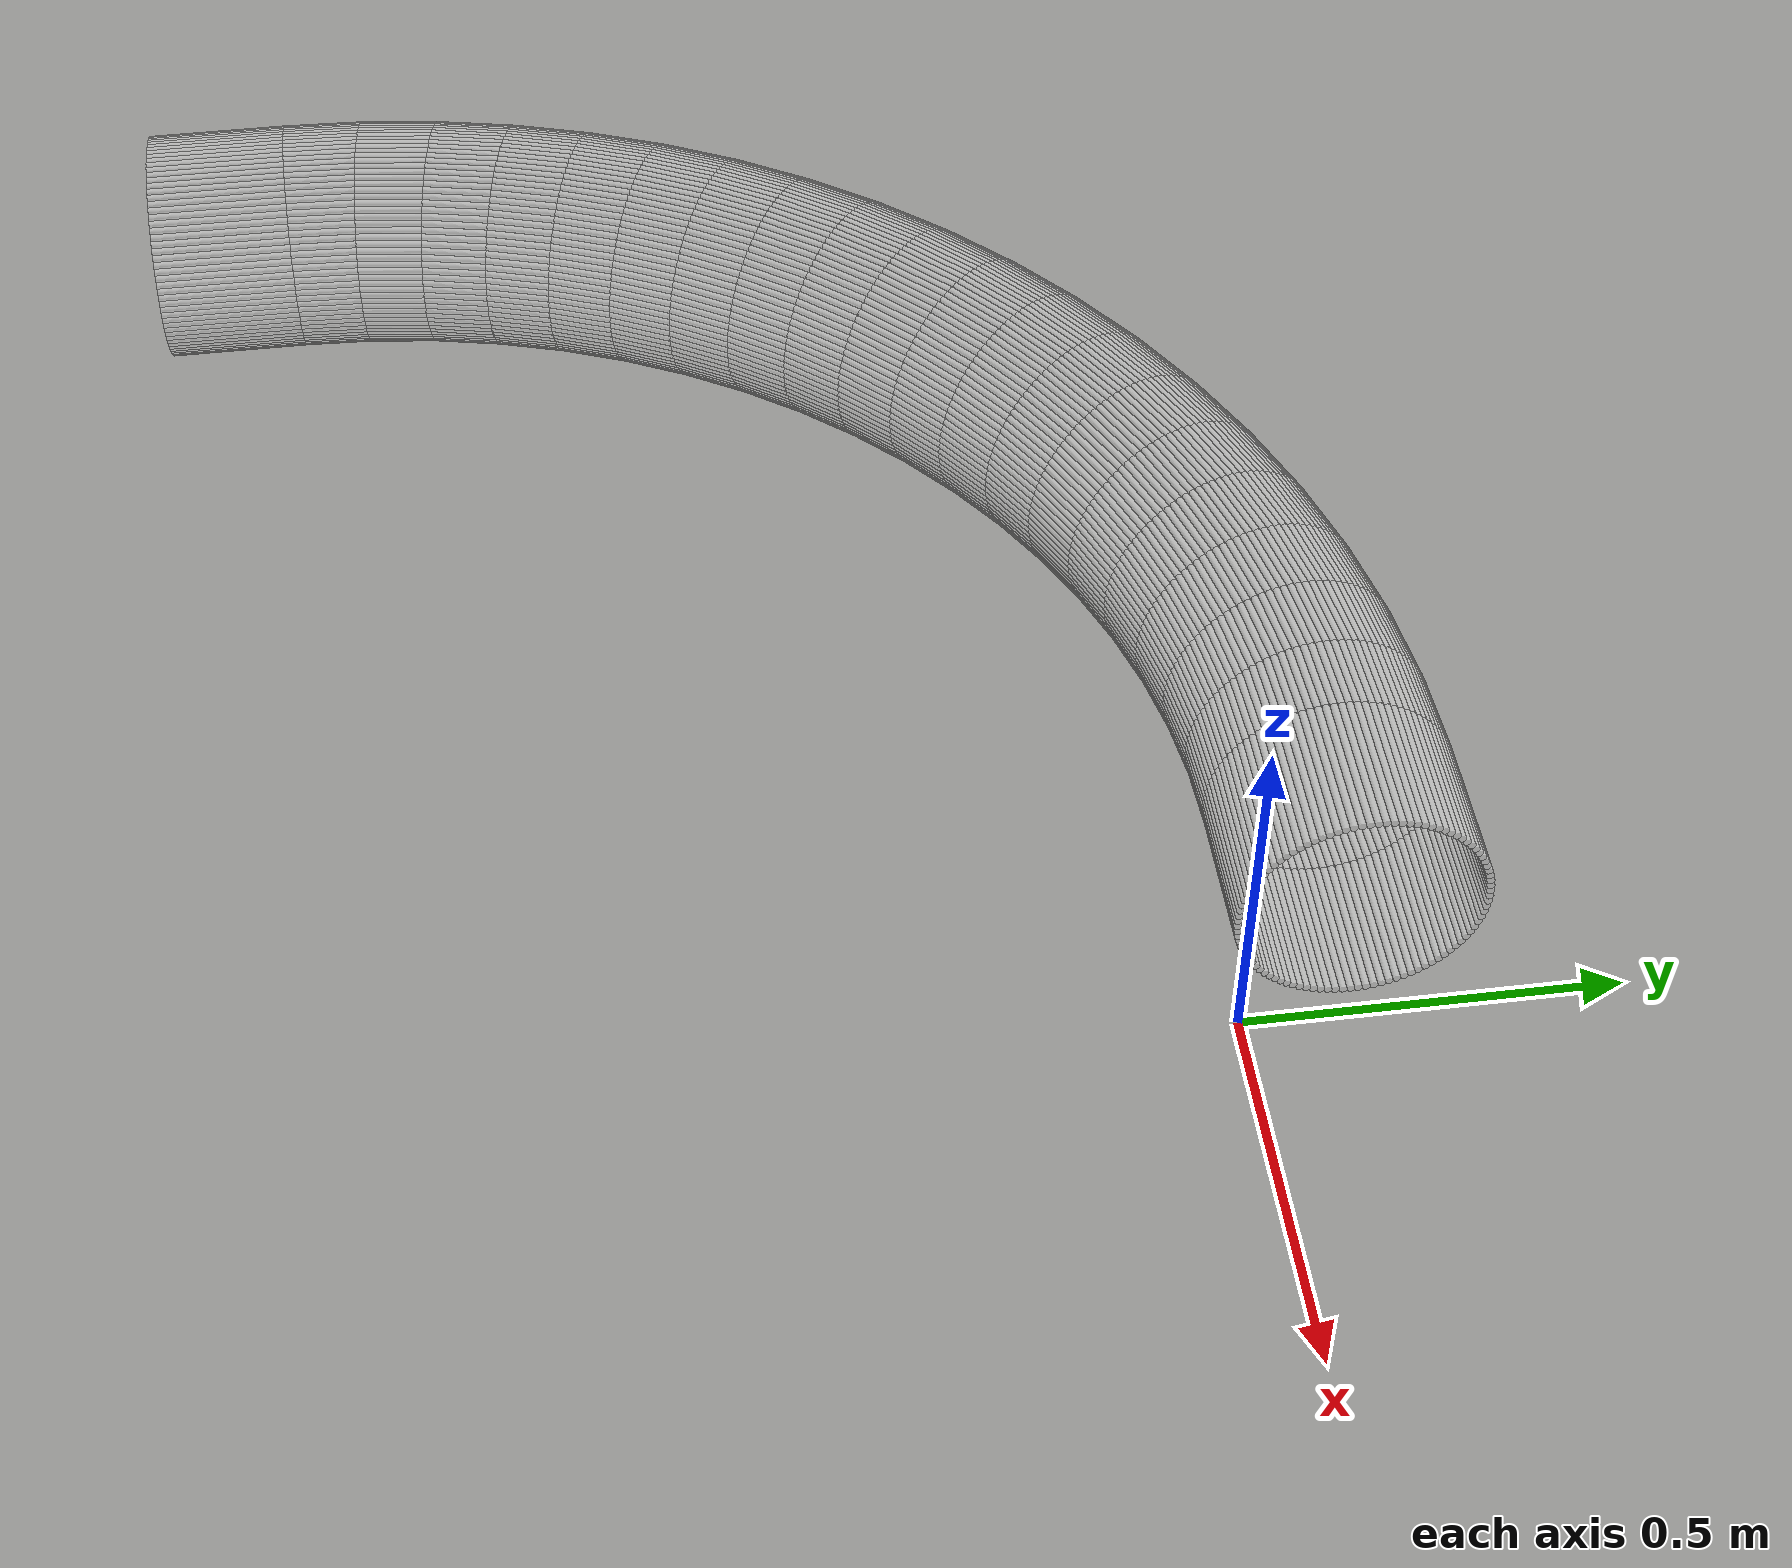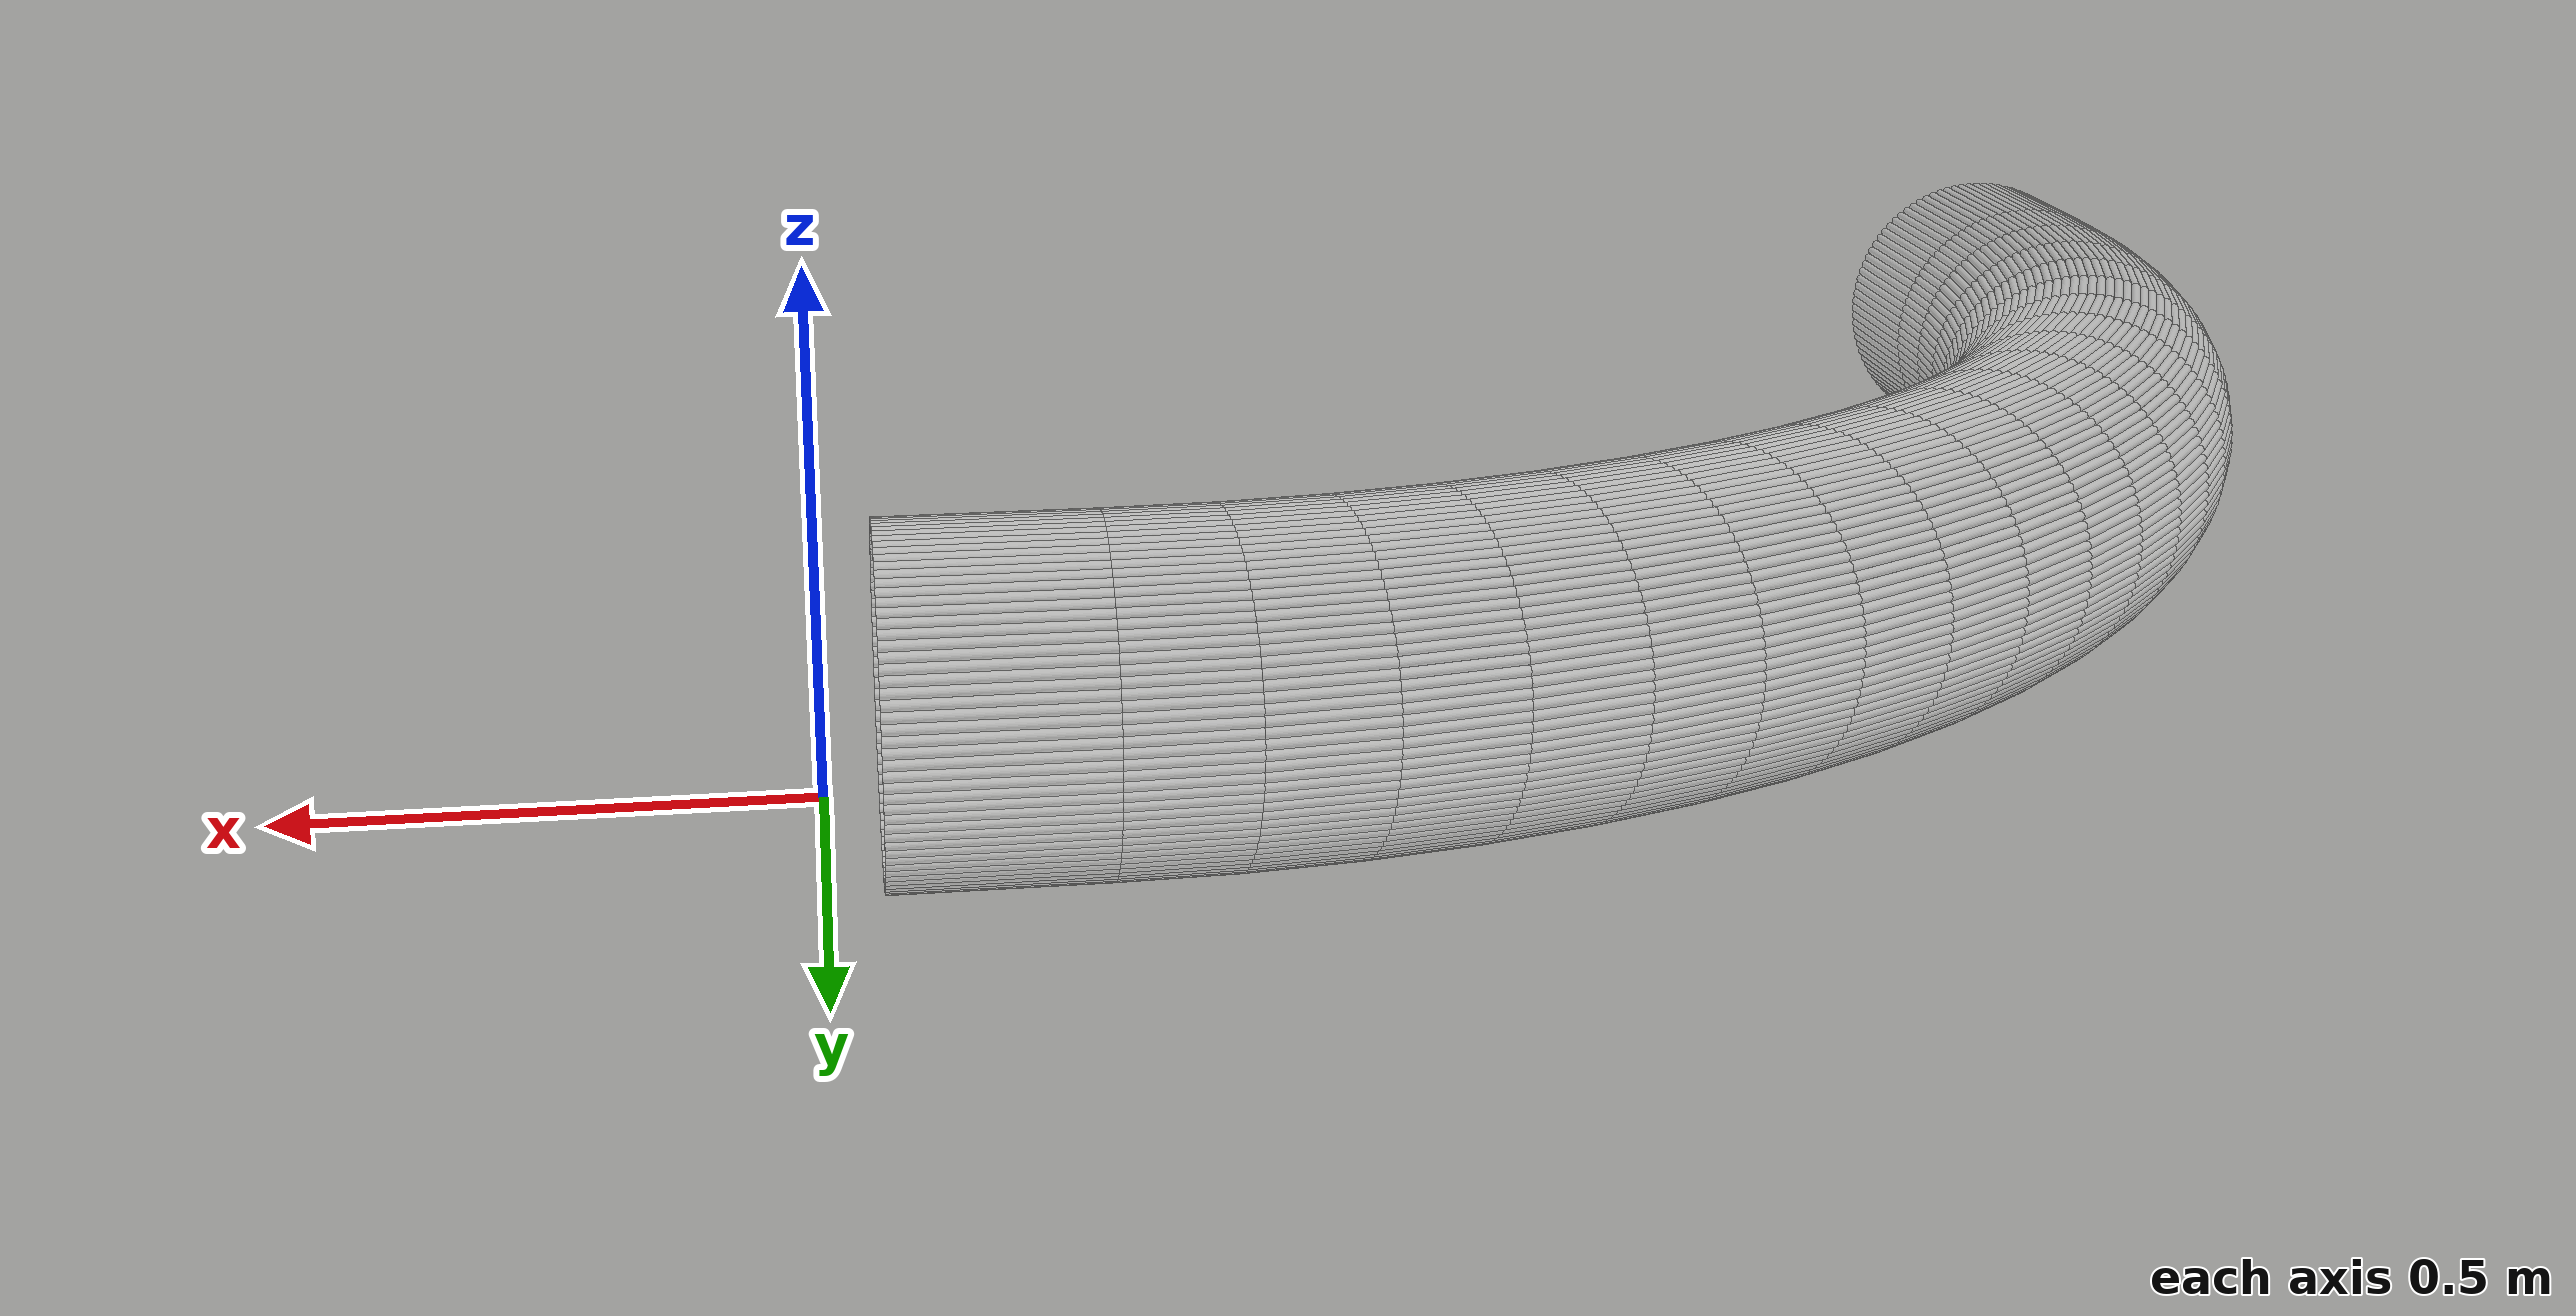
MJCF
<?xml version="1.0" encoding="utf-8"?>
<mujoco>
   <worldbody>
   <body pos="-0.25 -1.14 -0.02" euler="0 0 90">
      <geom euler=" 0 10 0 " fromto="1.46 -0.2 0.16 1.46 0 0.16" rgba="1 1 1 0.35"
            size="0.0050257"
            type="cylinder"/>
      <geom euler=" 0 20 0 " fromto="1.4597 -0.2 0.17005 1.4597 0 0.17005"
            rgba="1 1 1 0.35"
            size="0.0050257"
            type="cylinder"/>
      <geom euler=" 0 30 0 " fromto="1.4587 -0.2 0.18005 1.4587 0 0.18005"
            rgba="1 1 1 0.35"
            size="0.0050257"
            type="cylinder"/>
      <geom euler=" 0 40 0 " fromto="1.4572 -0.2 0.18998 1.4572 0 0.18998"
            rgba="1 1 1 0.35"
            size="0.0050257"
            type="cylinder"/>
      <geom euler=" 0 50 0 " fromto="1.455 -0.2 0.19979 1.455 0 0.19979" rgba="1 1 1 0.35"
            size="0.0050257"
            type="cylinder"/>
      <geom euler=" 0 60 0 " fromto="1.4522 -0.2 0.20944 1.4522 0 0.20944"
            rgba="1 1 1 0.35"
            size="0.0050257"
            type="cylinder"/>
      <geom euler=" 0 70 0 " fromto="1.4488 -0.2 0.2189 1.4488 0 0.2189" rgba="1 1 1 0.35"
            size="0.0050257"
            type="cylinder"/>
      <geom euler=" 0 80 0 " fromto="1.4448 -0.2 0.22812 1.4448 0 0.22812"
            rgba="1 1 1 0.35"
            size="0.0050257"
            type="cylinder"/>
      <geom euler=" 0 90 0 " fromto="1.4402 -0.2 0.23708 1.4402 0 0.23708"
            rgba="1 1 1 0.35"
            size="0.0050257"
            type="cylinder"/>
      <geom euler=" 0 100 0 " fromto="1.4351 -0.2 0.24573 1.4351 0 0.24573"
            rgba="1 1 1 0.35"
            size="0.0050257"
            type="cylinder"/>
      <geom euler=" 0 110 0 " fromto="1.4294 -0.2 0.25405 1.4294 0 0.25405"
            rgba="1 1 1 0.35"
            size="0.0050257"
            type="cylinder"/>
      <geom euler=" 0 120 0 " fromto="1.4233 -0.2 0.26199 1.4233 0 0.26199"
            rgba="1 1 1 0.35"
            size="0.0050257"
            type="cylinder"/>
      <geom euler=" 0 130 0 " fromto="1.4166 -0.2 0.26953 1.4166 0 0.26953"
            rgba="1 1 1 0.35"
            size="0.0050257"
            type="cylinder"/>
      <geom euler=" 0 140 0 " fromto="1.4095 -0.2 0.27663 1.4095 0 0.27663"
            rgba="1 1 1 0.35"
            size="0.0050257"
            type="cylinder"/>
      <geom euler=" 0 150 0 " fromto="1.402 -0.2 0.28328 1.402 0 0.28328" rgba="1 1 1 0.35"
            size="0.0050257"
            type="cylinder"/>
      <geom euler=" 0 160 0 " fromto="1.394 -0.2 0.28944 1.394 0 0.28944" rgba="1 1 1 0.35"
            size="0.0050257"
            type="cylinder"/>
      <geom euler=" 0 170 0 " fromto="1.3857 -0.2 0.29509 1.3857 0 0.29509"
            rgba="1 1 1 0.35"
            size="0.0050257"
            type="cylinder"/>
      <geom euler=" 0 180 0 " fromto="1.3771 -0.2 0.30021 1.3771 0 0.30021"
            rgba="1 1 1 0.35"
            size="0.0050257"
            type="cylinder"/>
      <geom euler=" 0 190 0 " fromto="1.3681 -0.2 0.30477 1.3681 0 0.30477"
            rgba="1 1 1 0.35"
            size="0.0050257"
            type="cylinder"/>
      <geom euler=" 0 200 0 " fromto="1.3589 -0.2 0.30876 1.3589 0 0.30876"
            rgba="1 1 1 0.35"
            size="0.0050257"
            type="cylinder"/>
      <geom euler=" 0 210 0 " fromto="1.3494 -0.2 0.31217 1.3494 0 0.31217"
            rgba="1 1 1 0.35"
            size="0.0050257"
            type="cylinder"/>
      <geom euler=" 0 220 0 " fromto="1.3398 -0.2 0.31497 1.3398 0 0.31497"
            rgba="1 1 1 0.35"
            size="0.0050257"
            type="cylinder"/>
      <geom euler=" 0 230 0 " fromto="1.33 -0.2 0.31717 1.33 0 0.31717" rgba="1 1 1 0.35"
            size="0.0050257"
            type="cylinder"/>
      <geom euler=" 0 240 0 " fromto="1.3201 -0.2 0.31874 1.3201 0 0.31874"
            rgba="1 1 1 0.35"
            size="0.0050257"
            type="cylinder"/>
      <geom euler=" 0 250 0 " fromto="1.31 -0.2 0.31968 1.31 0 0.31968" rgba="1 1 1 0.35"
            size="0.0050257"
            type="cylinder"/>
      <geom euler=" 0 260 0 " fromto="1.3 -0.2 0.32 1.3 0 0.32" rgba="1 1 1 0.35"
            size="0.0050257"
            type="cylinder"/>
      <geom euler=" 0 270 0 " fromto="1.29 -0.2 0.31968 1.29 0 0.31968" rgba="1 1 1 0.35"
            size="0.0050257"
            type="cylinder"/>
      <geom euler=" 0 280 0 " fromto="1.2799 -0.2 0.31874 1.2799 0 0.31874"
            rgba="1 1 1 0.35"
            size="0.0050257"
            type="cylinder"/>
      <geom euler=" 0 290 0 " fromto="1.27 -0.2 0.31717 1.27 0 0.31717" rgba="1 1 1 0.35"
            size="0.0050257"
            type="cylinder"/>
      <geom euler=" 0 300 0 " fromto="1.2602 -0.2 0.31497 1.2602 0 0.31497"
            rgba="1 1 1 0.35"
            size="0.0050257"
            type="cylinder"/>
      <geom euler=" 0 310 0 " fromto="1.2506 -0.2 0.31217 1.2506 0 0.31217"
            rgba="1 1 1 0.35"
            size="0.0050257"
            type="cylinder"/>
      <geom euler=" 0 320 0 " fromto="1.2411 -0.2 0.30876 1.2411 0 0.30876"
            rgba="1 1 1 0.35"
            size="0.0050257"
            type="cylinder"/>
      <geom euler=" 0 330 0 " fromto="1.2319 -0.2 0.30477 1.2319 0 0.30477"
            rgba="1 1 1 0.35"
            size="0.0050257"
            type="cylinder"/>
      <geom euler=" 0 340 0 " fromto="1.2229 -0.2 0.30021 1.2229 0 0.30021"
            rgba="1 1 1 0.35"
            size="0.0050257"
            type="cylinder"/>
      <geom euler=" 0 350 0 " fromto="1.2143 -0.2 0.29509 1.2143 0 0.29509"
            rgba="1 1 1 0.35"
            size="0.0050257"
            type="cylinder"/>
      <geom euler=" 0 360 0 " fromto="1.206 -0.2 0.28944 1.206 0 0.28944" rgba="1 1 1 0.35"
            size="0.0050257"
            type="cylinder"/>
      <geom euler=" 0 370 0 " fromto="1.198 -0.2 0.28328 1.198 0 0.28328" rgba="1 1 1 0.35"
            size="0.0050257"
            type="cylinder"/>
      <geom euler=" 0 380 0 " fromto="1.1905 -0.2 0.27663 1.1905 0 0.27663"
            rgba="1 1 1 0.35"
            size="0.0050257"
            type="cylinder"/>
      <geom euler=" 0 390 0 " fromto="1.1834 -0.2 0.26953 1.1834 0 0.26953"
            rgba="1 1 1 0.35"
            size="0.0050257"
            type="cylinder"/>
      <geom euler=" 0 400 0 " fromto="1.1767 -0.2 0.26199 1.1767 0 0.26199"
            rgba="1 1 1 0.35"
            size="0.0050257"
            type="cylinder"/>
      <geom euler=" 0 410 0 " fromto="1.1706 -0.2 0.25405 1.1706 0 0.25405"
            rgba="1 1 1 0.35"
            size="0.0050257"
            type="cylinder"/>
      <geom euler=" 0 420 0 " fromto="1.1649 -0.2 0.24573 1.1649 0 0.24573"
            rgba="1 1 1 0.35"
            size="0.0050257"
            type="cylinder"/>
      <geom euler=" 0 430 0 " fromto="1.1598 -0.2 0.23708 1.1598 0 0.23708"
            rgba="1 1 1 0.35"
            size="0.0050257"
            type="cylinder"/>
      <geom euler=" 0 440 0 " fromto="1.1552 -0.2 0.22812 1.1552 0 0.22812"
            rgba="1 1 1 0.35"
            size="0.0050257"
            type="cylinder"/>
      <geom euler=" 0 450 0 " fromto="1.1512 -0.2 0.2189 1.1512 0 0.2189" rgba="1 1 1 0.35"
            size="0.0050257"
            type="cylinder"/>
      <geom euler=" 0 460 0 " fromto="1.1478 -0.2 0.20944 1.1478 0 0.20944"
            rgba="1 1 1 0.35"
            size="0.0050257"
            type="cylinder"/>
      <geom euler=" 0 470 0 " fromto="1.145 -0.2 0.19979 1.145 0 0.19979" rgba="1 1 1 0.35"
            size="0.0050257"
            type="cylinder"/>
      <geom euler=" 0 480 0 " fromto="1.1428 -0.2 0.18998 1.1428 0 0.18998"
            rgba="1 1 1 0.35"
            size="0.0050257"
            type="cylinder"/>
      <geom euler=" 0 490 0 " fromto="1.1413 -0.2 0.18005 1.1413 0 0.18005"
            rgba="1 1 1 0.35"
            size="0.0050257"
            type="cylinder"/>
      <geom euler=" 0 500 0 " fromto="1.1403 -0.2 0.17005 1.1403 0 0.17005"
            rgba="1 1 1 0.35"
            size="0.0050257"
            type="cylinder"/>
      <geom euler=" 0 510 0 " fromto="1.14 -0.2 0.16 1.14 0 0.16" rgba="1 1 1 0.35"
            size="0.0050257"
            type="cylinder"/>
      <geom euler=" 0 520 0 " fromto="1.1403 -0.2 0.14995 1.1403 0 0.14995"
            rgba="1 1 1 0.35"
            size="0.0050257"
            type="cylinder"/>
      <geom euler=" 0 530 0 " fromto="1.1413 -0.2 0.13995 1.1413 0 0.13995"
            rgba="1 1 1 0.35"
            size="0.0050257"
            type="cylinder"/>
      <geom euler=" 0 540 0 " fromto="1.1428 -0.2 0.13002 1.1428 0 0.13002"
            rgba="1 1 1 0.35"
            size="0.0050257"
            type="cylinder"/>
      <geom euler=" 0 550 0 " fromto="1.145 -0.2 0.12021 1.145 0 0.12021" rgba="1 1 1 0.35"
            size="0.0050257"
            type="cylinder"/>
      <geom euler=" 0 560 0 " fromto="1.1478 -0.2 0.11056 1.1478 0 0.11056"
            rgba="1 1 1 0.35"
            size="0.0050257"
            type="cylinder"/>
      <geom euler=" 0 570 0 " fromto="1.1512 -0.2 0.1011 1.1512 0 0.1011" rgba="1 1 1 0.35"
            size="0.0050257"
            type="cylinder"/>
      <geom euler=" 0 580 0 " fromto="1.1552 -0.2 0.091875 1.1552 0 0.091875"
            rgba="1 1 1 0.35"
            size="0.0050257"
            type="cylinder"/>
      <geom euler=" 0 590 0 " fromto="1.1598 -0.2 0.082919 1.1598 0 0.082919"
            rgba="1 1 1 0.35"
            size="0.0050257"
            type="cylinder"/>
      <geom euler=" 0 600 0 " fromto="1.1649 -0.2 0.074268 1.1649 0 0.074268"
            rgba="1 1 1 0.35"
            size="0.0050257"
            type="cylinder"/>
      <geom euler=" 0 610 0 " fromto="1.1706 -0.2 0.065954 1.1706 0 0.065954"
            rgba="1 1 1 0.35"
            size="0.0050257"
            type="cylinder"/>
      <geom euler=" 0 620 0 " fromto="1.1767 -0.2 0.058012 1.1767 0 0.058012"
            rgba="1 1 1 0.35"
            size="0.0050257"
            type="cylinder"/>
      <geom euler=" 0 630 0 " fromto="1.1834 -0.2 0.050472 1.1834 0 0.050472"
            rgba="1 1 1 0.35"
            size="0.0050257"
            type="cylinder"/>
      <geom euler=" 0 640 0 " fromto="1.1905 -0.2 0.043365 1.1905 0 0.043365"
            rgba="1 1 1 0.35"
            size="0.0050257"
            type="cylinder"/>
      <geom euler=" 0 650 0 " fromto="1.198 -0.2 0.036718 1.198 0 0.036718"
            rgba="1 1 1 0.35"
            size="0.0050257"
            type="cylinder"/>
      <geom euler=" 0 660 0 " fromto="1.206 -0.2 0.030557 1.206 0 0.030557"
            rgba="1 1 1 0.35"
            size="0.0050257"
            type="cylinder"/>
      <geom euler=" 0 670 0 " fromto="1.2143 -0.2 0.024908 1.2143 0 0.024908"
            rgba="1 1 1 0.35"
            size="0.0050257"
            type="cylinder"/>
      <geom euler=" 0 680 0 " fromto="1.2229 -0.2 0.019791 1.2229 0 0.019791"
            rgba="1 1 1 0.35"
            size="0.0050257"
            type="cylinder"/>
      <geom euler=" 0 690 0 " fromto="1.2319 -0.2 0.015228 1.2319 0 0.015228"
            rgba="1 1 1 0.35"
            size="0.0050257"
            type="cylinder"/>
      <geom euler=" 0 700 0 " fromto="1.2411 -0.2 0.011236 1.2411 0 0.011236"
            rgba="1 1 1 0.35"
            size="0.0050257"
            type="cylinder"/>
      <geom euler=" 0 710 0 " fromto="1.2506 -0.2 0.007831 1.2506 0 0.007831"
            rgba="1 1 1 0.35"
            size="0.0050257"
            type="cylinder"/>
      <geom euler=" 0 720 0 " fromto="1.2602 -0.2 0.0050267 1.2602 0 0.0050267"
            rgba="1 1 1 0.35"
            size="0.0050257"
            type="cylinder"/>
      <geom euler=" 0 730 0 " fromto="1.27 -0.2 0.002834 1.27 0 0.002834" rgba="1 1 1 0.35"
            size="0.0050257"
            type="cylinder"/>
      <geom euler=" 0 740 0 " fromto="1.2799 -0.2 0.0012616 1.2799 0 0.0012616"
            rgba="1 1 1 0.35"
            size="0.0050257"
            type="cylinder"/>
      <geom euler=" 0 750 0 " fromto="1.29 -0.2 0.00031572 1.29 0 0.00031572"
            rgba="1 1 1 0.35"
            size="0.0050257"
            type="cylinder"/>
      <geom euler=" 0 760 0 " fromto="1.3 -0.2 0 1.3 0 0" rgba="1 1 1 0.35"
            size="0.0050257"
            type="cylinder"/>
      <geom euler=" 0 770 0 " fromto="1.31 -0.2 0.00031572 1.31 0 0.00031572"
            rgba="1 1 1 0.35"
            size="0.0050257"
            type="cylinder"/>
      <geom euler=" 0 780 0 " fromto="1.3201 -0.2 0.0012616 1.3201 0 0.0012616"
            rgba="1 1 1 0.35"
            size="0.0050257"
            type="cylinder"/>
      <geom euler=" 0 790 0 " fromto="1.33 -0.2 0.002834 1.33 0 0.002834" rgba="1 1 1 0.35"
            size="0.0050257"
            type="cylinder"/>
      <geom euler=" 0 800 0 " fromto="1.3398 -0.2 0.0050267 1.3398 0 0.0050267"
            rgba="1 1 1 0.35"
            size="0.0050257"
            type="cylinder"/>
      <geom euler=" 0 810 0 " fromto="1.3494 -0.2 0.007831 1.3494 0 0.007831"
            rgba="1 1 1 0.35"
            size="0.0050257"
            type="cylinder"/>
      <geom euler=" 0 820 0 " fromto="1.3589 -0.2 0.011236 1.3589 0 0.011236"
            rgba="1 1 1 0.35"
            size="0.0050257"
            type="cylinder"/>
      <geom euler=" 0 830 0 " fromto="1.3681 -0.2 0.015228 1.3681 0 0.015228"
            rgba="1 1 1 0.35"
            size="0.0050257"
            type="cylinder"/>
      <geom euler=" 0 840 0 " fromto="1.3771 -0.2 0.019791 1.3771 0 0.019791"
            rgba="1 1 1 0.35"
            size="0.0050257"
            type="cylinder"/>
      <geom euler=" 0 850 0 " fromto="1.3857 -0.2 0.024908 1.3857 0 0.024908"
            rgba="1 1 1 0.35"
            size="0.0050257"
            type="cylinder"/>
      <geom euler=" 0 860 0 " fromto="1.394 -0.2 0.030557 1.394 0 0.030557"
            rgba="1 1 1 0.35"
            size="0.0050257"
            type="cylinder"/>
      <geom euler=" 0 870 0 " fromto="1.402 -0.2 0.036718 1.402 0 0.036718"
            rgba="1 1 1 0.35"
            size="0.0050257"
            type="cylinder"/>
      <geom euler=" 0 880 0 " fromto="1.4095 -0.2 0.043365 1.4095 0 0.043365"
            rgba="1 1 1 0.35"
            size="0.0050257"
            type="cylinder"/>
      <geom euler=" 0 890 0 " fromto="1.4166 -0.2 0.050472 1.4166 0 0.050472"
            rgba="1 1 1 0.35"
            size="0.0050257"
            type="cylinder"/>
      <geom euler=" 0 900 0 " fromto="1.4233 -0.2 0.058012 1.4233 0 0.058012"
            rgba="1 1 1 0.35"
            size="0.0050257"
            type="cylinder"/>
      <geom euler=" 0 910 0 " fromto="1.4294 -0.2 0.065954 1.4294 0 0.065954"
            rgba="1 1 1 0.35"
            size="0.0050257"
            type="cylinder"/>
      <geom euler=" 0 920 0 " fromto="1.4351 -0.2 0.074268 1.4351 0 0.074268"
            rgba="1 1 1 0.35"
            size="0.0050257"
            type="cylinder"/>
      <geom euler=" 0 930 0 " fromto="1.4402 -0.2 0.082919 1.4402 0 0.082919"
            rgba="1 1 1 0.35"
            size="0.0050257"
            type="cylinder"/>
      <geom euler=" 0 940 0 " fromto="1.4448 -0.2 0.091875 1.4448 0 0.091875"
            rgba="1 1 1 0.35"
            size="0.0050257"
            type="cylinder"/>
      <geom euler=" 0 950 0 " fromto="1.4488 -0.2 0.1011 1.4488 0 0.1011" rgba="1 1 1 0.35"
            size="0.0050257"
            type="cylinder"/>
      <geom euler=" 0 960 0 " fromto="1.4522 -0.2 0.11056 1.4522 0 0.11056"
            rgba="1 1 1 0.35"
            size="0.0050257"
            type="cylinder"/>
      <geom euler=" 0 970 0 " fromto="1.455 -0.2 0.12021 1.455 0 0.12021" rgba="1 1 1 0.35"
            size="0.0050257"
            type="cylinder"/>
      <geom euler=" 0 980 0 " fromto="1.4572 -0.2 0.13002 1.4572 0 0.13002"
            rgba="1 1 1 0.35"
            size="0.0050257"
            type="cylinder"/>
      <geom euler=" 0 990 0 " fromto="1.4587 -0.2 0.13995 1.4587 0 0.13995"
            rgba="1 1 1 0.35"
            size="0.0050257"
            type="cylinder"/>
      <geom euler=" 0 1000 0 " fromto="1.4597 -0.2 0.14995 1.4597 0 0.14995"
            rgba="1 1 1 0.35"
            size="0.0050257"
            type="cylinder"/>
      <geom euler=" 0 10 0 " fromto="1.46 0 0.16 1.455 0.12057 0.16" rgba="1 1 1 0.35"
            size="0.0050257"
            type="cylinder"/>
      <geom euler=" 0 20 0 " fromto="1.4597 0 0.17005 1.4547 0.12054 0.17005"
            rgba="1 1 1 0.35"
            size="0.0050257"
            type="cylinder"/>
      <geom euler=" 0 30 0 " fromto="1.4587 0 0.18005 1.4538 0.12046 0.18005"
            rgba="1 1 1 0.35"
            size="0.0050257"
            type="cylinder"/>
      <geom euler=" 0 40 0 " fromto="1.4572 0 0.18998 1.4522 0.12033 0.18998"
            rgba="1 1 1 0.35"
            size="0.0050257"
            type="cylinder"/>
      <geom euler=" 0 50 0 " fromto="1.455 0 0.19979 1.45 0.12015 0.19979"
            rgba="1 1 1 0.35"
            size="0.0050257"
            type="cylinder"/>
      <geom euler=" 0 60 0 " fromto="1.4522 0 0.20944 1.4472 0.11992 0.20944"
            rgba="1 1 1 0.35"
            size="0.0050257"
            type="cylinder"/>
      <geom euler=" 0 70 0 " fromto="1.4488 0 0.2189 1.4438 0.11964 0.2189"
            rgba="1 1 1 0.35"
            size="0.0050257"
            type="cylinder"/>
      <geom euler=" 0 80 0 " fromto="1.4448 0 0.22812 1.4398 0.11931 0.22812"
            rgba="1 1 1 0.35"
            size="0.0050257"
            type="cylinder"/>
      <geom euler=" 0 90 0 " fromto="1.4402 0 0.23708 1.4353 0.11893 0.23708"
            rgba="1 1 1 0.35"
            size="0.0050257"
            type="cylinder"/>
      <geom euler=" 0 100 0 " fromto="1.4351 0 0.24573 1.4302 0.11851 0.24573"
            rgba="1 1 1 0.35"
            size="0.0050257"
            type="cylinder"/>
      <geom euler=" 0 110 0 " fromto="1.4294 0 0.25405 1.4246 0.11804 0.25405"
            rgba="1 1 1 0.35"
            size="0.0050257"
            type="cylinder"/>
      <geom euler=" 0 120 0 " fromto="1.4233 0 0.26199 1.4184 0.11753 0.26199"
            rgba="1 1 1 0.35"
            size="0.0050257"
            type="cylinder"/>
      <geom euler=" 0 130 0 " fromto="1.4166 0 0.26953 1.4118 0.11698 0.26953"
            rgba="1 1 1 0.35"
            size="0.0050257"
            type="cylinder"/>
      <geom euler=" 0 140 0 " fromto="1.4095 0 0.27663 1.4047 0.1164 0.27663"
            rgba="1 1 1 0.35"
            size="0.0050257"
            type="cylinder"/>
      <geom euler=" 0 150 0 " fromto="1.402 0 0.28328 1.3972 0.11578 0.28328"
            rgba="1 1 1 0.35"
            size="0.0050257"
            type="cylinder"/>
      <geom euler=" 0 160 0 " fromto="1.394 0 0.28944 1.3893 0.11512 0.28944"
            rgba="1 1 1 0.35"
            size="0.0050257"
            type="cylinder"/>
      <geom euler=" 0 170 0 " fromto="1.3857 0 0.29509 1.381 0.11443 0.29509"
            rgba="1 1 1 0.35"
            size="0.0050257"
            type="cylinder"/>
      <geom euler=" 0 180 0 " fromto="1.3771 0 0.30021 1.3724 0.11372 0.30021"
            rgba="1 1 1 0.35"
            size="0.0050257"
            type="cylinder"/>
      <geom euler=" 0 190 0 " fromto="1.3681 0 0.30477 1.3635 0.11298 0.30477"
            rgba="1 1 1 0.35"
            size="0.0050257"
            type="cylinder"/>
      <geom euler=" 0 200 0 " fromto="1.3589 0 0.30876 1.3543 0.11222 0.30876"
            rgba="1 1 1 0.35"
            size="0.0050257"
            type="cylinder"/>
      <geom euler=" 0 210 0 " fromto="1.3494 0 0.31217 1.3448 0.11144 0.31217"
            rgba="1 1 1 0.35"
            size="0.0050257"
            type="cylinder"/>
      <geom euler=" 0 220 0 " fromto="1.3398 0 0.31497 1.3352 0.11064 0.31497"
            rgba="1 1 1 0.35"
            size="0.0050257"
            type="cylinder"/>
      <geom euler=" 0 230 0 " fromto="1.33 0 0.31717 1.3254 0.10983 0.31717"
            rgba="1 1 1 0.35"
            size="0.0050257"
            type="cylinder"/>
      <geom euler=" 0 240 0 " fromto="1.3201 0 0.31874 1.3155 0.10901 0.31874"
            rgba="1 1 1 0.35"
            size="0.0050257"
            type="cylinder"/>
      <geom euler=" 0 250 0 " fromto="1.31 0 0.31968 1.3056 0.10818 0.31968"
            rgba="1 1 1 0.35"
            size="0.0050257"
            type="cylinder"/>
      <geom euler=" 0 260 0 " fromto="1.3 0 0.32 1.2956 0.10735 0.32" rgba="1 1 1 0.35"
            size="0.0050257"
            type="cylinder"/>
      <geom euler=" 0 270 0 " fromto="1.29 0 0.31968 1.2855 0.10652 0.31968"
            rgba="1 1 1 0.35"
            size="0.0050257"
            type="cylinder"/>
      <geom euler=" 0 280 0 " fromto="1.2799 0 0.31874 1.2756 0.1057 0.31874"
            rgba="1 1 1 0.35"
            size="0.0050257"
            type="cylinder"/>
      <geom euler=" 0 290 0 " fromto="1.27 0 0.31717 1.2657 0.10488 0.31717"
            rgba="1 1 1 0.35"
            size="0.0050257"
            type="cylinder"/>
      <geom euler=" 0 300 0 " fromto="1.2602 0 0.31497 1.2559 0.10407 0.31497"
            rgba="1 1 1 0.35"
            size="0.0050257"
            type="cylinder"/>
      <geom euler=" 0 310 0 " fromto="1.2506 0 0.31217 1.2463 0.10327 0.31217"
            rgba="1 1 1 0.35"
            size="0.0050257"
            type="cylinder"/>
      <geom euler=" 0 320 0 " fromto="1.2411 0 0.30876 1.2369 0.10249 0.30876"
            rgba="1 1 1 0.35"
            size="0.0050257"
            type="cylinder"/>
      <geom euler=" 0 330 0 " fromto="1.2319 0 0.30477 1.2277 0.10173 0.30477"
            rgba="1 1 1 0.35"
            size="0.0050257"
            type="cylinder"/>
      <geom euler=" 0 340 0 " fromto="1.2229 0 0.30021 1.2187 0.10099 0.30021"
            rgba="1 1 1 0.35"
            size="0.0050257"
            type="cylinder"/>
      <geom euler=" 0 350 0 " fromto="1.2143 0 0.29509 1.2101 0.10027 0.29509"
            rgba="1 1 1 0.35"
            size="0.0050257"
            type="cylinder"/>
      <geom euler=" 0 360 0 " fromto="1.206 0 0.28944 1.2018 0.099587 0.28944"
            rgba="1 1 1 0.35"
            size="0.0050257"
            type="cylinder"/>
      <geom euler=" 0 370 0 " fromto="1.198 0 0.28328 1.1939 0.098931 0.28328"
            rgba="1 1 1 0.35"
            size="0.0050257"
            type="cylinder"/>
      <geom euler=" 0 380 0 " fromto="1.1905 0 0.27663 1.1864 0.098308 0.27663"
            rgba="1 1 1 0.35"
            size="0.0050257"
            type="cylinder"/>
      <geom euler=" 0 390 0 " fromto="1.1834 0 0.26953 1.1793 0.097722 0.26953"
            rgba="1 1 1 0.35"
            size="0.0050257"
            type="cylinder"/>
      <geom euler=" 0 400 0 " fromto="1.1767 0 0.26199 1.1727 0.097173 0.26199"
            rgba="1 1 1 0.35"
            size="0.0050257"
            type="cylinder"/>
      <geom euler=" 0 410 0 " fromto="1.1706 0 0.25405 1.1666 0.096664 0.25405"
            rgba="1 1 1 0.35"
            size="0.0050257"
            type="cylinder"/>
      <geom euler=" 0 420 0 " fromto="1.1649 0 0.24573 1.1609 0.096197 0.24573"
            rgba="1 1 1 0.35"
            size="0.0050257"
            type="cylinder"/>
      <geom euler=" 0 430 0 " fromto="1.1598 0 0.23708 1.1558 0.095775 0.23708"
            rgba="1 1 1 0.35"
            size="0.0050257"
            type="cylinder"/>
      <geom euler=" 0 440 0 " fromto="1.1552 0 0.22812 1.1513 0.095398 0.22812"
            rgba="1 1 1 0.35"
            size="0.0050257"
            type="cylinder"/>
      <geom euler=" 0 450 0 " fromto="1.1512 0 0.2189 1.1473 0.095068 0.2189"
            rgba="1 1 1 0.35"
            size="0.0050257"
            type="cylinder"/>
      <geom euler=" 0 460 0 " fromto="1.1478 0 0.20944 1.1439 0.094787 0.20944"
            rgba="1 1 1 0.35"
            size="0.0050257"
            type="cylinder"/>
      <geom euler=" 0 470 0 " fromto="1.145 0 0.19979 1.1411 0.094556 0.19979"
            rgba="1 1 1 0.35"
            size="0.0050257"
            type="cylinder"/>
      <geom euler=" 0 480 0 " fromto="1.1428 0 0.18998 1.1389 0.094374 0.18998"
            rgba="1 1 1 0.35"
            size="0.0050257"
            type="cylinder"/>
      <geom euler=" 0 490 0 " fromto="1.1413 0 0.18005 1.1374 0.094245 0.18005"
            rgba="1 1 1 0.35"
            size="0.0050257"
            type="cylinder"/>
      <geom euler=" 0 500 0 " fromto="1.1403 0 0.17005 1.1364 0.094167 0.17005"
            rgba="1 1 1 0.35"
            size="0.0050257"
            type="cylinder"/>
      <geom euler=" 0 510 0 " fromto="1.14 0 0.16 1.1361 0.09414 0.16" rgba="1 1 1 0.35"
            size="0.0050257"
            type="cylinder"/>
      <geom euler=" 0 520 0 " fromto="1.1403 0 0.14995 1.1364 0.094167 0.14995"
            rgba="1 1 1 0.35"
            size="0.0050257"
            type="cylinder"/>
      <geom euler=" 0 530 0 " fromto="1.1413 0 0.13995 1.1374 0.094245 0.13995"
            rgba="1 1 1 0.35"
            size="0.0050257"
            type="cylinder"/>
      <geom euler=" 0 540 0 " fromto="1.1428 0 0.13002 1.1389 0.094374 0.13002"
            rgba="1 1 1 0.35"
            size="0.0050257"
            type="cylinder"/>
      <geom euler=" 0 550 0 " fromto="1.145 0 0.12021 1.1411 0.094556 0.12021"
            rgba="1 1 1 0.35"
            size="0.0050257"
            type="cylinder"/>
      <geom euler=" 0 560 0 " fromto="1.1478 0 0.11056 1.1439 0.094787 0.11056"
            rgba="1 1 1 0.35"
            size="0.0050257"
            type="cylinder"/>
      <geom euler=" 0 570 0 " fromto="1.1512 0 0.1011 1.1473 0.095068 0.1011"
            rgba="1 1 1 0.35"
            size="0.0050257"
            type="cylinder"/>
      <geom euler=" 0 580 0 " fromto="1.1552 0 0.091875 1.1513 0.095398 0.091875"
            rgba="1 1 1 0.35"
            size="0.0050257"
            type="cylinder"/>
      <geom euler=" 0 590 0 " fromto="1.1598 0 0.082919 1.1558 0.095775 0.082919"
            rgba="1 1 1 0.35"
            size="0.0050257"
            type="cylinder"/>
      <geom euler=" 0 600 0 " fromto="1.1649 0 0.074268 1.1609 0.096197 0.074268"
            rgba="1 1 1 0.35"
            size="0.0050257"
            type="cylinder"/>
      <geom euler=" 0 610 0 " fromto="1.1706 0 0.065954 1.1666 0.096664 0.065954"
            rgba="1 1 1 0.35"
            size="0.0050257"
            type="cylinder"/>
      <geom euler=" 0 620 0 " fromto="1.1767 0 0.058012 1.1727 0.097173 0.058012"
            rgba="1 1 1 0.35"
            size="0.0050257"
            type="cylinder"/>
      <geom euler=" 0 630 0 " fromto="1.1834 0 0.050472 1.1793 0.097722 0.050472"
            rgba="1 1 1 0.35"
            size="0.0050257"
            type="cylinder"/>
      <geom euler=" 0 640 0 " fromto="1.1905 0 0.043365 1.1864 0.098308 0.043365"
            rgba="1 1 1 0.35"
            size="0.0050257"
            type="cylinder"/>
      <geom euler=" 0 650 0 " fromto="1.198 0 0.036718 1.1939 0.098931 0.036718"
            rgba="1 1 1 0.35"
            size="0.0050257"
            type="cylinder"/>
      <geom euler=" 0 660 0 " fromto="1.206 0 0.030557 1.2018 0.099587 0.030557"
            rgba="1 1 1 0.35"
            size="0.0050257"
            type="cylinder"/>
      <geom euler=" 0 670 0 " fromto="1.2143 0 0.024908 1.2101 0.10027 0.024908"
            rgba="1 1 1 0.35"
            size="0.0050257"
            type="cylinder"/>
      <geom euler=" 0 680 0 " fromto="1.2229 0 0.019791 1.2187 0.10099 0.019791"
            rgba="1 1 1 0.35"
            size="0.0050257"
            type="cylinder"/>
      <geom euler=" 0 690 0 " fromto="1.2319 0 0.015228 1.2277 0.10173 0.015228"
            rgba="1 1 1 0.35"
            size="0.0050257"
            type="cylinder"/>
      <geom euler=" 0 700 0 " fromto="1.2411 0 0.011236 1.2369 0.10249 0.011236"
            rgba="1 1 1 0.35"
            size="0.0050257"
            type="cylinder"/>
      <geom euler=" 0 710 0 " fromto="1.2506 0 0.007831 1.2463 0.10327 0.007831"
            rgba="1 1 1 0.35"
            size="0.0050257"
            type="cylinder"/>
      <geom euler=" 0 720 0 " fromto="1.2602 0 0.0050267 1.2559 0.10407 0.0050267"
            rgba="1 1 1 0.35"
            size="0.0050257"
            type="cylinder"/>
      <geom euler=" 0 730 0 " fromto="1.27 0 0.002834 1.2657 0.10488 0.002834"
            rgba="1 1 1 0.35"
            size="0.0050257"
            type="cylinder"/>
      <geom euler=" 0 740 0 " fromto="1.2799 0 0.0012616 1.2756 0.1057 0.0012616"
            rgba="1 1 1 0.35"
            size="0.0050257"
            type="cylinder"/>
      <geom euler=" 0 750 0 " fromto="1.29 0 0.00031572 1.2855 0.10652 0.00031572"
            rgba="1 1 1 0.35"
            size="0.0050257"
            type="cylinder"/>
      <geom euler=" 0 760 0 " fromto="1.3 0 0 1.2956 0.10735 0" rgba="1 1 1 0.35"
            size="0.0050257"
            type="cylinder"/>
      <geom euler=" 0 770 0 " fromto="1.31 0 0.00031572 1.3056 0.10818 0.00031572"
            rgba="1 1 1 0.35"
            size="0.0050257"
            type="cylinder"/>
      <geom euler=" 0 780 0 " fromto="1.3201 0 0.0012616 1.3155 0.10901 0.0012616"
            rgba="1 1 1 0.35"
            size="0.0050257"
            type="cylinder"/>
      <geom euler=" 0 790 0 " fromto="1.33 0 0.002834 1.3254 0.10983 0.002834"
            rgba="1 1 1 0.35"
            size="0.0050257"
            type="cylinder"/>
      <geom euler=" 0 800 0 " fromto="1.3398 0 0.0050267 1.3352 0.11064 0.0050267"
            rgba="1 1 1 0.35"
            size="0.0050257"
            type="cylinder"/>
      <geom euler=" 0 810 0 " fromto="1.3494 0 0.007831 1.3448 0.11144 0.007831"
            rgba="1 1 1 0.35"
            size="0.0050257"
            type="cylinder"/>
      <geom euler=" 0 820 0 " fromto="1.3589 0 0.011236 1.3543 0.11222 0.011236"
            rgba="1 1 1 0.35"
            size="0.0050257"
            type="cylinder"/>
      <geom euler=" 0 830 0 " fromto="1.3681 0 0.015228 1.3635 0.11298 0.015228"
            rgba="1 1 1 0.35"
            size="0.0050257"
            type="cylinder"/>
      <geom euler=" 0 840 0 " fromto="1.3771 0 0.019791 1.3724 0.11372 0.019791"
            rgba="1 1 1 0.35"
            size="0.0050257"
            type="cylinder"/>
      <geom euler=" 0 850 0 " fromto="1.3857 0 0.024908 1.381 0.11443 0.024908"
            rgba="1 1 1 0.35"
            size="0.0050257"
            type="cylinder"/>
      <geom euler=" 0 860 0 " fromto="1.394 0 0.030557 1.3893 0.11512 0.030557"
            rgba="1 1 1 0.35"
            size="0.0050257"
            type="cylinder"/>
      <geom euler=" 0 870 0 " fromto="1.402 0 0.036718 1.3972 0.11578 0.036718"
            rgba="1 1 1 0.35"
            size="0.0050257"
            type="cylinder"/>
      <geom euler=" 0 880 0 " fromto="1.4095 0 0.043365 1.4047 0.1164 0.043365"
            rgba="1 1 1 0.35"
            size="0.0050257"
            type="cylinder"/>
      <geom euler=" 0 890 0 " fromto="1.4166 0 0.050472 1.4118 0.11698 0.050472"
            rgba="1 1 1 0.35"
            size="0.0050257"
            type="cylinder"/>
      <geom euler=" 0 900 0 " fromto="1.4233 0 0.058012 1.4184 0.11753 0.058012"
            rgba="1 1 1 0.35"
            size="0.0050257"
            type="cylinder"/>
      <geom euler=" 0 910 0 " fromto="1.4294 0 0.065954 1.4246 0.11804 0.065954"
            rgba="1 1 1 0.35"
            size="0.0050257"
            type="cylinder"/>
      <geom euler=" 0 920 0 " fromto="1.4351 0 0.074268 1.4302 0.11851 0.074268"
            rgba="1 1 1 0.35"
            size="0.0050257"
            type="cylinder"/>
      <geom euler=" 0 930 0 " fromto="1.4402 0 0.082919 1.4353 0.11893 0.082919"
            rgba="1 1 1 0.35"
            size="0.0050257"
            type="cylinder"/>
      <geom euler=" 0 940 0 " fromto="1.4448 0 0.091875 1.4398 0.11931 0.091875"
            rgba="1 1 1 0.35"
            size="0.0050257"
            type="cylinder"/>
      <geom euler=" 0 950 0 " fromto="1.4488 0 0.1011 1.4438 0.11964 0.1011"
            rgba="1 1 1 0.35"
            size="0.0050257"
            type="cylinder"/>
      <geom euler=" 0 960 0 " fromto="1.4522 0 0.11056 1.4472 0.11992 0.11056"
            rgba="1 1 1 0.35"
            size="0.0050257"
            type="cylinder"/>
      <geom euler=" 0 970 0 " fromto="1.455 0 0.12021 1.45 0.12015 0.12021"
            rgba="1 1 1 0.35"
            size="0.0050257"
            type="cylinder"/>
      <geom euler=" 0 980 0 " fromto="1.4572 0 0.13002 1.4522 0.12033 0.13002"
            rgba="1 1 1 0.35"
            size="0.0050257"
            type="cylinder"/>
      <geom euler=" 0 990 0 " fromto="1.4587 0 0.13995 1.4538 0.12046 0.13995"
            rgba="1 1 1 0.35"
            size="0.0050257"
            type="cylinder"/>
      <geom euler=" 0 1000 0 " fromto="1.4597 0 0.14995 1.4547 0.12054 0.14995"
            rgba="1 1 1 0.35"
            size="0.0050257"
            type="cylinder"/>
      <geom euler=" 0 10 0 " fromto="1.455 0.12057 0.16 1.4401 0.24031 0.16"
            rgba="1 1 1 0.35"
            size="0.0050257"
            type="cylinder"/>
      <geom euler=" 0 20 0 " fromto="1.4547 0.12054 0.17005 1.4398 0.24026 0.17005"
            rgba="1 1 1 0.35"
            size="0.0050257"
            type="cylinder"/>
      <geom euler=" 0 30 0 " fromto="1.4538 0.12046 0.18005 1.4388 0.2401 0.18005"
            rgba="1 1 1 0.35"
            size="0.0050257"
            type="cylinder"/>
      <geom euler=" 0 40 0 " fromto="1.4522 0.12033 0.18998 1.4373 0.23984 0.18998"
            rgba="1 1 1 0.35"
            size="0.0050257"
            type="cylinder"/>
      <geom euler=" 0 50 0 " fromto="1.45 0.12015 0.19979 1.4351 0.23948 0.19979"
            rgba="1 1 1 0.35"
            size="0.0050257"
            type="cylinder"/>
      <geom euler=" 0 60 0 " fromto="1.4472 0.11992 0.20944 1.4324 0.23902 0.20944"
            rgba="1 1 1 0.35"
            size="0.0050257"
            type="cylinder"/>
      <geom euler=" 0 70 0 " fromto="1.4438 0.11964 0.2189 1.429 0.23846 0.2189"
            rgba="1 1 1 0.35"
            size="0.0050257"
            type="cylinder"/>
      <geom euler=" 0 80 0 " fromto="1.4398 0.11931 0.22812 1.4251 0.2378 0.22812"
            rgba="1 1 1 0.35"
            size="0.0050257"
            type="cylinder"/>
      <geom euler=" 0 90 0 " fromto="1.4353 0.11893 0.23708 1.4206 0.23705 0.23708"
            rgba="1 1 1 0.35"
            size="0.0050257"
            type="cylinder"/>
      <geom euler=" 0 100 0 " fromto="1.4302 0.11851 0.24573 1.4155 0.23621 0.24573"
            rgba="1 1 1 0.35"
            size="0.0050257"
            type="cylinder"/>
      <geom euler=" 0 110 0 " fromto="1.4246 0.11804 0.25405 1.4099 0.23528 0.25405"
            rgba="1 1 1 0.35"
            size="0.0050257"
            type="cylinder"/>
      <geom euler=" 0 120 0 " fromto="1.4184 0.11753 0.26199 1.4039 0.23426 0.26199"
            rgba="1 1 1 0.35"
            size="0.0050257"
            type="cylinder"/>
      <geom euler=" 0 130 0 " fromto="1.4118 0.11698 0.26953 1.3973 0.23317 0.26953"
            rgba="1 1 1 0.35"
            size="0.0050257"
            type="cylinder"/>
      <geom euler=" 0 140 0 " fromto="1.4047 0.1164 0.27663 1.3903 0.232 0.27663"
            rgba="1 1 1 0.35"
            size="0.0050257"
            type="cylinder"/>
      <geom euler=" 0 150 0 " fromto="1.3972 0.11578 0.28328 1.3829 0.23076 0.28328"
            rgba="1 1 1 0.35"
            size="0.0050257"
            type="cylinder"/>
      <geom euler=" 0 160 0 " fromto="1.3893 0.11512 0.28944 1.375 0.22945 0.28944"
            rgba="1 1 1 0.35"
            size="0.0050257"
            type="cylinder"/>
      <geom euler=" 0 170 0 " fromto="1.381 0.11443 0.29509 1.3668 0.22808 0.29509"
            rgba="1 1 1 0.35"
            size="0.0050257"
            type="cylinder"/>
      <geom euler=" 0 180 0 " fromto="1.3724 0.11372 0.30021 1.3583 0.22666 0.30021"
            rgba="1 1 1 0.35"
            size="0.0050257"
            type="cylinder"/>
      <geom euler=" 0 190 0 " fromto="1.3635 0.11298 0.30477 1.3495 0.22519 0.30477"
            rgba="1 1 1 0.35"
            size="0.0050257"
            type="cylinder"/>
      <geom euler=" 0 200 0 " fromto="1.3543 0.11222 0.30876 1.3404 0.22367 0.30876"
            rgba="1 1 1 0.35"
            size="0.0050257"
            type="cylinder"/>
      <geom euler=" 0 210 0 " fromto="1.3448 0.11144 0.31217 1.331 0.22211 0.31217"
            rgba="1 1 1 0.35"
            size="0.0050257"
            type="cylinder"/>
      <geom euler=" 0 220 0 " fromto="1.3352 0.11064 0.31497 1.3215 0.22052 0.31497"
            rgba="1 1 1 0.35"
            size="0.0050257"
            type="cylinder"/>
      <geom euler=" 0 230 0 " fromto="1.3254 0.10983 0.31717 1.3118 0.21891 0.31717"
            rgba="1 1 1 0.35"
            size="0.0050257"
            type="cylinder"/>
      <geom euler=" 0 240 0 " fromto="1.3155 0.10901 0.31874 1.302 0.21727 0.31874"
            rgba="1 1 1 0.35"
            size="0.0050257"
            type="cylinder"/>
      <geom euler=" 0 250 0 " fromto="1.3056 0.10818 0.31968 1.2922 0.21563 0.31968"
            rgba="1 1 1 0.35"
            size="0.0050257"
            type="cylinder"/>
      <geom euler=" 0 260 0 " fromto="1.2956 0.10735 0.32 1.2823 0.21397 0.32"
            rgba="1 1 1 0.35"
            size="0.0050257"
            type="cylinder"/>
      <geom euler=" 0 270 0 " fromto="1.2855 0.10652 0.31968 1.2724 0.21232 0.31968"
            rgba="1 1 1 0.35"
            size="0.0050257"
            type="cylinder"/>
      <geom euler=" 0 280 0 " fromto="1.2756 0.1057 0.31874 1.2625 0.21067 0.31874"
            rgba="1 1 1 0.35"
            size="0.0050257"
            type="cylinder"/>
      <geom euler=" 0 290 0 " fromto="1.2657 0.10488 0.31717 1.2527 0.20904 0.31717"
            rgba="1 1 1 0.35"
            size="0.0050257"
            type="cylinder"/>
      <geom euler=" 0 300 0 " fromto="1.2559 0.10407 0.31497 1.243 0.20742 0.31497"
            rgba="1 1 1 0.35"
            size="0.0050257"
            type="cylinder"/>
      <geom euler=" 0 310 0 " fromto="1.2463 0.10327 0.31217 1.2335 0.20583 0.31217"
            rgba="1 1 1 0.35"
            size="0.0050257"
            type="cylinder"/>
      <geom euler=" 0 320 0 " fromto="1.2369 0.10249 0.30876 1.2242 0.20428 0.30876"
            rgba="1 1 1 0.35"
            size="0.0050257"
            type="cylinder"/>
      <geom euler=" 0 330 0 " fromto="1.2277 0.10173 0.30477 1.2151 0.20276 0.30477"
            rgba="1 1 1 0.35"
            size="0.0050257"
            type="cylinder"/>
      <geom euler=" 0 340 0 " fromto="1.2187 0.10099 0.30021 1.2062 0.20129 0.30021"
            rgba="1 1 1 0.35"
            size="0.0050257"
            type="cylinder"/>
      <geom euler=" 0 350 0 " fromto="1.2101 0.10027 0.29509 1.1977 0.19986 0.29509"
            rgba="1 1 1 0.35"
            size="0.0050257"
            type="cylinder"/>
      <geom euler=" 0 360 0 " fromto="1.2018 0.099587 0.28944 1.1895 0.19849 0.28944"
            rgba="1 1 1 0.35"
            size="0.0050257"
            type="cylinder"/>
      <geom euler=" 0 370 0 " fromto="1.1939 0.098931 0.28328 1.1817 0.19719 0.28328"
            rgba="1 1 1 0.35"
            size="0.0050257"
            type="cylinder"/>
      <geom euler=" 0 380 0 " fromto="1.1864 0.098308 0.27663 1.1742 0.19595 0.27663"
            rgba="1 1 1 0.35"
            size="0.0050257"
            type="cylinder"/>
      <geom euler=" 0 390 0 " fromto="1.1793 0.097722 0.26953 1.1672 0.19478 0.26953"
            rgba="1 1 1 0.35"
            size="0.0050257"
            type="cylinder"/>
      <geom euler=" 0 400 0 " fromto="1.1727 0.097173 0.26199 1.1607 0.19368 0.26199"
            rgba="1 1 1 0.35"
            size="0.0050257"
            type="cylinder"/>
      <geom euler=" 0 410 0 " fromto="1.1666 0.096664 0.25405 1.1546 0.19267 0.25405"
            rgba="1 1 1 0.35"
            size="0.0050257"
            type="cylinder"/>
      <geom euler=" 0 420 0 " fromto="1.1609 0.096197 0.24573 1.149 0.19174 0.24573"
            rgba="1 1 1 0.35"
            size="0.0050257"
            type="cylinder"/>
      <geom euler=" 0 430 0 " fromto="1.1558 0.095775 0.23708 1.144 0.1909 0.23708"
            rgba="1 1 1 0.35"
            size="0.0050257"
            type="cylinder"/>
      <geom euler=" 0 440 0 " fromto="1.1513 0.095398 0.22812 1.1395 0.19014 0.22812"
            rgba="1 1 1 0.35"
            size="0.0050257"
            type="cylinder"/>
      <geom euler=" 0 450 0 " fromto="1.1473 0.095068 0.2189 1.1355 0.18949 0.2189"
            rgba="1 1 1 0.35"
            size="0.0050257"
            type="cylinder"/>
      <geom euler=" 0 460 0 " fromto="1.1439 0.094787 0.20944 1.1322 0.18893 0.20944"
            rgba="1 1 1 0.35"
            size="0.0050257"
            type="cylinder"/>
      <geom euler=" 0 470 0 " fromto="1.1411 0.094556 0.19979 1.1294 0.18847 0.19979"
            rgba="1 1 1 0.35"
            size="0.0050257"
            type="cylinder"/>
      <geom euler=" 0 480 0 " fromto="1.1389 0.094374 0.18998 1.1272 0.1881 0.18998"
            rgba="1 1 1 0.35"
            size="0.0050257"
            type="cylinder"/>
      <geom euler=" 0 490 0 " fromto="1.1374 0.094245 0.18005 1.1257 0.18785 0.18005"
            rgba="1 1 1 0.35"
            size="0.0050257"
            type="cylinder"/>
      <geom euler=" 0 500 0 " fromto="1.1364 0.094167 0.17005 1.1248 0.18769 0.17005"
            rgba="1 1 1 0.35"
            size="0.0050257"
            type="cylinder"/>
      <geom euler=" 0 510 0 " fromto="1.1361 0.09414 0.16 1.1245 0.18764 0.16"
            rgba="1 1 1 0.35"
            size="0.0050257"
            type="cylinder"/>
      <geom euler=" 0 520 0 " fromto="1.1364 0.094167 0.14995 1.1248 0.18769 0.14995"
            rgba="1 1 1 0.35"
            size="0.0050257"
            type="cylinder"/>
      <geom euler=" 0 530 0 " fromto="1.1374 0.094245 0.13995 1.1257 0.18785 0.13995"
            rgba="1 1 1 0.35"
            size="0.0050257"
            type="cylinder"/>
      <geom euler=" 0 540 0 " fromto="1.1389 0.094374 0.13002 1.1272 0.1881 0.13002"
            rgba="1 1 1 0.35"
            size="0.0050257"
            type="cylinder"/>
      <geom euler=" 0 550 0 " fromto="1.1411 0.094556 0.12021 1.1294 0.18847 0.12021"
            rgba="1 1 1 0.35"
            size="0.0050257"
            type="cylinder"/>
      <geom euler=" 0 560 0 " fromto="1.1439 0.094787 0.11056 1.1322 0.18893 0.11056"
            rgba="1 1 1 0.35"
            size="0.0050257"
            type="cylinder"/>
      <geom euler=" 0 570 0 " fromto="1.1473 0.095068 0.1011 1.1355 0.18949 0.1011"
            rgba="1 1 1 0.35"
            size="0.0050257"
            type="cylinder"/>
      <geom euler=" 0 580 0 " fromto="1.1513 0.095398 0.091875 1.1395 0.19014 0.091875"
            rgba="1 1 1 0.35"
            size="0.0050257"
            type="cylinder"/>
      <geom euler=" 0 590 0 " fromto="1.1558 0.095775 0.082919 1.144 0.1909 0.082919"
            rgba="1 1 1 0.35"
            size="0.0050257"
            type="cylinder"/>
      <geom euler=" 0 600 0 " fromto="1.1609 0.096197 0.074268 1.149 0.19174 0.074268"
            rgba="1 1 1 0.35"
            size="0.0050257"
            type="cylinder"/>
      <geom euler=" 0 610 0 " fromto="1.1666 0.096664 0.065954 1.1546 0.19267 0.065954"
            rgba="1 1 1 0.35"
            size="0.0050257"
            type="cylinder"/>
      <geom euler=" 0 620 0 " fromto="1.1727 0.097173 0.058012 1.1607 0.19368 0.058012"
            rgba="1 1 1 0.35"
            size="0.0050257"
            type="cylinder"/>
      <geom euler=" 0 630 0 " fromto="1.1793 0.097722 0.050472 1.1672 0.19478 0.050472"
            rgba="1 1 1 0.35"
            size="0.0050257"
            type="cylinder"/>
      <geom euler=" 0 640 0 " fromto="1.1864 0.098308 0.043365 1.1742 0.19595 0.043365"
            rgba="1 1 1 0.35"
            size="0.0050257"
            type="cylinder"/>
      <geom euler=" 0 650 0 " fromto="1.1939 0.098931 0.036718 1.1817 0.19719 0.036718"
            rgba="1 1 1 0.35"
            size="0.0050257"
            type="cylinder"/>
      <geom euler=" 0 660 0 " fromto="1.2018 0.099587 0.030557 1.1895 0.19849 0.030557"
            rgba="1 1 1 0.35"
            size="0.0050257"
            type="cylinder"/>
      <geom euler=" 0 670 0 " fromto="1.2101 0.10027 0.024908 1.1977 0.19986 0.024908"
            rgba="1 1 1 0.35"
            size="0.0050257"
            type="cylinder"/>
      <geom euler=" 0 680 0 " fromto="1.2187 0.10099 0.019791 1.2062 0.20129 0.019791"
            rgba="1 1 1 0.35"
            size="0.0050257"
            type="cylinder"/>
      <geom euler=" 0 690 0 " fromto="1.2277 0.10173 0.015228 1.2151 0.20276 0.015228"
            rgba="1 1 1 0.35"
            size="0.0050257"
            type="cylinder"/>
      <geom euler=" 0 700 0 " fromto="1.2369 0.10249 0.011236 1.2242 0.20428 0.011236"
            rgba="1 1 1 0.35"
            size="0.0050257"
            type="cylinder"/>
      <geom euler=" 0 710 0 " fromto="1.2463 0.10327 0.007831 1.2335 0.20583 0.007831"
            rgba="1 1 1 0.35"
            size="0.0050257"
            type="cylinder"/>
      <geom euler=" 0 720 0 " fromto="1.2559 0.10407 0.0050267 1.243 0.20742 0.0050267"
            rgba="1 1 1 0.35"
            size="0.0050257"
            type="cylinder"/>
      <geom euler=" 0 730 0 " fromto="1.2657 0.10488 0.002834 1.2527 0.20904 0.002834"
            rgba="1 1 1 0.35"
            size="0.0050257"
            type="cylinder"/>
      <geom euler=" 0 740 0 " fromto="1.2756 0.1057 0.0012616 1.2625 0.21067 0.0012616"
            rgba="1 1 1 0.35"
            size="0.0050257"
            type="cylinder"/>
      <geom euler=" 0 750 0 " fromto="1.2855 0.10652 0.00031572 1.2724 0.21232 0.00031572"
            rgba="1 1 1 0.35"
            size="0.0050257"
            type="cylinder"/>
      <geom euler=" 0 760 0 " fromto="1.2956 0.10735 0 1.2823 0.21397 0" rgba="1 1 1 0.35"
            size="0.0050257"
            type="cylinder"/>
      <geom euler=" 0 770 0 " fromto="1.3056 0.10818 0.00031572 1.2922 0.21563 0.00031572"
            rgba="1 1 1 0.35"
            size="0.0050257"
            type="cylinder"/>
      <geom euler=" 0 780 0 " fromto="1.3155 0.10901 0.0012616 1.302 0.21727 0.0012616"
            rgba="1 1 1 0.35"
            size="0.0050257"
            type="cylinder"/>
      <geom euler=" 0 790 0 " fromto="1.3254 0.10983 0.002834 1.3118 0.21891 0.002834"
            rgba="1 1 1 0.35"
            size="0.0050257"
            type="cylinder"/>
      <geom euler=" 0 800 0 " fromto="1.3352 0.11064 0.0050267 1.3215 0.22052 0.0050267"
            rgba="1 1 1 0.35"
            size="0.0050257"
            type="cylinder"/>
      <geom euler=" 0 810 0 " fromto="1.3448 0.11144 0.007831 1.331 0.22211 0.007831"
            rgba="1 1 1 0.35"
            size="0.0050257"
            type="cylinder"/>
      <geom euler=" 0 820 0 " fromto="1.3543 0.11222 0.011236 1.3404 0.22367 0.011236"
            rgba="1 1 1 0.35"
            size="0.0050257"
            type="cylinder"/>
      <geom euler=" 0 830 0 " fromto="1.3635 0.11298 0.015228 1.3495 0.22519 0.015228"
            rgba="1 1 1 0.35"
            size="0.0050257"
            type="cylinder"/>
      <geom euler=" 0 840 0 " fromto="1.3724 0.11372 0.019791 1.3583 0.22666 0.019791"
            rgba="1 1 1 0.35"
            size="0.0050257"
            type="cylinder"/>
      <geom euler=" 0 850 0 " fromto="1.381 0.11443 0.024908 1.3668 0.22808 0.024908"
            rgba="1 1 1 0.35"
            size="0.0050257"
            type="cylinder"/>
      <geom euler=" 0 860 0 " fromto="1.3893 0.11512 0.030557 1.375 0.22945 0.030557"
            rgba="1 1 1 0.35"
            size="0.0050257"
            type="cylinder"/>
      <geom euler=" 0 870 0 " fromto="1.3972 0.11578 0.036718 1.3829 0.23076 0.036718"
            rgba="1 1 1 0.35"
            size="0.0050257"
            type="cylinder"/>
      <geom euler=" 0 880 0 " fromto="1.4047 0.1164 0.043365 1.3903 0.232 0.043365"
            rgba="1 1 1 0.35"
            size="0.0050257"
            type="cylinder"/>
      <geom euler=" 0 890 0 " fromto="1.4118 0.11698 0.050472 1.3973 0.23317 0.050472"
            rgba="1 1 1 0.35"
            size="0.0050257"
            type="cylinder"/>
      <geom euler=" 0 900 0 " fromto="1.4184 0.11753 0.058012 1.4039 0.23426 0.058012"
            rgba="1 1 1 0.35"
            size="0.0050257"
            type="cylinder"/>
      <geom euler=" 0 910 0 " fromto="1.4246 0.11804 0.065954 1.4099 0.23528 0.065954"
            rgba="1 1 1 0.35"
            size="0.0050257"
            type="cylinder"/>
      <geom euler=" 0 920 0 " fromto="1.4302 0.11851 0.074268 1.4155 0.23621 0.074268"
            rgba="1 1 1 0.35"
            size="0.0050257"
            type="cylinder"/>
      <geom euler=" 0 930 0 " fromto="1.4353 0.11893 0.082919 1.4206 0.23705 0.082919"
            rgba="1 1 1 0.35"
            size="0.0050257"
            type="cylinder"/>
      <geom euler=" 0 940 0 " fromto="1.4398 0.11931 0.091875 1.4251 0.2378 0.091875"
            rgba="1 1 1 0.35"
            size="0.0050257"
            type="cylinder"/>
      <geom euler=" 0 950 0 " fromto="1.4438 0.11964 0.1011 1.429 0.23846 0.1011"
            rgba="1 1 1 0.35"
            size="0.0050257"
            type="cylinder"/>
      <geom euler=" 0 960 0 " fromto="1.4472 0.11992 0.11056 1.4324 0.23902 0.11056"
            rgba="1 1 1 0.35"
            size="0.0050257"
            type="cylinder"/>
      <geom euler=" 0 970 0 " fromto="1.45 0.12015 0.12021 1.4351 0.23948 0.12021"
            rgba="1 1 1 0.35"
            size="0.0050257"
            type="cylinder"/>
      <geom euler=" 0 980 0 " fromto="1.4522 0.12033 0.13002 1.4373 0.23984 0.13002"
            rgba="1 1 1 0.35"
            size="0.0050257"
            type="cylinder"/>
      <geom euler=" 0 990 0 " fromto="1.4538 0.12046 0.13995 1.4388 0.2401 0.13995"
            rgba="1 1 1 0.35"
            size="0.0050257"
            type="cylinder"/>
      <geom euler=" 0 1000 0 " fromto="1.4547 0.12054 0.14995 1.4398 0.24026 0.14995"
            rgba="1 1 1 0.35"
            size="0.0050257"
            type="cylinder"/>
      <geom euler=" 0 10 0 " fromto="1.4401 0.24031 0.16 1.4153 0.35841 0.16"
            rgba="1 1 1 0.35"
            size="0.0050257"
            type="cylinder"/>
      <geom euler=" 0 20 0 " fromto="1.4398 0.24026 0.17005 1.415 0.35833 0.17005"
            rgba="1 1 1 0.35"
            size="0.0050257"
            type="cylinder"/>
      <geom euler=" 0 30 0 " fromto="1.4388 0.2401 0.18005 1.4141 0.3581 0.18005"
            rgba="1 1 1 0.35"
            size="0.0050257"
            type="cylinder"/>
      <geom euler=" 0 40 0 " fromto="1.4373 0.23984 0.18998 1.4126 0.35771 0.18998"
            rgba="1 1 1 0.35"
            size="0.0050257"
            type="cylinder"/>
      <geom euler=" 0 50 0 " fromto="1.4351 0.23948 0.19979 1.4105 0.35717 0.19979"
            rgba="1 1 1 0.35"
            size="0.0050257"
            type="cylinder"/>
      <geom euler=" 0 60 0 " fromto="1.4324 0.23902 0.20944 1.4077 0.35649 0.20944"
            rgba="1 1 1 0.35"
            size="0.0050257"
            type="cylinder"/>
      <geom euler=" 0 70 0 " fromto="1.429 0.23846 0.2189 1.4044 0.35565 0.2189"
            rgba="1 1 1 0.35"
            size="0.0050257"
            type="cylinder"/>
      <geom euler=" 0 80 0 " fromto="1.4251 0.2378 0.22812 1.4006 0.35467 0.22812"
            rgba="1 1 1 0.35"
            size="0.0050257"
            type="cylinder"/>
      <geom euler=" 0 90 0 " fromto="1.4206 0.23705 0.23708 1.3961 0.35355 0.23708"
            rgba="1 1 1 0.35"
            size="0.0050257"
            type="cylinder"/>
      <geom euler=" 0 100 0 " fromto="1.4155 0.23621 0.24573 1.3912 0.35229 0.24573"
            rgba="1 1 1 0.35"
            size="0.0050257"
            type="cylinder"/>
      <geom euler=" 0 110 0 " fromto="1.4099 0.23528 0.25405 1.3857 0.35091 0.25405"
            rgba="1 1 1 0.35"
            size="0.0050257"
            type="cylinder"/>
      <geom euler=" 0 120 0 " fromto="1.4039 0.23426 0.26199 1.3797 0.3494 0.26199"
            rgba="1 1 1 0.35"
            size="0.0050257"
            type="cylinder"/>
      <geom euler=" 0 130 0 " fromto="1.3973 0.23317 0.26953 1.3733 0.34776 0.26953"
            rgba="1 1 1 0.35"
            size="0.0050257"
            type="cylinder"/>
      <geom euler=" 0 140 0 " fromto="1.3903 0.232 0.27663 1.3664 0.34602 0.27663"
            rgba="1 1 1 0.35"
            size="0.0050257"
            type="cylinder"/>
      <geom euler=" 0 150 0 " fromto="1.3829 0.23076 0.28328 1.3591 0.34417 0.28328"
            rgba="1 1 1 0.35"
            size="0.0050257"
            type="cylinder"/>
      <geom euler=" 0 160 0 " fromto="1.375 0.22945 0.28944 1.3514 0.34222 0.28944"
            rgba="1 1 1 0.35"
            size="0.0050257"
            type="cylinder"/>
      <geom euler=" 0 170 0 " fromto="1.3668 0.22808 0.29509 1.3433 0.34018 0.29509"
            rgba="1 1 1 0.35"
            size="0.0050257"
            type="cylinder"/>
      <geom euler=" 0 180 0 " fromto="1.3583 0.22666 0.30021 1.3349 0.33805 0.30021"
            rgba="1 1 1 0.35"
            size="0.0050257"
            type="cylinder"/>
      <geom euler=" 0 190 0 " fromto="1.3495 0.22519 0.30477 1.3263 0.33585 0.30477"
            rgba="1 1 1 0.35"
            size="0.0050257"
            type="cylinder"/>
      <geom euler=" 0 200 0 " fromto="1.3404 0.22367 0.30876 1.3173 0.33359 0.30876"
            rgba="1 1 1 0.35"
            size="0.0050257"
            type="cylinder"/>
      <geom euler=" 0 210 0 " fromto="1.331 0.22211 0.31217 1.3082 0.33127 0.31217"
            rgba="1 1 1 0.35"
            size="0.0050257"
            type="cylinder"/>
      <geom euler=" 0 220 0 " fromto="1.3215 0.22052 0.31497 1.2988 0.3289 0.31497"
            rgba="1 1 1 0.35"
            size="0.0050257"
            type="cylinder"/>
      <geom euler=" 0 230 0 " fromto="1.3118 0.21891 0.31717 1.2893 0.32649 0.31717"
            rgba="1 1 1 0.35"
            size="0.0050257"
            type="cylinder"/>
      <geom euler=" 0 240 0 " fromto="1.302 0.21727 0.31874 1.2797 0.32405 0.31874"
            rgba="1 1 1 0.35"
            size="0.0050257"
            type="cylinder"/>
      <geom euler=" 0 250 0 " fromto="1.2922 0.21563 0.31968 1.27 0.3216 0.31968"
            rgba="1 1 1 0.35"
            size="0.0050257"
            type="cylinder"/>
      <geom euler=" 0 260 0 " fromto="1.2823 0.21397 0.32 1.2602 0.31913 0.32"
            rgba="1 1 1 0.35"
            size="0.0050257"
            type="cylinder"/>
      <geom euler=" 0 270 0 " fromto="1.2724 0.21232 0.31968 1.2505 0.31666 0.31968"
            rgba="1 1 1 0.35"
            size="0.0050257"
            type="cylinder"/>
      <geom euler=" 0 280 0 " fromto="1.2625 0.21067 0.31874 1.2408 0.31421 0.31874"
            rgba="1 1 1 0.35"
            size="0.0050257"
            type="cylinder"/>
      <geom euler=" 0 290 0 " fromto="1.2527 0.20904 0.31717 1.2312 0.31177 0.31717"
            rgba="1 1 1 0.35"
            size="0.0050257"
            type="cylinder"/>
      <geom euler=" 0 300 0 " fromto="1.243 0.20742 0.31497 1.2216 0.30936 0.31497"
            rgba="1 1 1 0.35"
            size="0.0050257"
            type="cylinder"/>
      <geom euler=" 0 310 0 " fromto="1.2335 0.20583 0.31217 1.2123 0.30699 0.31217"
            rgba="1 1 1 0.35"
            size="0.0050257"
            type="cylinder"/>
      <geom euler=" 0 320 0 " fromto="1.2242 0.20428 0.30876 1.2031 0.30467 0.30876"
            rgba="1 1 1 0.35"
            size="0.0050257"
            type="cylinder"/>
      <geom euler=" 0 330 0 " fromto="1.2151 0.20276 0.30477 1.1942 0.30241 0.30477"
            rgba="1 1 1 0.35"
            size="0.0050257"
            type="cylinder"/>
      <geom euler=" 0 340 0 " fromto="1.2062 0.20129 0.30021 1.1855 0.30021 0.30021"
            rgba="1 1 1 0.35"
            size="0.0050257"
            type="cylinder"/>
      <geom euler=" 0 350 0 " fromto="1.1977 0.19986 0.29509 1.1771 0.29809 0.29509"
            rgba="1 1 1 0.35"
            size="0.0050257"
            type="cylinder"/>
      <geom euler=" 0 360 0 " fromto="1.1895 0.19849 0.28944 1.1691 0.29604 0.28944"
            rgba="1 1 1 0.35"
            size="0.0050257"
            type="cylinder"/>
      <geom euler=" 0 370 0 " fromto="1.1817 0.19719 0.28328 1.1614 0.29409 0.28328"
            rgba="1 1 1 0.35"
            size="0.0050257"
            type="cylinder"/>
      <geom euler=" 0 380 0 " fromto="1.1742 0.19595 0.27663 1.154 0.29224 0.27663"
            rgba="1 1 1 0.35"
            size="0.0050257"
            type="cylinder"/>
      <geom euler=" 0 390 0 " fromto="1.1672 0.19478 0.26953 1.1472 0.2905 0.26953"
            rgba="1 1 1 0.35"
            size="0.0050257"
            type="cylinder"/>
      <geom euler=" 0 400 0 " fromto="1.1607 0.19368 0.26199 1.1407 0.28887 0.26199"
            rgba="1 1 1 0.35"
            size="0.0050257"
            type="cylinder"/>
      <geom euler=" 0 410 0 " fromto="1.1546 0.19267 0.25405 1.1347 0.28735 0.25405"
            rgba="1 1 1 0.35"
            size="0.0050257"
            type="cylinder"/>
      <geom euler=" 0 420 0 " fromto="1.149 0.19174 0.24573 1.1293 0.28597 0.24573"
            rgba="1 1 1 0.35"
            size="0.0050257"
            type="cylinder"/>
      <geom euler=" 0 430 0 " fromto="1.144 0.1909 0.23708 1.1243 0.28471 0.23708"
            rgba="1 1 1 0.35"
            size="0.0050257"
            type="cylinder"/>
      <geom euler=" 0 440 0 " fromto="1.1395 0.19014 0.22812 1.1199 0.28359 0.22812"
            rgba="1 1 1 0.35"
            size="0.0050257"
            type="cylinder"/>
      <geom euler=" 0 450 0 " fromto="1.1355 0.18949 0.2189 1.116 0.28261 0.2189"
            rgba="1 1 1 0.35"
            size="0.0050257"
            type="cylinder"/>
      <geom euler=" 0 460 0 " fromto="1.1322 0.18893 0.20944 1.1127 0.28178 0.20944"
            rgba="1 1 1 0.35"
            size="0.0050257"
            type="cylinder"/>
      <geom euler=" 0 470 0 " fromto="1.1294 0.18847 0.19979 1.11 0.28109 0.19979"
            rgba="1 1 1 0.35"
            size="0.0050257"
            type="cylinder"/>
      <geom euler=" 0 480 0 " fromto="1.1272 0.1881 0.18998 1.1079 0.28055 0.18998"
            rgba="1 1 1 0.35"
            size="0.0050257"
            type="cylinder"/>
      <geom euler=" 0 490 0 " fromto="1.1257 0.18785 0.18005 1.1063 0.28016 0.18005"
            rgba="1 1 1 0.35"
            size="0.0050257"
            type="cylinder"/>
      <geom euler=" 0 500 0 " fromto="1.1248 0.18769 0.17005 1.1054 0.27993 0.17005"
            rgba="1 1 1 0.35"
            size="0.0050257"
            type="cylinder"/>
      <geom euler=" 0 510 0 " fromto="1.1245 0.18764 0.16 1.1051 0.27985 0.16"
            rgba="1 1 1 0.35"
            size="0.0050257"
            type="cylinder"/>
      <geom euler=" 0 520 0 " fromto="1.1248 0.18769 0.14995 1.1054 0.27993 0.14995"
            rgba="1 1 1 0.35"
            size="0.0050257"
            type="cylinder"/>
      <geom euler=" 0 530 0 " fromto="1.1257 0.18785 0.13995 1.1063 0.28016 0.13995"
            rgba="1 1 1 0.35"
            size="0.0050257"
            type="cylinder"/>
      <geom euler=" 0 540 0 " fromto="1.1272 0.1881 0.13002 1.1079 0.28055 0.13002"
            rgba="1 1 1 0.35"
            size="0.0050257"
            type="cylinder"/>
      <geom euler=" 0 550 0 " fromto="1.1294 0.18847 0.12021 1.11 0.28109 0.12021"
            rgba="1 1 1 0.35"
            size="0.0050257"
            type="cylinder"/>
      <geom euler=" 0 560 0 " fromto="1.1322 0.18893 0.11056 1.1127 0.28178 0.11056"
            rgba="1 1 1 0.35"
            size="0.0050257"
            type="cylinder"/>
      <geom euler=" 0 570 0 " fromto="1.1355 0.18949 0.1011 1.116 0.28261 0.1011"
            rgba="1 1 1 0.35"
            size="0.0050257"
            type="cylinder"/>
      <geom euler=" 0 580 0 " fromto="1.1395 0.19014 0.091875 1.1199 0.28359 0.091875"
            rgba="1 1 1 0.35"
            size="0.0050257"
            type="cylinder"/>
      <geom euler=" 0 590 0 " fromto="1.144 0.1909 0.082919 1.1243 0.28471 0.082919"
            rgba="1 1 1 0.35"
            size="0.0050257"
            type="cylinder"/>
      <geom euler=" 0 600 0 " fromto="1.149 0.19174 0.074268 1.1293 0.28597 0.074268"
            rgba="1 1 1 0.35"
            size="0.0050257"
            type="cylinder"/>
      <geom euler=" 0 610 0 " fromto="1.1546 0.19267 0.065954 1.1347 0.28735 0.065954"
            rgba="1 1 1 0.35"
            size="0.0050257"
            type="cylinder"/>
      <geom euler=" 0 620 0 " fromto="1.1607 0.19368 0.058012 1.1407 0.28887 0.058012"
            rgba="1 1 1 0.35"
            size="0.0050257"
            type="cylinder"/>
      <geom euler=" 0 630 0 " fromto="1.1672 0.19478 0.050472 1.1472 0.2905 0.050472"
            rgba="1 1 1 0.35"
            size="0.0050257"
            type="cylinder"/>
      <geom euler=" 0 640 0 " fromto="1.1742 0.19595 0.043365 1.154 0.29224 0.043365"
            rgba="1 1 1 0.35"
            size="0.0050257"
            type="cylinder"/>
      <geom euler=" 0 650 0 " fromto="1.1817 0.19719 0.036718 1.1614 0.29409 0.036718"
            rgba="1 1 1 0.35"
            size="0.0050257"
            type="cylinder"/>
      <geom euler=" 0 660 0 " fromto="1.1895 0.19849 0.030557 1.1691 0.29604 0.030557"
            rgba="1 1 1 0.35"
            size="0.0050257"
            type="cylinder"/>
      <geom euler=" 0 670 0 " fromto="1.1977 0.19986 0.024908 1.1771 0.29809 0.024908"
            rgba="1 1 1 0.35"
            size="0.0050257"
            type="cylinder"/>
      <geom euler=" 0 680 0 " fromto="1.2062 0.20129 0.019791 1.1855 0.30021 0.019791"
            rgba="1 1 1 0.35"
            size="0.0050257"
            type="cylinder"/>
      <geom euler=" 0 690 0 " fromto="1.2151 0.20276 0.015228 1.1942 0.30241 0.015228"
            rgba="1 1 1 0.35"
            size="0.0050257"
            type="cylinder"/>
      <geom euler=" 0 700 0 " fromto="1.2242 0.20428 0.011236 1.2031 0.30467 0.011236"
            rgba="1 1 1 0.35"
            size="0.0050257"
            type="cylinder"/>
      <geom euler=" 0 710 0 " fromto="1.2335 0.20583 0.007831 1.2123 0.30699 0.007831"
            rgba="1 1 1 0.35"
            size="0.0050257"
            type="cylinder"/>
      <geom euler=" 0 720 0 " fromto="1.243 0.20742 0.0050267 1.2216 0.30936 0.0050267"
            rgba="1 1 1 0.35"
            size="0.0050257"
            type="cylinder"/>
      <geom euler=" 0 730 0 " fromto="1.2527 0.20904 0.002834 1.2312 0.31177 0.002834"
            rgba="1 1 1 0.35"
            size="0.0050257"
            type="cylinder"/>
      <geom euler=" 0 740 0 " fromto="1.2625 0.21067 0.0012616 1.2408 0.31421 0.0012616"
            rgba="1 1 1 0.35"
            size="0.0050257"
            type="cylinder"/>
      <geom euler=" 0 750 0 " fromto="1.2724 0.21232 0.00031572 1.2505 0.31666 0.00031572"
            rgba="1 1 1 0.35"
            size="0.0050257"
            type="cylinder"/>
      <geom euler=" 0 760 0 " fromto="1.2823 0.21397 0 1.2602 0.31913 0" rgba="1 1 1 0.35"
            size="0.0050257"
            type="cylinder"/>
      <geom euler=" 0 770 0 " fromto="1.2922 0.21563 0.00031572 1.27 0.3216 0.00031572"
            rgba="1 1 1 0.35"
            size="0.0050257"
            type="cylinder"/>
      <geom euler=" 0 780 0 " fromto="1.302 0.21727 0.0012616 1.2797 0.32405 0.0012616"
            rgba="1 1 1 0.35"
            size="0.0050257"
            type="cylinder"/>
      <geom euler=" 0 790 0 " fromto="1.3118 0.21891 0.002834 1.2893 0.32649 0.002834"
            rgba="1 1 1 0.35"
            size="0.0050257"
            type="cylinder"/>
      <geom euler=" 0 800 0 " fromto="1.3215 0.22052 0.0050267 1.2988 0.3289 0.0050267"
            rgba="1 1 1 0.35"
            size="0.0050257"
            type="cylinder"/>
      <geom euler=" 0 810 0 " fromto="1.331 0.22211 0.007831 1.3082 0.33127 0.007831"
            rgba="1 1 1 0.35"
            size="0.0050257"
            type="cylinder"/>
      <geom euler=" 0 820 0 " fromto="1.3404 0.22367 0.011236 1.3173 0.33359 0.011236"
            rgba="1 1 1 0.35"
            size="0.0050257"
            type="cylinder"/>
      <geom euler=" 0 830 0 " fromto="1.3495 0.22519 0.015228 1.3263 0.33585 0.015228"
            rgba="1 1 1 0.35"
            size="0.0050257"
            type="cylinder"/>
      <geom euler=" 0 840 0 " fromto="1.3583 0.22666 0.019791 1.3349 0.33805 0.019791"
            rgba="1 1 1 0.35"
            size="0.0050257"
            type="cylinder"/>
      <geom euler=" 0 850 0 " fromto="1.3668 0.22808 0.024908 1.3433 0.34018 0.024908"
            rgba="1 1 1 0.35"
            size="0.0050257"
            type="cylinder"/>
      <geom euler=" 0 860 0 " fromto="1.375 0.22945 0.030557 1.3514 0.34222 0.030557"
            rgba="1 1 1 0.35"
            size="0.0050257"
            type="cylinder"/>
      <geom euler=" 0 870 0 " fromto="1.3829 0.23076 0.036718 1.3591 0.34417 0.036718"
            rgba="1 1 1 0.35"
            size="0.0050257"
            type="cylinder"/>
      <geom euler=" 0 880 0 " fromto="1.3903 0.232 0.043365 1.3664 0.34602 0.043365"
            rgba="1 1 1 0.35"
            size="0.0050257"
            type="cylinder"/>
      <geom euler=" 0 890 0 " fromto="1.3973 0.23317 0.050472 1.3733 0.34776 0.050472"
            rgba="1 1 1 0.35"
            size="0.0050257"
            type="cylinder"/>
      <geom euler=" 0 900 0 " fromto="1.4039 0.23426 0.058012 1.3797 0.3494 0.058012"
            rgba="1 1 1 0.35"
            size="0.0050257"
            type="cylinder"/>
      <geom euler=" 0 910 0 " fromto="1.4099 0.23528 0.065954 1.3857 0.35091 0.065954"
            rgba="1 1 1 0.35"
            size="0.0050257"
            type="cylinder"/>
      <geom euler=" 0 920 0 " fromto="1.4155 0.23621 0.074268 1.3912 0.35229 0.074268"
            rgba="1 1 1 0.35"
            size="0.0050257"
            type="cylinder"/>
      <geom euler=" 0 930 0 " fromto="1.4206 0.23705 0.082919 1.3961 0.35355 0.082919"
            rgba="1 1 1 0.35"
            size="0.0050257"
            type="cylinder"/>
      <geom euler=" 0 940 0 " fromto="1.4251 0.2378 0.091875 1.4006 0.35467 0.091875"
            rgba="1 1 1 0.35"
            size="0.0050257"
            type="cylinder"/>
      <geom euler=" 0 950 0 " fromto="1.429 0.23846 0.1011 1.4044 0.35565 0.1011"
            rgba="1 1 1 0.35"
            size="0.0050257"
            type="cylinder"/>
      <geom euler=" 0 960 0 " fromto="1.4324 0.23902 0.11056 1.4077 0.35649 0.11056"
            rgba="1 1 1 0.35"
            size="0.0050257"
            type="cylinder"/>
      <geom euler=" 0 970 0 " fromto="1.4351 0.23948 0.12021 1.4105 0.35717 0.12021"
            rgba="1 1 1 0.35"
            size="0.0050257"
            type="cylinder"/>
      <geom euler=" 0 980 0 " fromto="1.4373 0.23984 0.13002 1.4126 0.35771 0.13002"
            rgba="1 1 1 0.35"
            size="0.0050257"
            type="cylinder"/>
      <geom euler=" 0 990 0 " fromto="1.4388 0.2401 0.13995 1.4141 0.3581 0.13995"
            rgba="1 1 1 0.35"
            size="0.0050257"
            type="cylinder"/>
      <geom euler=" 0 1000 0 " fromto="1.4398 0.24026 0.14995 1.415 0.35833 0.14995"
            rgba="1 1 1 0.35"
            size="0.0050257"
            type="cylinder"/>
      <geom euler=" 0 10 0 " fromto="1.4153 0.35841 0.16 1.3809 0.47406 0.16"
            rgba="1 1 1 0.35"
            size="0.0050257"
            type="cylinder"/>
      <geom euler=" 0 20 0 " fromto="1.415 0.35833 0.17005 1.3806 0.47396 0.17005"
            rgba="1 1 1 0.35"
            size="0.0050257"
            type="cylinder"/>
      <geom euler=" 0 30 0 " fromto="1.4141 0.3581 0.18005 1.3797 0.47365 0.18005"
            rgba="1 1 1 0.35"
            size="0.0050257"
            type="cylinder"/>
      <geom euler=" 0 40 0 " fromto="1.4126 0.35771 0.18998 1.3782 0.47314 0.18998"
            rgba="1 1 1 0.35"
            size="0.0050257"
            type="cylinder"/>
      <geom euler=" 0 50 0 " fromto="1.4105 0.35717 0.19979 1.3761 0.47243 0.19979"
            rgba="1 1 1 0.35"
            size="0.0050257"
            type="cylinder"/>
      <geom euler=" 0 60 0 " fromto="1.4077 0.35649 0.20944 1.3735 0.47152 0.20944"
            rgba="1 1 1 0.35"
            size="0.0050257"
            type="cylinder"/>
      <geom euler=" 0 70 0 " fromto="1.4044 0.35565 0.2189 1.3703 0.47041 0.2189"
            rgba="1 1 1 0.35"
            size="0.0050257"
            type="cylinder"/>
      <geom euler=" 0 80 0 " fromto="1.4006 0.35467 0.22812 1.3665 0.46912 0.22812"
            rgba="1 1 1 0.35"
            size="0.0050257"
            type="cylinder"/>
      <geom euler=" 0 90 0 " fromto="1.3961 0.35355 0.23708 1.3622 0.46764 0.23708"
            rgba="1 1 1 0.35"
            size="0.0050257"
            type="cylinder"/>
      <geom euler=" 0 100 0 " fromto="1.3912 0.35229 0.24573 1.3573 0.46597 0.24573"
            rgba="1 1 1 0.35"
            size="0.0050257"
            type="cylinder"/>
      <geom euler=" 0 110 0 " fromto="1.3857 0.35091 0.25405 1.352 0.46414 0.25405"
            rgba="1 1 1 0.35"
            size="0.0050257"
            type="cylinder"/>
      <geom euler=" 0 120 0 " fromto="1.3797 0.3494 0.26199 1.3462 0.46214 0.26199"
            rgba="1 1 1 0.35"
            size="0.0050257"
            type="cylinder"/>
      <geom euler=" 0 130 0 " fromto="1.3733 0.34776 0.26953 1.3399 0.45998 0.26953"
            rgba="1 1 1 0.35"
            size="0.0050257"
            type="cylinder"/>
      <geom euler=" 0 140 0 " fromto="1.3664 0.34602 0.27663 1.3332 0.45767 0.27663"
            rgba="1 1 1 0.35"
            size="0.0050257"
            type="cylinder"/>
      <geom euler=" 0 150 0 " fromto="1.3591 0.34417 0.28328 1.326 0.45522 0.28328"
            rgba="1 1 1 0.35"
            size="0.0050257"
            type="cylinder"/>
      <geom euler=" 0 160 0 " fromto="1.3514 0.34222 0.28944 1.3185 0.45265 0.28944"
            rgba="1 1 1 0.35"
            size="0.0050257"
            type="cylinder"/>
      <geom euler=" 0 170 0 " fromto="1.3433 0.34018 0.29509 1.3106 0.44995 0.29509"
            rgba="1 1 1 0.35"
            size="0.0050257"
            type="cylinder"/>
      <geom euler=" 0 180 0 " fromto="1.3349 0.33805 0.30021 1.3025 0.44714 0.30021"
            rgba="1 1 1 0.35"
            size="0.0050257"
            type="cylinder"/>
      <geom euler=" 0 190 0 " fromto="1.3263 0.33585 0.30477 1.294 0.44423 0.30477"
            rgba="1 1 1 0.35"
            size="0.0050257"
            type="cylinder"/>
      <geom euler=" 0 200 0 " fromto="1.3173 0.33359 0.30876 1.2853 0.44123 0.30876"
            rgba="1 1 1 0.35"
            size="0.0050257"
            type="cylinder"/>
      <geom euler=" 0 210 0 " fromto="1.3082 0.33127 0.31217 1.2763 0.43816 0.31217"
            rgba="1 1 1 0.35"
            size="0.0050257"
            type="cylinder"/>
      <geom euler=" 0 220 0 " fromto="1.2988 0.3289 0.31497 1.2672 0.43503 0.31497"
            rgba="1 1 1 0.35"
            size="0.0050257"
            type="cylinder"/>
      <geom euler=" 0 230 0 " fromto="1.2893 0.32649 0.31717 1.2579 0.43184 0.31717"
            rgba="1 1 1 0.35"
            size="0.0050257"
            type="cylinder"/>
      <geom euler=" 0 240 0 " fromto="1.2797 0.32405 0.31874 1.2485 0.42862 0.31874"
            rgba="1 1 1 0.35"
            size="0.0050257"
            type="cylinder"/>
      <geom euler=" 0 250 0 " fromto="1.27 0.3216 0.31968 1.2391 0.42537 0.31968"
            rgba="1 1 1 0.35"
            size="0.0050257"
            type="cylinder"/>
      <geom euler=" 0 260 0 " fromto="1.2602 0.31913 0.32 1.2296 0.42211 0.32"
            rgba="1 1 1 0.35"
            size="0.0050257"
            type="cylinder"/>
      <geom euler=" 0 270 0 " fromto="1.2505 0.31666 0.31968 1.2201 0.41885 0.31968"
            rgba="1 1 1 0.35"
            size="0.0050257"
            type="cylinder"/>
      <geom euler=" 0 280 0 " fromto="1.2408 0.31421 0.31874 1.2106 0.4156 0.31874"
            rgba="1 1 1 0.35"
            size="0.0050257"
            type="cylinder"/>
      <geom euler=" 0 290 0 " fromto="1.2312 0.31177 0.31717 1.2012 0.41237 0.31717"
            rgba="1 1 1 0.35"
            size="0.0050257"
            type="cylinder"/>
      <geom euler=" 0 300 0 " fromto="1.2216 0.30936 0.31497 1.1919 0.40919 0.31497"
            rgba="1 1 1 0.35"
            size="0.0050257"
            type="cylinder"/>
      <geom euler=" 0 310 0 " fromto="1.2123 0.30699 0.31217 1.1828 0.40606 0.31217"
            rgba="1 1 1 0.35"
            size="0.0050257"
            type="cylinder"/>
      <geom euler=" 0 320 0 " fromto="1.2031 0.30467 0.30876 1.1739 0.40298 0.30876"
            rgba="1 1 1 0.35"
            size="0.0050257"
            type="cylinder"/>
      <geom euler=" 0 330 0 " fromto="1.1942 0.30241 0.30477 1.1651 0.39999 0.30477"
            rgba="1 1 1 0.35"
            size="0.0050257"
            type="cylinder"/>
      <geom euler=" 0 340 0 " fromto="1.1855 0.30021 0.30021 1.1567 0.39708 0.30021"
            rgba="1 1 1 0.35"
            size="0.0050257"
            type="cylinder"/>
      <geom euler=" 0 350 0 " fromto="1.1771 0.29809 0.29509 1.1485 0.39427 0.29509"
            rgba="1 1 1 0.35"
            size="0.0050257"
            type="cylinder"/>
      <geom euler=" 0 360 0 " fromto="1.1691 0.29604 0.28944 1.1406 0.39157 0.28944"
            rgba="1 1 1 0.35"
            size="0.0050257"
            type="cylinder"/>
      <geom euler=" 0 370 0 " fromto="1.1614 0.29409 0.28328 1.1331 0.38899 0.28328"
            rgba="1 1 1 0.35"
            size="0.0050257"
            type="cylinder"/>
      <geom euler=" 0 380 0 " fromto="1.154 0.29224 0.27663 1.126 0.38655 0.27663"
            rgba="1 1 1 0.35"
            size="0.0050257"
            type="cylinder"/>
      <geom euler=" 0 390 0 " fromto="1.1472 0.2905 0.26953 1.1192 0.38424 0.26953"
            rgba="1 1 1 0.35"
            size="0.0050257"
            type="cylinder"/>
      <geom euler=" 0 400 0 " fromto="1.1407 0.28887 0.26199 1.113 0.38208 0.26199"
            rgba="1 1 1 0.35"
            size="0.0050257"
            type="cylinder"/>
      <geom euler=" 0 410 0 " fromto="1.1347 0.28735 0.25405 1.1071 0.38008 0.25405"
            rgba="1 1 1 0.35"
            size="0.0050257"
            type="cylinder"/>
      <geom euler=" 0 420 0 " fromto="1.1293 0.28597 0.24573 1.1018 0.37824 0.24573"
            rgba="1 1 1 0.35"
            size="0.0050257"
            type="cylinder"/>
      <geom euler=" 0 430 0 " fromto="1.1243 0.28471 0.23708 1.097 0.37658 0.23708"
            rgba="1 1 1 0.35"
            size="0.0050257"
            type="cylinder"/>
      <geom euler=" 0 440 0 " fromto="1.1199 0.28359 0.22812 1.0926 0.3751 0.22812"
            rgba="1 1 1 0.35"
            size="0.0050257"
            type="cylinder"/>
      <geom euler=" 0 450 0 " fromto="1.116 0.28261 0.2189 1.0889 0.37381 0.2189"
            rgba="1 1 1 0.35"
            size="0.0050257"
            type="cylinder"/>
      <geom euler=" 0 460 0 " fromto="1.1127 0.28178 0.20944 1.0856 0.3727 0.20944"
            rgba="1 1 1 0.35"
            size="0.0050257"
            type="cylinder"/>
      <geom euler=" 0 470 0 " fromto="1.11 0.28109 0.19979 1.083 0.37179 0.19979"
            rgba="1 1 1 0.35"
            size="0.0050257"
            type="cylinder"/>
      <geom euler=" 0 480 0 " fromto="1.1079 0.28055 0.18998 1.0809 0.37108 0.18998"
            rgba="1 1 1 0.35"
            size="0.0050257"
            type="cylinder"/>
      <geom euler=" 0 490 0 " fromto="1.1063 0.28016 0.18005 1.0794 0.37057 0.18005"
            rgba="1 1 1 0.35"
            size="0.0050257"
            type="cylinder"/>
      <geom euler=" 0 500 0 " fromto="1.1054 0.27993 0.17005 1.0785 0.37026 0.17005"
            rgba="1 1 1 0.35"
            size="0.0050257"
            type="cylinder"/>
      <geom euler=" 0 510 0 " fromto="1.1051 0.27985 0.16 1.0782 0.37016 0.16"
            rgba="1 1 1 0.35"
            size="0.0050257"
            type="cylinder"/>
      <geom euler=" 0 520 0 " fromto="1.1054 0.27993 0.14995 1.0785 0.37026 0.14995"
            rgba="1 1 1 0.35"
            size="0.0050257"
            type="cylinder"/>
      <geom euler=" 0 530 0 " fromto="1.1063 0.28016 0.13995 1.0794 0.37057 0.13995"
            rgba="1 1 1 0.35"
            size="0.0050257"
            type="cylinder"/>
      <geom euler=" 0 540 0 " fromto="1.1079 0.28055 0.13002 1.0809 0.37108 0.13002"
            rgba="1 1 1 0.35"
            size="0.0050257"
            type="cylinder"/>
      <geom euler=" 0 550 0 " fromto="1.11 0.28109 0.12021 1.083 0.37179 0.12021"
            rgba="1 1 1 0.35"
            size="0.0050257"
            type="cylinder"/>
      <geom euler=" 0 560 0 " fromto="1.1127 0.28178 0.11056 1.0856 0.3727 0.11056"
            rgba="1 1 1 0.35"
            size="0.0050257"
            type="cylinder"/>
      <geom euler=" 0 570 0 " fromto="1.116 0.28261 0.1011 1.0889 0.37381 0.1011"
            rgba="1 1 1 0.35"
            size="0.0050257"
            type="cylinder"/>
      <geom euler=" 0 580 0 " fromto="1.1199 0.28359 0.091875 1.0926 0.3751 0.091875"
            rgba="1 1 1 0.35"
            size="0.0050257"
            type="cylinder"/>
      <geom euler=" 0 590 0 " fromto="1.1243 0.28471 0.082919 1.097 0.37658 0.082919"
            rgba="1 1 1 0.35"
            size="0.0050257"
            type="cylinder"/>
      <geom euler=" 0 600 0 " fromto="1.1293 0.28597 0.074268 1.1018 0.37824 0.074268"
            rgba="1 1 1 0.35"
            size="0.0050257"
            type="cylinder"/>
      <geom euler=" 0 610 0 " fromto="1.1347 0.28735 0.065954 1.1071 0.38008 0.065954"
            rgba="1 1 1 0.35"
            size="0.0050257"
            type="cylinder"/>
      <geom euler=" 0 620 0 " fromto="1.1407 0.28887 0.058012 1.113 0.38208 0.058012"
            rgba="1 1 1 0.35"
            size="0.0050257"
            type="cylinder"/>
      <geom euler=" 0 630 0 " fromto="1.1472 0.2905 0.050472 1.1192 0.38424 0.050472"
            rgba="1 1 1 0.35"
            size="0.0050257"
            type="cylinder"/>
      <geom euler=" 0 640 0 " fromto="1.154 0.29224 0.043365 1.126 0.38655 0.043365"
            rgba="1 1 1 0.35"
            size="0.0050257"
            type="cylinder"/>
      <geom euler=" 0 650 0 " fromto="1.1614 0.29409 0.036718 1.1331 0.38899 0.036718"
            rgba="1 1 1 0.35"
            size="0.0050257"
            type="cylinder"/>
      <geom euler=" 0 660 0 " fromto="1.1691 0.29604 0.030557 1.1406 0.39157 0.030557"
            rgba="1 1 1 0.35"
            size="0.0050257"
            type="cylinder"/>
      <geom euler=" 0 670 0 " fromto="1.1771 0.29809 0.024908 1.1485 0.39427 0.024908"
            rgba="1 1 1 0.35"
            size="0.0050257"
            type="cylinder"/>
      <geom euler=" 0 680 0 " fromto="1.1855 0.30021 0.019791 1.1567 0.39708 0.019791"
            rgba="1 1 1 0.35"
            size="0.0050257"
            type="cylinder"/>
      <geom euler=" 0 690 0 " fromto="1.1942 0.30241 0.015228 1.1651 0.39999 0.015228"
            rgba="1 1 1 0.35"
            size="0.0050257"
            type="cylinder"/>
      <geom euler=" 0 700 0 " fromto="1.2031 0.30467 0.011236 1.1739 0.40298 0.011236"
            rgba="1 1 1 0.35"
            size="0.0050257"
            type="cylinder"/>
      <geom euler=" 0 710 0 " fromto="1.2123 0.30699 0.007831 1.1828 0.40606 0.007831"
            rgba="1 1 1 0.35"
            size="0.0050257"
            type="cylinder"/>
      <geom euler=" 0 720 0 " fromto="1.2216 0.30936 0.0050267 1.1919 0.40919 0.0050267"
            rgba="1 1 1 0.35"
            size="0.0050257"
            type="cylinder"/>
      <geom euler=" 0 730 0 " fromto="1.2312 0.31177 0.002834 1.2012 0.41237 0.002834"
            rgba="1 1 1 0.35"
            size="0.0050257"
            type="cylinder"/>
      <geom euler=" 0 740 0 " fromto="1.2408 0.31421 0.0012616 1.2106 0.4156 0.0012616"
            rgba="1 1 1 0.35"
            size="0.0050257"
            type="cylinder"/>
      <geom euler=" 0 750 0 " fromto="1.2505 0.31666 0.00031572 1.2201 0.41885 0.00031572"
            rgba="1 1 1 0.35"
            size="0.0050257"
            type="cylinder"/>
      <geom euler=" 0 760 0 " fromto="1.2602 0.31913 0 1.2296 0.42211 0" rgba="1 1 1 0.35"
            size="0.0050257"
            type="cylinder"/>
      <geom euler=" 0 770 0 " fromto="1.27 0.3216 0.00031572 1.2391 0.42537 0.00031572"
            rgba="1 1 1 0.35"
            size="0.0050257"
            type="cylinder"/>
      <geom euler=" 0 780 0 " fromto="1.2797 0.32405 0.0012616 1.2485 0.42862 0.0012616"
            rgba="1 1 1 0.35"
            size="0.0050257"
            type="cylinder"/>
      <geom euler=" 0 790 0 " fromto="1.2893 0.32649 0.002834 1.2579 0.43184 0.002834"
            rgba="1 1 1 0.35"
            size="0.0050257"
            type="cylinder"/>
      <geom euler=" 0 800 0 " fromto="1.2988 0.3289 0.0050267 1.2672 0.43503 0.0050267"
            rgba="1 1 1 0.35"
            size="0.0050257"
            type="cylinder"/>
      <geom euler=" 0 810 0 " fromto="1.3082 0.33127 0.007831 1.2763 0.43816 0.007831"
            rgba="1 1 1 0.35"
            size="0.0050257"
            type="cylinder"/>
      <geom euler=" 0 820 0 " fromto="1.3173 0.33359 0.011236 1.2853 0.44123 0.011236"
            rgba="1 1 1 0.35"
            size="0.0050257"
            type="cylinder"/>
      <geom euler=" 0 830 0 " fromto="1.3263 0.33585 0.015228 1.294 0.44423 0.015228"
            rgba="1 1 1 0.35"
            size="0.0050257"
            type="cylinder"/>
      <geom euler=" 0 840 0 " fromto="1.3349 0.33805 0.019791 1.3025 0.44714 0.019791"
            rgba="1 1 1 0.35"
            size="0.0050257"
            type="cylinder"/>
      <geom euler=" 0 850 0 " fromto="1.3433 0.34018 0.024908 1.3106 0.44995 0.024908"
            rgba="1 1 1 0.35"
            size="0.0050257"
            type="cylinder"/>
      <geom euler=" 0 860 0 " fromto="1.3514 0.34222 0.030557 1.3185 0.45265 0.030557"
            rgba="1 1 1 0.35"
            size="0.0050257"
            type="cylinder"/>
      <geom euler=" 0 870 0 " fromto="1.3591 0.34417 0.036718 1.326 0.45522 0.036718"
            rgba="1 1 1 0.35"
            size="0.0050257"
            type="cylinder"/>
      <geom euler=" 0 880 0 " fromto="1.3664 0.34602 0.043365 1.3332 0.45767 0.043365"
            rgba="1 1 1 0.35"
            size="0.0050257"
            type="cylinder"/>
      <geom euler=" 0 890 0 " fromto="1.3733 0.34776 0.050472 1.3399 0.45998 0.050472"
            rgba="1 1 1 0.35"
            size="0.0050257"
            type="cylinder"/>
      <geom euler=" 0 900 0 " fromto="1.3797 0.3494 0.058012 1.3462 0.46214 0.058012"
            rgba="1 1 1 0.35"
            size="0.0050257"
            type="cylinder"/>
      <geom euler=" 0 910 0 " fromto="1.3857 0.35091 0.065954 1.352 0.46414 0.065954"
            rgba="1 1 1 0.35"
            size="0.0050257"
            type="cylinder"/>
      <geom euler=" 0 920 0 " fromto="1.3912 0.35229 0.074268 1.3573 0.46597 0.074268"
            rgba="1 1 1 0.35"
            size="0.0050257"
            type="cylinder"/>
      <geom euler=" 0 930 0 " fromto="1.3961 0.35355 0.082919 1.3622 0.46764 0.082919"
            rgba="1 1 1 0.35"
            size="0.0050257"
            type="cylinder"/>
      <geom euler=" 0 940 0 " fromto="1.4006 0.35467 0.091875 1.3665 0.46912 0.091875"
            rgba="1 1 1 0.35"
            size="0.0050257"
            type="cylinder"/>
      <geom euler=" 0 950 0 " fromto="1.4044 0.35565 0.1011 1.3703 0.47041 0.1011"
            rgba="1 1 1 0.35"
            size="0.0050257"
            type="cylinder"/>
      <geom euler=" 0 960 0 " fromto="1.4077 0.35649 0.11056 1.3735 0.47152 0.11056"
            rgba="1 1 1 0.35"
            size="0.0050257"
            type="cylinder"/>
      <geom euler=" 0 970 0 " fromto="1.4105 0.35717 0.12021 1.3761 0.47243 0.12021"
            rgba="1 1 1 0.35"
            size="0.0050257"
            type="cylinder"/>
      <geom euler=" 0 980 0 " fromto="1.4126 0.35771 0.13002 1.3782 0.47314 0.13002"
            rgba="1 1 1 0.35"
            size="0.0050257"
            type="cylinder"/>
      <geom euler=" 0 990 0 " fromto="1.4141 0.3581 0.13995 1.3797 0.47365 0.13995"
            rgba="1 1 1 0.35"
            size="0.0050257"
            type="cylinder"/>
      <geom euler=" 0 1000 0 " fromto="1.415 0.35833 0.14995 1.3806 0.47396 0.14995"
            rgba="1 1 1 0.35"
            size="0.0050257"
            type="cylinder"/>
      <geom euler=" 0 10 0 " fromto="1.3809 0.47406 0.16 1.337 0.58648 0.16"
            rgba="1 1 1 0.35"
            size="0.0050257"
            type="cylinder"/>
      <geom euler=" 0 20 0 " fromto="1.3806 0.47396 0.17005 1.3367 0.58635 0.17005"
            rgba="1 1 1 0.35"
            size="0.0050257"
            type="cylinder"/>
      <geom euler=" 0 30 0 " fromto="1.3797 0.47365 0.18005 1.3359 0.58597 0.18005"
            rgba="1 1 1 0.35"
            size="0.0050257"
            type="cylinder"/>
      <geom euler=" 0 40 0 " fromto="1.3782 0.47314 0.18998 1.3344 0.58534 0.18998"
            rgba="1 1 1 0.35"
            size="0.0050257"
            type="cylinder"/>
      <geom euler=" 0 50 0 " fromto="1.3761 0.47243 0.19979 1.3324 0.58446 0.19979"
            rgba="1 1 1 0.35"
            size="0.0050257"
            type="cylinder"/>
      <geom euler=" 0 60 0 " fromto="1.3735 0.47152 0.20944 1.3299 0.58333 0.20944"
            rgba="1 1 1 0.35"
            size="0.0050257"
            type="cylinder"/>
      <geom euler=" 0 70 0 " fromto="1.3703 0.47041 0.2189 1.3267 0.58196 0.2189"
            rgba="1 1 1 0.35"
            size="0.0050257"
            type="cylinder"/>
      <geom euler=" 0 80 0 " fromto="1.3665 0.46912 0.22812 1.3231 0.58036 0.22812"
            rgba="1 1 1 0.35"
            size="0.0050257"
            type="cylinder"/>
      <geom euler=" 0 90 0 " fromto="1.3622 0.46764 0.23708 1.3189 0.57853 0.23708"
            rgba="1 1 1 0.35"
            size="0.0050257"
            type="cylinder"/>
      <geom euler=" 0 100 0 " fromto="1.3573 0.46597 0.24573 1.3142 0.57647 0.24573"
            rgba="1 1 1 0.35"
            size="0.0050257"
            type="cylinder"/>
      <geom euler=" 0 110 0 " fromto="1.352 0.46414 0.25405 1.309 0.5742 0.25405"
            rgba="1 1 1 0.35"
            size="0.0050257"
            type="cylinder"/>
      <geom euler=" 0 120 0 " fromto="1.3462 0.46214 0.26199 1.3034 0.57173 0.26199"
            rgba="1 1 1 0.35"
            size="0.0050257"
            type="cylinder"/>
      <geom euler=" 0 130 0 " fromto="1.3399 0.45998 0.26953 1.2973 0.56906 0.26953"
            rgba="1 1 1 0.35"
            size="0.0050257"
            type="cylinder"/>
      <geom euler=" 0 140 0 " fromto="1.3332 0.45767 0.27663 1.2908 0.5662 0.27663"
            rgba="1 1 1 0.35"
            size="0.0050257"
            type="cylinder"/>
      <geom euler=" 0 150 0 " fromto="1.326 0.45522 0.28328 1.2839 0.56317 0.28328"
            rgba="1 1 1 0.35"
            size="0.0050257"
            type="cylinder"/>
      <geom euler=" 0 160 0 " fromto="1.3185 0.45265 0.28944 1.2766 0.55998 0.28944"
            rgba="1 1 1 0.35"
            size="0.0050257"
            type="cylinder"/>
      <geom euler=" 0 170 0 " fromto="1.3106 0.44995 0.29509 1.269 0.55664 0.29509"
            rgba="1 1 1 0.35"
            size="0.0050257"
            type="cylinder"/>
      <geom euler=" 0 180 0 " fromto="1.3025 0.44714 0.30021 1.2611 0.55317 0.30021"
            rgba="1 1 1 0.35"
            size="0.0050257"
            type="cylinder"/>
      <geom euler=" 0 190 0 " fromto="1.294 0.44423 0.30477 1.2529 0.54957 0.30477"
            rgba="1 1 1 0.35"
            size="0.0050257"
            type="cylinder"/>
      <geom euler=" 0 200 0 " fromto="1.2853 0.44123 0.30876 1.2444 0.54586 0.30876"
            rgba="1 1 1 0.35"
            size="0.0050257"
            type="cylinder"/>
      <geom euler=" 0 210 0 " fromto="1.2763 0.43816 0.31217 1.2358 0.54206 0.31217"
            rgba="1 1 1 0.35"
            size="0.0050257"
            type="cylinder"/>
      <geom euler=" 0 220 0 " fromto="1.2672 0.43503 0.31497 1.2269 0.53819 0.31497"
            rgba="1 1 1 0.35"
            size="0.0050257"
            type="cylinder"/>
      <geom euler=" 0 230 0 " fromto="1.2579 0.43184 0.31717 1.218 0.53425 0.31717"
            rgba="1 1 1 0.35"
            size="0.0050257"
            type="cylinder"/>
      <geom euler=" 0 240 0 " fromto="1.2485 0.42862 0.31874 1.2089 0.53026 0.31874"
            rgba="1 1 1 0.35"
            size="0.0050257"
            type="cylinder"/>
      <geom euler=" 0 250 0 " fromto="1.2391 0.42537 0.31968 1.1997 0.52624 0.31968"
            rgba="1 1 1 0.35"
            size="0.0050257"
            type="cylinder"/>
      <geom euler=" 0 260 0 " fromto="1.2296 0.42211 0.32 1.1905 0.5222 0.32"
            rgba="1 1 1 0.35"
            size="0.0050257"
            type="cylinder"/>
      <geom euler=" 0 270 0 " fromto="1.2201 0.41885 0.31968 1.1813 0.51817 0.31968"
            rgba="1 1 1 0.35"
            size="0.0050257"
            type="cylinder"/>
      <geom euler=" 0 280 0 " fromto="1.2106 0.4156 0.31874 1.1721 0.51415 0.31874"
            rgba="1 1 1 0.35"
            size="0.0050257"
            type="cylinder"/>
      <geom euler=" 0 290 0 " fromto="1.2012 0.41237 0.31717 1.163 0.51016 0.31717"
            rgba="1 1 1 0.35"
            size="0.0050257"
            type="cylinder"/>
      <geom euler=" 0 300 0 " fromto="1.1919 0.40919 0.31497 1.1541 0.50622 0.31497"
            rgba="1 1 1 0.35"
            size="0.0050257"
            type="cylinder"/>
      <geom euler=" 0 310 0 " fromto="1.1828 0.40606 0.31217 1.1452 0.50234 0.31217"
            rgba="1 1 1 0.35"
            size="0.0050257"
            type="cylinder"/>
      <geom euler=" 0 320 0 " fromto="1.1739 0.40298 0.30876 1.1366 0.49854 0.30876"
            rgba="1 1 1 0.35"
            size="0.0050257"
            type="cylinder"/>
      <geom euler=" 0 330 0 " fromto="1.1651 0.39999 0.30477 1.1281 0.49484 0.30477"
            rgba="1 1 1 0.35"
            size="0.0050257"
            type="cylinder"/>
      <geom euler=" 0 340 0 " fromto="1.1567 0.39708 0.30021 1.1199 0.49124 0.30021"
            rgba="1 1 1 0.35"
            size="0.0050257"
            type="cylinder"/>
      <geom euler=" 0 350 0 " fromto="1.1485 0.39427 0.29509 1.112 0.48777 0.29509"
            rgba="1 1 1 0.35"
            size="0.0050257"
            type="cylinder"/>
      <geom euler=" 0 360 0 " fromto="1.1406 0.39157 0.28944 1.1044 0.48443 0.28944"
            rgba="1 1 1 0.35"
            size="0.0050257"
            type="cylinder"/>
      <geom euler=" 0 370 0 " fromto="1.1331 0.38899 0.28328 1.0971 0.48124 0.28328"
            rgba="1 1 1 0.35"
            size="0.0050257"
            type="cylinder"/>
      <geom euler=" 0 380 0 " fromto="1.126 0.38655 0.27663 1.0902 0.47821 0.27663"
            rgba="1 1 1 0.35"
            size="0.0050257"
            type="cylinder"/>
      <geom euler=" 0 390 0 " fromto="1.1192 0.38424 0.26953 1.0837 0.47535 0.26953"
            rgba="1 1 1 0.35"
            size="0.0050257"
            type="cylinder"/>
      <geom euler=" 0 400 0 " fromto="1.113 0.38208 0.26199 1.0776 0.47268 0.26199"
            rgba="1 1 1 0.35"
            size="0.0050257"
            type="cylinder"/>
      <geom euler=" 0 410 0 " fromto="1.1071 0.38008 0.25405 1.072 0.47021 0.25405"
            rgba="1 1 1 0.35"
            size="0.0050257"
            type="cylinder"/>
      <geom euler=" 0 420 0 " fromto="1.1018 0.37824 0.24573 1.0668 0.46794 0.24573"
            rgba="1 1 1 0.35"
            size="0.0050257"
            type="cylinder"/>
      <geom euler=" 0 430 0 " fromto="1.097 0.37658 0.23708 1.0621 0.46588 0.23708"
            rgba="1 1 1 0.35"
            size="0.0050257"
            type="cylinder"/>
      <geom euler=" 0 440 0 " fromto="1.0926 0.3751 0.22812 1.0579 0.46405 0.22812"
            rgba="1 1 1 0.35"
            size="0.0050257"
            type="cylinder"/>
      <geom euler=" 0 450 0 " fromto="1.0889 0.37381 0.2189 1.0543 0.46245 0.2189"
            rgba="1 1 1 0.35"
            size="0.0050257"
            type="cylinder"/>
      <geom euler=" 0 460 0 " fromto="1.0856 0.3727 0.20944 1.0512 0.46108 0.20944"
            rgba="1 1 1 0.35"
            size="0.0050257"
            type="cylinder"/>
      <geom euler=" 0 470 0 " fromto="1.083 0.37179 0.19979 1.0486 0.45995 0.19979"
            rgba="1 1 1 0.35"
            size="0.0050257"
            type="cylinder"/>
      <geom euler=" 0 480 0 " fromto="1.0809 0.37108 0.18998 1.0466 0.45907 0.18998"
            rgba="1 1 1 0.35"
            size="0.0050257"
            type="cylinder"/>
      <geom euler=" 0 490 0 " fromto="1.0794 0.37057 0.18005 1.0451 0.45844 0.18005"
            rgba="1 1 1 0.35"
            size="0.0050257"
            type="cylinder"/>
      <geom euler=" 0 500 0 " fromto="1.0785 0.37026 0.17005 1.0443 0.45806 0.17005"
            rgba="1 1 1 0.35"
            size="0.0050257"
            type="cylinder"/>
      <geom euler=" 0 510 0 " fromto="1.0782 0.37016 0.16 1.044 0.45793 0.16"
            rgba="1 1 1 0.35"
            size="0.0050257"
            type="cylinder"/>
      <geom euler=" 0 520 0 " fromto="1.0785 0.37026 0.14995 1.0443 0.45806 0.14995"
            rgba="1 1 1 0.35"
            size="0.0050257"
            type="cylinder"/>
      <geom euler=" 0 530 0 " fromto="1.0794 0.37057 0.13995 1.0451 0.45844 0.13995"
            rgba="1 1 1 0.35"
            size="0.0050257"
            type="cylinder"/>
      <geom euler=" 0 540 0 " fromto="1.0809 0.37108 0.13002 1.0466 0.45907 0.13002"
            rgba="1 1 1 0.35"
            size="0.0050257"
            type="cylinder"/>
      <geom euler=" 0 550 0 " fromto="1.083 0.37179 0.12021 1.0486 0.45995 0.12021"
            rgba="1 1 1 0.35"
            size="0.0050257"
            type="cylinder"/>
      <geom euler=" 0 560 0 " fromto="1.0856 0.3727 0.11056 1.0512 0.46108 0.11056"
            rgba="1 1 1 0.35"
            size="0.0050257"
            type="cylinder"/>
      <geom euler=" 0 570 0 " fromto="1.0889 0.37381 0.1011 1.0543 0.46245 0.1011"
            rgba="1 1 1 0.35"
            size="0.0050257"
            type="cylinder"/>
      <geom euler=" 0 580 0 " fromto="1.0926 0.3751 0.091875 1.0579 0.46405 0.091875"
            rgba="1 1 1 0.35"
            size="0.0050257"
            type="cylinder"/>
      <geom euler=" 0 590 0 " fromto="1.097 0.37658 0.082919 1.0621 0.46588 0.082919"
            rgba="1 1 1 0.35"
            size="0.0050257"
            type="cylinder"/>
      <geom euler=" 0 600 0 " fromto="1.1018 0.37824 0.074268 1.0668 0.46794 0.074268"
            rgba="1 1 1 0.35"
            size="0.0050257"
            type="cylinder"/>
      <geom euler=" 0 610 0 " fromto="1.1071 0.38008 0.065954 1.072 0.47021 0.065954"
            rgba="1 1 1 0.35"
            size="0.0050257"
            type="cylinder"/>
      <geom euler=" 0 620 0 " fromto="1.113 0.38208 0.058012 1.0776 0.47268 0.058012"
            rgba="1 1 1 0.35"
            size="0.0050257"
            type="cylinder"/>
      <geom euler=" 0 630 0 " fromto="1.1192 0.38424 0.050472 1.0837 0.47535 0.050472"
            rgba="1 1 1 0.35"
            size="0.0050257"
            type="cylinder"/>
      <geom euler=" 0 640 0 " fromto="1.126 0.38655 0.043365 1.0902 0.47821 0.043365"
            rgba="1 1 1 0.35"
            size="0.0050257"
            type="cylinder"/>
      <geom euler=" 0 650 0 " fromto="1.1331 0.38899 0.036718 1.0971 0.48124 0.036718"
            rgba="1 1 1 0.35"
            size="0.0050257"
            type="cylinder"/>
      <geom euler=" 0 660 0 " fromto="1.1406 0.39157 0.030557 1.1044 0.48443 0.030557"
            rgba="1 1 1 0.35"
            size="0.0050257"
            type="cylinder"/>
      <geom euler=" 0 670 0 " fromto="1.1485 0.39427 0.024908 1.112 0.48777 0.024908"
            rgba="1 1 1 0.35"
            size="0.0050257"
            type="cylinder"/>
      <geom euler=" 0 680 0 " fromto="1.1567 0.39708 0.019791 1.1199 0.49124 0.019791"
            rgba="1 1 1 0.35"
            size="0.0050257"
            type="cylinder"/>
      <geom euler=" 0 690 0 " fromto="1.1651 0.39999 0.015228 1.1281 0.49484 0.015228"
            rgba="1 1 1 0.35"
            size="0.0050257"
            type="cylinder"/>
      <geom euler=" 0 700 0 " fromto="1.1739 0.40298 0.011236 1.1366 0.49854 0.011236"
            rgba="1 1 1 0.35"
            size="0.0050257"
            type="cylinder"/>
      <geom euler=" 0 710 0 " fromto="1.1828 0.40606 0.007831 1.1452 0.50234 0.007831"
            rgba="1 1 1 0.35"
            size="0.0050257"
            type="cylinder"/>
      <geom euler=" 0 720 0 " fromto="1.1919 0.40919 0.0050267 1.1541 0.50622 0.0050267"
            rgba="1 1 1 0.35"
            size="0.0050257"
            type="cylinder"/>
      <geom euler=" 0 730 0 " fromto="1.2012 0.41237 0.002834 1.163 0.51016 0.002834"
            rgba="1 1 1 0.35"
            size="0.0050257"
            type="cylinder"/>
      <geom euler=" 0 740 0 " fromto="1.2106 0.4156 0.0012616 1.1721 0.51415 0.0012616"
            rgba="1 1 1 0.35"
            size="0.0050257"
            type="cylinder"/>
      <geom euler=" 0 750 0 " fromto="1.2201 0.41885 0.00031572 1.1813 0.51817 0.00031572"
            rgba="1 1 1 0.35"
            size="0.0050257"
            type="cylinder"/>
      <geom euler=" 0 760 0 " fromto="1.2296 0.42211 0 1.1905 0.5222 0" rgba="1 1 1 0.35"
            size="0.0050257"
            type="cylinder"/>
      <geom euler=" 0 770 0 " fromto="1.2391 0.42537 0.00031572 1.1997 0.52624 0.00031572"
            rgba="1 1 1 0.35"
            size="0.0050257"
            type="cylinder"/>
      <geom euler=" 0 780 0 " fromto="1.2485 0.42862 0.0012616 1.2089 0.53026 0.0012616"
            rgba="1 1 1 0.35"
            size="0.0050257"
            type="cylinder"/>
      <geom euler=" 0 790 0 " fromto="1.2579 0.43184 0.002834 1.218 0.53425 0.002834"
            rgba="1 1 1 0.35"
            size="0.0050257"
            type="cylinder"/>
      <geom euler=" 0 800 0 " fromto="1.2672 0.43503 0.0050267 1.2269 0.53819 0.0050267"
            rgba="1 1 1 0.35"
            size="0.0050257"
            type="cylinder"/>
      <geom euler=" 0 810 0 " fromto="1.2763 0.43816 0.007831 1.2358 0.54206 0.007831"
            rgba="1 1 1 0.35"
            size="0.0050257"
            type="cylinder"/>
      <geom euler=" 0 820 0 " fromto="1.2853 0.44123 0.011236 1.2444 0.54586 0.011236"
            rgba="1 1 1 0.35"
            size="0.0050257"
            type="cylinder"/>
      <geom euler=" 0 830 0 " fromto="1.294 0.44423 0.015228 1.2529 0.54957 0.015228"
            rgba="1 1 1 0.35"
            size="0.0050257"
            type="cylinder"/>
      <geom euler=" 0 840 0 " fromto="1.3025 0.44714 0.019791 1.2611 0.55317 0.019791"
            rgba="1 1 1 0.35"
            size="0.0050257"
            type="cylinder"/>
      <geom euler=" 0 850 0 " fromto="1.3106 0.44995 0.024908 1.269 0.55664 0.024908"
            rgba="1 1 1 0.35"
            size="0.0050257"
            type="cylinder"/>
      <geom euler=" 0 860 0 " fromto="1.3185 0.45265 0.030557 1.2766 0.55998 0.030557"
            rgba="1 1 1 0.35"
            size="0.0050257"
            type="cylinder"/>
      <geom euler=" 0 870 0 " fromto="1.326 0.45522 0.036718 1.2839 0.56317 0.036718"
            rgba="1 1 1 0.35"
            size="0.0050257"
            type="cylinder"/>
      <geom euler=" 0 880 0 " fromto="1.3332 0.45767 0.043365 1.2908 0.5662 0.043365"
            rgba="1 1 1 0.35"
            size="0.0050257"
            type="cylinder"/>
      <geom euler=" 0 890 0 " fromto="1.3399 0.45998 0.050472 1.2973 0.56906 0.050472"
            rgba="1 1 1 0.35"
            size="0.0050257"
            type="cylinder"/>
      <geom euler=" 0 900 0 " fromto="1.3462 0.46214 0.058012 1.3034 0.57173 0.058012"
            rgba="1 1 1 0.35"
            size="0.0050257"
            type="cylinder"/>
      <geom euler=" 0 910 0 " fromto="1.352 0.46414 0.065954 1.309 0.5742 0.065954"
            rgba="1 1 1 0.35"
            size="0.0050257"
            type="cylinder"/>
      <geom euler=" 0 920 0 " fromto="1.3573 0.46597 0.074268 1.3142 0.57647 0.074268"
            rgba="1 1 1 0.35"
            size="0.0050257"
            type="cylinder"/>
      <geom euler=" 0 930 0 " fromto="1.3622 0.46764 0.082919 1.3189 0.57853 0.082919"
            rgba="1 1 1 0.35"
            size="0.0050257"
            type="cylinder"/>
      <geom euler=" 0 940 0 " fromto="1.3665 0.46912 0.091875 1.3231 0.58036 0.091875"
            rgba="1 1 1 0.35"
            size="0.0050257"
            type="cylinder"/>
      <geom euler=" 0 950 0 " fromto="1.3703 0.47041 0.1011 1.3267 0.58196 0.1011"
            rgba="1 1 1 0.35"
            size="0.0050257"
            type="cylinder"/>
      <geom euler=" 0 960 0 " fromto="1.3735 0.47152 0.11056 1.3299 0.58333 0.11056"
            rgba="1 1 1 0.35"
            size="0.0050257"
            type="cylinder"/>
      <geom euler=" 0 970 0 " fromto="1.3761 0.47243 0.12021 1.3324 0.58446 0.12021"
            rgba="1 1 1 0.35"
            size="0.0050257"
            type="cylinder"/>
      <geom euler=" 0 980 0 " fromto="1.3782 0.47314 0.13002 1.3344 0.58534 0.13002"
            rgba="1 1 1 0.35"
            size="0.0050257"
            type="cylinder"/>
      <geom euler=" 0 990 0 " fromto="1.3797 0.47365 0.13995 1.3359 0.58597 0.13995"
            rgba="1 1 1 0.35"
            size="0.0050257"
            type="cylinder"/>
      <geom euler=" 0 1000 0 " fromto="1.3806 0.47396 0.14995 1.3367 0.58635 0.14995"
            rgba="1 1 1 0.35"
            size="0.0050257"
            type="cylinder"/>
      <geom euler=" 0 10 0 " fromto="1.337 0.58648 0.16 1.284 0.69488 0.16"
            rgba="1 1 1 0.35"
            size="0.0050257"
            type="cylinder"/>
      <geom euler=" 0 20 0 " fromto="1.3367 0.58635 0.17005 1.2838 0.69473 0.17005"
            rgba="1 1 1 0.35"
            size="0.0050257"
            type="cylinder"/>
      <geom euler=" 0 30 0 " fromto="1.3359 0.58597 0.18005 1.2829 0.69428 0.18005"
            rgba="1 1 1 0.35"
            size="0.0050257"
            type="cylinder"/>
      <geom euler=" 0 40 0 " fromto="1.3344 0.58534 0.18998 1.2815 0.69353 0.18998"
            rgba="1 1 1 0.35"
            size="0.0050257"
            type="cylinder"/>
      <geom euler=" 0 50 0 " fromto="1.3324 0.58446 0.19979 1.2796 0.69249 0.19979"
            rgba="1 1 1 0.35"
            size="0.0050257"
            type="cylinder"/>
      <geom euler=" 0 60 0 " fromto="1.3299 0.58333 0.20944 1.2771 0.69116 0.20944"
            rgba="1 1 1 0.35"
            size="0.0050257"
            type="cylinder"/>
      <geom euler=" 0 70 0 " fromto="1.3267 0.58196 0.2189 1.2742 0.68954 0.2189"
            rgba="1 1 1 0.35"
            size="0.0050257"
            type="cylinder"/>
      <geom euler=" 0 80 0 " fromto="1.3231 0.58036 0.22812 1.2706 0.68764 0.22812"
            rgba="1 1 1 0.35"
            size="0.0050257"
            type="cylinder"/>
      <geom euler=" 0 90 0 " fromto="1.3189 0.57853 0.23708 1.2666 0.68546 0.23708"
            rgba="1 1 1 0.35"
            size="0.0050257"
            type="cylinder"/>
      <geom euler=" 0 100 0 " fromto="1.3142 0.57647 0.24573 1.2621 0.68303 0.24573"
            rgba="1 1 1 0.35"
            size="0.0050257"
            type="cylinder"/>
      <geom euler=" 0 110 0 " fromto="1.309 0.5742 0.25405 1.2572 0.68034 0.25405"
            rgba="1 1 1 0.35"
            size="0.0050257"
            type="cylinder"/>
      <geom euler=" 0 120 0 " fromto="1.3034 0.57173 0.26199 1.2517 0.67741 0.26199"
            rgba="1 1 1 0.35"
            size="0.0050257"
            type="cylinder"/>
      <geom euler=" 0 130 0 " fromto="1.2973 0.56906 0.26953 1.2459 0.67424 0.26953"
            rgba="1 1 1 0.35"
            size="0.0050257"
            type="cylinder"/>
      <geom euler=" 0 140 0 " fromto="1.2908 0.5662 0.27663 1.2396 0.67086 0.27663"
            rgba="1 1 1 0.35"
            size="0.0050257"
            type="cylinder"/>
      <geom euler=" 0 150 0 " fromto="1.2839 0.56317 0.28328 1.233 0.66727 0.28328"
            rgba="1 1 1 0.35"
            size="0.0050257"
            type="cylinder"/>
      <geom euler=" 0 160 0 " fromto="1.2766 0.55998 0.28944 1.226 0.66349 0.28944"
            rgba="1 1 1 0.35"
            size="0.0050257"
            type="cylinder"/>
      <geom euler=" 0 170 0 " fromto="1.269 0.55664 0.29509 1.2187 0.65954 0.29509"
            rgba="1 1 1 0.35"
            size="0.0050257"
            type="cylinder"/>
      <geom euler=" 0 180 0 " fromto="1.2611 0.55317 0.30021 1.2111 0.65542 0.30021"
            rgba="1 1 1 0.35"
            size="0.0050257"
            type="cylinder"/>
      <geom euler=" 0 190 0 " fromto="1.2529 0.54957 0.30477 1.2032 0.65116 0.30477"
            rgba="1 1 1 0.35"
            size="0.0050257"
            type="cylinder"/>
      <geom euler=" 0 200 0 " fromto="1.2444 0.54586 0.30876 1.1951 0.64676 0.30876"
            rgba="1 1 1 0.35"
            size="0.0050257"
            type="cylinder"/>
      <geom euler=" 0 210 0 " fromto="1.2358 0.54206 0.31217 1.1868 0.64226 0.31217"
            rgba="1 1 1 0.35"
            size="0.0050257"
            type="cylinder"/>
      <geom euler=" 0 220 0 " fromto="1.2269 0.53819 0.31497 1.1783 0.63767 0.31497"
            rgba="1 1 1 0.35"
            size="0.0050257"
            type="cylinder"/>
      <geom euler=" 0 230 0 " fromto="1.218 0.53425 0.31717 1.1697 0.633 0.31717"
            rgba="1 1 1 0.35"
            size="0.0050257"
            type="cylinder"/>
      <geom euler=" 0 240 0 " fromto="1.2089 0.53026 0.31874 1.161 0.62828 0.31874"
            rgba="1 1 1 0.35"
            size="0.0050257"
            type="cylinder"/>
      <geom euler=" 0 250 0 " fromto="1.1997 0.52624 0.31968 1.1522 0.62351 0.31968"
            rgba="1 1 1 0.35"
            size="0.0050257"
            type="cylinder"/>
      <geom euler=" 0 260 0 " fromto="1.1905 0.5222 0.32 1.1433 0.61873 0.32"
            rgba="1 1 1 0.35"
            size="0.0050257"
            type="cylinder"/>
      <geom euler=" 0 270 0 " fromto="1.1813 0.51817 0.31968 1.1345 0.61395 0.31968"
            rgba="1 1 1 0.35"
            size="0.0050257"
            type="cylinder"/>
      <geom euler=" 0 280 0 " fromto="1.1721 0.51415 0.31874 1.1257 0.60919 0.31874"
            rgba="1 1 1 0.35"
            size="0.0050257"
            type="cylinder"/>
      <geom euler=" 0 290 0 " fromto="1.163 0.51016 0.31717 1.1169 0.60446 0.31717"
            rgba="1 1 1 0.35"
            size="0.0050257"
            type="cylinder"/>
      <geom euler=" 0 300 0 " fromto="1.1541 0.50622 0.31497 1.1083 0.59979 0.31497"
            rgba="1 1 1 0.35"
            size="0.0050257"
            type="cylinder"/>
      <geom euler=" 0 310 0 " fromto="1.1452 0.50234 0.31217 1.0998 0.5952 0.31217"
            rgba="1 1 1 0.35"
            size="0.0050257"
            type="cylinder"/>
      <geom euler=" 0 320 0 " fromto="1.1366 0.49854 0.30876 1.0915 0.5907 0.30876"
            rgba="1 1 1 0.35"
            size="0.0050257"
            type="cylinder"/>
      <geom euler=" 0 330 0 " fromto="1.1281 0.49484 0.30477 1.0834 0.58631 0.30477"
            rgba="1 1 1 0.35"
            size="0.0050257"
            type="cylinder"/>
      <geom euler=" 0 340 0 " fromto="1.1199 0.49124 0.30021 1.0755 0.58205 0.30021"
            rgba="1 1 1 0.35"
            size="0.0050257"
            type="cylinder"/>
      <geom euler=" 0 350 0 " fromto="1.112 0.48777 0.29509 1.0679 0.57793 0.29509"
            rgba="1 1 1 0.35"
            size="0.0050257"
            type="cylinder"/>
      <geom euler=" 0 360 0 " fromto="1.1044 0.48443 0.28944 1.0606 0.57397 0.28944"
            rgba="1 1 1 0.35"
            size="0.0050257"
            type="cylinder"/>
      <geom euler=" 0 370 0 " fromto="1.0971 0.48124 0.28328 1.0536 0.57019 0.28328"
            rgba="1 1 1 0.35"
            size="0.0050257"
            type="cylinder"/>
      <geom euler=" 0 380 0 " fromto="1.0902 0.47821 0.27663 1.047 0.5666 0.27663"
            rgba="1 1 1 0.35"
            size="0.0050257"
            type="cylinder"/>
      <geom euler=" 0 390 0 " fromto="1.0837 0.47535 0.26953 1.0407 0.56322 0.26953"
            rgba="1 1 1 0.35"
            size="0.0050257"
            type="cylinder"/>
      <geom euler=" 0 400 0 " fromto="1.0776 0.47268 0.26199 1.0349 0.56006 0.26199"
            rgba="1 1 1 0.35"
            size="0.0050257"
            type="cylinder"/>
      <geom euler=" 0 410 0 " fromto="1.072 0.47021 0.25405 1.0295 0.55712 0.25405"
            rgba="1 1 1 0.35"
            size="0.0050257"
            type="cylinder"/>
      <geom euler=" 0 420 0 " fromto="1.0668 0.46794 0.24573 1.0245 0.55443 0.24573"
            rgba="1 1 1 0.35"
            size="0.0050257"
            type="cylinder"/>
      <geom euler=" 0 430 0 " fromto="1.0621 0.46588 0.23708 1.02 0.552 0.23708"
            rgba="1 1 1 0.35"
            size="0.0050257"
            type="cylinder"/>
      <geom euler=" 0 440 0 " fromto="1.0579 0.46405 0.22812 1.016 0.54983 0.22812"
            rgba="1 1 1 0.35"
            size="0.0050257"
            type="cylinder"/>
      <geom euler=" 0 450 0 " fromto="1.0543 0.46245 0.2189 1.0125 0.54793 0.2189"
            rgba="1 1 1 0.35"
            size="0.0050257"
            type="cylinder"/>
      <geom euler=" 0 460 0 " fromto="1.0512 0.46108 0.20944 1.0095 0.54631 0.20944"
            rgba="1 1 1 0.35"
            size="0.0050257"
            type="cylinder"/>
      <geom euler=" 0 470 0 " fromto="1.0486 0.45995 0.19979 1.007 0.54497 0.19979"
            rgba="1 1 1 0.35"
            size="0.0050257"
            type="cylinder"/>
      <geom euler=" 0 480 0 " fromto="1.0466 0.45907 0.18998 1.0051 0.54393 0.18998"
            rgba="1 1 1 0.35"
            size="0.0050257"
            type="cylinder"/>
      <geom euler=" 0 490 0 " fromto="1.0451 0.45844 0.18005 1.0037 0.54318 0.18005"
            rgba="1 1 1 0.35"
            size="0.0050257"
            type="cylinder"/>
      <geom euler=" 0 500 0 " fromto="1.0443 0.45806 0.17005 1.0029 0.54273 0.17005"
            rgba="1 1 1 0.35"
            size="0.0050257"
            type="cylinder"/>
      <geom euler=" 0 510 0 " fromto="1.044 0.45793 0.16 1.0026 0.54258 0.16"
            rgba="1 1 1 0.35"
            size="0.0050257"
            type="cylinder"/>
      <geom euler=" 0 520 0 " fromto="1.0443 0.45806 0.14995 1.0029 0.54273 0.14995"
            rgba="1 1 1 0.35"
            size="0.0050257"
            type="cylinder"/>
      <geom euler=" 0 530 0 " fromto="1.0451 0.45844 0.13995 1.0037 0.54318 0.13995"
            rgba="1 1 1 0.35"
            size="0.0050257"
            type="cylinder"/>
      <geom euler=" 0 540 0 " fromto="1.0466 0.45907 0.13002 1.0051 0.54393 0.13002"
            rgba="1 1 1 0.35"
            size="0.0050257"
            type="cylinder"/>
      <geom euler=" 0 550 0 " fromto="1.0486 0.45995 0.12021 1.007 0.54497 0.12021"
            rgba="1 1 1 0.35"
            size="0.0050257"
            type="cylinder"/>
      <geom euler=" 0 560 0 " fromto="1.0512 0.46108 0.11056 1.0095 0.54631 0.11056"
            rgba="1 1 1 0.35"
            size="0.0050257"
            type="cylinder"/>
      <geom euler=" 0 570 0 " fromto="1.0543 0.46245 0.1011 1.0125 0.54793 0.1011"
            rgba="1 1 1 0.35"
            size="0.0050257"
            type="cylinder"/>
      <geom euler=" 0 580 0 " fromto="1.0579 0.46405 0.091875 1.016 0.54983 0.091875"
            rgba="1 1 1 0.35"
            size="0.0050257"
            type="cylinder"/>
      <geom euler=" 0 590 0 " fromto="1.0621 0.46588 0.082919 1.02 0.552 0.082919"
            rgba="1 1 1 0.35"
            size="0.0050257"
            type="cylinder"/>
      <geom euler=" 0 600 0 " fromto="1.0668 0.46794 0.074268 1.0245 0.55443 0.074268"
            rgba="1 1 1 0.35"
            size="0.0050257"
            type="cylinder"/>
      <geom euler=" 0 610 0 " fromto="1.072 0.47021 0.065954 1.0295 0.55712 0.065954"
            rgba="1 1 1 0.35"
            size="0.0050257"
            type="cylinder"/>
      <geom euler=" 0 620 0 " fromto="1.0776 0.47268 0.058012 1.0349 0.56006 0.058012"
            rgba="1 1 1 0.35"
            size="0.0050257"
            type="cylinder"/>
      <geom euler=" 0 630 0 " fromto="1.0837 0.47535 0.050472 1.0407 0.56322 0.050472"
            rgba="1 1 1 0.35"
            size="0.0050257"
            type="cylinder"/>
      <geom euler=" 0 640 0 " fromto="1.0902 0.47821 0.043365 1.047 0.5666 0.043365"
            rgba="1 1 1 0.35"
            size="0.0050257"
            type="cylinder"/>
      <geom euler=" 0 650 0 " fromto="1.0971 0.48124 0.036718 1.0536 0.57019 0.036718"
            rgba="1 1 1 0.35"
            size="0.0050257"
            type="cylinder"/>
      <geom euler=" 0 660 0 " fromto="1.1044 0.48443 0.030557 1.0606 0.57397 0.030557"
            rgba="1 1 1 0.35"
            size="0.0050257"
            type="cylinder"/>
      <geom euler=" 0 670 0 " fromto="1.112 0.48777 0.024908 1.0679 0.57793 0.024908"
            rgba="1 1 1 0.35"
            size="0.0050257"
            type="cylinder"/>
      <geom euler=" 0 680 0 " fromto="1.1199 0.49124 0.019791 1.0755 0.58205 0.019791"
            rgba="1 1 1 0.35"
            size="0.0050257"
            type="cylinder"/>
      <geom euler=" 0 690 0 " fromto="1.1281 0.49484 0.015228 1.0834 0.58631 0.015228"
            rgba="1 1 1 0.35"
            size="0.0050257"
            type="cylinder"/>
      <geom euler=" 0 700 0 " fromto="1.1366 0.49854 0.011236 1.0915 0.5907 0.011236"
            rgba="1 1 1 0.35"
            size="0.0050257"
            type="cylinder"/>
      <geom euler=" 0 710 0 " fromto="1.1452 0.50234 0.007831 1.0998 0.5952 0.007831"
            rgba="1 1 1 0.35"
            size="0.0050257"
            type="cylinder"/>
      <geom euler=" 0 720 0 " fromto="1.1541 0.50622 0.0050267 1.1083 0.59979 0.0050267"
            rgba="1 1 1 0.35"
            size="0.0050257"
            type="cylinder"/>
      <geom euler=" 0 730 0 " fromto="1.163 0.51016 0.002834 1.1169 0.60446 0.002834"
            rgba="1 1 1 0.35"
            size="0.0050257"
            type="cylinder"/>
      <geom euler=" 0 740 0 " fromto="1.1721 0.51415 0.0012616 1.1257 0.60919 0.0012616"
            rgba="1 1 1 0.35"
            size="0.0050257"
            type="cylinder"/>
      <geom euler=" 0 750 0 " fromto="1.1813 0.51817 0.00031572 1.1345 0.61395 0.00031572"
            rgba="1 1 1 0.35"
            size="0.0050257"
            type="cylinder"/>
      <geom euler=" 0 760 0 " fromto="1.1905 0.5222 0 1.1433 0.61873 0" rgba="1 1 1 0.35"
            size="0.0050257"
            type="cylinder"/>
      <geom euler=" 0 770 0 " fromto="1.1997 0.52624 0.00031572 1.1522 0.62351 0.00031572"
            rgba="1 1 1 0.35"
            size="0.0050257"
            type="cylinder"/>
      <geom euler=" 0 780 0 " fromto="1.2089 0.53026 0.0012616 1.161 0.62828 0.0012616"
            rgba="1 1 1 0.35"
            size="0.0050257"
            type="cylinder"/>
      <geom euler=" 0 790 0 " fromto="1.218 0.53425 0.002834 1.1697 0.633 0.002834"
            rgba="1 1 1 0.35"
            size="0.0050257"
            type="cylinder"/>
      <geom euler=" 0 800 0 " fromto="1.2269 0.53819 0.0050267 1.1783 0.63767 0.0050267"
            rgba="1 1 1 0.35"
            size="0.0050257"
            type="cylinder"/>
      <geom euler=" 0 810 0 " fromto="1.2358 0.54206 0.007831 1.1868 0.64226 0.007831"
            rgba="1 1 1 0.35"
            size="0.0050257"
            type="cylinder"/>
      <geom euler=" 0 820 0 " fromto="1.2444 0.54586 0.011236 1.1951 0.64676 0.011236"
            rgba="1 1 1 0.35"
            size="0.0050257"
            type="cylinder"/>
      <geom euler=" 0 830 0 " fromto="1.2529 0.54957 0.015228 1.2032 0.65116 0.015228"
            rgba="1 1 1 0.35"
            size="0.0050257"
            type="cylinder"/>
      <geom euler=" 0 840 0 " fromto="1.2611 0.55317 0.019791 1.2111 0.65542 0.019791"
            rgba="1 1 1 0.35"
            size="0.0050257"
            type="cylinder"/>
      <geom euler=" 0 850 0 " fromto="1.269 0.55664 0.024908 1.2187 0.65954 0.024908"
            rgba="1 1 1 0.35"
            size="0.0050257"
            type="cylinder"/>
      <geom euler=" 0 860 0 " fromto="1.2766 0.55998 0.030557 1.226 0.66349 0.030557"
            rgba="1 1 1 0.35"
            size="0.0050257"
            type="cylinder"/>
      <geom euler=" 0 870 0 " fromto="1.2839 0.56317 0.036718 1.233 0.66727 0.036718"
            rgba="1 1 1 0.35"
            size="0.0050257"
            type="cylinder"/>
      <geom euler=" 0 880 0 " fromto="1.2908 0.5662 0.043365 1.2396 0.67086 0.043365"
            rgba="1 1 1 0.35"
            size="0.0050257"
            type="cylinder"/>
      <geom euler=" 0 890 0 " fromto="1.2973 0.56906 0.050472 1.2459 0.67424 0.050472"
            rgba="1 1 1 0.35"
            size="0.0050257"
            type="cylinder"/>
      <geom euler=" 0 900 0 " fromto="1.3034 0.57173 0.058012 1.2517 0.67741 0.058012"
            rgba="1 1 1 0.35"
            size="0.0050257"
            type="cylinder"/>
      <geom euler=" 0 910 0 " fromto="1.309 0.5742 0.065954 1.2572 0.68034 0.065954"
            rgba="1 1 1 0.35"
            size="0.0050257"
            type="cylinder"/>
      <geom euler=" 0 920 0 " fromto="1.3142 0.57647 0.074268 1.2621 0.68303 0.074268"
            rgba="1 1 1 0.35"
            size="0.0050257"
            type="cylinder"/>
      <geom euler=" 0 930 0 " fromto="1.3189 0.57853 0.082919 1.2666 0.68546 0.082919"
            rgba="1 1 1 0.35"
            size="0.0050257"
            type="cylinder"/>
      <geom euler=" 0 940 0 " fromto="1.3231 0.58036 0.091875 1.2706 0.68764 0.091875"
            rgba="1 1 1 0.35"
            size="0.0050257"
            type="cylinder"/>
      <geom euler=" 0 950 0 " fromto="1.3267 0.58196 0.1011 1.2742 0.68954 0.1011"
            rgba="1 1 1 0.35"
            size="0.0050257"
            type="cylinder"/>
      <geom euler=" 0 960 0 " fromto="1.3299 0.58333 0.11056 1.2771 0.69116 0.11056"
            rgba="1 1 1 0.35"
            size="0.0050257"
            type="cylinder"/>
      <geom euler=" 0 970 0 " fromto="1.3324 0.58446 0.12021 1.2796 0.69249 0.12021"
            rgba="1 1 1 0.35"
            size="0.0050257"
            type="cylinder"/>
      <geom euler=" 0 980 0 " fromto="1.3344 0.58534 0.13002 1.2815 0.69353 0.13002"
            rgba="1 1 1 0.35"
            size="0.0050257"
            type="cylinder"/>
      <geom euler=" 0 990 0 " fromto="1.3359 0.58597 0.13995 1.2829 0.69428 0.13995"
            rgba="1 1 1 0.35"
            size="0.0050257"
            type="cylinder"/>
      <geom euler=" 0 1000 0 " fromto="1.3367 0.58635 0.14995 1.2838 0.69473 0.14995"
            rgba="1 1 1 0.35"
            size="0.0050257"
            type="cylinder"/>
      <geom euler=" 0 10 0 " fromto="1.284 0.69488 0.16 1.2223 0.79854 0.16"
            rgba="1 1 1 0.35"
            size="0.0050257"
            type="cylinder"/>
      <geom euler=" 0 20 0 " fromto="1.2838 0.69473 0.17005 1.222 0.79837 0.17005"
            rgba="1 1 1 0.35"
            size="0.0050257"
            type="cylinder"/>
      <geom euler=" 0 30 0 " fromto="1.2829 0.69428 0.18005 1.2212 0.79785 0.18005"
            rgba="1 1 1 0.35"
            size="0.0050257"
            type="cylinder"/>
      <geom euler=" 0 40 0 " fromto="1.2815 0.69353 0.18998 1.2199 0.79699 0.18998"
            rgba="1 1 1 0.35"
            size="0.0050257"
            type="cylinder"/>
      <geom euler=" 0 50 0 " fromto="1.2796 0.69249 0.19979 1.2181 0.79579 0.19979"
            rgba="1 1 1 0.35"
            size="0.0050257"
            type="cylinder"/>
      <geom euler=" 0 60 0 " fromto="1.2771 0.69116 0.20944 1.2157 0.79426 0.20944"
            rgba="1 1 1 0.35"
            size="0.0050257"
            type="cylinder"/>
      <geom euler=" 0 70 0 " fromto="1.2742 0.68954 0.2189 1.2129 0.7924 0.2189"
            rgba="1 1 1 0.35"
            size="0.0050257"
            type="cylinder"/>
      <geom euler=" 0 80 0 " fromto="1.2706 0.68764 0.22812 1.2095 0.79022 0.22812"
            rgba="1 1 1 0.35"
            size="0.0050257"
            type="cylinder"/>
      <geom euler=" 0 90 0 " fromto="1.2666 0.68546 0.23708 1.2057 0.78772 0.23708"
            rgba="1 1 1 0.35"
            size="0.0050257"
            type="cylinder"/>
      <geom euler=" 0 100 0 " fromto="1.2621 0.68303 0.24573 1.2014 0.78492 0.24573"
            rgba="1 1 1 0.35"
            size="0.0050257"
            type="cylinder"/>
      <geom euler=" 0 110 0 " fromto="1.2572 0.68034 0.25405 1.1967 0.78183 0.25405"
            rgba="1 1 1 0.35"
            size="0.0050257"
            type="cylinder"/>
      <geom euler=" 0 120 0 " fromto="1.2517 0.67741 0.26199 1.1915 0.77846 0.26199"
            rgba="1 1 1 0.35"
            size="0.0050257"
            type="cylinder"/>
      <geom euler=" 0 130 0 " fromto="1.2459 0.67424 0.26953 1.186 0.77483 0.26953"
            rgba="1 1 1 0.35"
            size="0.0050257"
            type="cylinder"/>
      <geom euler=" 0 140 0 " fromto="1.2396 0.67086 0.27663 1.18 0.77094 0.27663"
            rgba="1 1 1 0.35"
            size="0.0050257"
            type="cylinder"/>
      <geom euler=" 0 150 0 " fromto="1.233 0.66727 0.28328 1.1737 0.76681 0.28328"
            rgba="1 1 1 0.35"
            size="0.0050257"
            type="cylinder"/>
      <geom euler=" 0 160 0 " fromto="1.226 0.66349 0.28944 1.167 0.76247 0.28944"
            rgba="1 1 1 0.35"
            size="0.0050257"
            type="cylinder"/>
      <geom euler=" 0 170 0 " fromto="1.2187 0.65954 0.29509 1.1601 0.75792 0.29509"
            rgba="1 1 1 0.35"
            size="0.0050257"
            type="cylinder"/>
      <geom euler=" 0 180 0 " fromto="1.2111 0.65542 0.30021 1.1528 0.75319 0.30021"
            rgba="1 1 1 0.35"
            size="0.0050257"
            type="cylinder"/>
      <geom euler=" 0 190 0 " fromto="1.2032 0.65116 0.30477 1.1453 0.74829 0.30477"
            rgba="1 1 1 0.35"
            size="0.0050257"
            type="cylinder"/>
      <geom euler=" 0 200 0 " fromto="1.1951 0.64676 0.30876 1.1376 0.74325 0.30876"
            rgba="1 1 1 0.35"
            size="0.0050257"
            type="cylinder"/>
      <geom euler=" 0 210 0 " fromto="1.1868 0.64226 0.31217 1.1297 0.73808 0.31217"
            rgba="1 1 1 0.35"
            size="0.0050257"
            type="cylinder"/>
      <geom euler=" 0 220 0 " fromto="1.1783 0.63767 0.31497 1.1216 0.7328 0.31497"
            rgba="1 1 1 0.35"
            size="0.0050257"
            type="cylinder"/>
      <geom euler=" 0 230 0 " fromto="1.1697 0.633 0.31717 1.1134 0.72743 0.31717"
            rgba="1 1 1 0.35"
            size="0.0050257"
            type="cylinder"/>
      <geom euler=" 0 240 0 " fromto="1.161 0.62828 0.31874 1.1051 0.722 0.31874"
            rgba="1 1 1 0.35"
            size="0.0050257"
            type="cylinder"/>
      <geom euler=" 0 250 0 " fromto="1.1522 0.62351 0.31968 1.0967 0.71653 0.31968"
            rgba="1 1 1 0.35"
            size="0.0050257"
            type="cylinder"/>
      <geom euler=" 0 260 0 " fromto="1.1433 0.61873 0.32 1.0883 0.71103 0.32"
            rgba="1 1 1 0.35"
            size="0.0050257"
            type="cylinder"/>
      <geom euler=" 0 270 0 " fromto="1.1345 0.61395 0.31968 1.0799 0.70554 0.31968"
            rgba="1 1 1 0.35"
            size="0.0050257"
            type="cylinder"/>
      <geom euler=" 0 280 0 " fromto="1.1257 0.60919 0.31874 1.0715 0.70006 0.31874"
            rgba="1 1 1 0.35"
            size="0.0050257"
            type="cylinder"/>
      <geom euler=" 0 290 0 " fromto="1.1169 0.60446 0.31717 1.0632 0.69463 0.31717"
            rgba="1 1 1 0.35"
            size="0.0050257"
            type="cylinder"/>
      <geom euler=" 0 300 0 " fromto="1.1083 0.59979 0.31497 1.055 0.68927 0.31497"
            rgba="1 1 1 0.35"
            size="0.0050257"
            type="cylinder"/>
      <geom euler=" 0 310 0 " fromto="1.0998 0.5952 0.31217 1.0469 0.68399 0.31217"
            rgba="1 1 1 0.35"
            size="0.0050257"
            type="cylinder"/>
      <geom euler=" 0 320 0 " fromto="1.0915 0.5907 0.30876 1.039 0.67882 0.30876"
            rgba="1 1 1 0.35"
            size="0.0050257"
            type="cylinder"/>
      <geom euler=" 0 330 0 " fromto="1.0834 0.58631 0.30477 1.0313 0.67377 0.30477"
            rgba="1 1 1 0.35"
            size="0.0050257"
            type="cylinder"/>
      <geom euler=" 0 340 0 " fromto="1.0755 0.58205 0.30021 1.0238 0.66887 0.30021"
            rgba="1 1 1 0.35"
            size="0.0050257"
            type="cylinder"/>
      <geom euler=" 0 350 0 " fromto="1.0679 0.57793 0.29509 1.0165 0.66414 0.29509"
            rgba="1 1 1 0.35"
            size="0.0050257"
            type="cylinder"/>
      <geom euler=" 0 360 0 " fromto="1.0606 0.57397 0.28944 1.0096 0.65959 0.28944"
            rgba="1 1 1 0.35"
            size="0.0050257"
            type="cylinder"/>
      <geom euler=" 0 370 0 " fromto="1.0536 0.57019 0.28328 1.0029 0.65525 0.28328"
            rgba="1 1 1 0.35"
            size="0.0050257"
            type="cylinder"/>
      <geom euler=" 0 380 0 " fromto="1.047 0.5666 0.27663 0.99662 0.65113 0.27663"
            rgba="1 1 1 0.35"
            size="0.0050257"
            type="cylinder"/>
      <geom euler=" 0 390 0 " fromto="1.0407 0.56322 0.26953 0.99067 0.64724 0.26953"
            rgba="1 1 1 0.35"
            size="0.0050257"
            type="cylinder"/>
      <geom euler=" 0 400 0 " fromto="1.0349 0.56006 0.26199 0.98511 0.6436 0.26199"
            rgba="1 1 1 0.35"
            size="0.0050257"
            type="cylinder"/>
      <geom euler=" 0 410 0 " fromto="1.0295 0.55712 0.25405 0.97995 0.64023 0.25405"
            rgba="1 1 1 0.35"
            size="0.0050257"
            type="cylinder"/>
      <geom euler=" 0 420 0 " fromto="1.0245 0.55443 0.24573 0.97522 0.63714 0.24573"
            rgba="1 1 1 0.35"
            size="0.0050257"
            type="cylinder"/>
      <geom euler=" 0 430 0 " fromto="1.02 0.552 0.23708 0.97094 0.63435 0.23708"
            rgba="1 1 1 0.35"
            size="0.0050257"
            type="cylinder"/>
      <geom euler=" 0 440 0 " fromto="1.016 0.54983 0.22812 0.96712 0.63185 0.22812"
            rgba="1 1 1 0.35"
            size="0.0050257"
            type="cylinder"/>
      <geom euler=" 0 450 0 " fromto="1.0125 0.54793 0.2189 0.96378 0.62967 0.2189"
            rgba="1 1 1 0.35"
            size="0.0050257"
            type="cylinder"/>
      <geom euler=" 0 460 0 " fromto="1.0095 0.54631 0.20944 0.96093 0.6278 0.20944"
            rgba="1 1 1 0.35"
            size="0.0050257"
            type="cylinder"/>
      <geom euler=" 0 470 0 " fromto="1.007 0.54497 0.19979 0.95858 0.62627 0.19979"
            rgba="1 1 1 0.35"
            size="0.0050257"
            type="cylinder"/>
      <geom euler=" 0 480 0 " fromto="1.0051 0.54393 0.18998 0.95674 0.62507 0.18998"
            rgba="1 1 1 0.35"
            size="0.0050257"
            type="cylinder"/>
      <geom euler=" 0 490 0 " fromto="1.0037 0.54318 0.18005 0.95543 0.62421 0.18005"
            rgba="1 1 1 0.35"
            size="0.0050257"
            type="cylinder"/>
      <geom euler=" 0 500 0 " fromto="1.0029 0.54273 0.17005 0.95463 0.62369 0.17005"
            rgba="1 1 1 0.35"
            size="0.0050257"
            type="cylinder"/>
      <geom euler=" 0 510 0 " fromto="1.0026 0.54258 0.16 0.95437 0.62352 0.16"
            rgba="1 1 1 0.35"
            size="0.0050257"
            type="cylinder"/>
      <geom euler=" 0 520 0 " fromto="1.0029 0.54273 0.14995 0.95463 0.62369 0.14995"
            rgba="1 1 1 0.35"
            size="0.0050257"
            type="cylinder"/>
      <geom euler=" 0 530 0 " fromto="1.0037 0.54318 0.13995 0.95543 0.62421 0.13995"
            rgba="1 1 1 0.35"
            size="0.0050257"
            type="cylinder"/>
      <geom euler=" 0 540 0 " fromto="1.0051 0.54393 0.13002 0.95674 0.62507 0.13002"
            rgba="1 1 1 0.35"
            size="0.0050257"
            type="cylinder"/>
      <geom euler=" 0 550 0 " fromto="1.007 0.54497 0.12021 0.95858 0.62627 0.12021"
            rgba="1 1 1 0.35"
            size="0.0050257"
            type="cylinder"/>
      <geom euler=" 0 560 0 " fromto="1.0095 0.54631 0.11056 0.96093 0.6278 0.11056"
            rgba="1 1 1 0.35"
            size="0.0050257"
            type="cylinder"/>
      <geom euler=" 0 570 0 " fromto="1.0125 0.54793 0.1011 0.96378 0.62967 0.1011"
            rgba="1 1 1 0.35"
            size="0.0050257"
            type="cylinder"/>
      <geom euler=" 0 580 0 " fromto="1.016 0.54983 0.091875 0.96712 0.63185 0.091875"
            rgba="1 1 1 0.35"
            size="0.0050257"
            type="cylinder"/>
      <geom euler=" 0 590 0 " fromto="1.02 0.552 0.082919 0.97094 0.63435 0.082919"
            rgba="1 1 1 0.35"
            size="0.0050257"
            type="cylinder"/>
      <geom euler=" 0 600 0 " fromto="1.0245 0.55443 0.074268 0.97522 0.63714 0.074268"
            rgba="1 1 1 0.35"
            size="0.0050257"
            type="cylinder"/>
      <geom euler=" 0 610 0 " fromto="1.0295 0.55712 0.065954 0.97995 0.64023 0.065954"
            rgba="1 1 1 0.35"
            size="0.0050257"
            type="cylinder"/>
      <geom euler=" 0 620 0 " fromto="1.0349 0.56006 0.058012 0.98511 0.6436 0.058012"
            rgba="1 1 1 0.35"
            size="0.0050257"
            type="cylinder"/>
      <geom euler=" 0 630 0 " fromto="1.0407 0.56322 0.050472 0.99067 0.64724 0.050472"
            rgba="1 1 1 0.35"
            size="0.0050257"
            type="cylinder"/>
      <geom euler=" 0 640 0 " fromto="1.047 0.5666 0.043365 0.99662 0.65113 0.043365"
            rgba="1 1 1 0.35"
            size="0.0050257"
            type="cylinder"/>
      <geom euler=" 0 650 0 " fromto="1.0536 0.57019 0.036718 1.0029 0.65525 0.036718"
            rgba="1 1 1 0.35"
            size="0.0050257"
            type="cylinder"/>
      <geom euler=" 0 660 0 " fromto="1.0606 0.57397 0.030557 1.0096 0.65959 0.030557"
            rgba="1 1 1 0.35"
            size="0.0050257"
            type="cylinder"/>
      <geom euler=" 0 670 0 " fromto="1.0679 0.57793 0.024908 1.0165 0.66414 0.024908"
            rgba="1 1 1 0.35"
            size="0.0050257"
            type="cylinder"/>
      <geom euler=" 0 680 0 " fromto="1.0755 0.58205 0.019791 1.0238 0.66887 0.019791"
            rgba="1 1 1 0.35"
            size="0.0050257"
            type="cylinder"/>
      <geom euler=" 0 690 0 " fromto="1.0834 0.58631 0.015228 1.0313 0.67377 0.015228"
            rgba="1 1 1 0.35"
            size="0.0050257"
            type="cylinder"/>
      <geom euler=" 0 700 0 " fromto="1.0915 0.5907 0.011236 1.039 0.67882 0.011236"
            rgba="1 1 1 0.35"
            size="0.0050257"
            type="cylinder"/>
      <geom euler=" 0 710 0 " fromto="1.0998 0.5952 0.007831 1.0469 0.68399 0.007831"
            rgba="1 1 1 0.35"
            size="0.0050257"
            type="cylinder"/>
      <geom euler=" 0 720 0 " fromto="1.1083 0.59979 0.0050267 1.055 0.68927 0.0050267"
            rgba="1 1 1 0.35"
            size="0.0050257"
            type="cylinder"/>
      <geom euler=" 0 730 0 " fromto="1.1169 0.60446 0.002834 1.0632 0.69463 0.002834"
            rgba="1 1 1 0.35"
            size="0.0050257"
            type="cylinder"/>
      <geom euler=" 0 740 0 " fromto="1.1257 0.60919 0.0012616 1.0715 0.70006 0.0012616"
            rgba="1 1 1 0.35"
            size="0.0050257"
            type="cylinder"/>
      <geom euler=" 0 750 0 " fromto="1.1345 0.61395 0.00031572 1.0799 0.70554 0.00031572"
            rgba="1 1 1 0.35"
            size="0.0050257"
            type="cylinder"/>
      <geom euler=" 0 760 0 " fromto="1.1433 0.61873 0 1.0883 0.71103 0" rgba="1 1 1 0.35"
            size="0.0050257"
            type="cylinder"/>
      <geom euler=" 0 770 0 " fromto="1.1522 0.62351 0.00031572 1.0967 0.71653 0.00031572"
            rgba="1 1 1 0.35"
            size="0.0050257"
            type="cylinder"/>
      <geom euler=" 0 780 0 " fromto="1.161 0.62828 0.0012616 1.1051 0.722 0.0012616"
            rgba="1 1 1 0.35"
            size="0.0050257"
            type="cylinder"/>
      <geom euler=" 0 790 0 " fromto="1.1697 0.633 0.002834 1.1134 0.72743 0.002834"
            rgba="1 1 1 0.35"
            size="0.0050257"
            type="cylinder"/>
      <geom euler=" 0 800 0 " fromto="1.1783 0.63767 0.0050267 1.1216 0.7328 0.0050267"
            rgba="1 1 1 0.35"
            size="0.0050257"
            type="cylinder"/>
      <geom euler=" 0 810 0 " fromto="1.1868 0.64226 0.007831 1.1297 0.73808 0.007831"
            rgba="1 1 1 0.35"
            size="0.0050257"
            type="cylinder"/>
      <geom euler=" 0 820 0 " fromto="1.1951 0.64676 0.011236 1.1376 0.74325 0.011236"
            rgba="1 1 1 0.35"
            size="0.0050257"
            type="cylinder"/>
      <geom euler=" 0 830 0 " fromto="1.2032 0.65116 0.015228 1.1453 0.74829 0.015228"
            rgba="1 1 1 0.35"
            size="0.0050257"
            type="cylinder"/>
      <geom euler=" 0 840 0 " fromto="1.2111 0.65542 0.019791 1.1528 0.75319 0.019791"
            rgba="1 1 1 0.35"
            size="0.0050257"
            type="cylinder"/>
      <geom euler=" 0 850 0 " fromto="1.2187 0.65954 0.024908 1.1601 0.75792 0.024908"
            rgba="1 1 1 0.35"
            size="0.0050257"
            type="cylinder"/>
      <geom euler=" 0 860 0 " fromto="1.226 0.66349 0.030557 1.167 0.76247 0.030557"
            rgba="1 1 1 0.35"
            size="0.0050257"
            type="cylinder"/>
      <geom euler=" 0 870 0 " fromto="1.233 0.66727 0.036718 1.1737 0.76681 0.036718"
            rgba="1 1 1 0.35"
            size="0.0050257"
            type="cylinder"/>
      <geom euler=" 0 880 0 " fromto="1.2396 0.67086 0.043365 1.18 0.77094 0.043365"
            rgba="1 1 1 0.35"
            size="0.0050257"
            type="cylinder"/>
      <geom euler=" 0 890 0 " fromto="1.2459 0.67424 0.050472 1.186 0.77483 0.050472"
            rgba="1 1 1 0.35"
            size="0.0050257"
            type="cylinder"/>
      <geom euler=" 0 900 0 " fromto="1.2517 0.67741 0.058012 1.1915 0.77846 0.058012"
            rgba="1 1 1 0.35"
            size="0.0050257"
            type="cylinder"/>
      <geom euler=" 0 910 0 " fromto="1.2572 0.68034 0.065954 1.1967 0.78183 0.065954"
            rgba="1 1 1 0.35"
            size="0.0050257"
            type="cylinder"/>
      <geom euler=" 0 920 0 " fromto="1.2621 0.68303 0.074268 1.2014 0.78492 0.074268"
            rgba="1 1 1 0.35"
            size="0.0050257"
            type="cylinder"/>
      <geom euler=" 0 930 0 " fromto="1.2666 0.68546 0.082919 1.2057 0.78772 0.082919"
            rgba="1 1 1 0.35"
            size="0.0050257"
            type="cylinder"/>
      <geom euler=" 0 940 0 " fromto="1.2706 0.68764 0.091875 1.2095 0.79022 0.091875"
            rgba="1 1 1 0.35"
            size="0.0050257"
            type="cylinder"/>
      <geom euler=" 0 950 0 " fromto="1.2742 0.68954 0.1011 1.2129 0.7924 0.1011"
            rgba="1 1 1 0.35"
            size="0.0050257"
            type="cylinder"/>
      <geom euler=" 0 960 0 " fromto="1.2771 0.69116 0.11056 1.2157 0.79426 0.11056"
            rgba="1 1 1 0.35"
            size="0.0050257"
            type="cylinder"/>
      <geom euler=" 0 970 0 " fromto="1.2796 0.69249 0.12021 1.2181 0.79579 0.12021"
            rgba="1 1 1 0.35"
            size="0.0050257"
            type="cylinder"/>
      <geom euler=" 0 980 0 " fromto="1.2815 0.69353 0.13002 1.2199 0.79699 0.13002"
            rgba="1 1 1 0.35"
            size="0.0050257"
            type="cylinder"/>
      <geom euler=" 0 990 0 " fromto="1.2829 0.69428 0.13995 1.2212 0.79785 0.13995"
            rgba="1 1 1 0.35"
            size="0.0050257"
            type="cylinder"/>
      <geom euler=" 0 1000 0 " fromto="1.2838 0.69473 0.14995 1.222 0.79837 0.14995"
            rgba="1 1 1 0.35"
            size="0.0050257"
            type="cylinder"/>
      <geom euler=" 0 10 0 " fromto="1.2223 0.79854 0.16 1.1521 0.89675 0.16"
            rgba="1 1 1 0.35"
            size="0.0050257"
            type="cylinder"/>
      <geom euler=" 0 20 0 " fromto="1.222 0.79837 0.17005 1.1519 0.89656 0.17005"
            rgba="1 1 1 0.35"
            size="0.0050257"
            type="cylinder"/>
      <geom euler=" 0 30 0 " fromto="1.2212 0.79785 0.18005 1.1511 0.89598 0.18005"
            rgba="1 1 1 0.35"
            size="0.0050257"
            type="cylinder"/>
      <geom euler=" 0 40 0 " fromto="1.2199 0.79699 0.18998 1.1499 0.89501 0.18998"
            rgba="1 1 1 0.35"
            size="0.0050257"
            type="cylinder"/>
      <geom euler=" 0 50 0 " fromto="1.2181 0.79579 0.19979 1.1482 0.89366 0.19979"
            rgba="1 1 1 0.35"
            size="0.0050257"
            type="cylinder"/>
      <geom euler=" 0 60 0 " fromto="1.2157 0.79426 0.20944 1.146 0.89194 0.20944"
            rgba="1 1 1 0.35"
            size="0.0050257"
            type="cylinder"/>
      <geom euler=" 0 70 0 " fromto="1.2129 0.7924 0.2189 1.1433 0.88985 0.2189"
            rgba="1 1 1 0.35"
            size="0.0050257"
            type="cylinder"/>
      <geom euler=" 0 80 0 " fromto="1.2095 0.79022 0.22812 1.1401 0.8874 0.22812"
            rgba="1 1 1 0.35"
            size="0.0050257"
            type="cylinder"/>
      <geom euler=" 0 90 0 " fromto="1.2057 0.78772 0.23708 1.1365 0.88459 0.23708"
            rgba="1 1 1 0.35"
            size="0.0050257"
            type="cylinder"/>
      <geom euler=" 0 100 0 " fromto="1.2014 0.78492 0.24573 1.1325 0.88145 0.24573"
            rgba="1 1 1 0.35"
            size="0.0050257"
            type="cylinder"/>
      <geom euler=" 0 110 0 " fromto="1.1967 0.78183 0.25405 1.128 0.87798 0.25405"
            rgba="1 1 1 0.35"
            size="0.0050257"
            type="cylinder"/>
      <geom euler=" 0 120 0 " fromto="1.1915 0.77846 0.26199 1.1232 0.8742 0.26199"
            rgba="1 1 1 0.35"
            size="0.0050257"
            type="cylinder"/>
      <geom euler=" 0 130 0 " fromto="1.186 0.77483 0.26953 1.1179 0.87012 0.26953"
            rgba="1 1 1 0.35"
            size="0.0050257"
            type="cylinder"/>
      <geom euler=" 0 140 0 " fromto="1.18 0.77094 0.27663 1.1123 0.86575 0.27663"
            rgba="1 1 1 0.35"
            size="0.0050257"
            type="cylinder"/>
      <geom euler=" 0 150 0 " fromto="1.1737 0.76681 0.28328 1.1064 0.86112 0.28328"
            rgba="1 1 1 0.35"
            size="0.0050257"
            type="cylinder"/>
      <geom euler=" 0 160 0 " fromto="1.167 0.76247 0.28944 1.1001 0.85624 0.28944"
            rgba="1 1 1 0.35"
            size="0.0050257"
            type="cylinder"/>
      <geom euler=" 0 170 0 " fromto="1.1601 0.75792 0.29509 1.0935 0.85113 0.29509"
            rgba="1 1 1 0.35"
            size="0.0050257"
            type="cylinder"/>
      <geom euler=" 0 180 0 " fromto="1.1528 0.75319 0.30021 1.0867 0.84582 0.30021"
            rgba="1 1 1 0.35"
            size="0.0050257"
            type="cylinder"/>
      <geom euler=" 0 190 0 " fromto="1.1453 0.74829 0.30477 1.0796 0.84032 0.30477"
            rgba="1 1 1 0.35"
            size="0.0050257"
            type="cylinder"/>
      <geom euler=" 0 200 0 " fromto="1.1376 0.74325 0.30876 1.0724 0.83465 0.30876"
            rgba="1 1 1 0.35"
            size="0.0050257"
            type="cylinder"/>
      <geom euler=" 0 210 0 " fromto="1.1297 0.73808 0.31217 1.0649 0.82884 0.31217"
            rgba="1 1 1 0.35"
            size="0.0050257"
            type="cylinder"/>
      <geom euler=" 0 220 0 " fromto="1.1216 0.7328 0.31497 1.0573 0.82292 0.31497"
            rgba="1 1 1 0.35"
            size="0.0050257"
            type="cylinder"/>
      <geom euler=" 0 230 0 " fromto="1.1134 0.72743 0.31717 1.0495 0.81689 0.31717"
            rgba="1 1 1 0.35"
            size="0.0050257"
            type="cylinder"/>
      <geom euler=" 0 240 0 " fromto="1.1051 0.722 0.31874 1.0417 0.81079 0.31874"
            rgba="1 1 1 0.35"
            size="0.0050257"
            type="cylinder"/>
      <geom euler=" 0 250 0 " fromto="1.0967 0.71653 0.31968 1.0338 0.80465 0.31968"
            rgba="1 1 1 0.35"
            size="0.0050257"
            type="cylinder"/>
      <geom euler=" 0 260 0 " fromto="1.0883 0.71103 0.32 1.0259 0.79848 0.32"
            rgba="1 1 1 0.35"
            size="0.0050257"
            type="cylinder"/>
      <geom euler=" 0 270 0 " fromto="1.0799 0.70554 0.31968 1.018 0.79231 0.31968"
            rgba="1 1 1 0.35"
            size="0.0050257"
            type="cylinder"/>
      <geom euler=" 0 280 0 " fromto="1.0715 0.70006 0.31874 1.0101 0.78616 0.31874"
            rgba="1 1 1 0.35"
            size="0.0050257"
            type="cylinder"/>
      <geom euler=" 0 290 0 " fromto="1.0632 0.69463 0.31717 1.0022 0.78006 0.31717"
            rgba="1 1 1 0.35"
            size="0.0050257"
            type="cylinder"/>
      <geom euler=" 0 300 0 " fromto="1.055 0.68927 0.31497 0.99448 0.77404 0.31497"
            rgba="1 1 1 0.35"
            size="0.0050257"
            type="cylinder"/>
      <geom euler=" 0 310 0 " fromto="1.0469 0.68399 0.31217 0.98687 0.76811 0.31217"
            rgba="1 1 1 0.35"
            size="0.0050257"
            type="cylinder"/>
      <geom euler=" 0 320 0 " fromto="1.039 0.67882 0.30876 0.9794 0.7623 0.30876"
            rgba="1 1 1 0.35"
            size="0.0050257"
            type="cylinder"/>
      <geom euler=" 0 330 0 " fromto="1.0313 0.67377 0.30477 0.97212 0.75663 0.30477"
            rgba="1 1 1 0.35"
            size="0.0050257"
            type="cylinder"/>
      <geom euler=" 0 340 0 " fromto="1.0238 0.66887 0.30021 0.96506 0.75113 0.30021"
            rgba="1 1 1 0.35"
            size="0.0050257"
            type="cylinder"/>
      <geom euler=" 0 350 0 " fromto="1.0165 0.66414 0.29509 0.95823 0.74582 0.29509"
            rgba="1 1 1 0.35"
            size="0.0050257"
            type="cylinder"/>
      <geom euler=" 0 360 0 " fromto="1.0096 0.65959 0.28944 0.95167 0.74071 0.28944"
            rgba="1 1 1 0.35"
            size="0.0050257"
            type="cylinder"/>
      <geom euler=" 0 370 0 " fromto="1.0029 0.65525 0.28328 0.9454 0.73583 0.28328"
            rgba="1 1 1 0.35"
            size="0.0050257"
            type="cylinder"/>
      <geom euler=" 0 380 0 " fromto="0.99662 0.65113 0.27663 0.93945 0.7312 0.27663"
            rgba="1 1 1 0.35"
            size="0.0050257"
            type="cylinder"/>
      <geom euler=" 0 390 0 " fromto="0.99067 0.64724 0.26953 0.93384 0.72684 0.26953"
            rgba="1 1 1 0.35"
            size="0.0050257"
            type="cylinder"/>
      <geom euler=" 0 400 0 " fromto="0.98511 0.6436 0.26199 0.9286 0.72276 0.26199"
            rgba="1 1 1 0.35"
            size="0.0050257"
            type="cylinder"/>
      <geom euler=" 0 410 0 " fromto="0.97995 0.64023 0.25405 0.92373 0.71897 0.25405"
            rgba="1 1 1 0.35"
            size="0.0050257"
            type="cylinder"/>
      <geom euler=" 0 420 0 " fromto="0.97522 0.63714 0.24573 0.91928 0.7155 0.24573"
            rgba="1 1 1 0.35"
            size="0.0050257"
            type="cylinder"/>
      <geom euler=" 0 430 0 " fromto="0.97094 0.63435 0.23708 0.91524 0.71236 0.23708"
            rgba="1 1 1 0.35"
            size="0.0050257"
            type="cylinder"/>
      <geom euler=" 0 440 0 " fromto="0.96712 0.63185 0.22812 0.91164 0.70956 0.22812"
            rgba="1 1 1 0.35"
            size="0.0050257"
            type="cylinder"/>
      <geom euler=" 0 450 0 " fromto="0.96378 0.62967 0.2189 0.90849 0.7071 0.2189"
            rgba="1 1 1 0.35"
            size="0.0050257"
            type="cylinder"/>
      <geom euler=" 0 460 0 " fromto="0.96093 0.6278 0.20944 0.9058 0.70501 0.20944"
            rgba="1 1 1 0.35"
            size="0.0050257"
            type="cylinder"/>
      <geom euler=" 0 470 0 " fromto="0.95858 0.62627 0.19979 0.90359 0.70329 0.19979"
            rgba="1 1 1 0.35"
            size="0.0050257"
            type="cylinder"/>
      <geom euler=" 0 480 0 " fromto="0.95674 0.62507 0.18998 0.90186 0.70194 0.18998"
            rgba="1 1 1 0.35"
            size="0.0050257"
            type="cylinder"/>
      <geom euler=" 0 490 0 " fromto="0.95543 0.62421 0.18005 0.90062 0.70098 0.18005"
            rgba="1 1 1 0.35"
            size="0.0050257"
            type="cylinder"/>
      <geom euler=" 0 500 0 " fromto="0.95463 0.62369 0.17005 0.89987 0.7004 0.17005"
            rgba="1 1 1 0.35"
            size="0.0050257"
            type="cylinder"/>
      <geom euler=" 0 510 0 " fromto="0.95437 0.62352 0.16 0.89962 0.7002 0.16"
            rgba="1 1 1 0.35"
            size="0.0050257"
            type="cylinder"/>
      <geom euler=" 0 520 0 " fromto="0.95463 0.62369 0.14995 0.89987 0.7004 0.14995"
            rgba="1 1 1 0.35"
            size="0.0050257"
            type="cylinder"/>
      <geom euler=" 0 530 0 " fromto="0.95543 0.62421 0.13995 0.90062 0.70098 0.13995"
            rgba="1 1 1 0.35"
            size="0.0050257"
            type="cylinder"/>
      <geom euler=" 0 540 0 " fromto="0.95674 0.62507 0.13002 0.90186 0.70194 0.13002"
            rgba="1 1 1 0.35"
            size="0.0050257"
            type="cylinder"/>
      <geom euler=" 0 550 0 " fromto="0.95858 0.62627 0.12021 0.90359 0.70329 0.12021"
            rgba="1 1 1 0.35"
            size="0.0050257"
            type="cylinder"/>
      <geom euler=" 0 560 0 " fromto="0.96093 0.6278 0.11056 0.9058 0.70501 0.11056"
            rgba="1 1 1 0.35"
            size="0.0050257"
            type="cylinder"/>
      <geom euler=" 0 570 0 " fromto="0.96378 0.62967 0.1011 0.90849 0.7071 0.1011"
            rgba="1 1 1 0.35"
            size="0.0050257"
            type="cylinder"/>
      <geom euler=" 0 580 0 " fromto="0.96712 0.63185 0.091875 0.91164 0.70956 0.091875"
            rgba="1 1 1 0.35"
            size="0.0050257"
            type="cylinder"/>
      <geom euler=" 0 590 0 " fromto="0.97094 0.63435 0.082919 0.91524 0.71236 0.082919"
            rgba="1 1 1 0.35"
            size="0.0050257"
            type="cylinder"/>
      <geom euler=" 0 600 0 " fromto="0.97522 0.63714 0.074268 0.91928 0.7155 0.074268"
            rgba="1 1 1 0.35"
            size="0.0050257"
            type="cylinder"/>
      <geom euler=" 0 610 0 " fromto="0.97995 0.64023 0.065954 0.92373 0.71897 0.065954"
            rgba="1 1 1 0.35"
            size="0.0050257"
            type="cylinder"/>
      <geom euler=" 0 620 0 " fromto="0.98511 0.6436 0.058012 0.9286 0.72276 0.058012"
            rgba="1 1 1 0.35"
            size="0.0050257"
            type="cylinder"/>
      <geom euler=" 0 630 0 " fromto="0.99067 0.64724 0.050472 0.93384 0.72684 0.050472"
            rgba="1 1 1 0.35"
            size="0.0050257"
            type="cylinder"/>
      <geom euler=" 0 640 0 " fromto="0.99662 0.65113 0.043365 0.93945 0.7312 0.043365"
            rgba="1 1 1 0.35"
            size="0.0050257"
            type="cylinder"/>
      <geom euler=" 0 650 0 " fromto="1.0029 0.65525 0.036718 0.9454 0.73583 0.036718"
            rgba="1 1 1 0.35"
            size="0.0050257"
            type="cylinder"/>
      <geom euler=" 0 660 0 " fromto="1.0096 0.65959 0.030557 0.95167 0.74071 0.030557"
            rgba="1 1 1 0.35"
            size="0.0050257"
            type="cylinder"/>
      <geom euler=" 0 670 0 " fromto="1.0165 0.66414 0.024908 0.95823 0.74582 0.024908"
            rgba="1 1 1 0.35"
            size="0.0050257"
            type="cylinder"/>
      <geom euler=" 0 680 0 " fromto="1.0238 0.66887 0.019791 0.96506 0.75113 0.019791"
            rgba="1 1 1 0.35"
            size="0.0050257"
            type="cylinder"/>
      <geom euler=" 0 690 0 " fromto="1.0313 0.67377 0.015228 0.97212 0.75663 0.015228"
            rgba="1 1 1 0.35"
            size="0.0050257"
            type="cylinder"/>
      <geom euler=" 0 700 0 " fromto="1.039 0.67882 0.011236 0.9794 0.7623 0.011236"
            rgba="1 1 1 0.35"
            size="0.0050257"
            type="cylinder"/>
      <geom euler=" 0 710 0 " fromto="1.0469 0.68399 0.007831 0.98687 0.76811 0.007831"
            rgba="1 1 1 0.35"
            size="0.0050257"
            type="cylinder"/>
      <geom euler=" 0 720 0 " fromto="1.055 0.68927 0.0050267 0.99448 0.77404 0.0050267"
            rgba="1 1 1 0.35"
            size="0.0050257"
            type="cylinder"/>
      <geom euler=" 0 730 0 " fromto="1.0632 0.69463 0.002834 1.0022 0.78006 0.002834"
            rgba="1 1 1 0.35"
            size="0.0050257"
            type="cylinder"/>
      <geom euler=" 0 740 0 " fromto="1.0715 0.70006 0.0012616 1.0101 0.78616 0.0012616"
            rgba="1 1 1 0.35"
            size="0.0050257"
            type="cylinder"/>
      <geom euler=" 0 750 0 " fromto="1.0799 0.70554 0.00031572 1.018 0.79231 0.00031572"
            rgba="1 1 1 0.35"
            size="0.0050257"
            type="cylinder"/>
      <geom euler=" 0 760 0 " fromto="1.0883 0.71103 0 1.0259 0.79848 0" rgba="1 1 1 0.35"
            size="0.0050257"
            type="cylinder"/>
      <geom euler=" 0 770 0 " fromto="1.0967 0.71653 0.00031572 1.0338 0.80465 0.00031572"
            rgba="1 1 1 0.35"
            size="0.0050257"
            type="cylinder"/>
      <geom euler=" 0 780 0 " fromto="1.1051 0.722 0.0012616 1.0417 0.81079 0.0012616"
            rgba="1 1 1 0.35"
            size="0.0050257"
            type="cylinder"/>
      <geom euler=" 0 790 0 " fromto="1.1134 0.72743 0.002834 1.0495 0.81689 0.002834"
            rgba="1 1 1 0.35"
            size="0.0050257"
            type="cylinder"/>
      <geom euler=" 0 800 0 " fromto="1.1216 0.7328 0.0050267 1.0573 0.82292 0.0050267"
            rgba="1 1 1 0.35"
            size="0.0050257"
            type="cylinder"/>
      <geom euler=" 0 810 0 " fromto="1.1297 0.73808 0.007831 1.0649 0.82884 0.007831"
            rgba="1 1 1 0.35"
            size="0.0050257"
            type="cylinder"/>
      <geom euler=" 0 820 0 " fromto="1.1376 0.74325 0.011236 1.0724 0.83465 0.011236"
            rgba="1 1 1 0.35"
            size="0.0050257"
            type="cylinder"/>
      <geom euler=" 0 830 0 " fromto="1.1453 0.74829 0.015228 1.0796 0.84032 0.015228"
            rgba="1 1 1 0.35"
            size="0.0050257"
            type="cylinder"/>
      <geom euler=" 0 840 0 " fromto="1.1528 0.75319 0.019791 1.0867 0.84582 0.019791"
            rgba="1 1 1 0.35"
            size="0.0050257"
            type="cylinder"/>
      <geom euler=" 0 850 0 " fromto="1.1601 0.75792 0.024908 1.0935 0.85113 0.024908"
            rgba="1 1 1 0.35"
            size="0.0050257"
            type="cylinder"/>
      <geom euler=" 0 860 0 " fromto="1.167 0.76247 0.030557 1.1001 0.85624 0.030557"
            rgba="1 1 1 0.35"
            size="0.0050257"
            type="cylinder"/>
      <geom euler=" 0 870 0 " fromto="1.1737 0.76681 0.036718 1.1064 0.86112 0.036718"
            rgba="1 1 1 0.35"
            size="0.0050257"
            type="cylinder"/>
      <geom euler=" 0 880 0 " fromto="1.18 0.77094 0.043365 1.1123 0.86575 0.043365"
            rgba="1 1 1 0.35"
            size="0.0050257"
            type="cylinder"/>
      <geom euler=" 0 890 0 " fromto="1.186 0.77483 0.050472 1.1179 0.87012 0.050472"
            rgba="1 1 1 0.35"
            size="0.0050257"
            type="cylinder"/>
      <geom euler=" 0 900 0 " fromto="1.1915 0.77846 0.058012 1.1232 0.8742 0.058012"
            rgba="1 1 1 0.35"
            size="0.0050257"
            type="cylinder"/>
      <geom euler=" 0 910 0 " fromto="1.1967 0.78183 0.065954 1.128 0.87798 0.065954"
            rgba="1 1 1 0.35"
            size="0.0050257"
            type="cylinder"/>
      <geom euler=" 0 920 0 " fromto="1.2014 0.78492 0.074268 1.1325 0.88145 0.074268"
            rgba="1 1 1 0.35"
            size="0.0050257"
            type="cylinder"/>
      <geom euler=" 0 930 0 " fromto="1.2057 0.78772 0.082919 1.1365 0.88459 0.082919"
            rgba="1 1 1 0.35"
            size="0.0050257"
            type="cylinder"/>
      <geom euler=" 0 940 0 " fromto="1.2095 0.79022 0.091875 1.1401 0.8874 0.091875"
            rgba="1 1 1 0.35"
            size="0.0050257"
            type="cylinder"/>
      <geom euler=" 0 950 0 " fromto="1.2129 0.7924 0.1011 1.1433 0.88985 0.1011"
            rgba="1 1 1 0.35"
            size="0.0050257"
            type="cylinder"/>
      <geom euler=" 0 960 0 " fromto="1.2157 0.79426 0.11056 1.146 0.89194 0.11056"
            rgba="1 1 1 0.35"
            size="0.0050257"
            type="cylinder"/>
      <geom euler=" 0 970 0 " fromto="1.2181 0.79579 0.12021 1.1482 0.89366 0.12021"
            rgba="1 1 1 0.35"
            size="0.0050257"
            type="cylinder"/>
      <geom euler=" 0 980 0 " fromto="1.2199 0.79699 0.13002 1.1499 0.89501 0.13002"
            rgba="1 1 1 0.35"
            size="0.0050257"
            type="cylinder"/>
      <geom euler=" 0 990 0 " fromto="1.2212 0.79785 0.13995 1.1511 0.89598 0.13995"
            rgba="1 1 1 0.35"
            size="0.0050257"
            type="cylinder"/>
      <geom euler=" 0 1000 0 " fromto="1.222 0.79837 0.14995 1.1519 0.89656 0.14995"
            rgba="1 1 1 0.35"
            size="0.0050257"
            type="cylinder"/>
      <geom euler=" 0 10 0 " fromto="1.1521 0.89675 0.16 1.0742 0.98883 0.16"
            rgba="1 1 1 0.35"
            size="0.0050257"
            type="cylinder"/>
      <geom euler=" 0 20 0 " fromto="1.1519 0.89656 0.17005 1.0739 0.98862 0.17005"
            rgba="1 1 1 0.35"
            size="0.0050257"
            type="cylinder"/>
      <geom euler=" 0 30 0 " fromto="1.1511 0.89598 0.18005 1.0732 0.98798 0.18005"
            rgba="1 1 1 0.35"
            size="0.0050257"
            type="cylinder"/>
      <geom euler=" 0 40 0 " fromto="1.1499 0.89501 0.18998 1.0721 0.98691 0.18998"
            rgba="1 1 1 0.35"
            size="0.0050257"
            type="cylinder"/>
      <geom euler=" 0 50 0 " fromto="1.1482 0.89366 0.19979 1.0705 0.98543 0.19979"
            rgba="1 1 1 0.35"
            size="0.0050257"
            type="cylinder"/>
      <geom euler=" 0 60 0 " fromto="1.146 0.89194 0.20944 1.0684 0.98353 0.20944"
            rgba="1 1 1 0.35"
            size="0.0050257"
            type="cylinder"/>
      <geom euler=" 0 70 0 " fromto="1.1433 0.88985 0.2189 1.0659 0.98122 0.2189"
            rgba="1 1 1 0.35"
            size="0.0050257"
            type="cylinder"/>
      <geom euler=" 0 80 0 " fromto="1.1401 0.8874 0.22812 1.063 0.97852 0.22812"
            rgba="1 1 1 0.35"
            size="0.0050257"
            type="cylinder"/>
      <geom euler=" 0 90 0 " fromto="1.1365 0.88459 0.23708 1.0596 0.97543 0.23708"
            rgba="1 1 1 0.35"
            size="0.0050257"
            type="cylinder"/>
      <geom euler=" 0 100 0 " fromto="1.1325 0.88145 0.24573 1.0558 0.97196 0.24573"
            rgba="1 1 1 0.35"
            size="0.0050257"
            type="cylinder"/>
      <geom euler=" 0 110 0 " fromto="1.128 0.87798 0.25405 1.0517 0.96814 0.25405"
            rgba="1 1 1 0.35"
            size="0.0050257"
            type="cylinder"/>
      <geom euler=" 0 120 0 " fromto="1.1232 0.8742 0.26199 1.0471 0.96396 0.26199"
            rgba="1 1 1 0.35"
            size="0.0050257"
            type="cylinder"/>
      <geom euler=" 0 130 0 " fromto="1.1179 0.87012 0.26953 1.0423 0.95946 0.26953"
            rgba="1 1 1 0.35"
            size="0.0050257"
            type="cylinder"/>
      <geom euler=" 0 140 0 " fromto="1.1123 0.86575 0.27663 1.037 0.95465 0.27663"
            rgba="1 1 1 0.35"
            size="0.0050257"
            type="cylinder"/>
      <geom euler=" 0 150 0 " fromto="1.1064 0.86112 0.28328 1.0315 0.94954 0.28328"
            rgba="1 1 1 0.35"
            size="0.0050257"
            type="cylinder"/>
      <geom euler=" 0 160 0 " fromto="1.1001 0.85624 0.28944 1.0256 0.94416 0.28944"
            rgba="1 1 1 0.35"
            size="0.0050257"
            type="cylinder"/>
      <geom euler=" 0 170 0 " fromto="1.0935 0.85113 0.29509 1.0195 0.93853 0.29509"
            rgba="1 1 1 0.35"
            size="0.0050257"
            type="cylinder"/>
      <geom euler=" 0 180 0 " fromto="1.0867 0.84582 0.30021 1.0132 0.93267 0.30021"
            rgba="1 1 1 0.35"
            size="0.0050257"
            type="cylinder"/>
      <geom euler=" 0 190 0 " fromto="1.0796 0.84032 0.30477 1.0066 0.92661 0.30477"
            rgba="1 1 1 0.35"
            size="0.0050257"
            type="cylinder"/>
      <geom euler=" 0 200 0 " fromto="1.0724 0.83465 0.30876 0.99978 0.92036 0.30876"
            rgba="1 1 1 0.35"
            size="0.0050257"
            type="cylinder"/>
      <geom euler=" 0 210 0 " fromto="1.0649 0.82884 0.31217 0.99282 0.91395 0.31217"
            rgba="1 1 1 0.35"
            size="0.0050257"
            type="cylinder"/>
      <geom euler=" 0 220 0 " fromto="1.0573 0.82292 0.31497 0.98572 0.90742 0.31497"
            rgba="1 1 1 0.35"
            size="0.0050257"
            type="cylinder"/>
      <geom euler=" 0 230 0 " fromto="1.0495 0.81689 0.31717 0.9785 0.90077 0.31717"
            rgba="1 1 1 0.35"
            size="0.0050257"
            type="cylinder"/>
      <geom euler=" 0 240 0 " fromto="1.0417 0.81079 0.31874 0.97119 0.89405 0.31874"
            rgba="1 1 1 0.35"
            size="0.0050257"
            type="cylinder"/>
      <geom euler=" 0 250 0 " fromto="1.0338 0.80465 0.31968 0.96383 0.88727 0.31968"
            rgba="1 1 1 0.35"
            size="0.0050257"
            type="cylinder"/>
      <geom euler=" 0 260 0 " fromto="1.0259 0.79848 0.32 0.95644 0.88047 0.32"
            rgba="1 1 1 0.35"
            size="0.0050257"
            type="cylinder"/>
      <geom euler=" 0 270 0 " fromto="1.018 0.79231 0.31968 0.94905 0.87366 0.31968"
            rgba="1 1 1 0.35"
            size="0.0050257"
            type="cylinder"/>
      <geom euler=" 0 280 0 " fromto="1.0101 0.78616 0.31874 0.94169 0.86688 0.31874"
            rgba="1 1 1 0.35"
            size="0.0050257"
            type="cylinder"/>
      <geom euler=" 0 290 0 " fromto="1.0022 0.78006 0.31717 0.93438 0.86016 0.31717"
            rgba="1 1 1 0.35"
            size="0.0050257"
            type="cylinder"/>
      <geom euler=" 0 300 0 " fromto="0.99448 0.77404 0.31497 0.92717 0.85352 0.31497"
            rgba="1 1 1 0.35"
            size="0.0050257"
            type="cylinder"/>
      <geom euler=" 0 310 0 " fromto="0.98687 0.76811 0.31217 0.92006 0.84698 0.31217"
            rgba="1 1 1 0.35"
            size="0.0050257"
            type="cylinder"/>
      <geom euler=" 0 320 0 " fromto="0.9794 0.7623 0.30876 0.91311 0.84057 0.30876"
            rgba="1 1 1 0.35"
            size="0.0050257"
            type="cylinder"/>
      <geom euler=" 0 330 0 " fromto="0.97212 0.75663 0.30477 0.90632 0.83433 0.30477"
            rgba="1 1 1 0.35"
            size="0.0050257"
            type="cylinder"/>
      <geom euler=" 0 340 0 " fromto="0.96506 0.75113 0.30021 0.89973 0.82826 0.30021"
            rgba="1 1 1 0.35"
            size="0.0050257"
            type="cylinder"/>
      <geom euler=" 0 350 0 " fromto="0.95823 0.74582 0.29509 0.89337 0.8224 0.29509"
            rgba="1 1 1 0.35"
            size="0.0050257"
            type="cylinder"/>
      <geom euler=" 0 360 0 " fromto="0.95167 0.74071 0.28944 0.88725 0.81677 0.28944"
            rgba="1 1 1 0.35"
            size="0.0050257"
            type="cylinder"/>
      <geom euler=" 0 370 0 " fromto="0.9454 0.73583 0.28328 0.88141 0.81139 0.28328"
            rgba="1 1 1 0.35"
            size="0.0050257"
            type="cylinder"/>
      <geom euler=" 0 380 0 " fromto="0.93945 0.7312 0.27663 0.87586 0.80629 0.27663"
            rgba="1 1 1 0.35"
            size="0.0050257"
            type="cylinder"/>
      <geom euler=" 0 390 0 " fromto="0.93384 0.72684 0.26953 0.87063 0.80147 0.26953"
            rgba="1 1 1 0.35"
            size="0.0050257"
            type="cylinder"/>
      <geom euler=" 0 400 0 " fromto="0.9286 0.72276 0.26199 0.86574 0.79697 0.26199"
            rgba="1 1 1 0.35"
            size="0.0050257"
            type="cylinder"/>
      <geom euler=" 0 410 0 " fromto="0.92373 0.71897 0.25405 0.86121 0.7928 0.25405"
            rgba="1 1 1 0.35"
            size="0.0050257"
            type="cylinder"/>
      <geom euler=" 0 420 0 " fromto="0.91928 0.7155 0.24573 0.85705 0.78897 0.24573"
            rgba="1 1 1 0.35"
            size="0.0050257"
            type="cylinder"/>
      <geom euler=" 0 430 0 " fromto="0.91524 0.71236 0.23708 0.85329 0.78551 0.23708"
            rgba="1 1 1 0.35"
            size="0.0050257"
            type="cylinder"/>
      <geom euler=" 0 440 0 " fromto="0.91164 0.70956 0.22812 0.84993 0.78241 0.22812"
            rgba="1 1 1 0.35"
            size="0.0050257"
            type="cylinder"/>
      <geom euler=" 0 450 0 " fromto="0.90849 0.7071 0.2189 0.84699 0.77971 0.2189"
            rgba="1 1 1 0.35"
            size="0.0050257"
            type="cylinder"/>
      <geom euler=" 0 460 0 " fromto="0.9058 0.70501 0.20944 0.84449 0.7774 0.20944"
            rgba="1 1 1 0.35"
            size="0.0050257"
            type="cylinder"/>
      <geom euler=" 0 470 0 " fromto="0.90359 0.70329 0.19979 0.84242 0.77551 0.19979"
            rgba="1 1 1 0.35"
            size="0.0050257"
            type="cylinder"/>
      <geom euler=" 0 480 0 " fromto="0.90186 0.70194 0.18998 0.84081 0.77402 0.18998"
            rgba="1 1 1 0.35"
            size="0.0050257"
            type="cylinder"/>
      <geom euler=" 0 490 0 " fromto="0.90062 0.70098 0.18005 0.83965 0.77296 0.18005"
            rgba="1 1 1 0.35"
            size="0.0050257"
            type="cylinder"/>
      <geom euler=" 0 500 0 " fromto="0.89987 0.7004 0.17005 0.83896 0.77231 0.17005"
            rgba="1 1 1 0.35"
            size="0.0050257"
            type="cylinder"/>
      <geom euler=" 0 510 0 " fromto="0.89962 0.7002 0.16 0.83873 0.7721 0.16"
            rgba="1 1 1 0.35"
            size="0.0050257"
            type="cylinder"/>
      <geom euler=" 0 520 0 " fromto="0.89987 0.7004 0.14995 0.83896 0.77231 0.14995"
            rgba="1 1 1 0.35"
            size="0.0050257"
            type="cylinder"/>
      <geom euler=" 0 530 0 " fromto="0.90062 0.70098 0.13995 0.83965 0.77296 0.13995"
            rgba="1 1 1 0.35"
            size="0.0050257"
            type="cylinder"/>
      <geom euler=" 0 540 0 " fromto="0.90186 0.70194 0.13002 0.84081 0.77402 0.13002"
            rgba="1 1 1 0.35"
            size="0.0050257"
            type="cylinder"/>
      <geom euler=" 0 550 0 " fromto="0.90359 0.70329 0.12021 0.84242 0.77551 0.12021"
            rgba="1 1 1 0.35"
            size="0.0050257"
            type="cylinder"/>
      <geom euler=" 0 560 0 " fromto="0.9058 0.70501 0.11056 0.84449 0.7774 0.11056"
            rgba="1 1 1 0.35"
            size="0.0050257"
            type="cylinder"/>
      <geom euler=" 0 570 0 " fromto="0.90849 0.7071 0.1011 0.84699 0.77971 0.1011"
            rgba="1 1 1 0.35"
            size="0.0050257"
            type="cylinder"/>
      <geom euler=" 0 580 0 " fromto="0.91164 0.70956 0.091875 0.84993 0.78241 0.091875"
            rgba="1 1 1 0.35"
            size="0.0050257"
            type="cylinder"/>
      <geom euler=" 0 590 0 " fromto="0.91524 0.71236 0.082919 0.85329 0.78551 0.082919"
            rgba="1 1 1 0.35"
            size="0.0050257"
            type="cylinder"/>
      <geom euler=" 0 600 0 " fromto="0.91928 0.7155 0.074268 0.85705 0.78897 0.074268"
            rgba="1 1 1 0.35"
            size="0.0050257"
            type="cylinder"/>
      <geom euler=" 0 610 0 " fromto="0.92373 0.71897 0.065954 0.86121 0.7928 0.065954"
            rgba="1 1 1 0.35"
            size="0.0050257"
            type="cylinder"/>
      <geom euler=" 0 620 0 " fromto="0.9286 0.72276 0.058012 0.86574 0.79697 0.058012"
            rgba="1 1 1 0.35"
            size="0.0050257"
            type="cylinder"/>
      <geom euler=" 0 630 0 " fromto="0.93384 0.72684 0.050472 0.87063 0.80147 0.050472"
            rgba="1 1 1 0.35"
            size="0.0050257"
            type="cylinder"/>
      <geom euler=" 0 640 0 " fromto="0.93945 0.7312 0.043365 0.87586 0.80629 0.043365"
            rgba="1 1 1 0.35"
            size="0.0050257"
            type="cylinder"/>
      <geom euler=" 0 650 0 " fromto="0.9454 0.73583 0.036718 0.88141 0.81139 0.036718"
            rgba="1 1 1 0.35"
            size="0.0050257"
            type="cylinder"/>
      <geom euler=" 0 660 0 " fromto="0.95167 0.74071 0.030557 0.88725 0.81677 0.030557"
            rgba="1 1 1 0.35"
            size="0.0050257"
            type="cylinder"/>
      <geom euler=" 0 670 0 " fromto="0.95823 0.74582 0.024908 0.89337 0.8224 0.024908"
            rgba="1 1 1 0.35"
            size="0.0050257"
            type="cylinder"/>
      <geom euler=" 0 680 0 " fromto="0.96506 0.75113 0.019791 0.89973 0.82826 0.019791"
            rgba="1 1 1 0.35"
            size="0.0050257"
            type="cylinder"/>
      <geom euler=" 0 690 0 " fromto="0.97212 0.75663 0.015228 0.90632 0.83433 0.015228"
            rgba="1 1 1 0.35"
            size="0.0050257"
            type="cylinder"/>
      <geom euler=" 0 700 0 " fromto="0.9794 0.7623 0.011236 0.91311 0.84057 0.011236"
            rgba="1 1 1 0.35"
            size="0.0050257"
            type="cylinder"/>
      <geom euler=" 0 710 0 " fromto="0.98687 0.76811 0.007831 0.92006 0.84698 0.007831"
            rgba="1 1 1 0.35"
            size="0.0050257"
            type="cylinder"/>
      <geom euler=" 0 720 0 " fromto="0.99448 0.77404 0.0050267 0.92717 0.85352 0.0050267"
            rgba="1 1 1 0.35"
            size="0.0050257"
            type="cylinder"/>
      <geom euler=" 0 730 0 " fromto="1.0022 0.78006 0.002834 0.93438 0.86016 0.002834"
            rgba="1 1 1 0.35"
            size="0.0050257"
            type="cylinder"/>
      <geom euler=" 0 740 0 " fromto="1.0101 0.78616 0.0012616 0.94169 0.86688 0.0012616"
            rgba="1 1 1 0.35"
            size="0.0050257"
            type="cylinder"/>
      <geom euler=" 0 750 0 " fromto="1.018 0.79231 0.00031572 0.94905 0.87366 0.00031572"
            rgba="1 1 1 0.35"
            size="0.0050257"
            type="cylinder"/>
      <geom euler=" 0 760 0 " fromto="1.0259 0.79848 0 0.95644 0.88047 0" rgba="1 1 1 0.35"
            size="0.0050257"
            type="cylinder"/>
      <geom euler=" 0 770 0 " fromto="1.0338 0.80465 0.00031572 0.96383 0.88727 0.00031572"
            rgba="1 1 1 0.35"
            size="0.0050257"
            type="cylinder"/>
      <geom euler=" 0 780 0 " fromto="1.0417 0.81079 0.0012616 0.97119 0.89405 0.0012616"
            rgba="1 1 1 0.35"
            size="0.0050257"
            type="cylinder"/>
      <geom euler=" 0 790 0 " fromto="1.0495 0.81689 0.002834 0.9785 0.90077 0.002834"
            rgba="1 1 1 0.35"
            size="0.0050257"
            type="cylinder"/>
      <geom euler=" 0 800 0 " fromto="1.0573 0.82292 0.0050267 0.98572 0.90742 0.0050267"
            rgba="1 1 1 0.35"
            size="0.0050257"
            type="cylinder"/>
      <geom euler=" 0 810 0 " fromto="1.0649 0.82884 0.007831 0.99282 0.91395 0.007831"
            rgba="1 1 1 0.35"
            size="0.0050257"
            type="cylinder"/>
      <geom euler=" 0 820 0 " fromto="1.0724 0.83465 0.011236 0.99978 0.92036 0.011236"
            rgba="1 1 1 0.35"
            size="0.0050257"
            type="cylinder"/>
      <geom euler=" 0 830 0 " fromto="1.0796 0.84032 0.015228 1.0066 0.92661 0.015228"
            rgba="1 1 1 0.35"
            size="0.0050257"
            type="cylinder"/>
      <geom euler=" 0 840 0 " fromto="1.0867 0.84582 0.019791 1.0132 0.93267 0.019791"
            rgba="1 1 1 0.35"
            size="0.0050257"
            type="cylinder"/>
      <geom euler=" 0 850 0 " fromto="1.0935 0.85113 0.024908 1.0195 0.93853 0.024908"
            rgba="1 1 1 0.35"
            size="0.0050257"
            type="cylinder"/>
      <geom euler=" 0 860 0 " fromto="1.1001 0.85624 0.030557 1.0256 0.94416 0.030557"
            rgba="1 1 1 0.35"
            size="0.0050257"
            type="cylinder"/>
      <geom euler=" 0 870 0 " fromto="1.1064 0.86112 0.036718 1.0315 0.94954 0.036718"
            rgba="1 1 1 0.35"
            size="0.0050257"
            type="cylinder"/>
      <geom euler=" 0 880 0 " fromto="1.1123 0.86575 0.043365 1.037 0.95465 0.043365"
            rgba="1 1 1 0.35"
            size="0.0050257"
            type="cylinder"/>
      <geom euler=" 0 890 0 " fromto="1.1179 0.87012 0.050472 1.0423 0.95946 0.050472"
            rgba="1 1 1 0.35"
            size="0.0050257"
            type="cylinder"/>
      <geom euler=" 0 900 0 " fromto="1.1232 0.8742 0.058012 1.0471 0.96396 0.058012"
            rgba="1 1 1 0.35"
            size="0.0050257"
            type="cylinder"/>
      <geom euler=" 0 910 0 " fromto="1.128 0.87798 0.065954 1.0517 0.96814 0.065954"
            rgba="1 1 1 0.35"
            size="0.0050257"
            type="cylinder"/>
      <geom euler=" 0 920 0 " fromto="1.1325 0.88145 0.074268 1.0558 0.97196 0.074268"
            rgba="1 1 1 0.35"
            size="0.0050257"
            type="cylinder"/>
      <geom euler=" 0 930 0 " fromto="1.1365 0.88459 0.082919 1.0596 0.97543 0.082919"
            rgba="1 1 1 0.35"
            size="0.0050257"
            type="cylinder"/>
      <geom euler=" 0 940 0 " fromto="1.1401 0.8874 0.091875 1.063 0.97852 0.091875"
            rgba="1 1 1 0.35"
            size="0.0050257"
            type="cylinder"/>
      <geom euler=" 0 950 0 " fromto="1.1433 0.88985 0.1011 1.0659 0.98122 0.1011"
            rgba="1 1 1 0.35"
            size="0.0050257"
            type="cylinder"/>
      <geom euler=" 0 960 0 " fromto="1.146 0.89194 0.11056 1.0684 0.98353 0.11056"
            rgba="1 1 1 0.35"
            size="0.0050257"
            type="cylinder"/>
      <geom euler=" 0 970 0 " fromto="1.1482 0.89366 0.12021 1.0705 0.98543 0.12021"
            rgba="1 1 1 0.35"
            size="0.0050257"
            type="cylinder"/>
      <geom euler=" 0 980 0 " fromto="1.1499 0.89501 0.13002 1.0721 0.98691 0.13002"
            rgba="1 1 1 0.35"
            size="0.0050257"
            type="cylinder"/>
      <geom euler=" 0 990 0 " fromto="1.1511 0.89598 0.13995 1.0732 0.98798 0.13995"
            rgba="1 1 1 0.35"
            size="0.0050257"
            type="cylinder"/>
      <geom euler=" 0 1000 0 " fromto="1.1519 0.89656 0.14995 1.0739 0.98862 0.14995"
            rgba="1 1 1 0.35"
            size="0.0050257"
            type="cylinder"/>
      <geom euler=" 0 10 0 " fromto="1.0742 0.98883 0.16 0.98883 1.0742 0.16"
            rgba="1 1 1 0.35"
            size="0.0050257"
            type="cylinder"/>
      <geom euler=" 0 20 0 " fromto="1.0739 0.98862 0.17005 0.98862 1.0739 0.17005"
            rgba="1 1 1 0.35"
            size="0.0050257"
            type="cylinder"/>
      <geom euler=" 0 30 0 " fromto="1.0732 0.98798 0.18005 0.98798 1.0732 0.18005"
            rgba="1 1 1 0.35"
            size="0.0050257"
            type="cylinder"/>
      <geom euler=" 0 40 0 " fromto="1.0721 0.98691 0.18998 0.98691 1.0721 0.18998"
            rgba="1 1 1 0.35"
            size="0.0050257"
            type="cylinder"/>
      <geom euler=" 0 50 0 " fromto="1.0705 0.98543 0.19979 0.98543 1.0705 0.19979"
            rgba="1 1 1 0.35"
            size="0.0050257"
            type="cylinder"/>
      <geom euler=" 0 60 0 " fromto="1.0684 0.98353 0.20944 0.98353 1.0684 0.20944"
            rgba="1 1 1 0.35"
            size="0.0050257"
            type="cylinder"/>
      <geom euler=" 0 70 0 " fromto="1.0659 0.98122 0.2189 0.98122 1.0659 0.2189"
            rgba="1 1 1 0.35"
            size="0.0050257"
            type="cylinder"/>
      <geom euler=" 0 80 0 " fromto="1.063 0.97852 0.22812 0.97852 1.063 0.22812"
            rgba="1 1 1 0.35"
            size="0.0050257"
            type="cylinder"/>
      <geom euler=" 0 90 0 " fromto="1.0596 0.97543 0.23708 0.97543 1.0596 0.23708"
            rgba="1 1 1 0.35"
            size="0.0050257"
            type="cylinder"/>
      <geom euler=" 0 100 0 " fromto="1.0558 0.97196 0.24573 0.97196 1.0558 0.24573"
            rgba="1 1 1 0.35"
            size="0.0050257"
            type="cylinder"/>
      <geom euler=" 0 110 0 " fromto="1.0517 0.96814 0.25405 0.96814 1.0517 0.25405"
            rgba="1 1 1 0.35"
            size="0.0050257"
            type="cylinder"/>
      <geom euler=" 0 120 0 " fromto="1.0471 0.96396 0.26199 0.96396 1.0471 0.26199"
            rgba="1 1 1 0.35"
            size="0.0050257"
            type="cylinder"/>
      <geom euler=" 0 130 0 " fromto="1.0423 0.95946 0.26953 0.95946 1.0423 0.26953"
            rgba="1 1 1 0.35"
            size="0.0050257"
            type="cylinder"/>
      <geom euler=" 0 140 0 " fromto="1.037 0.95465 0.27663 0.95465 1.037 0.27663"
            rgba="1 1 1 0.35"
            size="0.0050257"
            type="cylinder"/>
      <geom euler=" 0 150 0 " fromto="1.0315 0.94954 0.28328 0.94954 1.0315 0.28328"
            rgba="1 1 1 0.35"
            size="0.0050257"
            type="cylinder"/>
      <geom euler=" 0 160 0 " fromto="1.0256 0.94416 0.28944 0.94416 1.0256 0.28944"
            rgba="1 1 1 0.35"
            size="0.0050257"
            type="cylinder"/>
      <geom euler=" 0 170 0 " fromto="1.0195 0.93853 0.29509 0.93853 1.0195 0.29509"
            rgba="1 1 1 0.35"
            size="0.0050257"
            type="cylinder"/>
      <geom euler=" 0 180 0 " fromto="1.0132 0.93267 0.30021 0.93267 1.0132 0.30021"
            rgba="1 1 1 0.35"
            size="0.0050257"
            type="cylinder"/>
      <geom euler=" 0 190 0 " fromto="1.0066 0.92661 0.30477 0.92661 1.0066 0.30477"
            rgba="1 1 1 0.35"
            size="0.0050257"
            type="cylinder"/>
      <geom euler=" 0 200 0 " fromto="0.99978 0.92036 0.30876 0.92036 0.99978 0.30876"
            rgba="1 1 1 0.35"
            size="0.0050257"
            type="cylinder"/>
      <geom euler=" 0 210 0 " fromto="0.99282 0.91395 0.31217 0.91395 0.99282 0.31217"
            rgba="1 1 1 0.35"
            size="0.0050257"
            type="cylinder"/>
      <geom euler=" 0 220 0 " fromto="0.98572 0.90742 0.31497 0.90742 0.98572 0.31497"
            rgba="1 1 1 0.35"
            size="0.0050257"
            type="cylinder"/>
      <geom euler=" 0 230 0 " fromto="0.9785 0.90077 0.31717 0.90077 0.9785 0.31717"
            rgba="1 1 1 0.35"
            size="0.0050257"
            type="cylinder"/>
      <geom euler=" 0 240 0 " fromto="0.97119 0.89405 0.31874 0.89405 0.97119 0.31874"
            rgba="1 1 1 0.35"
            size="0.0050257"
            type="cylinder"/>
      <geom euler=" 0 250 0 " fromto="0.96383 0.88727 0.31968 0.88727 0.96383 0.31968"
            rgba="1 1 1 0.35"
            size="0.0050257"
            type="cylinder"/>
      <geom euler=" 0 260 0 " fromto="0.95644 0.88047 0.32 0.88047 0.95644 0.32"
            rgba="1 1 1 0.35"
            size="0.0050257"
            type="cylinder"/>
      <geom euler=" 0 270 0 " fromto="0.94905 0.87366 0.31968 0.87366 0.94905 0.31968"
            rgba="1 1 1 0.35"
            size="0.0050257"
            type="cylinder"/>
      <geom euler=" 0 280 0 " fromto="0.94169 0.86688 0.31874 0.86688 0.94169 0.31874"
            rgba="1 1 1 0.35"
            size="0.0050257"
            type="cylinder"/>
      <geom euler=" 0 290 0 " fromto="0.93438 0.86016 0.31717 0.86016 0.93438 0.31717"
            rgba="1 1 1 0.35"
            size="0.0050257"
            type="cylinder"/>
      <geom euler=" 0 300 0 " fromto="0.92717 0.85352 0.31497 0.85352 0.92717 0.31497"
            rgba="1 1 1 0.35"
            size="0.0050257"
            type="cylinder"/>
      <geom euler=" 0 310 0 " fromto="0.92006 0.84698 0.31217 0.84698 0.92006 0.31217"
            rgba="1 1 1 0.35"
            size="0.0050257"
            type="cylinder"/>
      <geom euler=" 0 320 0 " fromto="0.91311 0.84057 0.30876 0.84057 0.91311 0.30876"
            rgba="1 1 1 0.35"
            size="0.0050257"
            type="cylinder"/>
      <geom euler=" 0 330 0 " fromto="0.90632 0.83433 0.30477 0.83433 0.90632 0.30477"
            rgba="1 1 1 0.35"
            size="0.0050257"
            type="cylinder"/>
      <geom euler=" 0 340 0 " fromto="0.89973 0.82826 0.30021 0.82826 0.89973 0.30021"
            rgba="1 1 1 0.35"
            size="0.0050257"
            type="cylinder"/>
      <geom euler=" 0 350 0 " fromto="0.89337 0.8224 0.29509 0.8224 0.89337 0.29509"
            rgba="1 1 1 0.35"
            size="0.0050257"
            type="cylinder"/>
      <geom euler=" 0 360 0 " fromto="0.88725 0.81677 0.28944 0.81677 0.88725 0.28944"
            rgba="1 1 1 0.35"
            size="0.0050257"
            type="cylinder"/>
      <geom euler=" 0 370 0 " fromto="0.88141 0.81139 0.28328 0.81139 0.88141 0.28328"
            rgba="1 1 1 0.35"
            size="0.0050257"
            type="cylinder"/>
      <geom euler=" 0 380 0 " fromto="0.87586 0.80629 0.27663 0.80629 0.87586 0.27663"
            rgba="1 1 1 0.35"
            size="0.0050257"
            type="cylinder"/>
      <geom euler=" 0 390 0 " fromto="0.87063 0.80147 0.26953 0.80147 0.87063 0.26953"
            rgba="1 1 1 0.35"
            size="0.0050257"
            type="cylinder"/>
      <geom euler=" 0 400 0 " fromto="0.86574 0.79697 0.26199 0.79697 0.86574 0.26199"
            rgba="1 1 1 0.35"
            size="0.0050257"
            type="cylinder"/>
      <geom euler=" 0 410 0 " fromto="0.86121 0.7928 0.25405 0.7928 0.86121 0.25405"
            rgba="1 1 1 0.35"
            size="0.0050257"
            type="cylinder"/>
      <geom euler=" 0 420 0 " fromto="0.85705 0.78897 0.24573 0.78897 0.85705 0.24573"
            rgba="1 1 1 0.35"
            size="0.0050257"
            type="cylinder"/>
      <geom euler=" 0 430 0 " fromto="0.85329 0.78551 0.23708 0.78551 0.85329 0.23708"
            rgba="1 1 1 0.35"
            size="0.0050257"
            type="cylinder"/>
      <geom euler=" 0 440 0 " fromto="0.84993 0.78241 0.22812 0.78241 0.84993 0.22812"
            rgba="1 1 1 0.35"
            size="0.0050257"
            type="cylinder"/>
      <geom euler=" 0 450 0 " fromto="0.84699 0.77971 0.2189 0.77971 0.84699 0.2189"
            rgba="1 1 1 0.35"
            size="0.0050257"
            type="cylinder"/>
      <geom euler=" 0 460 0 " fromto="0.84449 0.7774 0.20944 0.7774 0.84449 0.20944"
            rgba="1 1 1 0.35"
            size="0.0050257"
            type="cylinder"/>
      <geom euler=" 0 470 0 " fromto="0.84242 0.77551 0.19979 0.77551 0.84242 0.19979"
            rgba="1 1 1 0.35"
            size="0.0050257"
            type="cylinder"/>
      <geom euler=" 0 480 0 " fromto="0.84081 0.77402 0.18998 0.77402 0.84081 0.18998"
            rgba="1 1 1 0.35"
            size="0.0050257"
            type="cylinder"/>
      <geom euler=" 0 490 0 " fromto="0.83965 0.77296 0.18005 0.77296 0.83965 0.18005"
            rgba="1 1 1 0.35"
            size="0.0050257"
            type="cylinder"/>
      <geom euler=" 0 500 0 " fromto="0.83896 0.77231 0.17005 0.77231 0.83896 0.17005"
            rgba="1 1 1 0.35"
            size="0.0050257"
            type="cylinder"/>
      <geom euler=" 0 510 0 " fromto="0.83873 0.7721 0.16 0.7721 0.83873 0.16"
            rgba="1 1 1 0.35"
            size="0.0050257"
            type="cylinder"/>
      <geom euler=" 0 520 0 " fromto="0.83896 0.77231 0.14995 0.77231 0.83896 0.14995"
            rgba="1 1 1 0.35"
            size="0.0050257"
            type="cylinder"/>
      <geom euler=" 0 530 0 " fromto="0.83965 0.77296 0.13995 0.77296 0.83965 0.13995"
            rgba="1 1 1 0.35"
            size="0.0050257"
            type="cylinder"/>
      <geom euler=" 0 540 0 " fromto="0.84081 0.77402 0.13002 0.77402 0.84081 0.13002"
            rgba="1 1 1 0.35"
            size="0.0050257"
            type="cylinder"/>
      <geom euler=" 0 550 0 " fromto="0.84242 0.77551 0.12021 0.77551 0.84242 0.12021"
            rgba="1 1 1 0.35"
            size="0.0050257"
            type="cylinder"/>
      <geom euler=" 0 560 0 " fromto="0.84449 0.7774 0.11056 0.7774 0.84449 0.11056"
            rgba="1 1 1 0.35"
            size="0.0050257"
            type="cylinder"/>
      <geom euler=" 0 570 0 " fromto="0.84699 0.77971 0.1011 0.77971 0.84699 0.1011"
            rgba="1 1 1 0.35"
            size="0.0050257"
            type="cylinder"/>
      <geom euler=" 0 580 0 " fromto="0.84993 0.78241 0.091875 0.78241 0.84993 0.091875"
            rgba="1 1 1 0.35"
            size="0.0050257"
            type="cylinder"/>
      <geom euler=" 0 590 0 " fromto="0.85329 0.78551 0.082919 0.78551 0.85329 0.082919"
            rgba="1 1 1 0.35"
            size="0.0050257"
            type="cylinder"/>
      <geom euler=" 0 600 0 " fromto="0.85705 0.78897 0.074268 0.78897 0.85705 0.074268"
            rgba="1 1 1 0.35"
            size="0.0050257"
            type="cylinder"/>
      <geom euler=" 0 610 0 " fromto="0.86121 0.7928 0.065954 0.7928 0.86121 0.065954"
            rgba="1 1 1 0.35"
            size="0.0050257"
            type="cylinder"/>
      <geom euler=" 0 620 0 " fromto="0.86574 0.79697 0.058012 0.79697 0.86574 0.058012"
            rgba="1 1 1 0.35"
            size="0.0050257"
            type="cylinder"/>
      <geom euler=" 0 630 0 " fromto="0.87063 0.80147 0.050472 0.80147 0.87063 0.050472"
            rgba="1 1 1 0.35"
            size="0.0050257"
            type="cylinder"/>
      <geom euler=" 0 640 0 " fromto="0.87586 0.80629 0.043365 0.80629 0.87586 0.043365"
            rgba="1 1 1 0.35"
            size="0.0050257"
            type="cylinder"/>
      <geom euler=" 0 650 0 " fromto="0.88141 0.81139 0.036718 0.81139 0.88141 0.036718"
            rgba="1 1 1 0.35"
            size="0.0050257"
            type="cylinder"/>
      <geom euler=" 0 660 0 " fromto="0.88725 0.81677 0.030557 0.81677 0.88725 0.030557"
            rgba="1 1 1 0.35"
            size="0.0050257"
            type="cylinder"/>
      <geom euler=" 0 670 0 " fromto="0.89337 0.8224 0.024908 0.8224 0.89337 0.024908"
            rgba="1 1 1 0.35"
            size="0.0050257"
            type="cylinder"/>
      <geom euler=" 0 680 0 " fromto="0.89973 0.82826 0.019791 0.82826 0.89973 0.019791"
            rgba="1 1 1 0.35"
            size="0.0050257"
            type="cylinder"/>
      <geom euler=" 0 690 0 " fromto="0.90632 0.83433 0.015228 0.83433 0.90632 0.015228"
            rgba="1 1 1 0.35"
            size="0.0050257"
            type="cylinder"/>
      <geom euler=" 0 700 0 " fromto="0.91311 0.84057 0.011236 0.84057 0.91311 0.011236"
            rgba="1 1 1 0.35"
            size="0.0050257"
            type="cylinder"/>
      <geom euler=" 0 710 0 " fromto="0.92006 0.84698 0.007831 0.84698 0.92006 0.007831"
            rgba="1 1 1 0.35"
            size="0.0050257"
            type="cylinder"/>
      <geom euler=" 0 720 0 " fromto="0.92717 0.85352 0.0050267 0.85352 0.92717 0.0050267"
            rgba="1 1 1 0.35"
            size="0.0050257"
            type="cylinder"/>
      <geom euler=" 0 730 0 " fromto="0.93438 0.86016 0.002834 0.86016 0.93438 0.002834"
            rgba="1 1 1 0.35"
            size="0.0050257"
            type="cylinder"/>
      <geom euler=" 0 740 0 " fromto="0.94169 0.86688 0.0012616 0.86688 0.94169 0.0012616"
            rgba="1 1 1 0.35"
            size="0.0050257"
            type="cylinder"/>
      <geom euler=" 0 750 0 "
            fromto="0.94905 0.87366 0.00031572 0.87366 0.94905 0.00031572"
            rgba="1 1 1 0.35"
            size="0.0050257"
            type="cylinder"/>
      <geom euler=" 0 760 0 " fromto="0.95644 0.88047 0 0.88047 0.95644 0"
            rgba="1 1 1 0.35"
            size="0.0050257"
            type="cylinder"/>
      <geom euler=" 0 770 0 "
            fromto="0.96383 0.88727 0.00031572 0.88727 0.96383 0.00031572"
            rgba="1 1 1 0.35"
            size="0.0050257"
            type="cylinder"/>
      <geom euler=" 0 780 0 " fromto="0.97119 0.89405 0.0012616 0.89405 0.97119 0.0012616"
            rgba="1 1 1 0.35"
            size="0.0050257"
            type="cylinder"/>
      <geom euler=" 0 790 0 " fromto="0.9785 0.90077 0.002834 0.90077 0.9785 0.002834"
            rgba="1 1 1 0.35"
            size="0.0050257"
            type="cylinder"/>
      <geom euler=" 0 800 0 " fromto="0.98572 0.90742 0.0050267 0.90742 0.98572 0.0050267"
            rgba="1 1 1 0.35"
            size="0.0050257"
            type="cylinder"/>
      <geom euler=" 0 810 0 " fromto="0.99282 0.91395 0.007831 0.91395 0.99282 0.007831"
            rgba="1 1 1 0.35"
            size="0.0050257"
            type="cylinder"/>
      <geom euler=" 0 820 0 " fromto="0.99978 0.92036 0.011236 0.92036 0.99978 0.011236"
            rgba="1 1 1 0.35"
            size="0.0050257"
            type="cylinder"/>
      <geom euler=" 0 830 0 " fromto="1.0066 0.92661 0.015228 0.92661 1.0066 0.015228"
            rgba="1 1 1 0.35"
            size="0.0050257"
            type="cylinder"/>
      <geom euler=" 0 840 0 " fromto="1.0132 0.93267 0.019791 0.93267 1.0132 0.019791"
            rgba="1 1 1 0.35"
            size="0.0050257"
            type="cylinder"/>
      <geom euler=" 0 850 0 " fromto="1.0195 0.93853 0.024908 0.93853 1.0195 0.024908"
            rgba="1 1 1 0.35"
            size="0.0050257"
            type="cylinder"/>
      <geom euler=" 0 860 0 " fromto="1.0256 0.94416 0.030557 0.94416 1.0256 0.030557"
            rgba="1 1 1 0.35"
            size="0.0050257"
            type="cylinder"/>
      <geom euler=" 0 870 0 " fromto="1.0315 0.94954 0.036718 0.94954 1.0315 0.036718"
            rgba="1 1 1 0.35"
            size="0.0050257"
            type="cylinder"/>
      <geom euler=" 0 880 0 " fromto="1.037 0.95465 0.043365 0.95465 1.037 0.043365"
            rgba="1 1 1 0.35"
            size="0.0050257"
            type="cylinder"/>
      <geom euler=" 0 890 0 " fromto="1.0423 0.95946 0.050472 0.95946 1.0423 0.050472"
            rgba="1 1 1 0.35"
            size="0.0050257"
            type="cylinder"/>
      <geom euler=" 0 900 0 " fromto="1.0471 0.96396 0.058012 0.96396 1.0471 0.058012"
            rgba="1 1 1 0.35"
            size="0.0050257"
            type="cylinder"/>
      <geom euler=" 0 910 0 " fromto="1.0517 0.96814 0.065954 0.96814 1.0517 0.065954"
            rgba="1 1 1 0.35"
            size="0.0050257"
            type="cylinder"/>
      <geom euler=" 0 920 0 " fromto="1.0558 0.97196 0.074268 0.97196 1.0558 0.074268"
            rgba="1 1 1 0.35"
            size="0.0050257"
            type="cylinder"/>
      <geom euler=" 0 930 0 " fromto="1.0596 0.97543 0.082919 0.97543 1.0596 0.082919"
            rgba="1 1 1 0.35"
            size="0.0050257"
            type="cylinder"/>
      <geom euler=" 0 940 0 " fromto="1.063 0.97852 0.091875 0.97852 1.063 0.091875"
            rgba="1 1 1 0.35"
            size="0.0050257"
            type="cylinder"/>
      <geom euler=" 0 950 0 " fromto="1.0659 0.98122 0.1011 0.98122 1.0659 0.1011"
            rgba="1 1 1 0.35"
            size="0.0050257"
            type="cylinder"/>
      <geom euler=" 0 960 0 " fromto="1.0684 0.98353 0.11056 0.98353 1.0684 0.11056"
            rgba="1 1 1 0.35"
            size="0.0050257"
            type="cylinder"/>
      <geom euler=" 0 970 0 " fromto="1.0705 0.98543 0.12021 0.98543 1.0705 0.12021"
            rgba="1 1 1 0.35"
            size="0.0050257"
            type="cylinder"/>
      <geom euler=" 0 980 0 " fromto="1.0721 0.98691 0.13002 0.98691 1.0721 0.13002"
            rgba="1 1 1 0.35"
            size="0.0050257"
            type="cylinder"/>
      <geom euler=" 0 990 0 " fromto="1.0732 0.98798 0.13995 0.98798 1.0732 0.13995"
            rgba="1 1 1 0.35"
            size="0.0050257"
            type="cylinder"/>
      <geom euler=" 0 1000 0 " fromto="1.0739 0.98862 0.14995 0.98862 1.0739 0.14995"
            rgba="1 1 1 0.35"
            size="0.0050257"
            type="cylinder"/>
      <geom euler=" 0 10 0 " fromto="0.98883 1.0742 0.16 0.89675 1.1521 0.16"
            rgba="1 1 1 0.35"
            size="0.0050257"
            type="cylinder"/>
      <geom euler=" 0 20 0 " fromto="0.98862 1.0739 0.17005 0.89656 1.1519 0.17005"
            rgba="1 1 1 0.35"
            size="0.0050257"
            type="cylinder"/>
      <geom euler=" 0 30 0 " fromto="0.98798 1.0732 0.18005 0.89598 1.1511 0.18005"
            rgba="1 1 1 0.35"
            size="0.0050257"
            type="cylinder"/>
      <geom euler=" 0 40 0 " fromto="0.98691 1.0721 0.18998 0.89501 1.1499 0.18998"
            rgba="1 1 1 0.35"
            size="0.0050257"
            type="cylinder"/>
      <geom euler=" 0 50 0 " fromto="0.98543 1.0705 0.19979 0.89366 1.1482 0.19979"
            rgba="1 1 1 0.35"
            size="0.0050257"
            type="cylinder"/>
      <geom euler=" 0 60 0 " fromto="0.98353 1.0684 0.20944 0.89194 1.146 0.20944"
            rgba="1 1 1 0.35"
            size="0.0050257"
            type="cylinder"/>
      <geom euler=" 0 70 0 " fromto="0.98122 1.0659 0.2189 0.88985 1.1433 0.2189"
            rgba="1 1 1 0.35"
            size="0.0050257"
            type="cylinder"/>
      <geom euler=" 0 80 0 " fromto="0.97852 1.063 0.22812 0.8874 1.1401 0.22812"
            rgba="1 1 1 0.35"
            size="0.0050257"
            type="cylinder"/>
      <geom euler=" 0 90 0 " fromto="0.97543 1.0596 0.23708 0.88459 1.1365 0.23708"
            rgba="1 1 1 0.35"
            size="0.0050257"
            type="cylinder"/>
      <geom euler=" 0 100 0 " fromto="0.97196 1.0558 0.24573 0.88145 1.1325 0.24573"
            rgba="1 1 1 0.35"
            size="0.0050257"
            type="cylinder"/>
      <geom euler=" 0 110 0 " fromto="0.96814 1.0517 0.25405 0.87798 1.128 0.25405"
            rgba="1 1 1 0.35"
            size="0.0050257"
            type="cylinder"/>
      <geom euler=" 0 120 0 " fromto="0.96396 1.0471 0.26199 0.8742 1.1232 0.26199"
            rgba="1 1 1 0.35"
            size="0.0050257"
            type="cylinder"/>
      <geom euler=" 0 130 0 " fromto="0.95946 1.0423 0.26953 0.87012 1.1179 0.26953"
            rgba="1 1 1 0.35"
            size="0.0050257"
            type="cylinder"/>
      <geom euler=" 0 140 0 " fromto="0.95465 1.037 0.27663 0.86575 1.1123 0.27663"
            rgba="1 1 1 0.35"
            size="0.0050257"
            type="cylinder"/>
      <geom euler=" 0 150 0 " fromto="0.94954 1.0315 0.28328 0.86112 1.1064 0.28328"
            rgba="1 1 1 0.35"
            size="0.0050257"
            type="cylinder"/>
      <geom euler=" 0 160 0 " fromto="0.94416 1.0256 0.28944 0.85624 1.1001 0.28944"
            rgba="1 1 1 0.35"
            size="0.0050257"
            type="cylinder"/>
      <geom euler=" 0 170 0 " fromto="0.93853 1.0195 0.29509 0.85113 1.0935 0.29509"
            rgba="1 1 1 0.35"
            size="0.0050257"
            type="cylinder"/>
      <geom euler=" 0 180 0 " fromto="0.93267 1.0132 0.30021 0.84582 1.0867 0.30021"
            rgba="1 1 1 0.35"
            size="0.0050257"
            type="cylinder"/>
      <geom euler=" 0 190 0 " fromto="0.92661 1.0066 0.30477 0.84032 1.0796 0.30477"
            rgba="1 1 1 0.35"
            size="0.0050257"
            type="cylinder"/>
      <geom euler=" 0 200 0 " fromto="0.92036 0.99978 0.30876 0.83465 1.0724 0.30876"
            rgba="1 1 1 0.35"
            size="0.0050257"
            type="cylinder"/>
      <geom euler=" 0 210 0 " fromto="0.91395 0.99282 0.31217 0.82884 1.0649 0.31217"
            rgba="1 1 1 0.35"
            size="0.0050257"
            type="cylinder"/>
      <geom euler=" 0 220 0 " fromto="0.90742 0.98572 0.31497 0.82292 1.0573 0.31497"
            rgba="1 1 1 0.35"
            size="0.0050257"
            type="cylinder"/>
      <geom euler=" 0 230 0 " fromto="0.90077 0.9785 0.31717 0.81689 1.0495 0.31717"
            rgba="1 1 1 0.35"
            size="0.0050257"
            type="cylinder"/>
      <geom euler=" 0 240 0 " fromto="0.89405 0.97119 0.31874 0.81079 1.0417 0.31874"
            rgba="1 1 1 0.35"
            size="0.0050257"
            type="cylinder"/>
      <geom euler=" 0 250 0 " fromto="0.88727 0.96383 0.31968 0.80465 1.0338 0.31968"
            rgba="1 1 1 0.35"
            size="0.0050257"
            type="cylinder"/>
      <geom euler=" 0 260 0 " fromto="0.88047 0.95644 0.32 0.79848 1.0259 0.32"
            rgba="1 1 1 0.35"
            size="0.0050257"
            type="cylinder"/>
      <geom euler=" 0 270 0 " fromto="0.87366 0.94905 0.31968 0.79231 1.018 0.31968"
            rgba="1 1 1 0.35"
            size="0.0050257"
            type="cylinder"/>
      <geom euler=" 0 280 0 " fromto="0.86688 0.94169 0.31874 0.78616 1.0101 0.31874"
            rgba="1 1 1 0.35"
            size="0.0050257"
            type="cylinder"/>
      <geom euler=" 0 290 0 " fromto="0.86016 0.93438 0.31717 0.78006 1.0022 0.31717"
            rgba="1 1 1 0.35"
            size="0.0050257"
            type="cylinder"/>
      <geom euler=" 0 300 0 " fromto="0.85352 0.92717 0.31497 0.77404 0.99448 0.31497"
            rgba="1 1 1 0.35"
            size="0.0050257"
            type="cylinder"/>
      <geom euler=" 0 310 0 " fromto="0.84698 0.92006 0.31217 0.76811 0.98687 0.31217"
            rgba="1 1 1 0.35"
            size="0.0050257"
            type="cylinder"/>
      <geom euler=" 0 320 0 " fromto="0.84057 0.91311 0.30876 0.7623 0.9794 0.30876"
            rgba="1 1 1 0.35"
            size="0.0050257"
            type="cylinder"/>
      <geom euler=" 0 330 0 " fromto="0.83433 0.90632 0.30477 0.75663 0.97212 0.30477"
            rgba="1 1 1 0.35"
            size="0.0050257"
            type="cylinder"/>
      <geom euler=" 0 340 0 " fromto="0.82826 0.89973 0.30021 0.75113 0.96506 0.30021"
            rgba="1 1 1 0.35"
            size="0.0050257"
            type="cylinder"/>
      <geom euler=" 0 350 0 " fromto="0.8224 0.89337 0.29509 0.74582 0.95823 0.29509"
            rgba="1 1 1 0.35"
            size="0.0050257"
            type="cylinder"/>
      <geom euler=" 0 360 0 " fromto="0.81677 0.88725 0.28944 0.74071 0.95167 0.28944"
            rgba="1 1 1 0.35"
            size="0.0050257"
            type="cylinder"/>
      <geom euler=" 0 370 0 " fromto="0.81139 0.88141 0.28328 0.73583 0.9454 0.28328"
            rgba="1 1 1 0.35"
            size="0.0050257"
            type="cylinder"/>
      <geom euler=" 0 380 0 " fromto="0.80629 0.87586 0.27663 0.7312 0.93945 0.27663"
            rgba="1 1 1 0.35"
            size="0.0050257"
            type="cylinder"/>
      <geom euler=" 0 390 0 " fromto="0.80147 0.87063 0.26953 0.72684 0.93384 0.26953"
            rgba="1 1 1 0.35"
            size="0.0050257"
            type="cylinder"/>
      <geom euler=" 0 400 0 " fromto="0.79697 0.86574 0.26199 0.72276 0.9286 0.26199"
            rgba="1 1 1 0.35"
            size="0.0050257"
            type="cylinder"/>
      <geom euler=" 0 410 0 " fromto="0.7928 0.86121 0.25405 0.71897 0.92373 0.25405"
            rgba="1 1 1 0.35"
            size="0.0050257"
            type="cylinder"/>
      <geom euler=" 0 420 0 " fromto="0.78897 0.85705 0.24573 0.7155 0.91928 0.24573"
            rgba="1 1 1 0.35"
            size="0.0050257"
            type="cylinder"/>
      <geom euler=" 0 430 0 " fromto="0.78551 0.85329 0.23708 0.71236 0.91524 0.23708"
            rgba="1 1 1 0.35"
            size="0.0050257"
            type="cylinder"/>
      <geom euler=" 0 440 0 " fromto="0.78241 0.84993 0.22812 0.70956 0.91164 0.22812"
            rgba="1 1 1 0.35"
            size="0.0050257"
            type="cylinder"/>
      <geom euler=" 0 450 0 " fromto="0.77971 0.84699 0.2189 0.7071 0.90849 0.2189"
            rgba="1 1 1 0.35"
            size="0.0050257"
            type="cylinder"/>
      <geom euler=" 0 460 0 " fromto="0.7774 0.84449 0.20944 0.70501 0.9058 0.20944"
            rgba="1 1 1 0.35"
            size="0.0050257"
            type="cylinder"/>
      <geom euler=" 0 470 0 " fromto="0.77551 0.84242 0.19979 0.70329 0.90359 0.19979"
            rgba="1 1 1 0.35"
            size="0.0050257"
            type="cylinder"/>
      <geom euler=" 0 480 0 " fromto="0.77402 0.84081 0.18998 0.70194 0.90186 0.18998"
            rgba="1 1 1 0.35"
            size="0.0050257"
            type="cylinder"/>
      <geom euler=" 0 490 0 " fromto="0.77296 0.83965 0.18005 0.70098 0.90062 0.18005"
            rgba="1 1 1 0.35"
            size="0.0050257"
            type="cylinder"/>
      <geom euler=" 0 500 0 " fromto="0.77231 0.83896 0.17005 0.7004 0.89987 0.17005"
            rgba="1 1 1 0.35"
            size="0.0050257"
            type="cylinder"/>
      <geom euler=" 0 510 0 " fromto="0.7721 0.83873 0.16 0.7002 0.89962 0.16"
            rgba="1 1 1 0.35"
            size="0.0050257"
            type="cylinder"/>
      <geom euler=" 0 520 0 " fromto="0.77231 0.83896 0.14995 0.7004 0.89987 0.14995"
            rgba="1 1 1 0.35"
            size="0.0050257"
            type="cylinder"/>
      <geom euler=" 0 530 0 " fromto="0.77296 0.83965 0.13995 0.70098 0.90062 0.13995"
            rgba="1 1 1 0.35"
            size="0.0050257"
            type="cylinder"/>
      <geom euler=" 0 540 0 " fromto="0.77402 0.84081 0.13002 0.70194 0.90186 0.13002"
            rgba="1 1 1 0.35"
            size="0.0050257"
            type="cylinder"/>
      <geom euler=" 0 550 0 " fromto="0.77551 0.84242 0.12021 0.70329 0.90359 0.12021"
            rgba="1 1 1 0.35"
            size="0.0050257"
            type="cylinder"/>
      <geom euler=" 0 560 0 " fromto="0.7774 0.84449 0.11056 0.70501 0.9058 0.11056"
            rgba="1 1 1 0.35"
            size="0.0050257"
            type="cylinder"/>
      <geom euler=" 0 570 0 " fromto="0.77971 0.84699 0.1011 0.7071 0.90849 0.1011"
            rgba="1 1 1 0.35"
            size="0.0050257"
            type="cylinder"/>
      <geom euler=" 0 580 0 " fromto="0.78241 0.84993 0.091875 0.70956 0.91164 0.091875"
            rgba="1 1 1 0.35"
            size="0.0050257"
            type="cylinder"/>
      <geom euler=" 0 590 0 " fromto="0.78551 0.85329 0.082919 0.71236 0.91524 0.082919"
            rgba="1 1 1 0.35"
            size="0.0050257"
            type="cylinder"/>
      <geom euler=" 0 600 0 " fromto="0.78897 0.85705 0.074268 0.7155 0.91928 0.074268"
            rgba="1 1 1 0.35"
            size="0.0050257"
            type="cylinder"/>
      <geom euler=" 0 610 0 " fromto="0.7928 0.86121 0.065954 0.71897 0.92373 0.065954"
            rgba="1 1 1 0.35"
            size="0.0050257"
            type="cylinder"/>
      <geom euler=" 0 620 0 " fromto="0.79697 0.86574 0.058012 0.72276 0.9286 0.058012"
            rgba="1 1 1 0.35"
            size="0.0050257"
            type="cylinder"/>
      <geom euler=" 0 630 0 " fromto="0.80147 0.87063 0.050472 0.72684 0.93384 0.050472"
            rgba="1 1 1 0.35"
            size="0.0050257"
            type="cylinder"/>
      <geom euler=" 0 640 0 " fromto="0.80629 0.87586 0.043365 0.7312 0.93945 0.043365"
            rgba="1 1 1 0.35"
            size="0.0050257"
            type="cylinder"/>
      <geom euler=" 0 650 0 " fromto="0.81139 0.88141 0.036718 0.73583 0.9454 0.036718"
            rgba="1 1 1 0.35"
            size="0.0050257"
            type="cylinder"/>
      <geom euler=" 0 660 0 " fromto="0.81677 0.88725 0.030557 0.74071 0.95167 0.030557"
            rgba="1 1 1 0.35"
            size="0.0050257"
            type="cylinder"/>
      <geom euler=" 0 670 0 " fromto="0.8224 0.89337 0.024908 0.74582 0.95823 0.024908"
            rgba="1 1 1 0.35"
            size="0.0050257"
            type="cylinder"/>
      <geom euler=" 0 680 0 " fromto="0.82826 0.89973 0.019791 0.75113 0.96506 0.019791"
            rgba="1 1 1 0.35"
            size="0.0050257"
            type="cylinder"/>
      <geom euler=" 0 690 0 " fromto="0.83433 0.90632 0.015228 0.75663 0.97212 0.015228"
            rgba="1 1 1 0.35"
            size="0.0050257"
            type="cylinder"/>
      <geom euler=" 0 700 0 " fromto="0.84057 0.91311 0.011236 0.7623 0.9794 0.011236"
            rgba="1 1 1 0.35"
            size="0.0050257"
            type="cylinder"/>
      <geom euler=" 0 710 0 " fromto="0.84698 0.92006 0.007831 0.76811 0.98687 0.007831"
            rgba="1 1 1 0.35"
            size="0.0050257"
            type="cylinder"/>
      <geom euler=" 0 720 0 " fromto="0.85352 0.92717 0.0050267 0.77404 0.99448 0.0050267"
            rgba="1 1 1 0.35"
            size="0.0050257"
            type="cylinder"/>
      <geom euler=" 0 730 0 " fromto="0.86016 0.93438 0.002834 0.78006 1.0022 0.002834"
            rgba="1 1 1 0.35"
            size="0.0050257"
            type="cylinder"/>
      <geom euler=" 0 740 0 " fromto="0.86688 0.94169 0.0012616 0.78616 1.0101 0.0012616"
            rgba="1 1 1 0.35"
            size="0.0050257"
            type="cylinder"/>
      <geom euler=" 0 750 0 " fromto="0.87366 0.94905 0.00031572 0.79231 1.018 0.00031572"
            rgba="1 1 1 0.35"
            size="0.0050257"
            type="cylinder"/>
      <geom euler=" 0 760 0 " fromto="0.88047 0.95644 0 0.79848 1.0259 0" rgba="1 1 1 0.35"
            size="0.0050257"
            type="cylinder"/>
      <geom euler=" 0 770 0 " fromto="0.88727 0.96383 0.00031572 0.80465 1.0338 0.00031572"
            rgba="1 1 1 0.35"
            size="0.0050257"
            type="cylinder"/>
      <geom euler=" 0 780 0 " fromto="0.89405 0.97119 0.0012616 0.81079 1.0417 0.0012616"
            rgba="1 1 1 0.35"
            size="0.0050257"
            type="cylinder"/>
      <geom euler=" 0 790 0 " fromto="0.90077 0.9785 0.002834 0.81689 1.0495 0.002834"
            rgba="1 1 1 0.35"
            size="0.0050257"
            type="cylinder"/>
      <geom euler=" 0 800 0 " fromto="0.90742 0.98572 0.0050267 0.82292 1.0573 0.0050267"
            rgba="1 1 1 0.35"
            size="0.0050257"
            type="cylinder"/>
      <geom euler=" 0 810 0 " fromto="0.91395 0.99282 0.007831 0.82884 1.0649 0.007831"
            rgba="1 1 1 0.35"
            size="0.0050257"
            type="cylinder"/>
      <geom euler=" 0 820 0 " fromto="0.92036 0.99978 0.011236 0.83465 1.0724 0.011236"
            rgba="1 1 1 0.35"
            size="0.0050257"
            type="cylinder"/>
      <geom euler=" 0 830 0 " fromto="0.92661 1.0066 0.015228 0.84032 1.0796 0.015228"
            rgba="1 1 1 0.35"
            size="0.0050257"
            type="cylinder"/>
      <geom euler=" 0 840 0 " fromto="0.93267 1.0132 0.019791 0.84582 1.0867 0.019791"
            rgba="1 1 1 0.35"
            size="0.0050257"
            type="cylinder"/>
      <geom euler=" 0 850 0 " fromto="0.93853 1.0195 0.024908 0.85113 1.0935 0.024908"
            rgba="1 1 1 0.35"
            size="0.0050257"
            type="cylinder"/>
      <geom euler=" 0 860 0 " fromto="0.94416 1.0256 0.030557 0.85624 1.1001 0.030557"
            rgba="1 1 1 0.35"
            size="0.0050257"
            type="cylinder"/>
      <geom euler=" 0 870 0 " fromto="0.94954 1.0315 0.036718 0.86112 1.1064 0.036718"
            rgba="1 1 1 0.35"
            size="0.0050257"
            type="cylinder"/>
      <geom euler=" 0 880 0 " fromto="0.95465 1.037 0.043365 0.86575 1.1123 0.043365"
            rgba="1 1 1 0.35"
            size="0.0050257"
            type="cylinder"/>
      <geom euler=" 0 890 0 " fromto="0.95946 1.0423 0.050472 0.87012 1.1179 0.050472"
            rgba="1 1 1 0.35"
            size="0.0050257"
            type="cylinder"/>
      <geom euler=" 0 900 0 " fromto="0.96396 1.0471 0.058012 0.8742 1.1232 0.058012"
            rgba="1 1 1 0.35"
            size="0.0050257"
            type="cylinder"/>
      <geom euler=" 0 910 0 " fromto="0.96814 1.0517 0.065954 0.87798 1.128 0.065954"
            rgba="1 1 1 0.35"
            size="0.0050257"
            type="cylinder"/>
      <geom euler=" 0 920 0 " fromto="0.97196 1.0558 0.074268 0.88145 1.1325 0.074268"
            rgba="1 1 1 0.35"
            size="0.0050257"
            type="cylinder"/>
      <geom euler=" 0 930 0 " fromto="0.97543 1.0596 0.082919 0.88459 1.1365 0.082919"
            rgba="1 1 1 0.35"
            size="0.0050257"
            type="cylinder"/>
      <geom euler=" 0 940 0 " fromto="0.97852 1.063 0.091875 0.8874 1.1401 0.091875"
            rgba="1 1 1 0.35"
            size="0.0050257"
            type="cylinder"/>
      <geom euler=" 0 950 0 " fromto="0.98122 1.0659 0.1011 0.88985 1.1433 0.1011"
            rgba="1 1 1 0.35"
            size="0.0050257"
            type="cylinder"/>
      <geom euler=" 0 960 0 " fromto="0.98353 1.0684 0.11056 0.89194 1.146 0.11056"
            rgba="1 1 1 0.35"
            size="0.0050257"
            type="cylinder"/>
      <geom euler=" 0 970 0 " fromto="0.98543 1.0705 0.12021 0.89366 1.1482 0.12021"
            rgba="1 1 1 0.35"
            size="0.0050257"
            type="cylinder"/>
      <geom euler=" 0 980 0 " fromto="0.98691 1.0721 0.13002 0.89501 1.1499 0.13002"
            rgba="1 1 1 0.35"
            size="0.0050257"
            type="cylinder"/>
      <geom euler=" 0 990 0 " fromto="0.98798 1.0732 0.13995 0.89598 1.1511 0.13995"
            rgba="1 1 1 0.35"
            size="0.0050257"
            type="cylinder"/>
      <geom euler=" 0 1000 0 " fromto="0.98862 1.0739 0.14995 0.89656 1.1519 0.14995"
            rgba="1 1 1 0.35"
            size="0.0050257"
            type="cylinder"/>
      <geom euler=" 0 10 0 " fromto="0.89675 1.1521 0.16 0.79854 1.2223 0.16"
            rgba="1 1 1 0.35"
            size="0.0050257"
            type="cylinder"/>
      <geom euler=" 0 20 0 " fromto="0.89656 1.1519 0.17005 0.79837 1.222 0.17005"
            rgba="1 1 1 0.35"
            size="0.0050257"
            type="cylinder"/>
      <geom euler=" 0 30 0 " fromto="0.89598 1.1511 0.18005 0.79785 1.2212 0.18005"
            rgba="1 1 1 0.35"
            size="0.0050257"
            type="cylinder"/>
      <geom euler=" 0 40 0 " fromto="0.89501 1.1499 0.18998 0.79699 1.2199 0.18998"
            rgba="1 1 1 0.35"
            size="0.0050257"
            type="cylinder"/>
      <geom euler=" 0 50 0 " fromto="0.89366 1.1482 0.19979 0.79579 1.2181 0.19979"
            rgba="1 1 1 0.35"
            size="0.0050257"
            type="cylinder"/>
      <geom euler=" 0 60 0 " fromto="0.89194 1.146 0.20944 0.79426 1.2157 0.20944"
            rgba="1 1 1 0.35"
            size="0.0050257"
            type="cylinder"/>
      <geom euler=" 0 70 0 " fromto="0.88985 1.1433 0.2189 0.7924 1.2129 0.2189"
            rgba="1 1 1 0.35"
            size="0.0050257"
            type="cylinder"/>
      <geom euler=" 0 80 0 " fromto="0.8874 1.1401 0.22812 0.79022 1.2095 0.22812"
            rgba="1 1 1 0.35"
            size="0.0050257"
            type="cylinder"/>
      <geom euler=" 0 90 0 " fromto="0.88459 1.1365 0.23708 0.78772 1.2057 0.23708"
            rgba="1 1 1 0.35"
            size="0.0050257"
            type="cylinder"/>
      <geom euler=" 0 100 0 " fromto="0.88145 1.1325 0.24573 0.78492 1.2014 0.24573"
            rgba="1 1 1 0.35"
            size="0.0050257"
            type="cylinder"/>
      <geom euler=" 0 110 0 " fromto="0.87798 1.128 0.25405 0.78183 1.1967 0.25405"
            rgba="1 1 1 0.35"
            size="0.0050257"
            type="cylinder"/>
      <geom euler=" 0 120 0 " fromto="0.8742 1.1232 0.26199 0.77846 1.1915 0.26199"
            rgba="1 1 1 0.35"
            size="0.0050257"
            type="cylinder"/>
      <geom euler=" 0 130 0 " fromto="0.87012 1.1179 0.26953 0.77483 1.186 0.26953"
            rgba="1 1 1 0.35"
            size="0.0050257"
            type="cylinder"/>
      <geom euler=" 0 140 0 " fromto="0.86575 1.1123 0.27663 0.77094 1.18 0.27663"
            rgba="1 1 1 0.35"
            size="0.0050257"
            type="cylinder"/>
      <geom euler=" 0 150 0 " fromto="0.86112 1.1064 0.28328 0.76681 1.1737 0.28328"
            rgba="1 1 1 0.35"
            size="0.0050257"
            type="cylinder"/>
      <geom euler=" 0 160 0 " fromto="0.85624 1.1001 0.28944 0.76247 1.167 0.28944"
            rgba="1 1 1 0.35"
            size="0.0050257"
            type="cylinder"/>
      <geom euler=" 0 170 0 " fromto="0.85113 1.0935 0.29509 0.75792 1.1601 0.29509"
            rgba="1 1 1 0.35"
            size="0.0050257"
            type="cylinder"/>
      <geom euler=" 0 180 0 " fromto="0.84582 1.0867 0.30021 0.75319 1.1528 0.30021"
            rgba="1 1 1 0.35"
            size="0.0050257"
            type="cylinder"/>
      <geom euler=" 0 190 0 " fromto="0.84032 1.0796 0.30477 0.74829 1.1453 0.30477"
            rgba="1 1 1 0.35"
            size="0.0050257"
            type="cylinder"/>
      <geom euler=" 0 200 0 " fromto="0.83465 1.0724 0.30876 0.74325 1.1376 0.30876"
            rgba="1 1 1 0.35"
            size="0.0050257"
            type="cylinder"/>
      <geom euler=" 0 210 0 " fromto="0.82884 1.0649 0.31217 0.73808 1.1297 0.31217"
            rgba="1 1 1 0.35"
            size="0.0050257"
            type="cylinder"/>
      <geom euler=" 0 220 0 " fromto="0.82292 1.0573 0.31497 0.7328 1.1216 0.31497"
            rgba="1 1 1 0.35"
            size="0.0050257"
            type="cylinder"/>
      <geom euler=" 0 230 0 " fromto="0.81689 1.0495 0.31717 0.72743 1.1134 0.31717"
            rgba="1 1 1 0.35"
            size="0.0050257"
            type="cylinder"/>
      <geom euler=" 0 240 0 " fromto="0.81079 1.0417 0.31874 0.722 1.1051 0.31874"
            rgba="1 1 1 0.35"
            size="0.0050257"
            type="cylinder"/>
      <geom euler=" 0 250 0 " fromto="0.80465 1.0338 0.31968 0.71653 1.0967 0.31968"
            rgba="1 1 1 0.35"
            size="0.0050257"
            type="cylinder"/>
      <geom euler=" 0 260 0 " fromto="0.79848 1.0259 0.32 0.71103 1.0883 0.32"
            rgba="1 1 1 0.35"
            size="0.0050257"
            type="cylinder"/>
      <geom euler=" 0 270 0 " fromto="0.79231 1.018 0.31968 0.70554 1.0799 0.31968"
            rgba="1 1 1 0.35"
            size="0.0050257"
            type="cylinder"/>
      <geom euler=" 0 280 0 " fromto="0.78616 1.0101 0.31874 0.70006 1.0715 0.31874"
            rgba="1 1 1 0.35"
            size="0.0050257"
            type="cylinder"/>
      <geom euler=" 0 290 0 " fromto="0.78006 1.0022 0.31717 0.69463 1.0632 0.31717"
            rgba="1 1 1 0.35"
            size="0.0050257"
            type="cylinder"/>
      <geom euler=" 0 300 0 " fromto="0.77404 0.99448 0.31497 0.68927 1.055 0.31497"
            rgba="1 1 1 0.35"
            size="0.0050257"
            type="cylinder"/>
      <geom euler=" 0 310 0 " fromto="0.76811 0.98687 0.31217 0.68399 1.0469 0.31217"
            rgba="1 1 1 0.35"
            size="0.0050257"
            type="cylinder"/>
      <geom euler=" 0 320 0 " fromto="0.7623 0.9794 0.30876 0.67882 1.039 0.30876"
            rgba="1 1 1 0.35"
            size="0.0050257"
            type="cylinder"/>
      <geom euler=" 0 330 0 " fromto="0.75663 0.97212 0.30477 0.67377 1.0313 0.30477"
            rgba="1 1 1 0.35"
            size="0.0050257"
            type="cylinder"/>
      <geom euler=" 0 340 0 " fromto="0.75113 0.96506 0.30021 0.66887 1.0238 0.30021"
            rgba="1 1 1 0.35"
            size="0.0050257"
            type="cylinder"/>
      <geom euler=" 0 350 0 " fromto="0.74582 0.95823 0.29509 0.66414 1.0165 0.29509"
            rgba="1 1 1 0.35"
            size="0.0050257"
            type="cylinder"/>
      <geom euler=" 0 360 0 " fromto="0.74071 0.95167 0.28944 0.65959 1.0096 0.28944"
            rgba="1 1 1 0.35"
            size="0.0050257"
            type="cylinder"/>
      <geom euler=" 0 370 0 " fromto="0.73583 0.9454 0.28328 0.65525 1.0029 0.28328"
            rgba="1 1 1 0.35"
            size="0.0050257"
            type="cylinder"/>
      <geom euler=" 0 380 0 " fromto="0.7312 0.93945 0.27663 0.65113 0.99662 0.27663"
            rgba="1 1 1 0.35"
            size="0.0050257"
            type="cylinder"/>
      <geom euler=" 0 390 0 " fromto="0.72684 0.93384 0.26953 0.64724 0.99067 0.26953"
            rgba="1 1 1 0.35"
            size="0.0050257"
            type="cylinder"/>
      <geom euler=" 0 400 0 " fromto="0.72276 0.9286 0.26199 0.6436 0.98511 0.26199"
            rgba="1 1 1 0.35"
            size="0.0050257"
            type="cylinder"/>
      <geom euler=" 0 410 0 " fromto="0.71897 0.92373 0.25405 0.64023 0.97995 0.25405"
            rgba="1 1 1 0.35"
            size="0.0050257"
            type="cylinder"/>
      <geom euler=" 0 420 0 " fromto="0.7155 0.91928 0.24573 0.63714 0.97522 0.24573"
            rgba="1 1 1 0.35"
            size="0.0050257"
            type="cylinder"/>
      <geom euler=" 0 430 0 " fromto="0.71236 0.91524 0.23708 0.63435 0.97094 0.23708"
            rgba="1 1 1 0.35"
            size="0.0050257"
            type="cylinder"/>
      <geom euler=" 0 440 0 " fromto="0.70956 0.91164 0.22812 0.63185 0.96712 0.22812"
            rgba="1 1 1 0.35"
            size="0.0050257"
            type="cylinder"/>
      <geom euler=" 0 450 0 " fromto="0.7071 0.90849 0.2189 0.62967 0.96378 0.2189"
            rgba="1 1 1 0.35"
            size="0.0050257"
            type="cylinder"/>
      <geom euler=" 0 460 0 " fromto="0.70501 0.9058 0.20944 0.6278 0.96093 0.20944"
            rgba="1 1 1 0.35"
            size="0.0050257"
            type="cylinder"/>
      <geom euler=" 0 470 0 " fromto="0.70329 0.90359 0.19979 0.62627 0.95858 0.19979"
            rgba="1 1 1 0.35"
            size="0.0050257"
            type="cylinder"/>
      <geom euler=" 0 480 0 " fromto="0.70194 0.90186 0.18998 0.62507 0.95674 0.18998"
            rgba="1 1 1 0.35"
            size="0.0050257"
            type="cylinder"/>
      <geom euler=" 0 490 0 " fromto="0.70098 0.90062 0.18005 0.62421 0.95543 0.18005"
            rgba="1 1 1 0.35"
            size="0.0050257"
            type="cylinder"/>
      <geom euler=" 0 500 0 " fromto="0.7004 0.89987 0.17005 0.62369 0.95463 0.17005"
            rgba="1 1 1 0.35"
            size="0.0050257"
            type="cylinder"/>
      <geom euler=" 0 510 0 " fromto="0.7002 0.89962 0.16 0.62352 0.95437 0.16"
            rgba="1 1 1 0.35"
            size="0.0050257"
            type="cylinder"/>
      <geom euler=" 0 520 0 " fromto="0.7004 0.89987 0.14995 0.62369 0.95463 0.14995"
            rgba="1 1 1 0.35"
            size="0.0050257"
            type="cylinder"/>
      <geom euler=" 0 530 0 " fromto="0.70098 0.90062 0.13995 0.62421 0.95543 0.13995"
            rgba="1 1 1 0.35"
            size="0.0050257"
            type="cylinder"/>
      <geom euler=" 0 540 0 " fromto="0.70194 0.90186 0.13002 0.62507 0.95674 0.13002"
            rgba="1 1 1 0.35"
            size="0.0050257"
            type="cylinder"/>
      <geom euler=" 0 550 0 " fromto="0.70329 0.90359 0.12021 0.62627 0.95858 0.12021"
            rgba="1 1 1 0.35"
            size="0.0050257"
            type="cylinder"/>
      <geom euler=" 0 560 0 " fromto="0.70501 0.9058 0.11056 0.6278 0.96093 0.11056"
            rgba="1 1 1 0.35"
            size="0.0050257"
            type="cylinder"/>
      <geom euler=" 0 570 0 " fromto="0.7071 0.90849 0.1011 0.62967 0.96378 0.1011"
            rgba="1 1 1 0.35"
            size="0.0050257"
            type="cylinder"/>
      <geom euler=" 0 580 0 " fromto="0.70956 0.91164 0.091875 0.63185 0.96712 0.091875"
            rgba="1 1 1 0.35"
            size="0.0050257"
            type="cylinder"/>
      <geom euler=" 0 590 0 " fromto="0.71236 0.91524 0.082919 0.63435 0.97094 0.082919"
            rgba="1 1 1 0.35"
            size="0.0050257"
            type="cylinder"/>
      <geom euler=" 0 600 0 " fromto="0.7155 0.91928 0.074268 0.63714 0.97522 0.074268"
            rgba="1 1 1 0.35"
            size="0.0050257"
            type="cylinder"/>
      <geom euler=" 0 610 0 " fromto="0.71897 0.92373 0.065954 0.64023 0.97995 0.065954"
            rgba="1 1 1 0.35"
            size="0.0050257"
            type="cylinder"/>
      <geom euler=" 0 620 0 " fromto="0.72276 0.9286 0.058012 0.6436 0.98511 0.058012"
            rgba="1 1 1 0.35"
            size="0.0050257"
            type="cylinder"/>
      <geom euler=" 0 630 0 " fromto="0.72684 0.93384 0.050472 0.64724 0.99067 0.050472"
            rgba="1 1 1 0.35"
            size="0.0050257"
            type="cylinder"/>
      <geom euler=" 0 640 0 " fromto="0.7312 0.93945 0.043365 0.65113 0.99662 0.043365"
            rgba="1 1 1 0.35"
            size="0.0050257"
            type="cylinder"/>
      <geom euler=" 0 650 0 " fromto="0.73583 0.9454 0.036718 0.65525 1.0029 0.036718"
            rgba="1 1 1 0.35"
            size="0.0050257"
            type="cylinder"/>
      <geom euler=" 0 660 0 " fromto="0.74071 0.95167 0.030557 0.65959 1.0096 0.030557"
            rgba="1 1 1 0.35"
            size="0.0050257"
            type="cylinder"/>
      <geom euler=" 0 670 0 " fromto="0.74582 0.95823 0.024908 0.66414 1.0165 0.024908"
            rgba="1 1 1 0.35"
            size="0.0050257"
            type="cylinder"/>
      <geom euler=" 0 680 0 " fromto="0.75113 0.96506 0.019791 0.66887 1.0238 0.019791"
            rgba="1 1 1 0.35"
            size="0.0050257"
            type="cylinder"/>
      <geom euler=" 0 690 0 " fromto="0.75663 0.97212 0.015228 0.67377 1.0313 0.015228"
            rgba="1 1 1 0.35"
            size="0.0050257"
            type="cylinder"/>
      <geom euler=" 0 700 0 " fromto="0.7623 0.9794 0.011236 0.67882 1.039 0.011236"
            rgba="1 1 1 0.35"
            size="0.0050257"
            type="cylinder"/>
      <geom euler=" 0 710 0 " fromto="0.76811 0.98687 0.007831 0.68399 1.0469 0.007831"
            rgba="1 1 1 0.35"
            size="0.0050257"
            type="cylinder"/>
      <geom euler=" 0 720 0 " fromto="0.77404 0.99448 0.0050267 0.68927 1.055 0.0050267"
            rgba="1 1 1 0.35"
            size="0.0050257"
            type="cylinder"/>
      <geom euler=" 0 730 0 " fromto="0.78006 1.0022 0.002834 0.69463 1.0632 0.002834"
            rgba="1 1 1 0.35"
            size="0.0050257"
            type="cylinder"/>
      <geom euler=" 0 740 0 " fromto="0.78616 1.0101 0.0012616 0.70006 1.0715 0.0012616"
            rgba="1 1 1 0.35"
            size="0.0050257"
            type="cylinder"/>
      <geom euler=" 0 750 0 " fromto="0.79231 1.018 0.00031572 0.70554 1.0799 0.00031572"
            rgba="1 1 1 0.35"
            size="0.0050257"
            type="cylinder"/>
      <geom euler=" 0 760 0 " fromto="0.79848 1.0259 0 0.71103 1.0883 0" rgba="1 1 1 0.35"
            size="0.0050257"
            type="cylinder"/>
      <geom euler=" 0 770 0 " fromto="0.80465 1.0338 0.00031572 0.71653 1.0967 0.00031572"
            rgba="1 1 1 0.35"
            size="0.0050257"
            type="cylinder"/>
      <geom euler=" 0 780 0 " fromto="0.81079 1.0417 0.0012616 0.722 1.1051 0.0012616"
            rgba="1 1 1 0.35"
            size="0.0050257"
            type="cylinder"/>
      <geom euler=" 0 790 0 " fromto="0.81689 1.0495 0.002834 0.72743 1.1134 0.002834"
            rgba="1 1 1 0.35"
            size="0.0050257"
            type="cylinder"/>
      <geom euler=" 0 800 0 " fromto="0.82292 1.0573 0.0050267 0.7328 1.1216 0.0050267"
            rgba="1 1 1 0.35"
            size="0.0050257"
            type="cylinder"/>
      <geom euler=" 0 810 0 " fromto="0.82884 1.0649 0.007831 0.73808 1.1297 0.007831"
            rgba="1 1 1 0.35"
            size="0.0050257"
            type="cylinder"/>
      <geom euler=" 0 820 0 " fromto="0.83465 1.0724 0.011236 0.74325 1.1376 0.011236"
            rgba="1 1 1 0.35"
            size="0.0050257"
            type="cylinder"/>
      <geom euler=" 0 830 0 " fromto="0.84032 1.0796 0.015228 0.74829 1.1453 0.015228"
            rgba="1 1 1 0.35"
            size="0.0050257"
            type="cylinder"/>
      <geom euler=" 0 840 0 " fromto="0.84582 1.0867 0.019791 0.75319 1.1528 0.019791"
            rgba="1 1 1 0.35"
            size="0.0050257"
            type="cylinder"/>
      <geom euler=" 0 850 0 " fromto="0.85113 1.0935 0.024908 0.75792 1.1601 0.024908"
            rgba="1 1 1 0.35"
            size="0.0050257"
            type="cylinder"/>
      <geom euler=" 0 860 0 " fromto="0.85624 1.1001 0.030557 0.76247 1.167 0.030557"
            rgba="1 1 1 0.35"
            size="0.0050257"
            type="cylinder"/>
      <geom euler=" 0 870 0 " fromto="0.86112 1.1064 0.036718 0.76681 1.1737 0.036718"
            rgba="1 1 1 0.35"
            size="0.0050257"
            type="cylinder"/>
      <geom euler=" 0 880 0 " fromto="0.86575 1.1123 0.043365 0.77094 1.18 0.043365"
            rgba="1 1 1 0.35"
            size="0.0050257"
            type="cylinder"/>
      <geom euler=" 0 890 0 " fromto="0.87012 1.1179 0.050472 0.77483 1.186 0.050472"
            rgba="1 1 1 0.35"
            size="0.0050257"
            type="cylinder"/>
      <geom euler=" 0 900 0 " fromto="0.8742 1.1232 0.058012 0.77846 1.1915 0.058012"
            rgba="1 1 1 0.35"
            size="0.0050257"
            type="cylinder"/>
      <geom euler=" 0 910 0 " fromto="0.87798 1.128 0.065954 0.78183 1.1967 0.065954"
            rgba="1 1 1 0.35"
            size="0.0050257"
            type="cylinder"/>
      <geom euler=" 0 920 0 " fromto="0.88145 1.1325 0.074268 0.78492 1.2014 0.074268"
            rgba="1 1 1 0.35"
            size="0.0050257"
            type="cylinder"/>
      <geom euler=" 0 930 0 " fromto="0.88459 1.1365 0.082919 0.78772 1.2057 0.082919"
            rgba="1 1 1 0.35"
            size="0.0050257"
            type="cylinder"/>
      <geom euler=" 0 940 0 " fromto="0.8874 1.1401 0.091875 0.79022 1.2095 0.091875"
            rgba="1 1 1 0.35"
            size="0.0050257"
            type="cylinder"/>
      <geom euler=" 0 950 0 " fromto="0.88985 1.1433 0.1011 0.7924 1.2129 0.1011"
            rgba="1 1 1 0.35"
            size="0.0050257"
            type="cylinder"/>
      <geom euler=" 0 960 0 " fromto="0.89194 1.146 0.11056 0.79426 1.2157 0.11056"
            rgba="1 1 1 0.35"
            size="0.0050257"
            type="cylinder"/>
      <geom euler=" 0 970 0 " fromto="0.89366 1.1482 0.12021 0.79579 1.2181 0.12021"
            rgba="1 1 1 0.35"
            size="0.0050257"
            type="cylinder"/>
      <geom euler=" 0 980 0 " fromto="0.89501 1.1499 0.13002 0.79699 1.2199 0.13002"
            rgba="1 1 1 0.35"
            size="0.0050257"
            type="cylinder"/>
      <geom euler=" 0 990 0 " fromto="0.89598 1.1511 0.13995 0.79785 1.2212 0.13995"
            rgba="1 1 1 0.35"
            size="0.0050257"
            type="cylinder"/>
      <geom euler=" 0 1000 0 " fromto="0.89656 1.1519 0.14995 0.79837 1.222 0.14995"
            rgba="1 1 1 0.35"
            size="0.0050257"
            type="cylinder"/>
      <geom euler=" 0 10 0 " fromto="0.79854 1.2223 0.16 0.69488 1.284 0.16"
            rgba="1 1 1 0.35"
            size="0.0050257"
            type="cylinder"/>
      <geom euler=" 0 20 0 " fromto="0.79837 1.222 0.17005 0.69473 1.2838 0.17005"
            rgba="1 1 1 0.35"
            size="0.0050257"
            type="cylinder"/>
      <geom euler=" 0 30 0 " fromto="0.79785 1.2212 0.18005 0.69428 1.2829 0.18005"
            rgba="1 1 1 0.35"
            size="0.0050257"
            type="cylinder"/>
      <geom euler=" 0 40 0 " fromto="0.79699 1.2199 0.18998 0.69353 1.2815 0.18998"
            rgba="1 1 1 0.35"
            size="0.0050257"
            type="cylinder"/>
      <geom euler=" 0 50 0 " fromto="0.79579 1.2181 0.19979 0.69249 1.2796 0.19979"
            rgba="1 1 1 0.35"
            size="0.0050257"
            type="cylinder"/>
      <geom euler=" 0 60 0 " fromto="0.79426 1.2157 0.20944 0.69116 1.2771 0.20944"
            rgba="1 1 1 0.35"
            size="0.0050257"
            type="cylinder"/>
      <geom euler=" 0 70 0 " fromto="0.7924 1.2129 0.2189 0.68954 1.2742 0.2189"
            rgba="1 1 1 0.35"
            size="0.0050257"
            type="cylinder"/>
      <geom euler=" 0 80 0 " fromto="0.79022 1.2095 0.22812 0.68764 1.2706 0.22812"
            rgba="1 1 1 0.35"
            size="0.0050257"
            type="cylinder"/>
      <geom euler=" 0 90 0 " fromto="0.78772 1.2057 0.23708 0.68546 1.2666 0.23708"
            rgba="1 1 1 0.35"
            size="0.0050257"
            type="cylinder"/>
      <geom euler=" 0 100 0 " fromto="0.78492 1.2014 0.24573 0.68303 1.2621 0.24573"
            rgba="1 1 1 0.35"
            size="0.0050257"
            type="cylinder"/>
      <geom euler=" 0 110 0 " fromto="0.78183 1.1967 0.25405 0.68034 1.2572 0.25405"
            rgba="1 1 1 0.35"
            size="0.0050257"
            type="cylinder"/>
      <geom euler=" 0 120 0 " fromto="0.77846 1.1915 0.26199 0.67741 1.2517 0.26199"
            rgba="1 1 1 0.35"
            size="0.0050257"
            type="cylinder"/>
      <geom euler=" 0 130 0 " fromto="0.77483 1.186 0.26953 0.67424 1.2459 0.26953"
            rgba="1 1 1 0.35"
            size="0.0050257"
            type="cylinder"/>
      <geom euler=" 0 140 0 " fromto="0.77094 1.18 0.27663 0.67086 1.2396 0.27663"
            rgba="1 1 1 0.35"
            size="0.0050257"
            type="cylinder"/>
      <geom euler=" 0 150 0 " fromto="0.76681 1.1737 0.28328 0.66727 1.233 0.28328"
            rgba="1 1 1 0.35"
            size="0.0050257"
            type="cylinder"/>
      <geom euler=" 0 160 0 " fromto="0.76247 1.167 0.28944 0.66349 1.226 0.28944"
            rgba="1 1 1 0.35"
            size="0.0050257"
            type="cylinder"/>
      <geom euler=" 0 170 0 " fromto="0.75792 1.1601 0.29509 0.65954 1.2187 0.29509"
            rgba="1 1 1 0.35"
            size="0.0050257"
            type="cylinder"/>
      <geom euler=" 0 180 0 " fromto="0.75319 1.1528 0.30021 0.65542 1.2111 0.30021"
            rgba="1 1 1 0.35"
            size="0.0050257"
            type="cylinder"/>
      <geom euler=" 0 190 0 " fromto="0.74829 1.1453 0.30477 0.65116 1.2032 0.30477"
            rgba="1 1 1 0.35"
            size="0.0050257"
            type="cylinder"/>
      <geom euler=" 0 200 0 " fromto="0.74325 1.1376 0.30876 0.64676 1.1951 0.30876"
            rgba="1 1 1 0.35"
            size="0.0050257"
            type="cylinder"/>
      <geom euler=" 0 210 0 " fromto="0.73808 1.1297 0.31217 0.64226 1.1868 0.31217"
            rgba="1 1 1 0.35"
            size="0.0050257"
            type="cylinder"/>
      <geom euler=" 0 220 0 " fromto="0.7328 1.1216 0.31497 0.63767 1.1783 0.31497"
            rgba="1 1 1 0.35"
            size="0.0050257"
            type="cylinder"/>
      <geom euler=" 0 230 0 " fromto="0.72743 1.1134 0.31717 0.633 1.1697 0.31717"
            rgba="1 1 1 0.35"
            size="0.0050257"
            type="cylinder"/>
      <geom euler=" 0 240 0 " fromto="0.722 1.1051 0.31874 0.62828 1.161 0.31874"
            rgba="1 1 1 0.35"
            size="0.0050257"
            type="cylinder"/>
      <geom euler=" 0 250 0 " fromto="0.71653 1.0967 0.31968 0.62351 1.1522 0.31968"
            rgba="1 1 1 0.35"
            size="0.0050257"
            type="cylinder"/>
      <geom euler=" 0 260 0 " fromto="0.71103 1.0883 0.32 0.61873 1.1433 0.32"
            rgba="1 1 1 0.35"
            size="0.0050257"
            type="cylinder"/>
      <geom euler=" 0 270 0 " fromto="0.70554 1.0799 0.31968 0.61395 1.1345 0.31968"
            rgba="1 1 1 0.35"
            size="0.0050257"
            type="cylinder"/>
      <geom euler=" 0 280 0 " fromto="0.70006 1.0715 0.31874 0.60919 1.1257 0.31874"
            rgba="1 1 1 0.35"
            size="0.0050257"
            type="cylinder"/>
      <geom euler=" 0 290 0 " fromto="0.69463 1.0632 0.31717 0.60446 1.1169 0.31717"
            rgba="1 1 1 0.35"
            size="0.0050257"
            type="cylinder"/>
      <geom euler=" 0 300 0 " fromto="0.68927 1.055 0.31497 0.59979 1.1083 0.31497"
            rgba="1 1 1 0.35"
            size="0.0050257"
            type="cylinder"/>
      <geom euler=" 0 310 0 " fromto="0.68399 1.0469 0.31217 0.5952 1.0998 0.31217"
            rgba="1 1 1 0.35"
            size="0.0050257"
            type="cylinder"/>
      <geom euler=" 0 320 0 " fromto="0.67882 1.039 0.30876 0.5907 1.0915 0.30876"
            rgba="1 1 1 0.35"
            size="0.0050257"
            type="cylinder"/>
      <geom euler=" 0 330 0 " fromto="0.67377 1.0313 0.30477 0.58631 1.0834 0.30477"
            rgba="1 1 1 0.35"
            size="0.0050257"
            type="cylinder"/>
      <geom euler=" 0 340 0 " fromto="0.66887 1.0238 0.30021 0.58205 1.0755 0.30021"
            rgba="1 1 1 0.35"
            size="0.0050257"
            type="cylinder"/>
      <geom euler=" 0 350 0 " fromto="0.66414 1.0165 0.29509 0.57793 1.0679 0.29509"
            rgba="1 1 1 0.35"
            size="0.0050257"
            type="cylinder"/>
      <geom euler=" 0 360 0 " fromto="0.65959 1.0096 0.28944 0.57397 1.0606 0.28944"
            rgba="1 1 1 0.35"
            size="0.0050257"
            type="cylinder"/>
      <geom euler=" 0 370 0 " fromto="0.65525 1.0029 0.28328 0.57019 1.0536 0.28328"
            rgba="1 1 1 0.35"
            size="0.0050257"
            type="cylinder"/>
      <geom euler=" 0 380 0 " fromto="0.65113 0.99662 0.27663 0.5666 1.047 0.27663"
            rgba="1 1 1 0.35"
            size="0.0050257"
            type="cylinder"/>
      <geom euler=" 0 390 0 " fromto="0.64724 0.99067 0.26953 0.56322 1.0407 0.26953"
            rgba="1 1 1 0.35"
            size="0.0050257"
            type="cylinder"/>
      <geom euler=" 0 400 0 " fromto="0.6436 0.98511 0.26199 0.56006 1.0349 0.26199"
            rgba="1 1 1 0.35"
            size="0.0050257"
            type="cylinder"/>
      <geom euler=" 0 410 0 " fromto="0.64023 0.97995 0.25405 0.55712 1.0295 0.25405"
            rgba="1 1 1 0.35"
            size="0.0050257"
            type="cylinder"/>
      <geom euler=" 0 420 0 " fromto="0.63714 0.97522 0.24573 0.55443 1.0245 0.24573"
            rgba="1 1 1 0.35"
            size="0.0050257"
            type="cylinder"/>
      <geom euler=" 0 430 0 " fromto="0.63435 0.97094 0.23708 0.552 1.02 0.23708"
            rgba="1 1 1 0.35"
            size="0.0050257"
            type="cylinder"/>
      <geom euler=" 0 440 0 " fromto="0.63185 0.96712 0.22812 0.54983 1.016 0.22812"
            rgba="1 1 1 0.35"
            size="0.0050257"
            type="cylinder"/>
      <geom euler=" 0 450 0 " fromto="0.62967 0.96378 0.2189 0.54793 1.0125 0.2189"
            rgba="1 1 1 0.35"
            size="0.0050257"
            type="cylinder"/>
      <geom euler=" 0 460 0 " fromto="0.6278 0.96093 0.20944 0.54631 1.0095 0.20944"
            rgba="1 1 1 0.35"
            size="0.0050257"
            type="cylinder"/>
      <geom euler=" 0 470 0 " fromto="0.62627 0.95858 0.19979 0.54497 1.007 0.19979"
            rgba="1 1 1 0.35"
            size="0.0050257"
            type="cylinder"/>
      <geom euler=" 0 480 0 " fromto="0.62507 0.95674 0.18998 0.54393 1.0051 0.18998"
            rgba="1 1 1 0.35"
            size="0.0050257"
            type="cylinder"/>
      <geom euler=" 0 490 0 " fromto="0.62421 0.95543 0.18005 0.54318 1.0037 0.18005"
            rgba="1 1 1 0.35"
            size="0.0050257"
            type="cylinder"/>
      <geom euler=" 0 500 0 " fromto="0.62369 0.95463 0.17005 0.54273 1.0029 0.17005"
            rgba="1 1 1 0.35"
            size="0.0050257"
            type="cylinder"/>
      <geom euler=" 0 510 0 " fromto="0.62352 0.95437 0.16 0.54258 1.0026 0.16"
            rgba="1 1 1 0.35"
            size="0.0050257"
            type="cylinder"/>
      <geom euler=" 0 520 0 " fromto="0.62369 0.95463 0.14995 0.54273 1.0029 0.14995"
            rgba="1 1 1 0.35"
            size="0.0050257"
            type="cylinder"/>
      <geom euler=" 0 530 0 " fromto="0.62421 0.95543 0.13995 0.54318 1.0037 0.13995"
            rgba="1 1 1 0.35"
            size="0.0050257"
            type="cylinder"/>
      <geom euler=" 0 540 0 " fromto="0.62507 0.95674 0.13002 0.54393 1.0051 0.13002"
            rgba="1 1 1 0.35"
            size="0.0050257"
            type="cylinder"/>
      <geom euler=" 0 550 0 " fromto="0.62627 0.95858 0.12021 0.54497 1.007 0.12021"
            rgba="1 1 1 0.35"
            size="0.0050257"
            type="cylinder"/>
      <geom euler=" 0 560 0 " fromto="0.6278 0.96093 0.11056 0.54631 1.0095 0.11056"
            rgba="1 1 1 0.35"
            size="0.0050257"
            type="cylinder"/>
      <geom euler=" 0 570 0 " fromto="0.62967 0.96378 0.1011 0.54793 1.0125 0.1011"
            rgba="1 1 1 0.35"
            size="0.0050257"
            type="cylinder"/>
      <geom euler=" 0 580 0 " fromto="0.63185 0.96712 0.091875 0.54983 1.016 0.091875"
            rgba="1 1 1 0.35"
            size="0.0050257"
            type="cylinder"/>
      <geom euler=" 0 590 0 " fromto="0.63435 0.97094 0.082919 0.552 1.02 0.082919"
            rgba="1 1 1 0.35"
            size="0.0050257"
            type="cylinder"/>
      <geom euler=" 0 600 0 " fromto="0.63714 0.97522 0.074268 0.55443 1.0245 0.074268"
            rgba="1 1 1 0.35"
            size="0.0050257"
            type="cylinder"/>
      <geom euler=" 0 610 0 " fromto="0.64023 0.97995 0.065954 0.55712 1.0295 0.065954"
            rgba="1 1 1 0.35"
            size="0.0050257"
            type="cylinder"/>
      <geom euler=" 0 620 0 " fromto="0.6436 0.98511 0.058012 0.56006 1.0349 0.058012"
            rgba="1 1 1 0.35"
            size="0.0050257"
            type="cylinder"/>
      <geom euler=" 0 630 0 " fromto="0.64724 0.99067 0.050472 0.56322 1.0407 0.050472"
            rgba="1 1 1 0.35"
            size="0.0050257"
            type="cylinder"/>
      <geom euler=" 0 640 0 " fromto="0.65113 0.99662 0.043365 0.5666 1.047 0.043365"
            rgba="1 1 1 0.35"
            size="0.0050257"
            type="cylinder"/>
      <geom euler=" 0 650 0 " fromto="0.65525 1.0029 0.036718 0.57019 1.0536 0.036718"
            rgba="1 1 1 0.35"
            size="0.0050257"
            type="cylinder"/>
      <geom euler=" 0 660 0 " fromto="0.65959 1.0096 0.030557 0.57397 1.0606 0.030557"
            rgba="1 1 1 0.35"
            size="0.0050257"
            type="cylinder"/>
      <geom euler=" 0 670 0 " fromto="0.66414 1.0165 0.024908 0.57793 1.0679 0.024908"
            rgba="1 1 1 0.35"
            size="0.0050257"
            type="cylinder"/>
      <geom euler=" 0 680 0 " fromto="0.66887 1.0238 0.019791 0.58205 1.0755 0.019791"
            rgba="1 1 1 0.35"
            size="0.0050257"
            type="cylinder"/>
      <geom euler=" 0 690 0 " fromto="0.67377 1.0313 0.015228 0.58631 1.0834 0.015228"
            rgba="1 1 1 0.35"
            size="0.0050257"
            type="cylinder"/>
      <geom euler=" 0 700 0 " fromto="0.67882 1.039 0.011236 0.5907 1.0915 0.011236"
            rgba="1 1 1 0.35"
            size="0.0050257"
            type="cylinder"/>
      <geom euler=" 0 710 0 " fromto="0.68399 1.0469 0.007831 0.5952 1.0998 0.007831"
            rgba="1 1 1 0.35"
            size="0.0050257"
            type="cylinder"/>
      <geom euler=" 0 720 0 " fromto="0.68927 1.055 0.0050267 0.59979 1.1083 0.0050267"
            rgba="1 1 1 0.35"
            size="0.0050257"
            type="cylinder"/>
      <geom euler=" 0 730 0 " fromto="0.69463 1.0632 0.002834 0.60446 1.1169 0.002834"
            rgba="1 1 1 0.35"
            size="0.0050257"
            type="cylinder"/>
      <geom euler=" 0 740 0 " fromto="0.70006 1.0715 0.0012616 0.60919 1.1257 0.0012616"
            rgba="1 1 1 0.35"
            size="0.0050257"
            type="cylinder"/>
      <geom euler=" 0 750 0 " fromto="0.70554 1.0799 0.00031572 0.61395 1.1345 0.00031572"
            rgba="1 1 1 0.35"
            size="0.0050257"
            type="cylinder"/>
      <geom euler=" 0 760 0 " fromto="0.71103 1.0883 0 0.61873 1.1433 0" rgba="1 1 1 0.35"
            size="0.0050257"
            type="cylinder"/>
      <geom euler=" 0 770 0 " fromto="0.71653 1.0967 0.00031572 0.62351 1.1522 0.00031572"
            rgba="1 1 1 0.35"
            size="0.0050257"
            type="cylinder"/>
      <geom euler=" 0 780 0 " fromto="0.722 1.1051 0.0012616 0.62828 1.161 0.0012616"
            rgba="1 1 1 0.35"
            size="0.0050257"
            type="cylinder"/>
      <geom euler=" 0 790 0 " fromto="0.72743 1.1134 0.002834 0.633 1.1697 0.002834"
            rgba="1 1 1 0.35"
            size="0.0050257"
            type="cylinder"/>
      <geom euler=" 0 800 0 " fromto="0.7328 1.1216 0.0050267 0.63767 1.1783 0.0050267"
            rgba="1 1 1 0.35"
            size="0.0050257"
            type="cylinder"/>
      <geom euler=" 0 810 0 " fromto="0.73808 1.1297 0.007831 0.64226 1.1868 0.007831"
            rgba="1 1 1 0.35"
            size="0.0050257"
            type="cylinder"/>
      <geom euler=" 0 820 0 " fromto="0.74325 1.1376 0.011236 0.64676 1.1951 0.011236"
            rgba="1 1 1 0.35"
            size="0.0050257"
            type="cylinder"/>
      <geom euler=" 0 830 0 " fromto="0.74829 1.1453 0.015228 0.65116 1.2032 0.015228"
            rgba="1 1 1 0.35"
            size="0.0050257"
            type="cylinder"/>
      <geom euler=" 0 840 0 " fromto="0.75319 1.1528 0.019791 0.65542 1.2111 0.019791"
            rgba="1 1 1 0.35"
            size="0.0050257"
            type="cylinder"/>
      <geom euler=" 0 850 0 " fromto="0.75792 1.1601 0.024908 0.65954 1.2187 0.024908"
            rgba="1 1 1 0.35"
            size="0.0050257"
            type="cylinder"/>
      <geom euler=" 0 860 0 " fromto="0.76247 1.167 0.030557 0.66349 1.226 0.030557"
            rgba="1 1 1 0.35"
            size="0.0050257"
            type="cylinder"/>
      <geom euler=" 0 870 0 " fromto="0.76681 1.1737 0.036718 0.66727 1.233 0.036718"
            rgba="1 1 1 0.35"
            size="0.0050257"
            type="cylinder"/>
      <geom euler=" 0 880 0 " fromto="0.77094 1.18 0.043365 0.67086 1.2396 0.043365"
            rgba="1 1 1 0.35"
            size="0.0050257"
            type="cylinder"/>
      <geom euler=" 0 890 0 " fromto="0.77483 1.186 0.050472 0.67424 1.2459 0.050472"
            rgba="1 1 1 0.35"
            size="0.0050257"
            type="cylinder"/>
      <geom euler=" 0 900 0 " fromto="0.77846 1.1915 0.058012 0.67741 1.2517 0.058012"
            rgba="1 1 1 0.35"
            size="0.0050257"
            type="cylinder"/>
      <geom euler=" 0 910 0 " fromto="0.78183 1.1967 0.065954 0.68034 1.2572 0.065954"
            rgba="1 1 1 0.35"
            size="0.0050257"
            type="cylinder"/>
      <geom euler=" 0 920 0 " fromto="0.78492 1.2014 0.074268 0.68303 1.2621 0.074268"
            rgba="1 1 1 0.35"
            size="0.0050257"
            type="cylinder"/>
      <geom euler=" 0 930 0 " fromto="0.78772 1.2057 0.082919 0.68546 1.2666 0.082919"
            rgba="1 1 1 0.35"
            size="0.0050257"
            type="cylinder"/>
      <geom euler=" 0 940 0 " fromto="0.79022 1.2095 0.091875 0.68764 1.2706 0.091875"
            rgba="1 1 1 0.35"
            size="0.0050257"
            type="cylinder"/>
      <geom euler=" 0 950 0 " fromto="0.7924 1.2129 0.1011 0.68954 1.2742 0.1011"
            rgba="1 1 1 0.35"
            size="0.0050257"
            type="cylinder"/>
      <geom euler=" 0 960 0 " fromto="0.79426 1.2157 0.11056 0.69116 1.2771 0.11056"
            rgba="1 1 1 0.35"
            size="0.0050257"
            type="cylinder"/>
      <geom euler=" 0 970 0 " fromto="0.79579 1.2181 0.12021 0.69249 1.2796 0.12021"
            rgba="1 1 1 0.35"
            size="0.0050257"
            type="cylinder"/>
      <geom euler=" 0 980 0 " fromto="0.79699 1.2199 0.13002 0.69353 1.2815 0.13002"
            rgba="1 1 1 0.35"
            size="0.0050257"
            type="cylinder"/>
      <geom euler=" 0 990 0 " fromto="0.79785 1.2212 0.13995 0.69428 1.2829 0.13995"
            rgba="1 1 1 0.35"
            size="0.0050257"
            type="cylinder"/>
      <geom euler=" 0 1000 0 " fromto="0.79837 1.222 0.14995 0.69473 1.2838 0.14995"
            rgba="1 1 1 0.35"
            size="0.0050257"
            type="cylinder"/>
      <geom euler=" 0 10 0 " fromto="0.69488 1.284 0.16 0.58648 1.337 0.16"
            rgba="1 1 1 0.35"
            size="0.0050257"
            type="cylinder"/>
      <geom euler=" 0 20 0 " fromto="0.69473 1.2838 0.17005 0.58635 1.3367 0.17005"
            rgba="1 1 1 0.35"
            size="0.0050257"
            type="cylinder"/>
      <geom euler=" 0 30 0 " fromto="0.69428 1.2829 0.18005 0.58597 1.3359 0.18005"
            rgba="1 1 1 0.35"
            size="0.0050257"
            type="cylinder"/>
      <geom euler=" 0 40 0 " fromto="0.69353 1.2815 0.18998 0.58534 1.3344 0.18998"
            rgba="1 1 1 0.35"
            size="0.0050257"
            type="cylinder"/>
      <geom euler=" 0 50 0 " fromto="0.69249 1.2796 0.19979 0.58446 1.3324 0.19979"
            rgba="1 1 1 0.35"
            size="0.0050257"
            type="cylinder"/>
      <geom euler=" 0 60 0 " fromto="0.69116 1.2771 0.20944 0.58333 1.3299 0.20944"
            rgba="1 1 1 0.35"
            size="0.0050257"
            type="cylinder"/>
      <geom euler=" 0 70 0 " fromto="0.68954 1.2742 0.2189 0.58196 1.3267 0.2189"
            rgba="1 1 1 0.35"
            size="0.0050257"
            type="cylinder"/>
      <geom euler=" 0 80 0 " fromto="0.68764 1.2706 0.22812 0.58036 1.3231 0.22812"
            rgba="1 1 1 0.35"
            size="0.0050257"
            type="cylinder"/>
      <geom euler=" 0 90 0 " fromto="0.68546 1.2666 0.23708 0.57853 1.3189 0.23708"
            rgba="1 1 1 0.35"
            size="0.0050257"
            type="cylinder"/>
      <geom euler=" 0 100 0 " fromto="0.68303 1.2621 0.24573 0.57647 1.3142 0.24573"
            rgba="1 1 1 0.35"
            size="0.0050257"
            type="cylinder"/>
      <geom euler=" 0 110 0 " fromto="0.68034 1.2572 0.25405 0.5742 1.309 0.25405"
            rgba="1 1 1 0.35"
            size="0.0050257"
            type="cylinder"/>
      <geom euler=" 0 120 0 " fromto="0.67741 1.2517 0.26199 0.57173 1.3034 0.26199"
            rgba="1 1 1 0.35"
            size="0.0050257"
            type="cylinder"/>
      <geom euler=" 0 130 0 " fromto="0.67424 1.2459 0.26953 0.56906 1.2973 0.26953"
            rgba="1 1 1 0.35"
            size="0.0050257"
            type="cylinder"/>
      <geom euler=" 0 140 0 " fromto="0.67086 1.2396 0.27663 0.5662 1.2908 0.27663"
            rgba="1 1 1 0.35"
            size="0.0050257"
            type="cylinder"/>
      <geom euler=" 0 150 0 " fromto="0.66727 1.233 0.28328 0.56317 1.2839 0.28328"
            rgba="1 1 1 0.35"
            size="0.0050257"
            type="cylinder"/>
      <geom euler=" 0 160 0 " fromto="0.66349 1.226 0.28944 0.55998 1.2766 0.28944"
            rgba="1 1 1 0.35"
            size="0.0050257"
            type="cylinder"/>
      <geom euler=" 0 170 0 " fromto="0.65954 1.2187 0.29509 0.55664 1.269 0.29509"
            rgba="1 1 1 0.35"
            size="0.0050257"
            type="cylinder"/>
      <geom euler=" 0 180 0 " fromto="0.65542 1.2111 0.30021 0.55317 1.2611 0.30021"
            rgba="1 1 1 0.35"
            size="0.0050257"
            type="cylinder"/>
      <geom euler=" 0 190 0 " fromto="0.65116 1.2032 0.30477 0.54957 1.2529 0.30477"
            rgba="1 1 1 0.35"
            size="0.0050257"
            type="cylinder"/>
      <geom euler=" 0 200 0 " fromto="0.64676 1.1951 0.30876 0.54586 1.2444 0.30876"
            rgba="1 1 1 0.35"
            size="0.0050257"
            type="cylinder"/>
      <geom euler=" 0 210 0 " fromto="0.64226 1.1868 0.31217 0.54206 1.2358 0.31217"
            rgba="1 1 1 0.35"
            size="0.0050257"
            type="cylinder"/>
      <geom euler=" 0 220 0 " fromto="0.63767 1.1783 0.31497 0.53819 1.2269 0.31497"
            rgba="1 1 1 0.35"
            size="0.0050257"
            type="cylinder"/>
      <geom euler=" 0 230 0 " fromto="0.633 1.1697 0.31717 0.53425 1.218 0.31717"
            rgba="1 1 1 0.35"
            size="0.0050257"
            type="cylinder"/>
      <geom euler=" 0 240 0 " fromto="0.62828 1.161 0.31874 0.53026 1.2089 0.31874"
            rgba="1 1 1 0.35"
            size="0.0050257"
            type="cylinder"/>
      <geom euler=" 0 250 0 " fromto="0.62351 1.1522 0.31968 0.52624 1.1997 0.31968"
            rgba="1 1 1 0.35"
            size="0.0050257"
            type="cylinder"/>
      <geom euler=" 0 260 0 " fromto="0.61873 1.1433 0.32 0.5222 1.1905 0.32"
            rgba="1 1 1 0.35"
            size="0.0050257"
            type="cylinder"/>
      <geom euler=" 0 270 0 " fromto="0.61395 1.1345 0.31968 0.51817 1.1813 0.31968"
            rgba="1 1 1 0.35"
            size="0.0050257"
            type="cylinder"/>
      <geom euler=" 0 280 0 " fromto="0.60919 1.1257 0.31874 0.51415 1.1721 0.31874"
            rgba="1 1 1 0.35"
            size="0.0050257"
            type="cylinder"/>
      <geom euler=" 0 290 0 " fromto="0.60446 1.1169 0.31717 0.51016 1.163 0.31717"
            rgba="1 1 1 0.35"
            size="0.0050257"
            type="cylinder"/>
      <geom euler=" 0 300 0 " fromto="0.59979 1.1083 0.31497 0.50622 1.1541 0.31497"
            rgba="1 1 1 0.35"
            size="0.0050257"
            type="cylinder"/>
      <geom euler=" 0 310 0 " fromto="0.5952 1.0998 0.31217 0.50234 1.1452 0.31217"
            rgba="1 1 1 0.35"
            size="0.0050257"
            type="cylinder"/>
      <geom euler=" 0 320 0 " fromto="0.5907 1.0915 0.30876 0.49854 1.1366 0.30876"
            rgba="1 1 1 0.35"
            size="0.0050257"
            type="cylinder"/>
      <geom euler=" 0 330 0 " fromto="0.58631 1.0834 0.30477 0.49484 1.1281 0.30477"
            rgba="1 1 1 0.35"
            size="0.0050257"
            type="cylinder"/>
      <geom euler=" 0 340 0 " fromto="0.58205 1.0755 0.30021 0.49124 1.1199 0.30021"
            rgba="1 1 1 0.35"
            size="0.0050257"
            type="cylinder"/>
      <geom euler=" 0 350 0 " fromto="0.57793 1.0679 0.29509 0.48777 1.112 0.29509"
            rgba="1 1 1 0.35"
            size="0.0050257"
            type="cylinder"/>
      <geom euler=" 0 360 0 " fromto="0.57397 1.0606 0.28944 0.48443 1.1044 0.28944"
            rgba="1 1 1 0.35"
            size="0.0050257"
            type="cylinder"/>
      <geom euler=" 0 370 0 " fromto="0.57019 1.0536 0.28328 0.48124 1.0971 0.28328"
            rgba="1 1 1 0.35"
            size="0.0050257"
            type="cylinder"/>
      <geom euler=" 0 380 0 " fromto="0.5666 1.047 0.27663 0.47821 1.0902 0.27663"
            rgba="1 1 1 0.35"
            size="0.0050257"
            type="cylinder"/>
      <geom euler=" 0 390 0 " fromto="0.56322 1.0407 0.26953 0.47535 1.0837 0.26953"
            rgba="1 1 1 0.35"
            size="0.0050257"
            type="cylinder"/>
      <geom euler=" 0 400 0 " fromto="0.56006 1.0349 0.26199 0.47268 1.0776 0.26199"
            rgba="1 1 1 0.35"
            size="0.0050257"
            type="cylinder"/>
      <geom euler=" 0 410 0 " fromto="0.55712 1.0295 0.25405 0.47021 1.072 0.25405"
            rgba="1 1 1 0.35"
            size="0.0050257"
            type="cylinder"/>
      <geom euler=" 0 420 0 " fromto="0.55443 1.0245 0.24573 0.46794 1.0668 0.24573"
            rgba="1 1 1 0.35"
            size="0.0050257"
            type="cylinder"/>
      <geom euler=" 0 430 0 " fromto="0.552 1.02 0.23708 0.46588 1.0621 0.23708"
            rgba="1 1 1 0.35"
            size="0.0050257"
            type="cylinder"/>
      <geom euler=" 0 440 0 " fromto="0.54983 1.016 0.22812 0.46405 1.0579 0.22812"
            rgba="1 1 1 0.35"
            size="0.0050257"
            type="cylinder"/>
      <geom euler=" 0 450 0 " fromto="0.54793 1.0125 0.2189 0.46245 1.0543 0.2189"
            rgba="1 1 1 0.35"
            size="0.0050257"
            type="cylinder"/>
      <geom euler=" 0 460 0 " fromto="0.54631 1.0095 0.20944 0.46108 1.0512 0.20944"
            rgba="1 1 1 0.35"
            size="0.0050257"
            type="cylinder"/>
      <geom euler=" 0 470 0 " fromto="0.54497 1.007 0.19979 0.45995 1.0486 0.19979"
            rgba="1 1 1 0.35"
            size="0.0050257"
            type="cylinder"/>
      <geom euler=" 0 480 0 " fromto="0.54393 1.0051 0.18998 0.45907 1.0466 0.18998"
            rgba="1 1 1 0.35"
            size="0.0050257"
            type="cylinder"/>
      <geom euler=" 0 490 0 " fromto="0.54318 1.0037 0.18005 0.45844 1.0451 0.18005"
            rgba="1 1 1 0.35"
            size="0.0050257"
            type="cylinder"/>
      <geom euler=" 0 500 0 " fromto="0.54273 1.0029 0.17005 0.45806 1.0443 0.17005"
            rgba="1 1 1 0.35"
            size="0.0050257"
            type="cylinder"/>
      <geom euler=" 0 510 0 " fromto="0.54258 1.0026 0.16 0.45793 1.044 0.16"
            rgba="1 1 1 0.35"
            size="0.0050257"
            type="cylinder"/>
      <geom euler=" 0 520 0 " fromto="0.54273 1.0029 0.14995 0.45806 1.0443 0.14995"
            rgba="1 1 1 0.35"
            size="0.0050257"
            type="cylinder"/>
      <geom euler=" 0 530 0 " fromto="0.54318 1.0037 0.13995 0.45844 1.0451 0.13995"
            rgba="1 1 1 0.35"
            size="0.0050257"
            type="cylinder"/>
      <geom euler=" 0 540 0 " fromto="0.54393 1.0051 0.13002 0.45907 1.0466 0.13002"
            rgba="1 1 1 0.35"
            size="0.0050257"
            type="cylinder"/>
      <geom euler=" 0 550 0 " fromto="0.54497 1.007 0.12021 0.45995 1.0486 0.12021"
            rgba="1 1 1 0.35"
            size="0.0050257"
            type="cylinder"/>
      <geom euler=" 0 560 0 " fromto="0.54631 1.0095 0.11056 0.46108 1.0512 0.11056"
            rgba="1 1 1 0.35"
            size="0.0050257"
            type="cylinder"/>
      <geom euler=" 0 570 0 " fromto="0.54793 1.0125 0.1011 0.46245 1.0543 0.1011"
            rgba="1 1 1 0.35"
            size="0.0050257"
            type="cylinder"/>
      <geom euler=" 0 580 0 " fromto="0.54983 1.016 0.091875 0.46405 1.0579 0.091875"
            rgba="1 1 1 0.35"
            size="0.0050257"
            type="cylinder"/>
      <geom euler=" 0 590 0 " fromto="0.552 1.02 0.082919 0.46588 1.0621 0.082919"
            rgba="1 1 1 0.35"
            size="0.0050257"
            type="cylinder"/>
      <geom euler=" 0 600 0 " fromto="0.55443 1.0245 0.074268 0.46794 1.0668 0.074268"
            rgba="1 1 1 0.35"
            size="0.0050257"
            type="cylinder"/>
      <geom euler=" 0 610 0 " fromto="0.55712 1.0295 0.065954 0.47021 1.072 0.065954"
            rgba="1 1 1 0.35"
            size="0.0050257"
            type="cylinder"/>
      <geom euler=" 0 620 0 " fromto="0.56006 1.0349 0.058012 0.47268 1.0776 0.058012"
            rgba="1 1 1 0.35"
            size="0.0050257"
            type="cylinder"/>
      <geom euler=" 0 630 0 " fromto="0.56322 1.0407 0.050472 0.47535 1.0837 0.050472"
            rgba="1 1 1 0.35"
            size="0.0050257"
            type="cylinder"/>
      <geom euler=" 0 640 0 " fromto="0.5666 1.047 0.043365 0.47821 1.0902 0.043365"
            rgba="1 1 1 0.35"
            size="0.0050257"
            type="cylinder"/>
      <geom euler=" 0 650 0 " fromto="0.57019 1.0536 0.036718 0.48124 1.0971 0.036718"
            rgba="1 1 1 0.35"
            size="0.0050257"
            type="cylinder"/>
      <geom euler=" 0 660 0 " fromto="0.57397 1.0606 0.030557 0.48443 1.1044 0.030557"
            rgba="1 1 1 0.35"
            size="0.0050257"
            type="cylinder"/>
      <geom euler=" 0 670 0 " fromto="0.57793 1.0679 0.024908 0.48777 1.112 0.024908"
            rgba="1 1 1 0.35"
            size="0.0050257"
            type="cylinder"/>
      <geom euler=" 0 680 0 " fromto="0.58205 1.0755 0.019791 0.49124 1.1199 0.019791"
            rgba="1 1 1 0.35"
            size="0.0050257"
            type="cylinder"/>
      <geom euler=" 0 690 0 " fromto="0.58631 1.0834 0.015228 0.49484 1.1281 0.015228"
            rgba="1 1 1 0.35"
            size="0.0050257"
            type="cylinder"/>
      <geom euler=" 0 700 0 " fromto="0.5907 1.0915 0.011236 0.49854 1.1366 0.011236"
            rgba="1 1 1 0.35"
            size="0.0050257"
            type="cylinder"/>
      <geom euler=" 0 710 0 " fromto="0.5952 1.0998 0.007831 0.50234 1.1452 0.007831"
            rgba="1 1 1 0.35"
            size="0.0050257"
            type="cylinder"/>
      <geom euler=" 0 720 0 " fromto="0.59979 1.1083 0.0050267 0.50622 1.1541 0.0050267"
            rgba="1 1 1 0.35"
            size="0.0050257"
            type="cylinder"/>
      <geom euler=" 0 730 0 " fromto="0.60446 1.1169 0.002834 0.51016 1.163 0.002834"
            rgba="1 1 1 0.35"
            size="0.0050257"
            type="cylinder"/>
      <geom euler=" 0 740 0 " fromto="0.60919 1.1257 0.0012616 0.51415 1.1721 0.0012616"
            rgba="1 1 1 0.35"
            size="0.0050257"
            type="cylinder"/>
      <geom euler=" 0 750 0 " fromto="0.61395 1.1345 0.00031572 0.51817 1.1813 0.00031572"
            rgba="1 1 1 0.35"
            size="0.0050257"
            type="cylinder"/>
      <geom euler=" 0 760 0 " fromto="0.61873 1.1433 0 0.5222 1.1905 0" rgba="1 1 1 0.35"
            size="0.0050257"
            type="cylinder"/>
      <geom euler=" 0 770 0 " fromto="0.62351 1.1522 0.00031572 0.52624 1.1997 0.00031572"
            rgba="1 1 1 0.35"
            size="0.0050257"
            type="cylinder"/>
      <geom euler=" 0 780 0 " fromto="0.62828 1.161 0.0012616 0.53026 1.2089 0.0012616"
            rgba="1 1 1 0.35"
            size="0.0050257"
            type="cylinder"/>
      <geom euler=" 0 790 0 " fromto="0.633 1.1697 0.002834 0.53425 1.218 0.002834"
            rgba="1 1 1 0.35"
            size="0.0050257"
            type="cylinder"/>
      <geom euler=" 0 800 0 " fromto="0.63767 1.1783 0.0050267 0.53819 1.2269 0.0050267"
            rgba="1 1 1 0.35"
            size="0.0050257"
            type="cylinder"/>
      <geom euler=" 0 810 0 " fromto="0.64226 1.1868 0.007831 0.54206 1.2358 0.007831"
            rgba="1 1 1 0.35"
            size="0.0050257"
            type="cylinder"/>
      <geom euler=" 0 820 0 " fromto="0.64676 1.1951 0.011236 0.54586 1.2444 0.011236"
            rgba="1 1 1 0.35"
            size="0.0050257"
            type="cylinder"/>
      <geom euler=" 0 830 0 " fromto="0.65116 1.2032 0.015228 0.54957 1.2529 0.015228"
            rgba="1 1 1 0.35"
            size="0.0050257"
            type="cylinder"/>
      <geom euler=" 0 840 0 " fromto="0.65542 1.2111 0.019791 0.55317 1.2611 0.019791"
            rgba="1 1 1 0.35"
            size="0.0050257"
            type="cylinder"/>
      <geom euler=" 0 850 0 " fromto="0.65954 1.2187 0.024908 0.55664 1.269 0.024908"
            rgba="1 1 1 0.35"
            size="0.0050257"
            type="cylinder"/>
      <geom euler=" 0 860 0 " fromto="0.66349 1.226 0.030557 0.55998 1.2766 0.030557"
            rgba="1 1 1 0.35"
            size="0.0050257"
            type="cylinder"/>
      <geom euler=" 0 870 0 " fromto="0.66727 1.233 0.036718 0.56317 1.2839 0.036718"
            rgba="1 1 1 0.35"
            size="0.0050257"
            type="cylinder"/>
      <geom euler=" 0 880 0 " fromto="0.67086 1.2396 0.043365 0.5662 1.2908 0.043365"
            rgba="1 1 1 0.35"
            size="0.0050257"
            type="cylinder"/>
      <geom euler=" 0 890 0 " fromto="0.67424 1.2459 0.050472 0.56906 1.2973 0.050472"
            rgba="1 1 1 0.35"
            size="0.0050257"
            type="cylinder"/>
      <geom euler=" 0 900 0 " fromto="0.67741 1.2517 0.058012 0.57173 1.3034 0.058012"
            rgba="1 1 1 0.35"
            size="0.0050257"
            type="cylinder"/>
      <geom euler=" 0 910 0 " fromto="0.68034 1.2572 0.065954 0.5742 1.309 0.065954"
            rgba="1 1 1 0.35"
            size="0.0050257"
            type="cylinder"/>
      <geom euler=" 0 920 0 " fromto="0.68303 1.2621 0.074268 0.57647 1.3142 0.074268"
            rgba="1 1 1 0.35"
            size="0.0050257"
            type="cylinder"/>
      <geom euler=" 0 930 0 " fromto="0.68546 1.2666 0.082919 0.57853 1.3189 0.082919"
            rgba="1 1 1 0.35"
            size="0.0050257"
            type="cylinder"/>
      <geom euler=" 0 940 0 " fromto="0.68764 1.2706 0.091875 0.58036 1.3231 0.091875"
            rgba="1 1 1 0.35"
            size="0.0050257"
            type="cylinder"/>
      <geom euler=" 0 950 0 " fromto="0.68954 1.2742 0.1011 0.58196 1.3267 0.1011"
            rgba="1 1 1 0.35"
            size="0.0050257"
            type="cylinder"/>
      <geom euler=" 0 960 0 " fromto="0.69116 1.2771 0.11056 0.58333 1.3299 0.11056"
            rgba="1 1 1 0.35"
            size="0.0050257"
            type="cylinder"/>
      <geom euler=" 0 970 0 " fromto="0.69249 1.2796 0.12021 0.58446 1.3324 0.12021"
            rgba="1 1 1 0.35"
            size="0.0050257"
            type="cylinder"/>
      <geom euler=" 0 980 0 " fromto="0.69353 1.2815 0.13002 0.58534 1.3344 0.13002"
            rgba="1 1 1 0.35"
            size="0.0050257"
            type="cylinder"/>
      <geom euler=" 0 990 0 " fromto="0.69428 1.2829 0.13995 0.58597 1.3359 0.13995"
            rgba="1 1 1 0.35"
            size="0.0050257"
            type="cylinder"/>
      <geom euler=" 0 1000 0 " fromto="0.69473 1.2838 0.14995 0.58635 1.3367 0.14995"
            rgba="1 1 1 0.35"
            size="0.0050257"
            type="cylinder"/>
      <geom euler=" 0 10 0 " fromto="0.58648 1.337 0.16 0.47406 1.3809 0.16"
            rgba="1 1 1 0.35"
            size="0.0050257"
            type="cylinder"/>
      <geom euler=" 0 20 0 " fromto="0.58635 1.3367 0.17005 0.47396 1.3806 0.17005"
            rgba="1 1 1 0.35"
            size="0.0050257"
            type="cylinder"/>
      <geom euler=" 0 30 0 " fromto="0.58597 1.3359 0.18005 0.47365 1.3797 0.18005"
            rgba="1 1 1 0.35"
            size="0.0050257"
            type="cylinder"/>
      <geom euler=" 0 40 0 " fromto="0.58534 1.3344 0.18998 0.47314 1.3782 0.18998"
            rgba="1 1 1 0.35"
            size="0.0050257"
            type="cylinder"/>
      <geom euler=" 0 50 0 " fromto="0.58446 1.3324 0.19979 0.47243 1.3761 0.19979"
            rgba="1 1 1 0.35"
            size="0.0050257"
            type="cylinder"/>
      <geom euler=" 0 60 0 " fromto="0.58333 1.3299 0.20944 0.47152 1.3735 0.20944"
            rgba="1 1 1 0.35"
            size="0.0050257"
            type="cylinder"/>
      <geom euler=" 0 70 0 " fromto="0.58196 1.3267 0.2189 0.47041 1.3703 0.2189"
            rgba="1 1 1 0.35"
            size="0.0050257"
            type="cylinder"/>
      <geom euler=" 0 80 0 " fromto="0.58036 1.3231 0.22812 0.46912 1.3665 0.22812"
            rgba="1 1 1 0.35"
            size="0.0050257"
            type="cylinder"/>
      <geom euler=" 0 90 0 " fromto="0.57853 1.3189 0.23708 0.46764 1.3622 0.23708"
            rgba="1 1 1 0.35"
            size="0.0050257"
            type="cylinder"/>
      <geom euler=" 0 100 0 " fromto="0.57647 1.3142 0.24573 0.46597 1.3573 0.24573"
            rgba="1 1 1 0.35"
            size="0.0050257"
            type="cylinder"/>
      <geom euler=" 0 110 0 " fromto="0.5742 1.309 0.25405 0.46414 1.352 0.25405"
            rgba="1 1 1 0.35"
            size="0.0050257"
            type="cylinder"/>
      <geom euler=" 0 120 0 " fromto="0.57173 1.3034 0.26199 0.46214 1.3462 0.26199"
            rgba="1 1 1 0.35"
            size="0.0050257"
            type="cylinder"/>
      <geom euler=" 0 130 0 " fromto="0.56906 1.2973 0.26953 0.45998 1.3399 0.26953"
            rgba="1 1 1 0.35"
            size="0.0050257"
            type="cylinder"/>
      <geom euler=" 0 140 0 " fromto="0.5662 1.2908 0.27663 0.45767 1.3332 0.27663"
            rgba="1 1 1 0.35"
            size="0.0050257"
            type="cylinder"/>
      <geom euler=" 0 150 0 " fromto="0.56317 1.2839 0.28328 0.45522 1.326 0.28328"
            rgba="1 1 1 0.35"
            size="0.0050257"
            type="cylinder"/>
      <geom euler=" 0 160 0 " fromto="0.55998 1.2766 0.28944 0.45265 1.3185 0.28944"
            rgba="1 1 1 0.35"
            size="0.0050257"
            type="cylinder"/>
      <geom euler=" 0 170 0 " fromto="0.55664 1.269 0.29509 0.44995 1.3106 0.29509"
            rgba="1 1 1 0.35"
            size="0.0050257"
            type="cylinder"/>
      <geom euler=" 0 180 0 " fromto="0.55317 1.2611 0.30021 0.44714 1.3025 0.30021"
            rgba="1 1 1 0.35"
            size="0.0050257"
            type="cylinder"/>
      <geom euler=" 0 190 0 " fromto="0.54957 1.2529 0.30477 0.44423 1.294 0.30477"
            rgba="1 1 1 0.35"
            size="0.0050257"
            type="cylinder"/>
      <geom euler=" 0 200 0 " fromto="0.54586 1.2444 0.30876 0.44123 1.2853 0.30876"
            rgba="1 1 1 0.35"
            size="0.0050257"
            type="cylinder"/>
      <geom euler=" 0 210 0 " fromto="0.54206 1.2358 0.31217 0.43816 1.2763 0.31217"
            rgba="1 1 1 0.35"
            size="0.0050257"
            type="cylinder"/>
      <geom euler=" 0 220 0 " fromto="0.53819 1.2269 0.31497 0.43503 1.2672 0.31497"
            rgba="1 1 1 0.35"
            size="0.0050257"
            type="cylinder"/>
      <geom euler=" 0 230 0 " fromto="0.53425 1.218 0.31717 0.43184 1.2579 0.31717"
            rgba="1 1 1 0.35"
            size="0.0050257"
            type="cylinder"/>
      <geom euler=" 0 240 0 " fromto="0.53026 1.2089 0.31874 0.42862 1.2485 0.31874"
            rgba="1 1 1 0.35"
            size="0.0050257"
            type="cylinder"/>
      <geom euler=" 0 250 0 " fromto="0.52624 1.1997 0.31968 0.42537 1.2391 0.31968"
            rgba="1 1 1 0.35"
            size="0.0050257"
            type="cylinder"/>
      <geom euler=" 0 260 0 " fromto="0.5222 1.1905 0.32 0.42211 1.2296 0.32"
            rgba="1 1 1 0.35"
            size="0.0050257"
            type="cylinder"/>
      <geom euler=" 0 270 0 " fromto="0.51817 1.1813 0.31968 0.41885 1.2201 0.31968"
            rgba="1 1 1 0.35"
            size="0.0050257"
            type="cylinder"/>
      <geom euler=" 0 280 0 " fromto="0.51415 1.1721 0.31874 0.4156 1.2106 0.31874"
            rgba="1 1 1 0.35"
            size="0.0050257"
            type="cylinder"/>
      <geom euler=" 0 290 0 " fromto="0.51016 1.163 0.31717 0.41237 1.2012 0.31717"
            rgba="1 1 1 0.35"
            size="0.0050257"
            type="cylinder"/>
      <geom euler=" 0 300 0 " fromto="0.50622 1.1541 0.31497 0.40919 1.1919 0.31497"
            rgba="1 1 1 0.35"
            size="0.0050257"
            type="cylinder"/>
      <geom euler=" 0 310 0 " fromto="0.50234 1.1452 0.31217 0.40606 1.1828 0.31217"
            rgba="1 1 1 0.35"
            size="0.0050257"
            type="cylinder"/>
      <geom euler=" 0 320 0 " fromto="0.49854 1.1366 0.30876 0.40298 1.1739 0.30876"
            rgba="1 1 1 0.35"
            size="0.0050257"
            type="cylinder"/>
      <geom euler=" 0 330 0 " fromto="0.49484 1.1281 0.30477 0.39999 1.1651 0.30477"
            rgba="1 1 1 0.35"
            size="0.0050257"
            type="cylinder"/>
      <geom euler=" 0 340 0 " fromto="0.49124 1.1199 0.30021 0.39708 1.1567 0.30021"
            rgba="1 1 1 0.35"
            size="0.0050257"
            type="cylinder"/>
      <geom euler=" 0 350 0 " fromto="0.48777 1.112 0.29509 0.39427 1.1485 0.29509"
            rgba="1 1 1 0.35"
            size="0.0050257"
            type="cylinder"/>
      <geom euler=" 0 360 0 " fromto="0.48443 1.1044 0.28944 0.39157 1.1406 0.28944"
            rgba="1 1 1 0.35"
            size="0.0050257"
            type="cylinder"/>
      <geom euler=" 0 370 0 " fromto="0.48124 1.0971 0.28328 0.38899 1.1331 0.28328"
            rgba="1 1 1 0.35"
            size="0.0050257"
            type="cylinder"/>
      <geom euler=" 0 380 0 " fromto="0.47821 1.0902 0.27663 0.38655 1.126 0.27663"
            rgba="1 1 1 0.35"
            size="0.0050257"
            type="cylinder"/>
      <geom euler=" 0 390 0 " fromto="0.47535 1.0837 0.26953 0.38424 1.1192 0.26953"
            rgba="1 1 1 0.35"
            size="0.0050257"
            type="cylinder"/>
      <geom euler=" 0 400 0 " fromto="0.47268 1.0776 0.26199 0.38208 1.113 0.26199"
            rgba="1 1 1 0.35"
            size="0.0050257"
            type="cylinder"/>
      <geom euler=" 0 410 0 " fromto="0.47021 1.072 0.25405 0.38008 1.1071 0.25405"
            rgba="1 1 1 0.35"
            size="0.0050257"
            type="cylinder"/>
      <geom euler=" 0 420 0 " fromto="0.46794 1.0668 0.24573 0.37824 1.1018 0.24573"
            rgba="1 1 1 0.35"
            size="0.0050257"
            type="cylinder"/>
      <geom euler=" 0 430 0 " fromto="0.46588 1.0621 0.23708 0.37658 1.097 0.23708"
            rgba="1 1 1 0.35"
            size="0.0050257"
            type="cylinder"/>
      <geom euler=" 0 440 0 " fromto="0.46405 1.0579 0.22812 0.3751 1.0926 0.22812"
            rgba="1 1 1 0.35"
            size="0.0050257"
            type="cylinder"/>
      <geom euler=" 0 450 0 " fromto="0.46245 1.0543 0.2189 0.37381 1.0889 0.2189"
            rgba="1 1 1 0.35"
            size="0.0050257"
            type="cylinder"/>
      <geom euler=" 0 460 0 " fromto="0.46108 1.0512 0.20944 0.3727 1.0856 0.20944"
            rgba="1 1 1 0.35"
            size="0.0050257"
            type="cylinder"/>
      <geom euler=" 0 470 0 " fromto="0.45995 1.0486 0.19979 0.37179 1.083 0.19979"
            rgba="1 1 1 0.35"
            size="0.0050257"
            type="cylinder"/>
      <geom euler=" 0 480 0 " fromto="0.45907 1.0466 0.18998 0.37108 1.0809 0.18998"
            rgba="1 1 1 0.35"
            size="0.0050257"
            type="cylinder"/>
      <geom euler=" 0 490 0 " fromto="0.45844 1.0451 0.18005 0.37057 1.0794 0.18005"
            rgba="1 1 1 0.35"
            size="0.0050257"
            type="cylinder"/>
      <geom euler=" 0 500 0 " fromto="0.45806 1.0443 0.17005 0.37026 1.0785 0.17005"
            rgba="1 1 1 0.35"
            size="0.0050257"
            type="cylinder"/>
      <geom euler=" 0 510 0 " fromto="0.45793 1.044 0.16 0.37016 1.0782 0.16"
            rgba="1 1 1 0.35"
            size="0.0050257"
            type="cylinder"/>
      <geom euler=" 0 520 0 " fromto="0.45806 1.0443 0.14995 0.37026 1.0785 0.14995"
            rgba="1 1 1 0.35"
            size="0.0050257"
            type="cylinder"/>
      <geom euler=" 0 530 0 " fromto="0.45844 1.0451 0.13995 0.37057 1.0794 0.13995"
            rgba="1 1 1 0.35"
            size="0.0050257"
            type="cylinder"/>
      <geom euler=" 0 540 0 " fromto="0.45907 1.0466 0.13002 0.37108 1.0809 0.13002"
            rgba="1 1 1 0.35"
            size="0.0050257"
            type="cylinder"/>
      <geom euler=" 0 550 0 " fromto="0.45995 1.0486 0.12021 0.37179 1.083 0.12021"
            rgba="1 1 1 0.35"
            size="0.0050257"
            type="cylinder"/>
      <geom euler=" 0 560 0 " fromto="0.46108 1.0512 0.11056 0.3727 1.0856 0.11056"
            rgba="1 1 1 0.35"
            size="0.0050257"
            type="cylinder"/>
      <geom euler=" 0 570 0 " fromto="0.46245 1.0543 0.1011 0.37381 1.0889 0.1011"
            rgba="1 1 1 0.35"
            size="0.0050257"
            type="cylinder"/>
      <geom euler=" 0 580 0 " fromto="0.46405 1.0579 0.091875 0.3751 1.0926 0.091875"
            rgba="1 1 1 0.35"
            size="0.0050257"
            type="cylinder"/>
      <geom euler=" 0 590 0 " fromto="0.46588 1.0621 0.082919 0.37658 1.097 0.082919"
            rgba="1 1 1 0.35"
            size="0.0050257"
            type="cylinder"/>
      <geom euler=" 0 600 0 " fromto="0.46794 1.0668 0.074268 0.37824 1.1018 0.074268"
            rgba="1 1 1 0.35"
            size="0.0050257"
            type="cylinder"/>
      <geom euler=" 0 610 0 " fromto="0.47021 1.072 0.065954 0.38008 1.1071 0.065954"
            rgba="1 1 1 0.35"
            size="0.0050257"
            type="cylinder"/>
      <geom euler=" 0 620 0 " fromto="0.47268 1.0776 0.058012 0.38208 1.113 0.058012"
            rgba="1 1 1 0.35"
            size="0.0050257"
            type="cylinder"/>
      <geom euler=" 0 630 0 " fromto="0.47535 1.0837 0.050472 0.38424 1.1192 0.050472"
            rgba="1 1 1 0.35"
            size="0.0050257"
            type="cylinder"/>
      <geom euler=" 0 640 0 " fromto="0.47821 1.0902 0.043365 0.38655 1.126 0.043365"
            rgba="1 1 1 0.35"
            size="0.0050257"
            type="cylinder"/>
      <geom euler=" 0 650 0 " fromto="0.48124 1.0971 0.036718 0.38899 1.1331 0.036718"
            rgba="1 1 1 0.35"
            size="0.0050257"
            type="cylinder"/>
      <geom euler=" 0 660 0 " fromto="0.48443 1.1044 0.030557 0.39157 1.1406 0.030557"
            rgba="1 1 1 0.35"
            size="0.0050257"
            type="cylinder"/>
      <geom euler=" 0 670 0 " fromto="0.48777 1.112 0.024908 0.39427 1.1485 0.024908"
            rgba="1 1 1 0.35"
            size="0.0050257"
            type="cylinder"/>
      <geom euler=" 0 680 0 " fromto="0.49124 1.1199 0.019791 0.39708 1.1567 0.019791"
            rgba="1 1 1 0.35"
            size="0.0050257"
            type="cylinder"/>
      <geom euler=" 0 690 0 " fromto="0.49484 1.1281 0.015228 0.39999 1.1651 0.015228"
            rgba="1 1 1 0.35"
            size="0.0050257"
            type="cylinder"/>
      <geom euler=" 0 700 0 " fromto="0.49854 1.1366 0.011236 0.40298 1.1739 0.011236"
            rgba="1 1 1 0.35"
            size="0.0050257"
            type="cylinder"/>
      <geom euler=" 0 710 0 " fromto="0.50234 1.1452 0.007831 0.40606 1.1828 0.007831"
            rgba="1 1 1 0.35"
            size="0.0050257"
            type="cylinder"/>
      <geom euler=" 0 720 0 " fromto="0.50622 1.1541 0.0050267 0.40919 1.1919 0.0050267"
            rgba="1 1 1 0.35"
            size="0.0050257"
            type="cylinder"/>
      <geom euler=" 0 730 0 " fromto="0.51016 1.163 0.002834 0.41237 1.2012 0.002834"
            rgba="1 1 1 0.35"
            size="0.0050257"
            type="cylinder"/>
      <geom euler=" 0 740 0 " fromto="0.51415 1.1721 0.0012616 0.4156 1.2106 0.0012616"
            rgba="1 1 1 0.35"
            size="0.0050257"
            type="cylinder"/>
      <geom euler=" 0 750 0 " fromto="0.51817 1.1813 0.00031572 0.41885 1.2201 0.00031572"
            rgba="1 1 1 0.35"
            size="0.0050257"
            type="cylinder"/>
      <geom euler=" 0 760 0 " fromto="0.5222 1.1905 0 0.42211 1.2296 0" rgba="1 1 1 0.35"
            size="0.0050257"
            type="cylinder"/>
      <geom euler=" 0 770 0 " fromto="0.52624 1.1997 0.00031572 0.42537 1.2391 0.00031572"
            rgba="1 1 1 0.35"
            size="0.0050257"
            type="cylinder"/>
      <geom euler=" 0 780 0 " fromto="0.53026 1.2089 0.0012616 0.42862 1.2485 0.0012616"
            rgba="1 1 1 0.35"
            size="0.0050257"
            type="cylinder"/>
      <geom euler=" 0 790 0 " fromto="0.53425 1.218 0.002834 0.43184 1.2579 0.002834"
            rgba="1 1 1 0.35"
            size="0.0050257"
            type="cylinder"/>
      <geom euler=" 0 800 0 " fromto="0.53819 1.2269 0.0050267 0.43503 1.2672 0.0050267"
            rgba="1 1 1 0.35"
            size="0.0050257"
            type="cylinder"/>
      <geom euler=" 0 810 0 " fromto="0.54206 1.2358 0.007831 0.43816 1.2763 0.007831"
            rgba="1 1 1 0.35"
            size="0.0050257"
            type="cylinder"/>
      <geom euler=" 0 820 0 " fromto="0.54586 1.2444 0.011236 0.44123 1.2853 0.011236"
            rgba="1 1 1 0.35"
            size="0.0050257"
            type="cylinder"/>
      <geom euler=" 0 830 0 " fromto="0.54957 1.2529 0.015228 0.44423 1.294 0.015228"
            rgba="1 1 1 0.35"
            size="0.0050257"
            type="cylinder"/>
      <geom euler=" 0 840 0 " fromto="0.55317 1.2611 0.019791 0.44714 1.3025 0.019791"
            rgba="1 1 1 0.35"
            size="0.0050257"
            type="cylinder"/>
      <geom euler=" 0 850 0 " fromto="0.55664 1.269 0.024908 0.44995 1.3106 0.024908"
            rgba="1 1 1 0.35"
            size="0.0050257"
            type="cylinder"/>
      <geom euler=" 0 860 0 " fromto="0.55998 1.2766 0.030557 0.45265 1.3185 0.030557"
            rgba="1 1 1 0.35"
            size="0.0050257"
            type="cylinder"/>
      <geom euler=" 0 870 0 " fromto="0.56317 1.2839 0.036718 0.45522 1.326 0.036718"
            rgba="1 1 1 0.35"
            size="0.0050257"
            type="cylinder"/>
      <geom euler=" 0 880 0 " fromto="0.5662 1.2908 0.043365 0.45767 1.3332 0.043365"
            rgba="1 1 1 0.35"
            size="0.0050257"
            type="cylinder"/>
      <geom euler=" 0 890 0 " fromto="0.56906 1.2973 0.050472 0.45998 1.3399 0.050472"
            rgba="1 1 1 0.35"
            size="0.0050257"
            type="cylinder"/>
      <geom euler=" 0 900 0 " fromto="0.57173 1.3034 0.058012 0.46214 1.3462 0.058012"
            rgba="1 1 1 0.35"
            size="0.0050257"
            type="cylinder"/>
      <geom euler=" 0 910 0 " fromto="0.5742 1.309 0.065954 0.46414 1.352 0.065954"
            rgba="1 1 1 0.35"
            size="0.0050257"
            type="cylinder"/>
      <geom euler=" 0 920 0 " fromto="0.57647 1.3142 0.074268 0.46597 1.3573 0.074268"
            rgba="1 1 1 0.35"
            size="0.0050257"
            type="cylinder"/>
      <geom euler=" 0 930 0 " fromto="0.57853 1.3189 0.082919 0.46764 1.3622 0.082919"
            rgba="1 1 1 0.35"
            size="0.0050257"
            type="cylinder"/>
      <geom euler=" 0 940 0 " fromto="0.58036 1.3231 0.091875 0.46912 1.3665 0.091875"
            rgba="1 1 1 0.35"
            size="0.0050257"
            type="cylinder"/>
      <geom euler=" 0 950 0 " fromto="0.58196 1.3267 0.1011 0.47041 1.3703 0.1011"
            rgba="1 1 1 0.35"
            size="0.0050257"
            type="cylinder"/>
      <geom euler=" 0 960 0 " fromto="0.58333 1.3299 0.11056 0.47152 1.3735 0.11056"
            rgba="1 1 1 0.35"
            size="0.0050257"
            type="cylinder"/>
      <geom euler=" 0 970 0 " fromto="0.58446 1.3324 0.12021 0.47243 1.3761 0.12021"
            rgba="1 1 1 0.35"
            size="0.0050257"
            type="cylinder"/>
      <geom euler=" 0 980 0 " fromto="0.58534 1.3344 0.13002 0.47314 1.3782 0.13002"
            rgba="1 1 1 0.35"
            size="0.0050257"
            type="cylinder"/>
      <geom euler=" 0 990 0 " fromto="0.58597 1.3359 0.13995 0.47365 1.3797 0.13995"
            rgba="1 1 1 0.35"
            size="0.0050257"
            type="cylinder"/>
      <geom euler=" 0 1000 0 " fromto="0.58635 1.3367 0.14995 0.47396 1.3806 0.14995"
            rgba="1 1 1 0.35"
            size="0.0050257"
            type="cylinder"/>
      <geom euler=" 0 10 0 " fromto="0.47406 1.3809 0.16 0.35841 1.4153 0.16"
            rgba="1 1 1 0.35"
            size="0.0050257"
            type="cylinder"/>
      <geom euler=" 0 20 0 " fromto="0.47396 1.3806 0.17005 0.35833 1.415 0.17005"
            rgba="1 1 1 0.35"
            size="0.0050257"
            type="cylinder"/>
      <geom euler=" 0 30 0 " fromto="0.47365 1.3797 0.18005 0.3581 1.4141 0.18005"
            rgba="1 1 1 0.35"
            size="0.0050257"
            type="cylinder"/>
      <geom euler=" 0 40 0 " fromto="0.47314 1.3782 0.18998 0.35771 1.4126 0.18998"
            rgba="1 1 1 0.35"
            size="0.0050257"
            type="cylinder"/>
      <geom euler=" 0 50 0 " fromto="0.47243 1.3761 0.19979 0.35717 1.4105 0.19979"
            rgba="1 1 1 0.35"
            size="0.0050257"
            type="cylinder"/>
      <geom euler=" 0 60 0 " fromto="0.47152 1.3735 0.20944 0.35649 1.4077 0.20944"
            rgba="1 1 1 0.35"
            size="0.0050257"
            type="cylinder"/>
      <geom euler=" 0 70 0 " fromto="0.47041 1.3703 0.2189 0.35565 1.4044 0.2189"
            rgba="1 1 1 0.35"
            size="0.0050257"
            type="cylinder"/>
      <geom euler=" 0 80 0 " fromto="0.46912 1.3665 0.22812 0.35467 1.4006 0.22812"
            rgba="1 1 1 0.35"
            size="0.0050257"
            type="cylinder"/>
      <geom euler=" 0 90 0 " fromto="0.46764 1.3622 0.23708 0.35355 1.3961 0.23708"
            rgba="1 1 1 0.35"
            size="0.0050257"
            type="cylinder"/>
      <geom euler=" 0 100 0 " fromto="0.46597 1.3573 0.24573 0.35229 1.3912 0.24573"
            rgba="1 1 1 0.35"
            size="0.0050257"
            type="cylinder"/>
      <geom euler=" 0 110 0 " fromto="0.46414 1.352 0.25405 0.35091 1.3857 0.25405"
            rgba="1 1 1 0.35"
            size="0.0050257"
            type="cylinder"/>
      <geom euler=" 0 120 0 " fromto="0.46214 1.3462 0.26199 0.3494 1.3797 0.26199"
            rgba="1 1 1 0.35"
            size="0.0050257"
            type="cylinder"/>
      <geom euler=" 0 130 0 " fromto="0.45998 1.3399 0.26953 0.34776 1.3733 0.26953"
            rgba="1 1 1 0.35"
            size="0.0050257"
            type="cylinder"/>
      <geom euler=" 0 140 0 " fromto="0.45767 1.3332 0.27663 0.34602 1.3664 0.27663"
            rgba="1 1 1 0.35"
            size="0.0050257"
            type="cylinder"/>
      <geom euler=" 0 150 0 " fromto="0.45522 1.326 0.28328 0.34417 1.3591 0.28328"
            rgba="1 1 1 0.35"
            size="0.0050257"
            type="cylinder"/>
      <geom euler=" 0 160 0 " fromto="0.45265 1.3185 0.28944 0.34222 1.3514 0.28944"
            rgba="1 1 1 0.35"
            size="0.0050257"
            type="cylinder"/>
      <geom euler=" 0 170 0 " fromto="0.44995 1.3106 0.29509 0.34018 1.3433 0.29509"
            rgba="1 1 1 0.35"
            size="0.0050257"
            type="cylinder"/>
      <geom euler=" 0 180 0 " fromto="0.44714 1.3025 0.30021 0.33805 1.3349 0.30021"
            rgba="1 1 1 0.35"
            size="0.0050257"
            type="cylinder"/>
      <geom euler=" 0 190 0 " fromto="0.44423 1.294 0.30477 0.33585 1.3263 0.30477"
            rgba="1 1 1 0.35"
            size="0.0050257"
            type="cylinder"/>
      <geom euler=" 0 200 0 " fromto="0.44123 1.2853 0.30876 0.33359 1.3173 0.30876"
            rgba="1 1 1 0.35"
            size="0.0050257"
            type="cylinder"/>
      <geom euler=" 0 210 0 " fromto="0.43816 1.2763 0.31217 0.33127 1.3082 0.31217"
            rgba="1 1 1 0.35"
            size="0.0050257"
            type="cylinder"/>
      <geom euler=" 0 220 0 " fromto="0.43503 1.2672 0.31497 0.3289 1.2988 0.31497"
            rgba="1 1 1 0.35"
            size="0.0050257"
            type="cylinder"/>
      <geom euler=" 0 230 0 " fromto="0.43184 1.2579 0.31717 0.32649 1.2893 0.31717"
            rgba="1 1 1 0.35"
            size="0.0050257"
            type="cylinder"/>
      <geom euler=" 0 240 0 " fromto="0.42862 1.2485 0.31874 0.32405 1.2797 0.31874"
            rgba="1 1 1 0.35"
            size="0.0050257"
            type="cylinder"/>
      <geom euler=" 0 250 0 " fromto="0.42537 1.2391 0.31968 0.3216 1.27 0.31968"
            rgba="1 1 1 0.35"
            size="0.0050257"
            type="cylinder"/>
      <geom euler=" 0 260 0 " fromto="0.42211 1.2296 0.32 0.31913 1.2602 0.32"
            rgba="1 1 1 0.35"
            size="0.0050257"
            type="cylinder"/>
      <geom euler=" 0 270 0 " fromto="0.41885 1.2201 0.31968 0.31666 1.2505 0.31968"
            rgba="1 1 1 0.35"
            size="0.0050257"
            type="cylinder"/>
      <geom euler=" 0 280 0 " fromto="0.4156 1.2106 0.31874 0.31421 1.2408 0.31874"
            rgba="1 1 1 0.35"
            size="0.0050257"
            type="cylinder"/>
      <geom euler=" 0 290 0 " fromto="0.41237 1.2012 0.31717 0.31177 1.2312 0.31717"
            rgba="1 1 1 0.35"
            size="0.0050257"
            type="cylinder"/>
      <geom euler=" 0 300 0 " fromto="0.40919 1.1919 0.31497 0.30936 1.2216 0.31497"
            rgba="1 1 1 0.35"
            size="0.0050257"
            type="cylinder"/>
      <geom euler=" 0 310 0 " fromto="0.40606 1.1828 0.31217 0.30699 1.2123 0.31217"
            rgba="1 1 1 0.35"
            size="0.0050257"
            type="cylinder"/>
      <geom euler=" 0 320 0 " fromto="0.40298 1.1739 0.30876 0.30467 1.2031 0.30876"
            rgba="1 1 1 0.35"
            size="0.0050257"
            type="cylinder"/>
      <geom euler=" 0 330 0 " fromto="0.39999 1.1651 0.30477 0.30241 1.1942 0.30477"
            rgba="1 1 1 0.35"
            size="0.0050257"
            type="cylinder"/>
      <geom euler=" 0 340 0 " fromto="0.39708 1.1567 0.30021 0.30021 1.1855 0.30021"
            rgba="1 1 1 0.35"
            size="0.0050257"
            type="cylinder"/>
      <geom euler=" 0 350 0 " fromto="0.39427 1.1485 0.29509 0.29809 1.1771 0.29509"
            rgba="1 1 1 0.35"
            size="0.0050257"
            type="cylinder"/>
      <geom euler=" 0 360 0 " fromto="0.39157 1.1406 0.28944 0.29604 1.1691 0.28944"
            rgba="1 1 1 0.35"
            size="0.0050257"
            type="cylinder"/>
      <geom euler=" 0 370 0 " fromto="0.38899 1.1331 0.28328 0.29409 1.1614 0.28328"
            rgba="1 1 1 0.35"
            size="0.0050257"
            type="cylinder"/>
      <geom euler=" 0 380 0 " fromto="0.38655 1.126 0.27663 0.29224 1.154 0.27663"
            rgba="1 1 1 0.35"
            size="0.0050257"
            type="cylinder"/>
      <geom euler=" 0 390 0 " fromto="0.38424 1.1192 0.26953 0.2905 1.1472 0.26953"
            rgba="1 1 1 0.35"
            size="0.0050257"
            type="cylinder"/>
      <geom euler=" 0 400 0 " fromto="0.38208 1.113 0.26199 0.28887 1.1407 0.26199"
            rgba="1 1 1 0.35"
            size="0.0050257"
            type="cylinder"/>
      <geom euler=" 0 410 0 " fromto="0.38008 1.1071 0.25405 0.28735 1.1347 0.25405"
            rgba="1 1 1 0.35"
            size="0.0050257"
            type="cylinder"/>
      <geom euler=" 0 420 0 " fromto="0.37824 1.1018 0.24573 0.28597 1.1293 0.24573"
            rgba="1 1 1 0.35"
            size="0.0050257"
            type="cylinder"/>
      <geom euler=" 0 430 0 " fromto="0.37658 1.097 0.23708 0.28471 1.1243 0.23708"
            rgba="1 1 1 0.35"
            size="0.0050257"
            type="cylinder"/>
      <geom euler=" 0 440 0 " fromto="0.3751 1.0926 0.22812 0.28359 1.1199 0.22812"
            rgba="1 1 1 0.35"
            size="0.0050257"
            type="cylinder"/>
      <geom euler=" 0 450 0 " fromto="0.37381 1.0889 0.2189 0.28261 1.116 0.2189"
            rgba="1 1 1 0.35"
            size="0.0050257"
            type="cylinder"/>
      <geom euler=" 0 460 0 " fromto="0.3727 1.0856 0.20944 0.28178 1.1127 0.20944"
            rgba="1 1 1 0.35"
            size="0.0050257"
            type="cylinder"/>
      <geom euler=" 0 470 0 " fromto="0.37179 1.083 0.19979 0.28109 1.11 0.19979"
            rgba="1 1 1 0.35"
            size="0.0050257"
            type="cylinder"/>
      <geom euler=" 0 480 0 " fromto="0.37108 1.0809 0.18998 0.28055 1.1079 0.18998"
            rgba="1 1 1 0.35"
            size="0.0050257"
            type="cylinder"/>
      <geom euler=" 0 490 0 " fromto="0.37057 1.0794 0.18005 0.28016 1.1063 0.18005"
            rgba="1 1 1 0.35"
            size="0.0050257"
            type="cylinder"/>
      <geom euler=" 0 500 0 " fromto="0.37026 1.0785 0.17005 0.27993 1.1054 0.17005"
            rgba="1 1 1 0.35"
            size="0.0050257"
            type="cylinder"/>
      <geom euler=" 0 510 0 " fromto="0.37016 1.0782 0.16 0.27985 1.1051 0.16"
            rgba="1 1 1 0.35"
            size="0.0050257"
            type="cylinder"/>
      <geom euler=" 0 520 0 " fromto="0.37026 1.0785 0.14995 0.27993 1.1054 0.14995"
            rgba="1 1 1 0.35"
            size="0.0050257"
            type="cylinder"/>
      <geom euler=" 0 530 0 " fromto="0.37057 1.0794 0.13995 0.28016 1.1063 0.13995"
            rgba="1 1 1 0.35"
            size="0.0050257"
            type="cylinder"/>
      <geom euler=" 0 540 0 " fromto="0.37108 1.0809 0.13002 0.28055 1.1079 0.13002"
            rgba="1 1 1 0.35"
            size="0.0050257"
            type="cylinder"/>
      <geom euler=" 0 550 0 " fromto="0.37179 1.083 0.12021 0.28109 1.11 0.12021"
            rgba="1 1 1 0.35"
            size="0.0050257"
            type="cylinder"/>
      <geom euler=" 0 560 0 " fromto="0.3727 1.0856 0.11056 0.28178 1.1127 0.11056"
            rgba="1 1 1 0.35"
            size="0.0050257"
            type="cylinder"/>
      <geom euler=" 0 570 0 " fromto="0.37381 1.0889 0.1011 0.28261 1.116 0.1011"
            rgba="1 1 1 0.35"
            size="0.0050257"
            type="cylinder"/>
      <geom euler=" 0 580 0 " fromto="0.3751 1.0926 0.091875 0.28359 1.1199 0.091875"
            rgba="1 1 1 0.35"
            size="0.0050257"
            type="cylinder"/>
      <geom euler=" 0 590 0 " fromto="0.37658 1.097 0.082919 0.28471 1.1243 0.082919"
            rgba="1 1 1 0.35"
            size="0.0050257"
            type="cylinder"/>
      <geom euler=" 0 600 0 " fromto="0.37824 1.1018 0.074268 0.28597 1.1293 0.074268"
            rgba="1 1 1 0.35"
            size="0.0050257"
            type="cylinder"/>
      <geom euler=" 0 610 0 " fromto="0.38008 1.1071 0.065954 0.28735 1.1347 0.065954"
            rgba="1 1 1 0.35"
            size="0.0050257"
            type="cylinder"/>
      <geom euler=" 0 620 0 " fromto="0.38208 1.113 0.058012 0.28887 1.1407 0.058012"
            rgba="1 1 1 0.35"
            size="0.0050257"
            type="cylinder"/>
      <geom euler=" 0 630 0 " fromto="0.38424 1.1192 0.050472 0.2905 1.1472 0.050472"
            rgba="1 1 1 0.35"
            size="0.0050257"
            type="cylinder"/>
      <geom euler=" 0 640 0 " fromto="0.38655 1.126 0.043365 0.29224 1.154 0.043365"
            rgba="1 1 1 0.35"
            size="0.0050257"
            type="cylinder"/>
      <geom euler=" 0 650 0 " fromto="0.38899 1.1331 0.036718 0.29409 1.1614 0.036718"
            rgba="1 1 1 0.35"
            size="0.0050257"
            type="cylinder"/>
      <geom euler=" 0 660 0 " fromto="0.39157 1.1406 0.030557 0.29604 1.1691 0.030557"
            rgba="1 1 1 0.35"
            size="0.0050257"
            type="cylinder"/>
      <geom euler=" 0 670 0 " fromto="0.39427 1.1485 0.024908 0.29809 1.1771 0.024908"
            rgba="1 1 1 0.35"
            size="0.0050257"
            type="cylinder"/>
      <geom euler=" 0 680 0 " fromto="0.39708 1.1567 0.019791 0.30021 1.1855 0.019791"
            rgba="1 1 1 0.35"
            size="0.0050257"
            type="cylinder"/>
      <geom euler=" 0 690 0 " fromto="0.39999 1.1651 0.015228 0.30241 1.1942 0.015228"
            rgba="1 1 1 0.35"
            size="0.0050257"
            type="cylinder"/>
      <geom euler=" 0 700 0 " fromto="0.40298 1.1739 0.011236 0.30467 1.2031 0.011236"
            rgba="1 1 1 0.35"
            size="0.0050257"
            type="cylinder"/>
      <geom euler=" 0 710 0 " fromto="0.40606 1.1828 0.007831 0.30699 1.2123 0.007831"
            rgba="1 1 1 0.35"
            size="0.0050257"
            type="cylinder"/>
      <geom euler=" 0 720 0 " fromto="0.40919 1.1919 0.0050267 0.30936 1.2216 0.0050267"
            rgba="1 1 1 0.35"
            size="0.0050257"
            type="cylinder"/>
      <geom euler=" 0 730 0 " fromto="0.41237 1.2012 0.002834 0.31177 1.2312 0.002834"
            rgba="1 1 1 0.35"
            size="0.0050257"
            type="cylinder"/>
      <geom euler=" 0 740 0 " fromto="0.4156 1.2106 0.0012616 0.31421 1.2408 0.0012616"
            rgba="1 1 1 0.35"
            size="0.0050257"
            type="cylinder"/>
      <geom euler=" 0 750 0 " fromto="0.41885 1.2201 0.00031572 0.31666 1.2505 0.00031572"
            rgba="1 1 1 0.35"
            size="0.0050257"
            type="cylinder"/>
      <geom euler=" 0 760 0 " fromto="0.42211 1.2296 0 0.31913 1.2602 0" rgba="1 1 1 0.35"
            size="0.0050257"
            type="cylinder"/>
      <geom euler=" 0 770 0 " fromto="0.42537 1.2391 0.00031572 0.3216 1.27 0.00031572"
            rgba="1 1 1 0.35"
            size="0.0050257"
            type="cylinder"/>
      <geom euler=" 0 780 0 " fromto="0.42862 1.2485 0.0012616 0.32405 1.2797 0.0012616"
            rgba="1 1 1 0.35"
            size="0.0050257"
            type="cylinder"/>
      <geom euler=" 0 790 0 " fromto="0.43184 1.2579 0.002834 0.32649 1.2893 0.002834"
            rgba="1 1 1 0.35"
            size="0.0050257"
            type="cylinder"/>
      <geom euler=" 0 800 0 " fromto="0.43503 1.2672 0.0050267 0.3289 1.2988 0.0050267"
            rgba="1 1 1 0.35"
            size="0.0050257"
            type="cylinder"/>
      <geom euler=" 0 810 0 " fromto="0.43816 1.2763 0.007831 0.33127 1.3082 0.007831"
            rgba="1 1 1 0.35"
            size="0.0050257"
            type="cylinder"/>
      <geom euler=" 0 820 0 " fromto="0.44123 1.2853 0.011236 0.33359 1.3173 0.011236"
            rgba="1 1 1 0.35"
            size="0.0050257"
            type="cylinder"/>
      <geom euler=" 0 830 0 " fromto="0.44423 1.294 0.015228 0.33585 1.3263 0.015228"
            rgba="1 1 1 0.35"
            size="0.0050257"
            type="cylinder"/>
      <geom euler=" 0 840 0 " fromto="0.44714 1.3025 0.019791 0.33805 1.3349 0.019791"
            rgba="1 1 1 0.35"
            size="0.0050257"
            type="cylinder"/>
      <geom euler=" 0 850 0 " fromto="0.44995 1.3106 0.024908 0.34018 1.3433 0.024908"
            rgba="1 1 1 0.35"
            size="0.0050257"
            type="cylinder"/>
      <geom euler=" 0 860 0 " fromto="0.45265 1.3185 0.030557 0.34222 1.3514 0.030557"
            rgba="1 1 1 0.35"
            size="0.0050257"
            type="cylinder"/>
      <geom euler=" 0 870 0 " fromto="0.45522 1.326 0.036718 0.34417 1.3591 0.036718"
            rgba="1 1 1 0.35"
            size="0.0050257"
            type="cylinder"/>
      <geom euler=" 0 880 0 " fromto="0.45767 1.3332 0.043365 0.34602 1.3664 0.043365"
            rgba="1 1 1 0.35"
            size="0.0050257"
            type="cylinder"/>
      <geom euler=" 0 890 0 " fromto="0.45998 1.3399 0.050472 0.34776 1.3733 0.050472"
            rgba="1 1 1 0.35"
            size="0.0050257"
            type="cylinder"/>
      <geom euler=" 0 900 0 " fromto="0.46214 1.3462 0.058012 0.3494 1.3797 0.058012"
            rgba="1 1 1 0.35"
            size="0.0050257"
            type="cylinder"/>
      <geom euler=" 0 910 0 " fromto="0.46414 1.352 0.065954 0.35091 1.3857 0.065954"
            rgba="1 1 1 0.35"
            size="0.0050257"
            type="cylinder"/>
      <geom euler=" 0 920 0 " fromto="0.46597 1.3573 0.074268 0.35229 1.3912 0.074268"
            rgba="1 1 1 0.35"
            size="0.0050257"
            type="cylinder"/>
      <geom euler=" 0 930 0 " fromto="0.46764 1.3622 0.082919 0.35355 1.3961 0.082919"
            rgba="1 1 1 0.35"
            size="0.0050257"
            type="cylinder"/>
      <geom euler=" 0 940 0 " fromto="0.46912 1.3665 0.091875 0.35467 1.4006 0.091875"
            rgba="1 1 1 0.35"
            size="0.0050257"
            type="cylinder"/>
      <geom euler=" 0 950 0 " fromto="0.47041 1.3703 0.1011 0.35565 1.4044 0.1011"
            rgba="1 1 1 0.35"
            size="0.0050257"
            type="cylinder"/>
      <geom euler=" 0 960 0 " fromto="0.47152 1.3735 0.11056 0.35649 1.4077 0.11056"
            rgba="1 1 1 0.35"
            size="0.0050257"
            type="cylinder"/>
      <geom euler=" 0 970 0 " fromto="0.47243 1.3761 0.12021 0.35717 1.4105 0.12021"
            rgba="1 1 1 0.35"
            size="0.0050257"
            type="cylinder"/>
      <geom euler=" 0 980 0 " fromto="0.47314 1.3782 0.13002 0.35771 1.4126 0.13002"
            rgba="1 1 1 0.35"
            size="0.0050257"
            type="cylinder"/>
      <geom euler=" 0 990 0 " fromto="0.47365 1.3797 0.13995 0.3581 1.4141 0.13995"
            rgba="1 1 1 0.35"
            size="0.0050257"
            type="cylinder"/>
      <geom euler=" 0 1000 0 " fromto="0.47396 1.3806 0.14995 0.35833 1.415 0.14995"
            rgba="1 1 1 0.35"
            size="0.0050257"
            type="cylinder"/>
      <geom euler=" 0 10 0 " fromto="0.35841 1.4153 0.16 0.24031 1.4401 0.16"
            rgba="1 1 1 0.35"
            size="0.0050257"
            type="cylinder"/>
      <geom euler=" 0 20 0 " fromto="0.35833 1.415 0.17005 0.24026 1.4398 0.17005"
            rgba="1 1 1 0.35"
            size="0.0050257"
            type="cylinder"/>
      <geom euler=" 0 30 0 " fromto="0.3581 1.4141 0.18005 0.2401 1.4388 0.18005"
            rgba="1 1 1 0.35"
            size="0.0050257"
            type="cylinder"/>
      <geom euler=" 0 40 0 " fromto="0.35771 1.4126 0.18998 0.23984 1.4373 0.18998"
            rgba="1 1 1 0.35"
            size="0.0050257"
            type="cylinder"/>
      <geom euler=" 0 50 0 " fromto="0.35717 1.4105 0.19979 0.23948 1.4351 0.19979"
            rgba="1 1 1 0.35"
            size="0.0050257"
            type="cylinder"/>
      <geom euler=" 0 60 0 " fromto="0.35649 1.4077 0.20944 0.23902 1.4324 0.20944"
            rgba="1 1 1 0.35"
            size="0.0050257"
            type="cylinder"/>
      <geom euler=" 0 70 0 " fromto="0.35565 1.4044 0.2189 0.23846 1.429 0.2189"
            rgba="1 1 1 0.35"
            size="0.0050257"
            type="cylinder"/>
      <geom euler=" 0 80 0 " fromto="0.35467 1.4006 0.22812 0.2378 1.4251 0.22812"
            rgba="1 1 1 0.35"
            size="0.0050257"
            type="cylinder"/>
      <geom euler=" 0 90 0 " fromto="0.35355 1.3961 0.23708 0.23705 1.4206 0.23708"
            rgba="1 1 1 0.35"
            size="0.0050257"
            type="cylinder"/>
      <geom euler=" 0 100 0 " fromto="0.35229 1.3912 0.24573 0.23621 1.4155 0.24573"
            rgba="1 1 1 0.35"
            size="0.0050257"
            type="cylinder"/>
      <geom euler=" 0 110 0 " fromto="0.35091 1.3857 0.25405 0.23528 1.4099 0.25405"
            rgba="1 1 1 0.35"
            size="0.0050257"
            type="cylinder"/>
      <geom euler=" 0 120 0 " fromto="0.3494 1.3797 0.26199 0.23426 1.4039 0.26199"
            rgba="1 1 1 0.35"
            size="0.0050257"
            type="cylinder"/>
      <geom euler=" 0 130 0 " fromto="0.34776 1.3733 0.26953 0.23317 1.3973 0.26953"
            rgba="1 1 1 0.35"
            size="0.0050257"
            type="cylinder"/>
      <geom euler=" 0 140 0 " fromto="0.34602 1.3664 0.27663 0.232 1.3903 0.27663"
            rgba="1 1 1 0.35"
            size="0.0050257"
            type="cylinder"/>
      <geom euler=" 0 150 0 " fromto="0.34417 1.3591 0.28328 0.23076 1.3829 0.28328"
            rgba="1 1 1 0.35"
            size="0.0050257"
            type="cylinder"/>
      <geom euler=" 0 160 0 " fromto="0.34222 1.3514 0.28944 0.22945 1.375 0.28944"
            rgba="1 1 1 0.35"
            size="0.0050257"
            type="cylinder"/>
      <geom euler=" 0 170 0 " fromto="0.34018 1.3433 0.29509 0.22808 1.3668 0.29509"
            rgba="1 1 1 0.35"
            size="0.0050257"
            type="cylinder"/>
      <geom euler=" 0 180 0 " fromto="0.33805 1.3349 0.30021 0.22666 1.3583 0.30021"
            rgba="1 1 1 0.35"
            size="0.0050257"
            type="cylinder"/>
      <geom euler=" 0 190 0 " fromto="0.33585 1.3263 0.30477 0.22519 1.3495 0.30477"
            rgba="1 1 1 0.35"
            size="0.0050257"
            type="cylinder"/>
      <geom euler=" 0 200 0 " fromto="0.33359 1.3173 0.30876 0.22367 1.3404 0.30876"
            rgba="1 1 1 0.35"
            size="0.0050257"
            type="cylinder"/>
      <geom euler=" 0 210 0 " fromto="0.33127 1.3082 0.31217 0.22211 1.331 0.31217"
            rgba="1 1 1 0.35"
            size="0.0050257"
            type="cylinder"/>
      <geom euler=" 0 220 0 " fromto="0.3289 1.2988 0.31497 0.22052 1.3215 0.31497"
            rgba="1 1 1 0.35"
            size="0.0050257"
            type="cylinder"/>
      <geom euler=" 0 230 0 " fromto="0.32649 1.2893 0.31717 0.21891 1.3118 0.31717"
            rgba="1 1 1 0.35"
            size="0.0050257"
            type="cylinder"/>
      <geom euler=" 0 240 0 " fromto="0.32405 1.2797 0.31874 0.21727 1.302 0.31874"
            rgba="1 1 1 0.35"
            size="0.0050257"
            type="cylinder"/>
      <geom euler=" 0 250 0 " fromto="0.3216 1.27 0.31968 0.21563 1.2922 0.31968"
            rgba="1 1 1 0.35"
            size="0.0050257"
            type="cylinder"/>
      <geom euler=" 0 260 0 " fromto="0.31913 1.2602 0.32 0.21397 1.2823 0.32"
            rgba="1 1 1 0.35"
            size="0.0050257"
            type="cylinder"/>
      <geom euler=" 0 270 0 " fromto="0.31666 1.2505 0.31968 0.21232 1.2724 0.31968"
            rgba="1 1 1 0.35"
            size="0.0050257"
            type="cylinder"/>
      <geom euler=" 0 280 0 " fromto="0.31421 1.2408 0.31874 0.21067 1.2625 0.31874"
            rgba="1 1 1 0.35"
            size="0.0050257"
            type="cylinder"/>
      <geom euler=" 0 290 0 " fromto="0.31177 1.2312 0.31717 0.20904 1.2527 0.31717"
            rgba="1 1 1 0.35"
            size="0.0050257"
            type="cylinder"/>
      <geom euler=" 0 300 0 " fromto="0.30936 1.2216 0.31497 0.20742 1.243 0.31497"
            rgba="1 1 1 0.35"
            size="0.0050257"
            type="cylinder"/>
      <geom euler=" 0 310 0 " fromto="0.30699 1.2123 0.31217 0.20583 1.2335 0.31217"
            rgba="1 1 1 0.35"
            size="0.0050257"
            type="cylinder"/>
      <geom euler=" 0 320 0 " fromto="0.30467 1.2031 0.30876 0.20428 1.2242 0.30876"
            rgba="1 1 1 0.35"
            size="0.0050257"
            type="cylinder"/>
      <geom euler=" 0 330 0 " fromto="0.30241 1.1942 0.30477 0.20276 1.2151 0.30477"
            rgba="1 1 1 0.35"
            size="0.0050257"
            type="cylinder"/>
      <geom euler=" 0 340 0 " fromto="0.30021 1.1855 0.30021 0.20129 1.2062 0.30021"
            rgba="1 1 1 0.35"
            size="0.0050257"
            type="cylinder"/>
      <geom euler=" 0 350 0 " fromto="0.29809 1.1771 0.29509 0.19986 1.1977 0.29509"
            rgba="1 1 1 0.35"
            size="0.0050257"
            type="cylinder"/>
      <geom euler=" 0 360 0 " fromto="0.29604 1.1691 0.28944 0.19849 1.1895 0.28944"
            rgba="1 1 1 0.35"
            size="0.0050257"
            type="cylinder"/>
      <geom euler=" 0 370 0 " fromto="0.29409 1.1614 0.28328 0.19719 1.1817 0.28328"
            rgba="1 1 1 0.35"
            size="0.0050257"
            type="cylinder"/>
      <geom euler=" 0 380 0 " fromto="0.29224 1.154 0.27663 0.19595 1.1742 0.27663"
            rgba="1 1 1 0.35"
            size="0.0050257"
            type="cylinder"/>
      <geom euler=" 0 390 0 " fromto="0.2905 1.1472 0.26953 0.19478 1.1672 0.26953"
            rgba="1 1 1 0.35"
            size="0.0050257"
            type="cylinder"/>
      <geom euler=" 0 400 0 " fromto="0.28887 1.1407 0.26199 0.19368 1.1607 0.26199"
            rgba="1 1 1 0.35"
            size="0.0050257"
            type="cylinder"/>
      <geom euler=" 0 410 0 " fromto="0.28735 1.1347 0.25405 0.19267 1.1546 0.25405"
            rgba="1 1 1 0.35"
            size="0.0050257"
            type="cylinder"/>
      <geom euler=" 0 420 0 " fromto="0.28597 1.1293 0.24573 0.19174 1.149 0.24573"
            rgba="1 1 1 0.35"
            size="0.0050257"
            type="cylinder"/>
      <geom euler=" 0 430 0 " fromto="0.28471 1.1243 0.23708 0.1909 1.144 0.23708"
            rgba="1 1 1 0.35"
            size="0.0050257"
            type="cylinder"/>
      <geom euler=" 0 440 0 " fromto="0.28359 1.1199 0.22812 0.19014 1.1395 0.22812"
            rgba="1 1 1 0.35"
            size="0.0050257"
            type="cylinder"/>
      <geom euler=" 0 450 0 " fromto="0.28261 1.116 0.2189 0.18949 1.1355 0.2189"
            rgba="1 1 1 0.35"
            size="0.0050257"
            type="cylinder"/>
      <geom euler=" 0 460 0 " fromto="0.28178 1.1127 0.20944 0.18893 1.1322 0.20944"
            rgba="1 1 1 0.35"
            size="0.0050257"
            type="cylinder"/>
      <geom euler=" 0 470 0 " fromto="0.28109 1.11 0.19979 0.18847 1.1294 0.19979"
            rgba="1 1 1 0.35"
            size="0.0050257"
            type="cylinder"/>
      <geom euler=" 0 480 0 " fromto="0.28055 1.1079 0.18998 0.1881 1.1272 0.18998"
            rgba="1 1 1 0.35"
            size="0.0050257"
            type="cylinder"/>
      <geom euler=" 0 490 0 " fromto="0.28016 1.1063 0.18005 0.18785 1.1257 0.18005"
            rgba="1 1 1 0.35"
            size="0.0050257"
            type="cylinder"/>
      <geom euler=" 0 500 0 " fromto="0.27993 1.1054 0.17005 0.18769 1.1248 0.17005"
            rgba="1 1 1 0.35"
            size="0.0050257"
            type="cylinder"/>
      <geom euler=" 0 510 0 " fromto="0.27985 1.1051 0.16 0.18764 1.1245 0.16"
            rgba="1 1 1 0.35"
            size="0.0050257"
            type="cylinder"/>
      <geom euler=" 0 520 0 " fromto="0.27993 1.1054 0.14995 0.18769 1.1248 0.14995"
            rgba="1 1 1 0.35"
            size="0.0050257"
            type="cylinder"/>
      <geom euler=" 0 530 0 " fromto="0.28016 1.1063 0.13995 0.18785 1.1257 0.13995"
            rgba="1 1 1 0.35"
            size="0.0050257"
            type="cylinder"/>
      <geom euler=" 0 540 0 " fromto="0.28055 1.1079 0.13002 0.1881 1.1272 0.13002"
            rgba="1 1 1 0.35"
            size="0.0050257"
            type="cylinder"/>
      <geom euler=" 0 550 0 " fromto="0.28109 1.11 0.12021 0.18847 1.1294 0.12021"
            rgba="1 1 1 0.35"
            size="0.0050257"
            type="cylinder"/>
      <geom euler=" 0 560 0 " fromto="0.28178 1.1127 0.11056 0.18893 1.1322 0.11056"
            rgba="1 1 1 0.35"
            size="0.0050257"
            type="cylinder"/>
      <geom euler=" 0 570 0 " fromto="0.28261 1.116 0.1011 0.18949 1.1355 0.1011"
            rgba="1 1 1 0.35"
            size="0.0050257"
            type="cylinder"/>
      <geom euler=" 0 580 0 " fromto="0.28359 1.1199 0.091875 0.19014 1.1395 0.091875"
            rgba="1 1 1 0.35"
            size="0.0050257"
            type="cylinder"/>
      <geom euler=" 0 590 0 " fromto="0.28471 1.1243 0.082919 0.1909 1.144 0.082919"
            rgba="1 1 1 0.35"
            size="0.0050257"
            type="cylinder"/>
      <geom euler=" 0 600 0 " fromto="0.28597 1.1293 0.074268 0.19174 1.149 0.074268"
            rgba="1 1 1 0.35"
            size="0.0050257"
            type="cylinder"/>
      <geom euler=" 0 610 0 " fromto="0.28735 1.1347 0.065954 0.19267 1.1546 0.065954"
            rgba="1 1 1 0.35"
            size="0.0050257"
            type="cylinder"/>
      <geom euler=" 0 620 0 " fromto="0.28887 1.1407 0.058012 0.19368 1.1607 0.058012"
            rgba="1 1 1 0.35"
            size="0.0050257"
            type="cylinder"/>
      <geom euler=" 0 630 0 " fromto="0.2905 1.1472 0.050472 0.19478 1.1672 0.050472"
            rgba="1 1 1 0.35"
            size="0.0050257"
            type="cylinder"/>
      <geom euler=" 0 640 0 " fromto="0.29224 1.154 0.043365 0.19595 1.1742 0.043365"
            rgba="1 1 1 0.35"
            size="0.0050257"
            type="cylinder"/>
      <geom euler=" 0 650 0 " fromto="0.29409 1.1614 0.036718 0.19719 1.1817 0.036718"
            rgba="1 1 1 0.35"
            size="0.0050257"
            type="cylinder"/>
      <geom euler=" 0 660 0 " fromto="0.29604 1.1691 0.030557 0.19849 1.1895 0.030557"
            rgba="1 1 1 0.35"
            size="0.0050257"
            type="cylinder"/>
      <geom euler=" 0 670 0 " fromto="0.29809 1.1771 0.024908 0.19986 1.1977 0.024908"
            rgba="1 1 1 0.35"
            size="0.0050257"
            type="cylinder"/>
      <geom euler=" 0 680 0 " fromto="0.30021 1.1855 0.019791 0.20129 1.2062 0.019791"
            rgba="1 1 1 0.35"
            size="0.0050257"
            type="cylinder"/>
      <geom euler=" 0 690 0 " fromto="0.30241 1.1942 0.015228 0.20276 1.2151 0.015228"
            rgba="1 1 1 0.35"
            size="0.0050257"
            type="cylinder"/>
      <geom euler=" 0 700 0 " fromto="0.30467 1.2031 0.011236 0.20428 1.2242 0.011236"
            rgba="1 1 1 0.35"
            size="0.0050257"
            type="cylinder"/>
      <geom euler=" 0 710 0 " fromto="0.30699 1.2123 0.007831 0.20583 1.2335 0.007831"
            rgba="1 1 1 0.35"
            size="0.0050257"
            type="cylinder"/>
      <geom euler=" 0 720 0 " fromto="0.30936 1.2216 0.0050267 0.20742 1.243 0.0050267"
            rgba="1 1 1 0.35"
            size="0.0050257"
            type="cylinder"/>
      <geom euler=" 0 730 0 " fromto="0.31177 1.2312 0.002834 0.20904 1.2527 0.002834"
            rgba="1 1 1 0.35"
            size="0.0050257"
            type="cylinder"/>
      <geom euler=" 0 740 0 " fromto="0.31421 1.2408 0.0012616 0.21067 1.2625 0.0012616"
            rgba="1 1 1 0.35"
            size="0.0050257"
            type="cylinder"/>
      <geom euler=" 0 750 0 " fromto="0.31666 1.2505 0.00031572 0.21232 1.2724 0.00031572"
            rgba="1 1 1 0.35"
            size="0.0050257"
            type="cylinder"/>
      <geom euler=" 0 760 0 " fromto="0.31913 1.2602 0 0.21397 1.2823 0" rgba="1 1 1 0.35"
            size="0.0050257"
            type="cylinder"/>
      <geom euler=" 0 770 0 " fromto="0.3216 1.27 0.00031572 0.21563 1.2922 0.00031572"
            rgba="1 1 1 0.35"
            size="0.0050257"
            type="cylinder"/>
      <geom euler=" 0 780 0 " fromto="0.32405 1.2797 0.0012616 0.21727 1.302 0.0012616"
            rgba="1 1 1 0.35"
            size="0.0050257"
            type="cylinder"/>
      <geom euler=" 0 790 0 " fromto="0.32649 1.2893 0.002834 0.21891 1.3118 0.002834"
            rgba="1 1 1 0.35"
            size="0.0050257"
            type="cylinder"/>
      <geom euler=" 0 800 0 " fromto="0.3289 1.2988 0.0050267 0.22052 1.3215 0.0050267"
            rgba="1 1 1 0.35"
            size="0.0050257"
            type="cylinder"/>
      <geom euler=" 0 810 0 " fromto="0.33127 1.3082 0.007831 0.22211 1.331 0.007831"
            rgba="1 1 1 0.35"
            size="0.0050257"
            type="cylinder"/>
      <geom euler=" 0 820 0 " fromto="0.33359 1.3173 0.011236 0.22367 1.3404 0.011236"
            rgba="1 1 1 0.35"
            size="0.0050257"
            type="cylinder"/>
      <geom euler=" 0 830 0 " fromto="0.33585 1.3263 0.015228 0.22519 1.3495 0.015228"
            rgba="1 1 1 0.35"
            size="0.0050257"
            type="cylinder"/>
      <geom euler=" 0 840 0 " fromto="0.33805 1.3349 0.019791 0.22666 1.3583 0.019791"
            rgba="1 1 1 0.35"
            size="0.0050257"
            type="cylinder"/>
      <geom euler=" 0 850 0 " fromto="0.34018 1.3433 0.024908 0.22808 1.3668 0.024908"
            rgba="1 1 1 0.35"
            size="0.0050257"
            type="cylinder"/>
      <geom euler=" 0 860 0 " fromto="0.34222 1.3514 0.030557 0.22945 1.375 0.030557"
            rgba="1 1 1 0.35"
            size="0.0050257"
            type="cylinder"/>
      <geom euler=" 0 870 0 " fromto="0.34417 1.3591 0.036718 0.23076 1.3829 0.036718"
            rgba="1 1 1 0.35"
            size="0.0050257"
            type="cylinder"/>
      <geom euler=" 0 880 0 " fromto="0.34602 1.3664 0.043365 0.232 1.3903 0.043365"
            rgba="1 1 1 0.35"
            size="0.0050257"
            type="cylinder"/>
      <geom euler=" 0 890 0 " fromto="0.34776 1.3733 0.050472 0.23317 1.3973 0.050472"
            rgba="1 1 1 0.35"
            size="0.0050257"
            type="cylinder"/>
      <geom euler=" 0 900 0 " fromto="0.3494 1.3797 0.058012 0.23426 1.4039 0.058012"
            rgba="1 1 1 0.35"
            size="0.0050257"
            type="cylinder"/>
      <geom euler=" 0 910 0 " fromto="0.35091 1.3857 0.065954 0.23528 1.4099 0.065954"
            rgba="1 1 1 0.35"
            size="0.0050257"
            type="cylinder"/>
      <geom euler=" 0 920 0 " fromto="0.35229 1.3912 0.074268 0.23621 1.4155 0.074268"
            rgba="1 1 1 0.35"
            size="0.0050257"
            type="cylinder"/>
      <geom euler=" 0 930 0 " fromto="0.35355 1.3961 0.082919 0.23705 1.4206 0.082919"
            rgba="1 1 1 0.35"
            size="0.0050257"
            type="cylinder"/>
      <geom euler=" 0 940 0 " fromto="0.35467 1.4006 0.091875 0.2378 1.4251 0.091875"
            rgba="1 1 1 0.35"
            size="0.0050257"
            type="cylinder"/>
      <geom euler=" 0 950 0 " fromto="0.35565 1.4044 0.1011 0.23846 1.429 0.1011"
            rgba="1 1 1 0.35"
            size="0.0050257"
            type="cylinder"/>
      <geom euler=" 0 960 0 " fromto="0.35649 1.4077 0.11056 0.23902 1.4324 0.11056"
            rgba="1 1 1 0.35"
            size="0.0050257"
            type="cylinder"/>
      <geom euler=" 0 970 0 " fromto="0.35717 1.4105 0.12021 0.23948 1.4351 0.12021"
            rgba="1 1 1 0.35"
            size="0.0050257"
            type="cylinder"/>
      <geom euler=" 0 980 0 " fromto="0.35771 1.4126 0.13002 0.23984 1.4373 0.13002"
            rgba="1 1 1 0.35"
            size="0.0050257"
            type="cylinder"/>
      <geom euler=" 0 990 0 " fromto="0.3581 1.4141 0.13995 0.2401 1.4388 0.13995"
            rgba="1 1 1 0.35"
            size="0.0050257"
            type="cylinder"/>
      <geom euler=" 0 1000 0 " fromto="0.35833 1.415 0.14995 0.24026 1.4398 0.14995"
            rgba="1 1 1 0.35"
            size="0.0050257"
            type="cylinder"/>
      <geom euler=" 0 10 0 " fromto="0.24031 1.4401 0.16 0.12057 1.455 0.16"
            rgba="1 1 1 0.35"
            size="0.0050257"
            type="cylinder"/>
      <geom euler=" 0 20 0 " fromto="0.24026 1.4398 0.17005 0.12054 1.4547 0.17005"
            rgba="1 1 1 0.35"
            size="0.0050257"
            type="cylinder"/>
      <geom euler=" 0 30 0 " fromto="0.2401 1.4388 0.18005 0.12046 1.4538 0.18005"
            rgba="1 1 1 0.35"
            size="0.0050257"
            type="cylinder"/>
      <geom euler=" 0 40 0 " fromto="0.23984 1.4373 0.18998 0.12033 1.4522 0.18998"
            rgba="1 1 1 0.35"
            size="0.0050257"
            type="cylinder"/>
      <geom euler=" 0 50 0 " fromto="0.23948 1.4351 0.19979 0.12015 1.45 0.19979"
            rgba="1 1 1 0.35"
            size="0.0050257"
            type="cylinder"/>
      <geom euler=" 0 60 0 " fromto="0.23902 1.4324 0.20944 0.11992 1.4472 0.20944"
            rgba="1 1 1 0.35"
            size="0.0050257"
            type="cylinder"/>
      <geom euler=" 0 70 0 " fromto="0.23846 1.429 0.2189 0.11964 1.4438 0.2189"
            rgba="1 1 1 0.35"
            size="0.0050257"
            type="cylinder"/>
      <geom euler=" 0 80 0 " fromto="0.2378 1.4251 0.22812 0.11931 1.4398 0.22812"
            rgba="1 1 1 0.35"
            size="0.0050257"
            type="cylinder"/>
      <geom euler=" 0 90 0 " fromto="0.23705 1.4206 0.23708 0.11893 1.4353 0.23708"
            rgba="1 1 1 0.35"
            size="0.0050257"
            type="cylinder"/>
      <geom euler=" 0 100 0 " fromto="0.23621 1.4155 0.24573 0.11851 1.4302 0.24573"
            rgba="1 1 1 0.35"
            size="0.0050257"
            type="cylinder"/>
      <geom euler=" 0 110 0 " fromto="0.23528 1.4099 0.25405 0.11804 1.4246 0.25405"
            rgba="1 1 1 0.35"
            size="0.0050257"
            type="cylinder"/>
      <geom euler=" 0 120 0 " fromto="0.23426 1.4039 0.26199 0.11753 1.4184 0.26199"
            rgba="1 1 1 0.35"
            size="0.0050257"
            type="cylinder"/>
      <geom euler=" 0 130 0 " fromto="0.23317 1.3973 0.26953 0.11698 1.4118 0.26953"
            rgba="1 1 1 0.35"
            size="0.0050257"
            type="cylinder"/>
      <geom euler=" 0 140 0 " fromto="0.232 1.3903 0.27663 0.1164 1.4047 0.27663"
            rgba="1 1 1 0.35"
            size="0.0050257"
            type="cylinder"/>
      <geom euler=" 0 150 0 " fromto="0.23076 1.3829 0.28328 0.11578 1.3972 0.28328"
            rgba="1 1 1 0.35"
            size="0.0050257"
            type="cylinder"/>
      <geom euler=" 0 160 0 " fromto="0.22945 1.375 0.28944 0.11512 1.3893 0.28944"
            rgba="1 1 1 0.35"
            size="0.0050257"
            type="cylinder"/>
      <geom euler=" 0 170 0 " fromto="0.22808 1.3668 0.29509 0.11443 1.381 0.29509"
            rgba="1 1 1 0.35"
            size="0.0050257"
            type="cylinder"/>
      <geom euler=" 0 180 0 " fromto="0.22666 1.3583 0.30021 0.11372 1.3724 0.30021"
            rgba="1 1 1 0.35"
            size="0.0050257"
            type="cylinder"/>
      <geom euler=" 0 190 0 " fromto="0.22519 1.3495 0.30477 0.11298 1.3635 0.30477"
            rgba="1 1 1 0.35"
            size="0.0050257"
            type="cylinder"/>
      <geom euler=" 0 200 0 " fromto="0.22367 1.3404 0.30876 0.11222 1.3543 0.30876"
            rgba="1 1 1 0.35"
            size="0.0050257"
            type="cylinder"/>
      <geom euler=" 0 210 0 " fromto="0.22211 1.331 0.31217 0.11144 1.3448 0.31217"
            rgba="1 1 1 0.35"
            size="0.0050257"
            type="cylinder"/>
      <geom euler=" 0 220 0 " fromto="0.22052 1.3215 0.31497 0.11064 1.3352 0.31497"
            rgba="1 1 1 0.35"
            size="0.0050257"
            type="cylinder"/>
      <geom euler=" 0 230 0 " fromto="0.21891 1.3118 0.31717 0.10983 1.3254 0.31717"
            rgba="1 1 1 0.35"
            size="0.0050257"
            type="cylinder"/>
      <geom euler=" 0 240 0 " fromto="0.21727 1.302 0.31874 0.10901 1.3155 0.31874"
            rgba="1 1 1 0.35"
            size="0.0050257"
            type="cylinder"/>
      <geom euler=" 0 250 0 " fromto="0.21563 1.2922 0.31968 0.10818 1.3056 0.31968"
            rgba="1 1 1 0.35"
            size="0.0050257"
            type="cylinder"/>
      <geom euler=" 0 260 0 " fromto="0.21397 1.2823 0.32 0.10735 1.2956 0.32"
            rgba="1 1 1 0.35"
            size="0.0050257"
            type="cylinder"/>
      <geom euler=" 0 270 0 " fromto="0.21232 1.2724 0.31968 0.10652 1.2855 0.31968"
            rgba="1 1 1 0.35"
            size="0.0050257"
            type="cylinder"/>
      <geom euler=" 0 280 0 " fromto="0.21067 1.2625 0.31874 0.1057 1.2756 0.31874"
            rgba="1 1 1 0.35"
            size="0.0050257"
            type="cylinder"/>
      <geom euler=" 0 290 0 " fromto="0.20904 1.2527 0.31717 0.10488 1.2657 0.31717"
            rgba="1 1 1 0.35"
            size="0.0050257"
            type="cylinder"/>
      <geom euler=" 0 300 0 " fromto="0.20742 1.243 0.31497 0.10407 1.2559 0.31497"
            rgba="1 1 1 0.35"
            size="0.0050257"
            type="cylinder"/>
      <geom euler=" 0 310 0 " fromto="0.20583 1.2335 0.31217 0.10327 1.2463 0.31217"
            rgba="1 1 1 0.35"
            size="0.0050257"
            type="cylinder"/>
      <geom euler=" 0 320 0 " fromto="0.20428 1.2242 0.30876 0.10249 1.2369 0.30876"
            rgba="1 1 1 0.35"
            size="0.0050257"
            type="cylinder"/>
      <geom euler=" 0 330 0 " fromto="0.20276 1.2151 0.30477 0.10173 1.2277 0.30477"
            rgba="1 1 1 0.35"
            size="0.0050257"
            type="cylinder"/>
      <geom euler=" 0 340 0 " fromto="0.20129 1.2062 0.30021 0.10099 1.2187 0.30021"
            rgba="1 1 1 0.35"
            size="0.0050257"
            type="cylinder"/>
      <geom euler=" 0 350 0 " fromto="0.19986 1.1977 0.29509 0.10027 1.2101 0.29509"
            rgba="1 1 1 0.35"
            size="0.0050257"
            type="cylinder"/>
      <geom euler=" 0 360 0 " fromto="0.19849 1.1895 0.28944 0.099587 1.2018 0.28944"
            rgba="1 1 1 0.35"
            size="0.0050257"
            type="cylinder"/>
      <geom euler=" 0 370 0 " fromto="0.19719 1.1817 0.28328 0.098931 1.1939 0.28328"
            rgba="1 1 1 0.35"
            size="0.0050257"
            type="cylinder"/>
      <geom euler=" 0 380 0 " fromto="0.19595 1.1742 0.27663 0.098308 1.1864 0.27663"
            rgba="1 1 1 0.35"
            size="0.0050257"
            type="cylinder"/>
      <geom euler=" 0 390 0 " fromto="0.19478 1.1672 0.26953 0.097722 1.1793 0.26953"
            rgba="1 1 1 0.35"
            size="0.0050257"
            type="cylinder"/>
      <geom euler=" 0 400 0 " fromto="0.19368 1.1607 0.26199 0.097173 1.1727 0.26199"
            rgba="1 1 1 0.35"
            size="0.0050257"
            type="cylinder"/>
      <geom euler=" 0 410 0 " fromto="0.19267 1.1546 0.25405 0.096664 1.1666 0.25405"
            rgba="1 1 1 0.35"
            size="0.0050257"
            type="cylinder"/>
      <geom euler=" 0 420 0 " fromto="0.19174 1.149 0.24573 0.096197 1.1609 0.24573"
            rgba="1 1 1 0.35"
            size="0.0050257"
            type="cylinder"/>
      <geom euler=" 0 430 0 " fromto="0.1909 1.144 0.23708 0.095775 1.1558 0.23708"
            rgba="1 1 1 0.35"
            size="0.0050257"
            type="cylinder"/>
      <geom euler=" 0 440 0 " fromto="0.19014 1.1395 0.22812 0.095398 1.1513 0.22812"
            rgba="1 1 1 0.35"
            size="0.0050257"
            type="cylinder"/>
      <geom euler=" 0 450 0 " fromto="0.18949 1.1355 0.2189 0.095068 1.1473 0.2189"
            rgba="1 1 1 0.35"
            size="0.0050257"
            type="cylinder"/>
      <geom euler=" 0 460 0 " fromto="0.18893 1.1322 0.20944 0.094787 1.1439 0.20944"
            rgba="1 1 1 0.35"
            size="0.0050257"
            type="cylinder"/>
      <geom euler=" 0 470 0 " fromto="0.18847 1.1294 0.19979 0.094556 1.1411 0.19979"
            rgba="1 1 1 0.35"
            size="0.0050257"
            type="cylinder"/>
      <geom euler=" 0 480 0 " fromto="0.1881 1.1272 0.18998 0.094374 1.1389 0.18998"
            rgba="1 1 1 0.35"
            size="0.0050257"
            type="cylinder"/>
      <geom euler=" 0 490 0 " fromto="0.18785 1.1257 0.18005 0.094245 1.1374 0.18005"
            rgba="1 1 1 0.35"
            size="0.0050257"
            type="cylinder"/>
      <geom euler=" 0 500 0 " fromto="0.18769 1.1248 0.17005 0.094167 1.1364 0.17005"
            rgba="1 1 1 0.35"
            size="0.0050257"
            type="cylinder"/>
      <geom euler=" 0 510 0 " fromto="0.18764 1.1245 0.16 0.09414 1.1361 0.16"
            rgba="1 1 1 0.35"
            size="0.0050257"
            type="cylinder"/>
      <geom euler=" 0 520 0 " fromto="0.18769 1.1248 0.14995 0.094167 1.1364 0.14995"
            rgba="1 1 1 0.35"
            size="0.0050257"
            type="cylinder"/>
      <geom euler=" 0 530 0 " fromto="0.18785 1.1257 0.13995 0.094245 1.1374 0.13995"
            rgba="1 1 1 0.35"
            size="0.0050257"
            type="cylinder"/>
      <geom euler=" 0 540 0 " fromto="0.1881 1.1272 0.13002 0.094374 1.1389 0.13002"
            rgba="1 1 1 0.35"
            size="0.0050257"
            type="cylinder"/>
      <geom euler=" 0 550 0 " fromto="0.18847 1.1294 0.12021 0.094556 1.1411 0.12021"
            rgba="1 1 1 0.35"
            size="0.0050257"
            type="cylinder"/>
      <geom euler=" 0 560 0 " fromto="0.18893 1.1322 0.11056 0.094787 1.1439 0.11056"
            rgba="1 1 1 0.35"
            size="0.0050257"
            type="cylinder"/>
      <geom euler=" 0 570 0 " fromto="0.18949 1.1355 0.1011 0.095068 1.1473 0.1011"
            rgba="1 1 1 0.35"
            size="0.0050257"
            type="cylinder"/>
      <geom euler=" 0 580 0 " fromto="0.19014 1.1395 0.091875 0.095398 1.1513 0.091875"
            rgba="1 1 1 0.35"
            size="0.0050257"
            type="cylinder"/>
      <geom euler=" 0 590 0 " fromto="0.1909 1.144 0.082919 0.095775 1.1558 0.082919"
            rgba="1 1 1 0.35"
            size="0.0050257"
            type="cylinder"/>
      <geom euler=" 0 600 0 " fromto="0.19174 1.149 0.074268 0.096197 1.1609 0.074268"
            rgba="1 1 1 0.35"
            size="0.0050257"
            type="cylinder"/>
      <geom euler=" 0 610 0 " fromto="0.19267 1.1546 0.065954 0.096664 1.1666 0.065954"
            rgba="1 1 1 0.35"
            size="0.0050257"
            type="cylinder"/>
      <geom euler=" 0 620 0 " fromto="0.19368 1.1607 0.058012 0.097173 1.1727 0.058012"
            rgba="1 1 1 0.35"
            size="0.0050257"
            type="cylinder"/>
      <geom euler=" 0 630 0 " fromto="0.19478 1.1672 0.050472 0.097722 1.1793 0.050472"
            rgba="1 1 1 0.35"
            size="0.0050257"
            type="cylinder"/>
      <geom euler=" 0 640 0 " fromto="0.19595 1.1742 0.043365 0.098308 1.1864 0.043365"
            rgba="1 1 1 0.35"
            size="0.0050257"
            type="cylinder"/>
      <geom euler=" 0 650 0 " fromto="0.19719 1.1817 0.036718 0.098931 1.1939 0.036718"
            rgba="1 1 1 0.35"
            size="0.0050257"
            type="cylinder"/>
      <geom euler=" 0 660 0 " fromto="0.19849 1.1895 0.030557 0.099587 1.2018 0.030557"
            rgba="1 1 1 0.35"
            size="0.0050257"
            type="cylinder"/>
      <geom euler=" 0 670 0 " fromto="0.19986 1.1977 0.024908 0.10027 1.2101 0.024908"
            rgba="1 1 1 0.35"
            size="0.0050257"
            type="cylinder"/>
      <geom euler=" 0 680 0 " fromto="0.20129 1.2062 0.019791 0.10099 1.2187 0.019791"
            rgba="1 1 1 0.35"
            size="0.0050257"
            type="cylinder"/>
      <geom euler=" 0 690 0 " fromto="0.20276 1.2151 0.015228 0.10173 1.2277 0.015228"
            rgba="1 1 1 0.35"
            size="0.0050257"
            type="cylinder"/>
      <geom euler=" 0 700 0 " fromto="0.20428 1.2242 0.011236 0.10249 1.2369 0.011236"
            rgba="1 1 1 0.35"
            size="0.0050257"
            type="cylinder"/>
      <geom euler=" 0 710 0 " fromto="0.20583 1.2335 0.007831 0.10327 1.2463 0.007831"
            rgba="1 1 1 0.35"
            size="0.0050257"
            type="cylinder"/>
      <geom euler=" 0 720 0 " fromto="0.20742 1.243 0.0050267 0.10407 1.2559 0.0050267"
            rgba="1 1 1 0.35"
            size="0.0050257"
            type="cylinder"/>
      <geom euler=" 0 730 0 " fromto="0.20904 1.2527 0.002834 0.10488 1.2657 0.002834"
            rgba="1 1 1 0.35"
            size="0.0050257"
            type="cylinder"/>
      <geom euler=" 0 740 0 " fromto="0.21067 1.2625 0.0012616 0.1057 1.2756 0.0012616"
            rgba="1 1 1 0.35"
            size="0.0050257"
            type="cylinder"/>
      <geom euler=" 0 750 0 " fromto="0.21232 1.2724 0.00031572 0.10652 1.2855 0.00031572"
            rgba="1 1 1 0.35"
            size="0.0050257"
            type="cylinder"/>
      <geom euler=" 0 760 0 " fromto="0.21397 1.2823 0 0.10735 1.2956 0" rgba="1 1 1 0.35"
            size="0.0050257"
            type="cylinder"/>
      <geom euler=" 0 770 0 " fromto="0.21563 1.2922 0.00031572 0.10818 1.3056 0.00031572"
            rgba="1 1 1 0.35"
            size="0.0050257"
            type="cylinder"/>
      <geom euler=" 0 780 0 " fromto="0.21727 1.302 0.0012616 0.10901 1.3155 0.0012616"
            rgba="1 1 1 0.35"
            size="0.0050257"
            type="cylinder"/>
      <geom euler=" 0 790 0 " fromto="0.21891 1.3118 0.002834 0.10983 1.3254 0.002834"
            rgba="1 1 1 0.35"
            size="0.0050257"
            type="cylinder"/>
      <geom euler=" 0 800 0 " fromto="0.22052 1.3215 0.0050267 0.11064 1.3352 0.0050267"
            rgba="1 1 1 0.35"
            size="0.0050257"
            type="cylinder"/>
      <geom euler=" 0 810 0 " fromto="0.22211 1.331 0.007831 0.11144 1.3448 0.007831"
            rgba="1 1 1 0.35"
            size="0.0050257"
            type="cylinder"/>
      <geom euler=" 0 820 0 " fromto="0.22367 1.3404 0.011236 0.11222 1.3543 0.011236"
            rgba="1 1 1 0.35"
            size="0.0050257"
            type="cylinder"/>
      <geom euler=" 0 830 0 " fromto="0.22519 1.3495 0.015228 0.11298 1.3635 0.015228"
            rgba="1 1 1 0.35"
            size="0.0050257"
            type="cylinder"/>
      <geom euler=" 0 840 0 " fromto="0.22666 1.3583 0.019791 0.11372 1.3724 0.019791"
            rgba="1 1 1 0.35"
            size="0.0050257"
            type="cylinder"/>
      <geom euler=" 0 850 0 " fromto="0.22808 1.3668 0.024908 0.11443 1.381 0.024908"
            rgba="1 1 1 0.35"
            size="0.0050257"
            type="cylinder"/>
      <geom euler=" 0 860 0 " fromto="0.22945 1.375 0.030557 0.11512 1.3893 0.030557"
            rgba="1 1 1 0.35"
            size="0.0050257"
            type="cylinder"/>
      <geom euler=" 0 870 0 " fromto="0.23076 1.3829 0.036718 0.11578 1.3972 0.036718"
            rgba="1 1 1 0.35"
            size="0.0050257"
            type="cylinder"/>
      <geom euler=" 0 880 0 " fromto="0.232 1.3903 0.043365 0.1164 1.4047 0.043365"
            rgba="1 1 1 0.35"
            size="0.0050257"
            type="cylinder"/>
      <geom euler=" 0 890 0 " fromto="0.23317 1.3973 0.050472 0.11698 1.4118 0.050472"
            rgba="1 1 1 0.35"
            size="0.0050257"
            type="cylinder"/>
      <geom euler=" 0 900 0 " fromto="0.23426 1.4039 0.058012 0.11753 1.4184 0.058012"
            rgba="1 1 1 0.35"
            size="0.0050257"
            type="cylinder"/>
      <geom euler=" 0 910 0 " fromto="0.23528 1.4099 0.065954 0.11804 1.4246 0.065954"
            rgba="1 1 1 0.35"
            size="0.0050257"
            type="cylinder"/>
      <geom euler=" 0 920 0 " fromto="0.23621 1.4155 0.074268 0.11851 1.4302 0.074268"
            rgba="1 1 1 0.35"
            size="0.0050257"
            type="cylinder"/>
      <geom euler=" 0 930 0 " fromto="0.23705 1.4206 0.082919 0.11893 1.4353 0.082919"
            rgba="1 1 1 0.35"
            size="0.0050257"
            type="cylinder"/>
      <geom euler=" 0 940 0 " fromto="0.2378 1.4251 0.091875 0.11931 1.4398 0.091875"
            rgba="1 1 1 0.35"
            size="0.0050257"
            type="cylinder"/>
      <geom euler=" 0 950 0 " fromto="0.23846 1.429 0.1011 0.11964 1.4438 0.1011"
            rgba="1 1 1 0.35"
            size="0.0050257"
            type="cylinder"/>
      <geom euler=" 0 960 0 " fromto="0.23902 1.4324 0.11056 0.11992 1.4472 0.11056"
            rgba="1 1 1 0.35"
            size="0.0050257"
            type="cylinder"/>
      <geom euler=" 0 970 0 " fromto="0.23948 1.4351 0.12021 0.12015 1.45 0.12021"
            rgba="1 1 1 0.35"
            size="0.0050257"
            type="cylinder"/>
      <geom euler=" 0 980 0 " fromto="0.23984 1.4373 0.13002 0.12033 1.4522 0.13002"
            rgba="1 1 1 0.35"
            size="0.0050257"
            type="cylinder"/>
      <geom euler=" 0 990 0 " fromto="0.2401 1.4388 0.13995 0.12046 1.4538 0.13995"
            rgba="1 1 1 0.35"
            size="0.0050257"
            type="cylinder"/>
      <geom euler=" 0 1000 0 " fromto="0.24026 1.4398 0.14995 0.12054 1.4547 0.14995"
            rgba="1 1 1 0.35"
            size="0.0050257"
            type="cylinder"/>
      <geom euler=" 0 10 0 " fromto="0.12057 1.455 0.16 8.9399e-17 1.46 0.16"
            rgba="1 1 1 0.35"
            size="0.0050257"
            type="cylinder"/>
      <geom euler=" 0 20 0 " fromto="0.12054 1.4547 0.17005 8.938e-17 1.4597 0.17005"
            rgba="1 1 1 0.35"
            size="0.0050257"
            type="cylinder"/>
      <geom euler=" 0 30 0 " fromto="0.12046 1.4538 0.18005 8.9322e-17 1.4587 0.18005"
            rgba="1 1 1 0.35"
            size="0.0050257"
            type="cylinder"/>
      <geom euler=" 0 40 0 " fromto="0.12033 1.4522 0.18998 8.9226e-17 1.4572 0.18998"
            rgba="1 1 1 0.35"
            size="0.0050257"
            type="cylinder"/>
      <geom euler=" 0 50 0 " fromto="0.12015 1.45 0.19979 8.9091e-17 1.455 0.19979"
            rgba="1 1 1 0.35"
            size="0.0050257"
            type="cylinder"/>
      <geom euler=" 0 60 0 " fromto="0.11992 1.4472 0.20944 8.892e-17 1.4522 0.20944"
            rgba="1 1 1 0.35"
            size="0.0050257"
            type="cylinder"/>
      <geom euler=" 0 70 0 " fromto="0.11964 1.4438 0.2189 8.8711e-17 1.4488 0.2189"
            rgba="1 1 1 0.35"
            size="0.0050257"
            type="cylinder"/>
      <geom euler=" 0 80 0 " fromto="0.11931 1.4398 0.22812 8.8467e-17 1.4448 0.22812"
            rgba="1 1 1 0.35"
            size="0.0050257"
            type="cylinder"/>
      <geom euler=" 0 90 0 " fromto="0.11893 1.4353 0.23708 8.8187e-17 1.4402 0.23708"
            rgba="1 1 1 0.35"
            size="0.0050257"
            type="cylinder"/>
      <geom euler=" 0 100 0 " fromto="0.11851 1.4302 0.24573 8.7874e-17 1.4351 0.24573"
            rgba="1 1 1 0.35"
            size="0.0050257"
            type="cylinder"/>
      <geom euler=" 0 110 0 " fromto="0.11804 1.4246 0.25405 8.7528e-17 1.4294 0.25405"
            rgba="1 1 1 0.35"
            size="0.0050257"
            type="cylinder"/>
      <geom euler=" 0 120 0 " fromto="0.11753 1.4184 0.26199 8.7151e-17 1.4233 0.26199"
            rgba="1 1 1 0.35"
            size="0.0050257"
            type="cylinder"/>
      <geom euler=" 0 130 0 " fromto="0.11698 1.4118 0.26953 8.6744e-17 1.4166 0.26953"
            rgba="1 1 1 0.35"
            size="0.0050257"
            type="cylinder"/>
      <geom euler=" 0 140 0 " fromto="0.1164 1.4047 0.27663 8.6309e-17 1.4095 0.27663"
            rgba="1 1 1 0.35"
            size="0.0050257"
            type="cylinder"/>
      <geom euler=" 0 150 0 " fromto="0.11578 1.3972 0.28328 8.5847e-17 1.402 0.28328"
            rgba="1 1 1 0.35"
            size="0.0050257"
            type="cylinder"/>
      <geom euler=" 0 160 0 " fromto="0.11512 1.3893 0.28944 8.5361e-17 1.394 0.28944"
            rgba="1 1 1 0.35"
            size="0.0050257"
            type="cylinder"/>
      <geom euler=" 0 170 0 " fromto="0.11443 1.381 0.29509 8.4852e-17 1.3857 0.29509"
            rgba="1 1 1 0.35"
            size="0.0050257"
            type="cylinder"/>
      <geom euler=" 0 180 0 " fromto="0.11372 1.3724 0.30021 8.4322e-17 1.3771 0.30021"
            rgba="1 1 1 0.35"
            size="0.0050257"
            type="cylinder"/>
      <geom euler=" 0 190 0 " fromto="0.11298 1.3635 0.30477 8.3773e-17 1.3681 0.30477"
            rgba="1 1 1 0.35"
            size="0.0050257"
            type="cylinder"/>
      <geom euler=" 0 200 0 " fromto="0.11222 1.3543 0.30876 8.3209e-17 1.3589 0.30876"
            rgba="1 1 1 0.35"
            size="0.0050257"
            type="cylinder"/>
      <geom euler=" 0 210 0 " fromto="0.11144 1.3448 0.31217 8.263e-17 1.3494 0.31217"
            rgba="1 1 1 0.35"
            size="0.0050257"
            type="cylinder"/>
      <geom euler=" 0 220 0 " fromto="0.11064 1.3352 0.31497 8.2039e-17 1.3398 0.31497"
            rgba="1 1 1 0.35"
            size="0.0050257"
            type="cylinder"/>
      <geom euler=" 0 230 0 " fromto="0.10983 1.3254 0.31717 8.1438e-17 1.33 0.31717"
            rgba="1 1 1 0.35"
            size="0.0050257"
            type="cylinder"/>
      <geom euler=" 0 240 0 " fromto="0.10901 1.3155 0.31874 8.083e-17 1.3201 0.31874"
            rgba="1 1 1 0.35"
            size="0.0050257"
            type="cylinder"/>
      <geom euler=" 0 250 0 " fromto="0.10818 1.3056 0.31968 8.0217e-17 1.31 0.31968"
            rgba="1 1 1 0.35"
            size="0.0050257"
            type="cylinder"/>
      <geom euler=" 0 260 0 " fromto="0.10735 1.2956 0.32 7.9602e-17 1.3 0.32"
            rgba="1 1 1 0.35"
            size="0.0050257"
            type="cylinder"/>
      <geom euler=" 0 270 0 " fromto="0.10652 1.2855 0.31968 7.8987e-17 1.29 0.31968"
            rgba="1 1 1 0.35"
            size="0.0050257"
            type="cylinder"/>
      <geom euler=" 0 280 0 " fromto="0.1057 1.2756 0.31874 7.8374e-17 1.2799 0.31874"
            rgba="1 1 1 0.35"
            size="0.0050257"
            type="cylinder"/>
      <geom euler=" 0 290 0 " fromto="0.10488 1.2657 0.31717 7.7766e-17 1.27 0.31717"
            rgba="1 1 1 0.35"
            size="0.0050257"
            type="cylinder"/>
      <geom euler=" 0 300 0 " fromto="0.10407 1.2559 0.31497 7.7166e-17 1.2602 0.31497"
            rgba="1 1 1 0.35"
            size="0.0050257"
            type="cylinder"/>
      <geom euler=" 0 310 0 " fromto="0.10327 1.2463 0.31217 7.6575e-17 1.2506 0.31217"
            rgba="1 1 1 0.35"
            size="0.0050257"
            type="cylinder"/>
      <geom euler=" 0 320 0 " fromto="0.10249 1.2369 0.30876 7.5995e-17 1.2411 0.30876"
            rgba="1 1 1 0.35"
            size="0.0050257"
            type="cylinder"/>
      <geom euler=" 0 330 0 " fromto="0.10173 1.2277 0.30477 7.5431e-17 1.2319 0.30477"
            rgba="1 1 1 0.35"
            size="0.0050257"
            type="cylinder"/>
      <geom euler=" 0 340 0 " fromto="0.10099 1.2187 0.30021 7.4882e-17 1.2229 0.30021"
            rgba="1 1 1 0.35"
            size="0.0050257"
            type="cylinder"/>
      <geom euler=" 0 350 0 " fromto="0.10027 1.2101 0.29509 7.4352e-17 1.2143 0.29509"
            rgba="1 1 1 0.35"
            size="0.0050257"
            type="cylinder"/>
      <geom euler=" 0 360 0 " fromto="0.099587 1.2018 0.28944 7.3843e-17 1.206 0.28944"
            rgba="1 1 1 0.35"
            size="0.0050257"
            type="cylinder"/>
      <geom euler=" 0 370 0 " fromto="0.098931 1.1939 0.28328 7.3357e-17 1.198 0.28328"
            rgba="1 1 1 0.35"
            size="0.0050257"
            type="cylinder"/>
      <geom euler=" 0 380 0 " fromto="0.098308 1.1864 0.27663 7.2895e-17 1.1905 0.27663"
            rgba="1 1 1 0.35"
            size="0.0050257"
            type="cylinder"/>
      <geom euler=" 0 390 0 " fromto="0.097722 1.1793 0.26953 7.246e-17 1.1834 0.26953"
            rgba="1 1 1 0.35"
            size="0.0050257"
            type="cylinder"/>
      <geom euler=" 0 400 0 " fromto="0.097173 1.1727 0.26199 7.2053e-17 1.1767 0.26199"
            rgba="1 1 1 0.35"
            size="0.0050257"
            type="cylinder"/>
      <geom euler=" 0 410 0 " fromto="0.096664 1.1666 0.25405 7.1676e-17 1.1706 0.25405"
            rgba="1 1 1 0.35"
            size="0.0050257"
            type="cylinder"/>
      <geom euler=" 0 420 0 " fromto="0.096197 1.1609 0.24573 7.133e-17 1.1649 0.24573"
            rgba="1 1 1 0.35"
            size="0.0050257"
            type="cylinder"/>
      <geom euler=" 0 430 0 " fromto="0.095775 1.1558 0.23708 7.1017e-17 1.1598 0.23708"
            rgba="1 1 1 0.35"
            size="0.0050257"
            type="cylinder"/>
      <geom euler=" 0 440 0 " fromto="0.095398 1.1513 0.22812 7.0737e-17 1.1552 0.22812"
            rgba="1 1 1 0.35"
            size="0.0050257"
            type="cylinder"/>
      <geom euler=" 0 450 0 " fromto="0.095068 1.1473 0.2189 7.0493e-17 1.1512 0.2189"
            rgba="1 1 1 0.35"
            size="0.0050257"
            type="cylinder"/>
      <geom euler=" 0 460 0 " fromto="0.094787 1.1439 0.20944 7.0284e-17 1.1478 0.20944"
            rgba="1 1 1 0.35"
            size="0.0050257"
            type="cylinder"/>
      <geom euler=" 0 470 0 " fromto="0.094556 1.1411 0.19979 7.0113e-17 1.145 0.19979"
            rgba="1 1 1 0.35"
            size="0.0050257"
            type="cylinder"/>
      <geom euler=" 0 480 0 " fromto="0.094374 1.1389 0.18998 6.9978e-17 1.1428 0.18998"
            rgba="1 1 1 0.35"
            size="0.0050257"
            type="cylinder"/>
      <geom euler=" 0 490 0 " fromto="0.094245 1.1374 0.18005 6.9882e-17 1.1413 0.18005"
            rgba="1 1 1 0.35"
            size="0.0050257"
            type="cylinder"/>
      <geom euler=" 0 500 0 " fromto="0.094167 1.1364 0.17005 6.9824e-17 1.1403 0.17005"
            rgba="1 1 1 0.35"
            size="0.0050257"
            type="cylinder"/>
      <geom euler=" 0 510 0 " fromto="0.09414 1.1361 0.16 6.9805e-17 1.14 0.16"
            rgba="1 1 1 0.35"
            size="0.0050257"
            type="cylinder"/>
      <geom euler=" 0 520 0 " fromto="0.094167 1.1364 0.14995 6.9824e-17 1.1403 0.14995"
            rgba="1 1 1 0.35"
            size="0.0050257"
            type="cylinder"/>
      <geom euler=" 0 530 0 " fromto="0.094245 1.1374 0.13995 6.9882e-17 1.1413 0.13995"
            rgba="1 1 1 0.35"
            size="0.0050257"
            type="cylinder"/>
      <geom euler=" 0 540 0 " fromto="0.094374 1.1389 0.13002 6.9978e-17 1.1428 0.13002"
            rgba="1 1 1 0.35"
            size="0.0050257"
            type="cylinder"/>
      <geom euler=" 0 550 0 " fromto="0.094556 1.1411 0.12021 7.0113e-17 1.145 0.12021"
            rgba="1 1 1 0.35"
            size="0.0050257"
            type="cylinder"/>
      <geom euler=" 0 560 0 " fromto="0.094787 1.1439 0.11056 7.0284e-17 1.1478 0.11056"
            rgba="1 1 1 0.35"
            size="0.0050257"
            type="cylinder"/>
      <geom euler=" 0 570 0 " fromto="0.095068 1.1473 0.1011 7.0493e-17 1.1512 0.1011"
            rgba="1 1 1 0.35"
            size="0.0050257"
            type="cylinder"/>
      <geom euler=" 0 580 0 " fromto="0.095398 1.1513 0.091875 7.0737e-17 1.1552 0.091875"
            rgba="1 1 1 0.35"
            size="0.0050257"
            type="cylinder"/>
      <geom euler=" 0 590 0 " fromto="0.095775 1.1558 0.082919 7.1017e-17 1.1598 0.082919"
            rgba="1 1 1 0.35"
            size="0.0050257"
            type="cylinder"/>
      <geom euler=" 0 600 0 " fromto="0.096197 1.1609 0.074268 7.133e-17 1.1649 0.074268"
            rgba="1 1 1 0.35"
            size="0.0050257"
            type="cylinder"/>
      <geom euler=" 0 610 0 " fromto="0.096664 1.1666 0.065954 7.1676e-17 1.1706 0.065954"
            rgba="1 1 1 0.35"
            size="0.0050257"
            type="cylinder"/>
      <geom euler=" 0 620 0 " fromto="0.097173 1.1727 0.058012 7.2053e-17 1.1767 0.058012"
            rgba="1 1 1 0.35"
            size="0.0050257"
            type="cylinder"/>
      <geom euler=" 0 630 0 " fromto="0.097722 1.1793 0.050472 7.246e-17 1.1834 0.050472"
            rgba="1 1 1 0.35"
            size="0.0050257"
            type="cylinder"/>
      <geom euler=" 0 640 0 " fromto="0.098308 1.1864 0.043365 7.2895e-17 1.1905 0.043365"
            rgba="1 1 1 0.35"
            size="0.0050257"
            type="cylinder"/>
      <geom euler=" 0 650 0 " fromto="0.098931 1.1939 0.036718 7.3357e-17 1.198 0.036718"
            rgba="1 1 1 0.35"
            size="0.0050257"
            type="cylinder"/>
      <geom euler=" 0 660 0 " fromto="0.099587 1.2018 0.030557 7.3843e-17 1.206 0.030557"
            rgba="1 1 1 0.35"
            size="0.0050257"
            type="cylinder"/>
      <geom euler=" 0 670 0 " fromto="0.10027 1.2101 0.024908 7.4352e-17 1.2143 0.024908"
            rgba="1 1 1 0.35"
            size="0.0050257"
            type="cylinder"/>
      <geom euler=" 0 680 0 " fromto="0.10099 1.2187 0.019791 7.4882e-17 1.2229 0.019791"
            rgba="1 1 1 0.35"
            size="0.0050257"
            type="cylinder"/>
      <geom euler=" 0 690 0 " fromto="0.10173 1.2277 0.015228 7.5431e-17 1.2319 0.015228"
            rgba="1 1 1 0.35"
            size="0.0050257"
            type="cylinder"/>
      <geom euler=" 0 700 0 " fromto="0.10249 1.2369 0.011236 7.5995e-17 1.2411 0.011236"
            rgba="1 1 1 0.35"
            size="0.0050257"
            type="cylinder"/>
      <geom euler=" 0 710 0 " fromto="0.10327 1.2463 0.007831 7.6575e-17 1.2506 0.007831"
            rgba="1 1 1 0.35"
            size="0.0050257"
            type="cylinder"/>
      <geom euler=" 0 720 0 " fromto="0.10407 1.2559 0.0050267 7.7166e-17 1.2602 0.0050267"
            rgba="1 1 1 0.35"
            size="0.0050257"
            type="cylinder"/>
      <geom euler=" 0 730 0 " fromto="0.10488 1.2657 0.002834 7.7766e-17 1.27 0.002834"
            rgba="1 1 1 0.35"
            size="0.0050257"
            type="cylinder"/>
      <geom euler=" 0 740 0 " fromto="0.1057 1.2756 0.0012616 7.8374e-17 1.2799 0.0012616"
            rgba="1 1 1 0.35"
            size="0.0050257"
            type="cylinder"/>
      <geom euler=" 0 750 0 " fromto="0.10652 1.2855 0.00031572 7.8987e-17 1.29 0.00031572"
            rgba="1 1 1 0.35"
            size="0.0050257"
            type="cylinder"/>
      <geom euler=" 0 760 0 " fromto="0.10735 1.2956 0 7.9602e-17 1.3 0" rgba="1 1 1 0.35"
            size="0.0050257"
            type="cylinder"/>
      <geom euler=" 0 770 0 " fromto="0.10818 1.3056 0.00031572 8.0217e-17 1.31 0.00031572"
            rgba="1 1 1 0.35"
            size="0.0050257"
            type="cylinder"/>
      <geom euler=" 0 780 0 " fromto="0.10901 1.3155 0.0012616 8.083e-17 1.3201 0.0012616"
            rgba="1 1 1 0.35"
            size="0.0050257"
            type="cylinder"/>
      <geom euler=" 0 790 0 " fromto="0.10983 1.3254 0.002834 8.1438e-17 1.33 0.002834"
            rgba="1 1 1 0.35"
            size="0.0050257"
            type="cylinder"/>
      <geom euler=" 0 800 0 " fromto="0.11064 1.3352 0.0050267 8.2039e-17 1.3398 0.0050267"
            rgba="1 1 1 0.35"
            size="0.0050257"
            type="cylinder"/>
      <geom euler=" 0 810 0 " fromto="0.11144 1.3448 0.007831 8.263e-17 1.3494 0.007831"
            rgba="1 1 1 0.35"
            size="0.0050257"
            type="cylinder"/>
      <geom euler=" 0 820 0 " fromto="0.11222 1.3543 0.011236 8.3209e-17 1.3589 0.011236"
            rgba="1 1 1 0.35"
            size="0.0050257"
            type="cylinder"/>
      <geom euler=" 0 830 0 " fromto="0.11298 1.3635 0.015228 8.3773e-17 1.3681 0.015228"
            rgba="1 1 1 0.35"
            size="0.0050257"
            type="cylinder"/>
      <geom euler=" 0 840 0 " fromto="0.11372 1.3724 0.019791 8.4322e-17 1.3771 0.019791"
            rgba="1 1 1 0.35"
            size="0.0050257"
            type="cylinder"/>
      <geom euler=" 0 850 0 " fromto="0.11443 1.381 0.024908 8.4852e-17 1.3857 0.024908"
            rgba="1 1 1 0.35"
            size="0.0050257"
            type="cylinder"/>
      <geom euler=" 0 860 0 " fromto="0.11512 1.3893 0.030557 8.5361e-17 1.394 0.030557"
            rgba="1 1 1 0.35"
            size="0.0050257"
            type="cylinder"/>
      <geom euler=" 0 870 0 " fromto="0.11578 1.3972 0.036718 8.5847e-17 1.402 0.036718"
            rgba="1 1 1 0.35"
            size="0.0050257"
            type="cylinder"/>
      <geom euler=" 0 880 0 " fromto="0.1164 1.4047 0.043365 8.6309e-17 1.4095 0.043365"
            rgba="1 1 1 0.35"
            size="0.0050257"
            type="cylinder"/>
      <geom euler=" 0 890 0 " fromto="0.11698 1.4118 0.050472 8.6744e-17 1.4166 0.050472"
            rgba="1 1 1 0.35"
            size="0.0050257"
            type="cylinder"/>
      <geom euler=" 0 900 0 " fromto="0.11753 1.4184 0.058012 8.7151e-17 1.4233 0.058012"
            rgba="1 1 1 0.35"
            size="0.0050257"
            type="cylinder"/>
      <geom euler=" 0 910 0 " fromto="0.11804 1.4246 0.065954 8.7528e-17 1.4294 0.065954"
            rgba="1 1 1 0.35"
            size="0.0050257"
            type="cylinder"/>
      <geom euler=" 0 920 0 " fromto="0.11851 1.4302 0.074268 8.7874e-17 1.4351 0.074268"
            rgba="1 1 1 0.35"
            size="0.0050257"
            type="cylinder"/>
      <geom euler=" 0 930 0 " fromto="0.11893 1.4353 0.082919 8.8187e-17 1.4402 0.082919"
            rgba="1 1 1 0.35"
            size="0.0050257"
            type="cylinder"/>
      <geom euler=" 0 940 0 " fromto="0.11931 1.4398 0.091875 8.8467e-17 1.4448 0.091875"
            rgba="1 1 1 0.35"
            size="0.0050257"
            type="cylinder"/>
      <geom euler=" 0 950 0 " fromto="0.11964 1.4438 0.1011 8.8711e-17 1.4488 0.1011"
            rgba="1 1 1 0.35"
            size="0.0050257"
            type="cylinder"/>
      <geom euler=" 0 960 0 " fromto="0.11992 1.4472 0.11056 8.892e-17 1.4522 0.11056"
            rgba="1 1 1 0.35"
            size="0.0050257"
            type="cylinder"/>
      <geom euler=" 0 970 0 " fromto="0.12015 1.45 0.12021 8.9091e-17 1.455 0.12021"
            rgba="1 1 1 0.35"
            size="0.0050257"
            type="cylinder"/>
      <geom euler=" 0 980 0 " fromto="0.12033 1.4522 0.13002 8.9226e-17 1.4572 0.13002"
            rgba="1 1 1 0.35"
            size="0.0050257"
            type="cylinder"/>
      <geom euler=" 0 990 0 " fromto="0.12046 1.4538 0.13995 8.9322e-17 1.4587 0.13995"
            rgba="1 1 1 0.35"
            size="0.0050257"
            type="cylinder"/>
      <geom euler=" 0 1000 0 " fromto="0.12054 1.4547 0.14995 8.938e-17 1.4597 0.14995"
            rgba="1 1 1 0.35"
            size="0.0050257"
            type="cylinder"/>
      <geom euler=" 0 10 0 " fromto="8.9399e-17 1.46 0.16 -0.2 1.46 0.16" rgba="1 1 1 0.35"
            size="0.0050257"
            type="cylinder"/>
      <geom euler=" 0 20 0 " fromto="8.938e-17 1.4597 0.17005 -0.2 1.4597 0.17005"
            rgba="1 1 1 0.35"
            size="0.0050257"
            type="cylinder"/>
      <geom euler=" 0 30 0 " fromto="8.9322e-17 1.4587 0.18005 -0.2 1.4587 0.18005"
            rgba="1 1 1 0.35"
            size="0.0050257"
            type="cylinder"/>
      <geom euler=" 0 40 0 " fromto="8.9226e-17 1.4572 0.18998 -0.2 1.4572 0.18998"
            rgba="1 1 1 0.35"
            size="0.0050257"
            type="cylinder"/>
      <geom euler=" 0 50 0 " fromto="8.9091e-17 1.455 0.19979 -0.2 1.455 0.19979"
            rgba="1 1 1 0.35"
            size="0.0050257"
            type="cylinder"/>
      <geom euler=" 0 60 0 " fromto="8.892e-17 1.4522 0.20944 -0.2 1.4522 0.20944"
            rgba="1 1 1 0.35"
            size="0.0050257"
            type="cylinder"/>
      <geom euler=" 0 70 0 " fromto="8.8711e-17 1.4488 0.2189 -0.2 1.4488 0.2189"
            rgba="1 1 1 0.35"
            size="0.0050257"
            type="cylinder"/>
      <geom euler=" 0 80 0 " fromto="8.8467e-17 1.4448 0.22812 -0.2 1.4448 0.22812"
            rgba="1 1 1 0.35"
            size="0.0050257"
            type="cylinder"/>
      <geom euler=" 0 90 0 " fromto="8.8187e-17 1.4402 0.23708 -0.2 1.4402 0.23708"
            rgba="1 1 1 0.35"
            size="0.0050257"
            type="cylinder"/>
      <geom euler=" 0 100 0 " fromto="8.7874e-17 1.4351 0.24573 -0.2 1.4351 0.24573"
            rgba="1 1 1 0.35"
            size="0.0050257"
            type="cylinder"/>
      <geom euler=" 0 110 0 " fromto="8.7528e-17 1.4294 0.25405 -0.2 1.4294 0.25405"
            rgba="1 1 1 0.35"
            size="0.0050257"
            type="cylinder"/>
      <geom euler=" 0 120 0 " fromto="8.7151e-17 1.4233 0.26199 -0.2 1.4233 0.26199"
            rgba="1 1 1 0.35"
            size="0.0050257"
            type="cylinder"/>
      <geom euler=" 0 130 0 " fromto="8.6744e-17 1.4166 0.26953 -0.2 1.4166 0.26953"
            rgba="1 1 1 0.35"
            size="0.0050257"
            type="cylinder"/>
      <geom euler=" 0 140 0 " fromto="8.6309e-17 1.4095 0.27663 -0.2 1.4095 0.27663"
            rgba="1 1 1 0.35"
            size="0.0050257"
            type="cylinder"/>
      <geom euler=" 0 150 0 " fromto="8.5847e-17 1.402 0.28328 -0.2 1.402 0.28328"
            rgba="1 1 1 0.35"
            size="0.0050257"
            type="cylinder"/>
      <geom euler=" 0 160 0 " fromto="8.5361e-17 1.394 0.28944 -0.2 1.394 0.28944"
            rgba="1 1 1 0.35"
            size="0.0050257"
            type="cylinder"/>
      <geom euler=" 0 170 0 " fromto="8.4852e-17 1.3857 0.29509 -0.2 1.3857 0.29509"
            rgba="1 1 1 0.35"
            size="0.0050257"
            type="cylinder"/>
      <geom euler=" 0 180 0 " fromto="8.4322e-17 1.3771 0.30021 -0.2 1.3771 0.30021"
            rgba="1 1 1 0.35"
            size="0.0050257"
            type="cylinder"/>
      <geom euler=" 0 190 0 " fromto="8.3773e-17 1.3681 0.30477 -0.2 1.3681 0.30477"
            rgba="1 1 1 0.35"
            size="0.0050257"
            type="cylinder"/>
      <geom euler=" 0 200 0 " fromto="8.3209e-17 1.3589 0.30876 -0.2 1.3589 0.30876"
            rgba="1 1 1 0.35"
            size="0.0050257"
            type="cylinder"/>
      <geom euler=" 0 210 0 " fromto="8.263e-17 1.3494 0.31217 -0.2 1.3494 0.31217"
            rgba="1 1 1 0.35"
            size="0.0050257"
            type="cylinder"/>
      <geom euler=" 0 220 0 " fromto="8.2039e-17 1.3398 0.31497 -0.2 1.3398 0.31497"
            rgba="1 1 1 0.35"
            size="0.0050257"
            type="cylinder"/>
      <geom euler=" 0 230 0 " fromto="8.1438e-17 1.33 0.31717 -0.2 1.33 0.31717"
            rgba="1 1 1 0.35"
            size="0.0050257"
            type="cylinder"/>
      <geom euler=" 0 240 0 " fromto="8.083e-17 1.3201 0.31874 -0.2 1.3201 0.31874"
            rgba="1 1 1 0.35"
            size="0.0050257"
            type="cylinder"/>
      <geom euler=" 0 250 0 " fromto="8.0217e-17 1.31 0.31968 -0.2 1.31 0.31968"
            rgba="1 1 1 0.35"
            size="0.0050257"
            type="cylinder"/>
      <geom euler=" 0 260 0 " fromto="7.9602e-17 1.3 0.32 -0.2 1.3 0.32" rgba="1 1 1 0.35"
            size="0.0050257"
            type="cylinder"/>
      <geom euler=" 0 270 0 " fromto="7.8987e-17 1.29 0.31968 -0.2 1.29 0.31968"
            rgba="1 1 1 0.35"
            size="0.0050257"
            type="cylinder"/>
      <geom euler=" 0 280 0 " fromto="7.8374e-17 1.2799 0.31874 -0.2 1.2799 0.31874"
            rgba="1 1 1 0.35"
            size="0.0050257"
            type="cylinder"/>
      <geom euler=" 0 290 0 " fromto="7.7766e-17 1.27 0.31717 -0.2 1.27 0.31717"
            rgba="1 1 1 0.35"
            size="0.0050257"
            type="cylinder"/>
      <geom euler=" 0 300 0 " fromto="7.7166e-17 1.2602 0.31497 -0.2 1.2602 0.31497"
            rgba="1 1 1 0.35"
            size="0.0050257"
            type="cylinder"/>
      <geom euler=" 0 310 0 " fromto="7.6575e-17 1.2506 0.31217 -0.2 1.2506 0.31217"
            rgba="1 1 1 0.35"
            size="0.0050257"
            type="cylinder"/>
      <geom euler=" 0 320 0 " fromto="7.5995e-17 1.2411 0.30876 -0.2 1.2411 0.30876"
            rgba="1 1 1 0.35"
            size="0.0050257"
            type="cylinder"/>
      <geom euler=" 0 330 0 " fromto="7.5431e-17 1.2319 0.30477 -0.2 1.2319 0.30477"
            rgba="1 1 1 0.35"
            size="0.0050257"
            type="cylinder"/>
      <geom euler=" 0 340 0 " fromto="7.4882e-17 1.2229 0.30021 -0.2 1.2229 0.30021"
            rgba="1 1 1 0.35"
            size="0.0050257"
            type="cylinder"/>
      <geom euler=" 0 350 0 " fromto="7.4352e-17 1.2143 0.29509 -0.2 1.2143 0.29509"
            rgba="1 1 1 0.35"
            size="0.0050257"
            type="cylinder"/>
      <geom euler=" 0 360 0 " fromto="7.3843e-17 1.206 0.28944 -0.2 1.206 0.28944"
            rgba="1 1 1 0.35"
            size="0.0050257"
            type="cylinder"/>
      <geom euler=" 0 370 0 " fromto="7.3357e-17 1.198 0.28328 -0.2 1.198 0.28328"
            rgba="1 1 1 0.35"
            size="0.0050257"
            type="cylinder"/>
      <geom euler=" 0 380 0 " fromto="7.2895e-17 1.1905 0.27663 -0.2 1.1905 0.27663"
            rgba="1 1 1 0.35"
            size="0.0050257"
            type="cylinder"/>
      <geom euler=" 0 390 0 " fromto="7.246e-17 1.1834 0.26953 -0.2 1.1834 0.26953"
            rgba="1 1 1 0.35"
            size="0.0050257"
            type="cylinder"/>
      <geom euler=" 0 400 0 " fromto="7.2053e-17 1.1767 0.26199 -0.2 1.1767 0.26199"
            rgba="1 1 1 0.35"
            size="0.0050257"
            type="cylinder"/>
      <geom euler=" 0 410 0 " fromto="7.1676e-17 1.1706 0.25405 -0.2 1.1706 0.25405"
            rgba="1 1 1 0.35"
            size="0.0050257"
            type="cylinder"/>
      <geom euler=" 0 420 0 " fromto="7.133e-17 1.1649 0.24573 -0.2 1.1649 0.24573"
            rgba="1 1 1 0.35"
            size="0.0050257"
            type="cylinder"/>
      <geom euler=" 0 430 0 " fromto="7.1017e-17 1.1598 0.23708 -0.2 1.1598 0.23708"
            rgba="1 1 1 0.35"
            size="0.0050257"
            type="cylinder"/>
      <geom euler=" 0 440 0 " fromto="7.0737e-17 1.1552 0.22812 -0.2 1.1552 0.22812"
            rgba="1 1 1 0.35"
            size="0.0050257"
            type="cylinder"/>
      <geom euler=" 0 450 0 " fromto="7.0493e-17 1.1512 0.2189 -0.2 1.1512 0.2189"
            rgba="1 1 1 0.35"
            size="0.0050257"
            type="cylinder"/>
      <geom euler=" 0 460 0 " fromto="7.0284e-17 1.1478 0.20944 -0.2 1.1478 0.20944"
            rgba="1 1 1 0.35"
            size="0.0050257"
            type="cylinder"/>
      <geom euler=" 0 470 0 " fromto="7.0113e-17 1.145 0.19979 -0.2 1.145 0.19979"
            rgba="1 1 1 0.35"
            size="0.0050257"
            type="cylinder"/>
      <geom euler=" 0 480 0 " fromto="6.9978e-17 1.1428 0.18998 -0.2 1.1428 0.18998"
            rgba="1 1 1 0.35"
            size="0.0050257"
            type="cylinder"/>
      <geom euler=" 0 490 0 " fromto="6.9882e-17 1.1413 0.18005 -0.2 1.1413 0.18005"
            rgba="1 1 1 0.35"
            size="0.0050257"
            type="cylinder"/>
      <geom euler=" 0 500 0 " fromto="6.9824e-17 1.1403 0.17005 -0.2 1.1403 0.17005"
            rgba="1 1 1 0.35"
            size="0.0050257"
            type="cylinder"/>
      <geom euler=" 0 510 0 " fromto="6.9805e-17 1.14 0.16 -0.2 1.14 0.16"
            rgba="1 1 1 0.35"
            size="0.0050257"
            type="cylinder"/>
      <geom euler=" 0 520 0 " fromto="6.9824e-17 1.1403 0.14995 -0.2 1.1403 0.14995"
            rgba="1 1 1 0.35"
            size="0.0050257"
            type="cylinder"/>
      <geom euler=" 0 530 0 " fromto="6.9882e-17 1.1413 0.13995 -0.2 1.1413 0.13995"
            rgba="1 1 1 0.35"
            size="0.0050257"
            type="cylinder"/>
      <geom euler=" 0 540 0 " fromto="6.9978e-17 1.1428 0.13002 -0.2 1.1428 0.13002"
            rgba="1 1 1 0.35"
            size="0.0050257"
            type="cylinder"/>
      <geom euler=" 0 550 0 " fromto="7.0113e-17 1.145 0.12021 -0.2 1.145 0.12021"
            rgba="1 1 1 0.35"
            size="0.0050257"
            type="cylinder"/>
      <geom euler=" 0 560 0 " fromto="7.0284e-17 1.1478 0.11056 -0.2 1.1478 0.11056"
            rgba="1 1 1 0.35"
            size="0.0050257"
            type="cylinder"/>
      <geom euler=" 0 570 0 " fromto="7.0493e-17 1.1512 0.1011 -0.2 1.1512 0.1011"
            rgba="1 1 1 0.35"
            size="0.0050257"
            type="cylinder"/>
      <geom euler=" 0 580 0 " fromto="7.0737e-17 1.1552 0.091875 -0.2 1.1552 0.091875"
            rgba="1 1 1 0.35"
            size="0.0050257"
            type="cylinder"/>
      <geom euler=" 0 590 0 " fromto="7.1017e-17 1.1598 0.082919 -0.2 1.1598 0.082919"
            rgba="1 1 1 0.35"
            size="0.0050257"
            type="cylinder"/>
      <geom euler=" 0 600 0 " fromto="7.133e-17 1.1649 0.074268 -0.2 1.1649 0.074268"
            rgba="1 1 1 0.35"
            size="0.0050257"
            type="cylinder"/>
      <geom euler=" 0 610 0 " fromto="7.1676e-17 1.1706 0.065954 -0.2 1.1706 0.065954"
            rgba="1 1 1 0.35"
            size="0.0050257"
            type="cylinder"/>
      <geom euler=" 0 620 0 " fromto="7.2053e-17 1.1767 0.058012 -0.2 1.1767 0.058012"
            rgba="1 1 1 0.35"
            size="0.0050257"
            type="cylinder"/>
      <geom euler=" 0 630 0 " fromto="7.246e-17 1.1834 0.050472 -0.2 1.1834 0.050472"
            rgba="1 1 1 0.35"
            size="0.0050257"
            type="cylinder"/>
      <geom euler=" 0 640 0 " fromto="7.2895e-17 1.1905 0.043365 -0.2 1.1905 0.043365"
            rgba="1 1 1 0.35"
            size="0.0050257"
            type="cylinder"/>
      <geom euler=" 0 650 0 " fromto="7.3357e-17 1.198 0.036718 -0.2 1.198 0.036718"
            rgba="1 1 1 0.35"
            size="0.0050257"
            type="cylinder"/>
      <geom euler=" 0 660 0 " fromto="7.3843e-17 1.206 0.030557 -0.2 1.206 0.030557"
            rgba="1 1 1 0.35"
            size="0.0050257"
            type="cylinder"/>
      <geom euler=" 0 670 0 " fromto="7.4352e-17 1.2143 0.024908 -0.2 1.2143 0.024908"
            rgba="1 1 1 0.35"
            size="0.0050257"
            type="cylinder"/>
      <geom euler=" 0 680 0 " fromto="7.4882e-17 1.2229 0.019791 -0.2 1.2229 0.019791"
            rgba="1 1 1 0.35"
            size="0.0050257"
            type="cylinder"/>
      <geom euler=" 0 690 0 " fromto="7.5431e-17 1.2319 0.015228 -0.2 1.2319 0.015228"
            rgba="1 1 1 0.35"
            size="0.0050257"
            type="cylinder"/>
      <geom euler=" 0 700 0 " fromto="7.5995e-17 1.2411 0.011236 -0.2 1.2411 0.011236"
            rgba="1 1 1 0.35"
            size="0.0050257"
            type="cylinder"/>
      <geom euler=" 0 710 0 " fromto="7.6575e-17 1.2506 0.007831 -0.2 1.2506 0.007831"
            rgba="1 1 1 0.35"
            size="0.0050257"
            type="cylinder"/>
      <geom euler=" 0 720 0 " fromto="7.7166e-17 1.2602 0.0050267 -0.2 1.2602 0.0050267"
            rgba="1 1 1 0.35"
            size="0.0050257"
            type="cylinder"/>
      <geom euler=" 0 730 0 " fromto="7.7766e-17 1.27 0.002834 -0.2 1.27 0.002834"
            rgba="1 1 1 0.35"
            size="0.0050257"
            type="cylinder"/>
      <geom euler=" 0 740 0 " fromto="7.8374e-17 1.2799 0.0012616 -0.2 1.2799 0.0012616"
            rgba="1 1 1 0.35"
            size="0.0050257"
            type="cylinder"/>
      <geom euler=" 0 750 0 " fromto="7.8987e-17 1.29 0.00031572 -0.2 1.29 0.00031572"
            rgba="1 1 1 0.35"
            size="0.0050257"
            type="cylinder"/>
      <geom euler=" 0 760 0 " fromto="7.9602e-17 1.3 0 -0.2 1.3 0" rgba="1 1 1 0.35"
            size="0.0050257"
            type="cylinder"/>
      <geom euler=" 0 770 0 " fromto="8.0217e-17 1.31 0.00031572 -0.2 1.31 0.00031572"
            rgba="1 1 1 0.35"
            size="0.0050257"
            type="cylinder"/>
      <geom euler=" 0 780 0 " fromto="8.083e-17 1.3201 0.0012616 -0.2 1.3201 0.0012616"
            rgba="1 1 1 0.35"
            size="0.0050257"
            type="cylinder"/>
      <geom euler=" 0 790 0 " fromto="8.1438e-17 1.33 0.002834 -0.2 1.33 0.002834"
            rgba="1 1 1 0.35"
            size="0.0050257"
            type="cylinder"/>
      <geom euler=" 0 800 0 " fromto="8.2039e-17 1.3398 0.0050267 -0.2 1.3398 0.0050267"
            rgba="1 1 1 0.35"
            size="0.0050257"
            type="cylinder"/>
      <geom euler=" 0 810 0 " fromto="8.263e-17 1.3494 0.007831 -0.2 1.3494 0.007831"
            rgba="1 1 1 0.35"
            size="0.0050257"
            type="cylinder"/>
      <geom euler=" 0 820 0 " fromto="8.3209e-17 1.3589 0.011236 -0.2 1.3589 0.011236"
            rgba="1 1 1 0.35"
            size="0.0050257"
            type="cylinder"/>
      <geom euler=" 0 830 0 " fromto="8.3773e-17 1.3681 0.015228 -0.2 1.3681 0.015228"
            rgba="1 1 1 0.35"
            size="0.0050257"
            type="cylinder"/>
      <geom euler=" 0 840 0 " fromto="8.4322e-17 1.3771 0.019791 -0.2 1.3771 0.019791"
            rgba="1 1 1 0.35"
            size="0.0050257"
            type="cylinder"/>
      <geom euler=" 0 850 0 " fromto="8.4852e-17 1.3857 0.024908 -0.2 1.3857 0.024908"
            rgba="1 1 1 0.35"
            size="0.0050257"
            type="cylinder"/>
      <geom euler=" 0 860 0 " fromto="8.5361e-17 1.394 0.030557 -0.2 1.394 0.030557"
            rgba="1 1 1 0.35"
            size="0.0050257"
            type="cylinder"/>
      <geom euler=" 0 870 0 " fromto="8.5847e-17 1.402 0.036718 -0.2 1.402 0.036718"
            rgba="1 1 1 0.35"
            size="0.0050257"
            type="cylinder"/>
      <geom euler=" 0 880 0 " fromto="8.6309e-17 1.4095 0.043365 -0.2 1.4095 0.043365"
            rgba="1 1 1 0.35"
            size="0.0050257"
            type="cylinder"/>
      <geom euler=" 0 890 0 " fromto="8.6744e-17 1.4166 0.050472 -0.2 1.4166 0.050472"
            rgba="1 1 1 0.35"
            size="0.0050257"
            type="cylinder"/>
      <geom euler=" 0 900 0 " fromto="8.7151e-17 1.4233 0.058012 -0.2 1.4233 0.058012"
            rgba="1 1 1 0.35"
            size="0.0050257"
            type="cylinder"/>
      <geom euler=" 0 910 0 " fromto="8.7528e-17 1.4294 0.065954 -0.2 1.4294 0.065954"
            rgba="1 1 1 0.35"
            size="0.0050257"
            type="cylinder"/>
      <geom euler=" 0 920 0 " fromto="8.7874e-17 1.4351 0.074268 -0.2 1.4351 0.074268"
            rgba="1 1 1 0.35"
            size="0.0050257"
            type="cylinder"/>
      <geom euler=" 0 930 0 " fromto="8.8187e-17 1.4402 0.082919 -0.2 1.4402 0.082919"
            rgba="1 1 1 0.35"
            size="0.0050257"
            type="cylinder"/>
      <geom euler=" 0 940 0 " fromto="8.8467e-17 1.4448 0.091875 -0.2 1.4448 0.091875"
            rgba="1 1 1 0.35"
            size="0.0050257"
            type="cylinder"/>
      <geom euler=" 0 950 0 " fromto="8.8711e-17 1.4488 0.1011 -0.2 1.4488 0.1011"
            rgba="1 1 1 0.35"
            size="0.0050257"
            type="cylinder"/>
      <geom euler=" 0 960 0 " fromto="8.892e-17 1.4522 0.11056 -0.2 1.4522 0.11056"
            rgba="1 1 1 0.35"
            size="0.0050257"
            type="cylinder"/>
      <geom euler=" 0 970 0 " fromto="8.9091e-17 1.455 0.12021 -0.2 1.455 0.12021"
            rgba="1 1 1 0.35"
            size="0.0050257"
            type="cylinder"/>
      <geom euler=" 0 980 0 " fromto="8.9226e-17 1.4572 0.13002 -0.2 1.4572 0.13002"
            rgba="1 1 1 0.35"
            size="0.0050257"
            type="cylinder"/>
      <geom euler=" 0 990 0 " fromto="8.9322e-17 1.4587 0.13995 -0.2 1.4587 0.13995"
            rgba="1 1 1 0.35"
            size="0.0050257"
            type="cylinder"/>
      <geom euler=" 0 1000 0 " fromto="8.938e-17 1.4597 0.14995 -0.2 1.4597 0.14995"
            rgba="1 1 1 0.35"
            size="0.0050257"
            type="cylinder"/>
   </body>
   </worldbody>
</mujoco>
